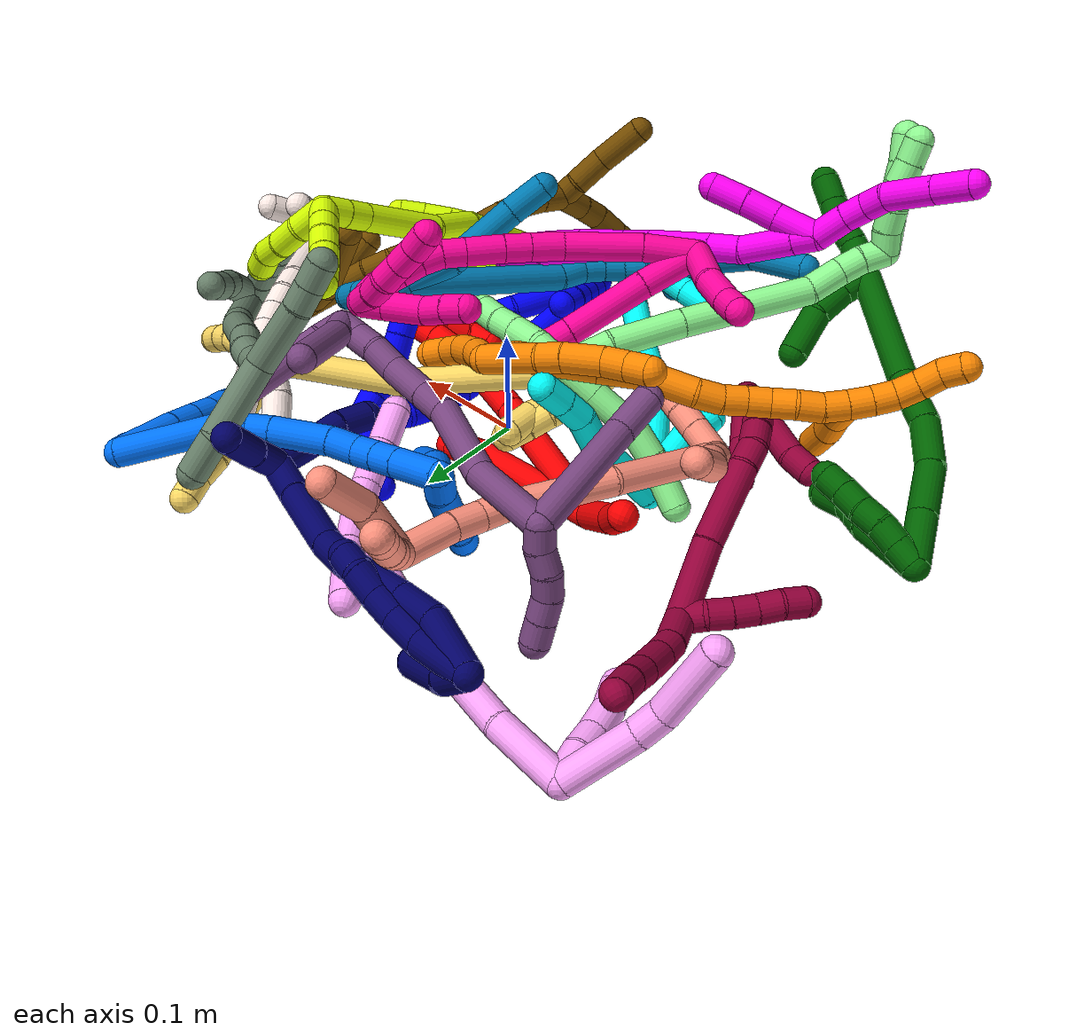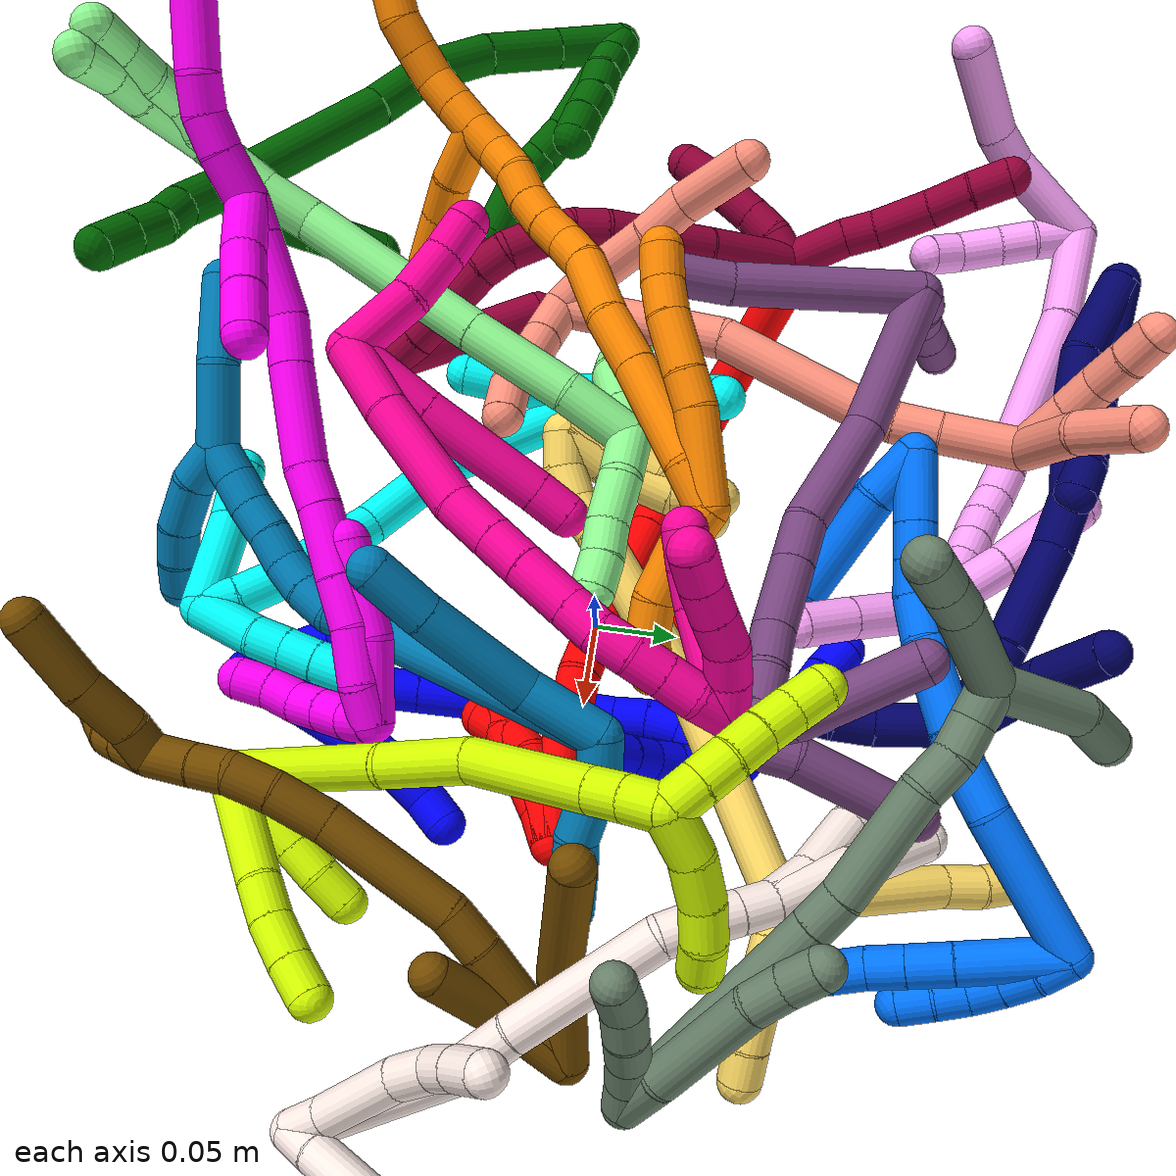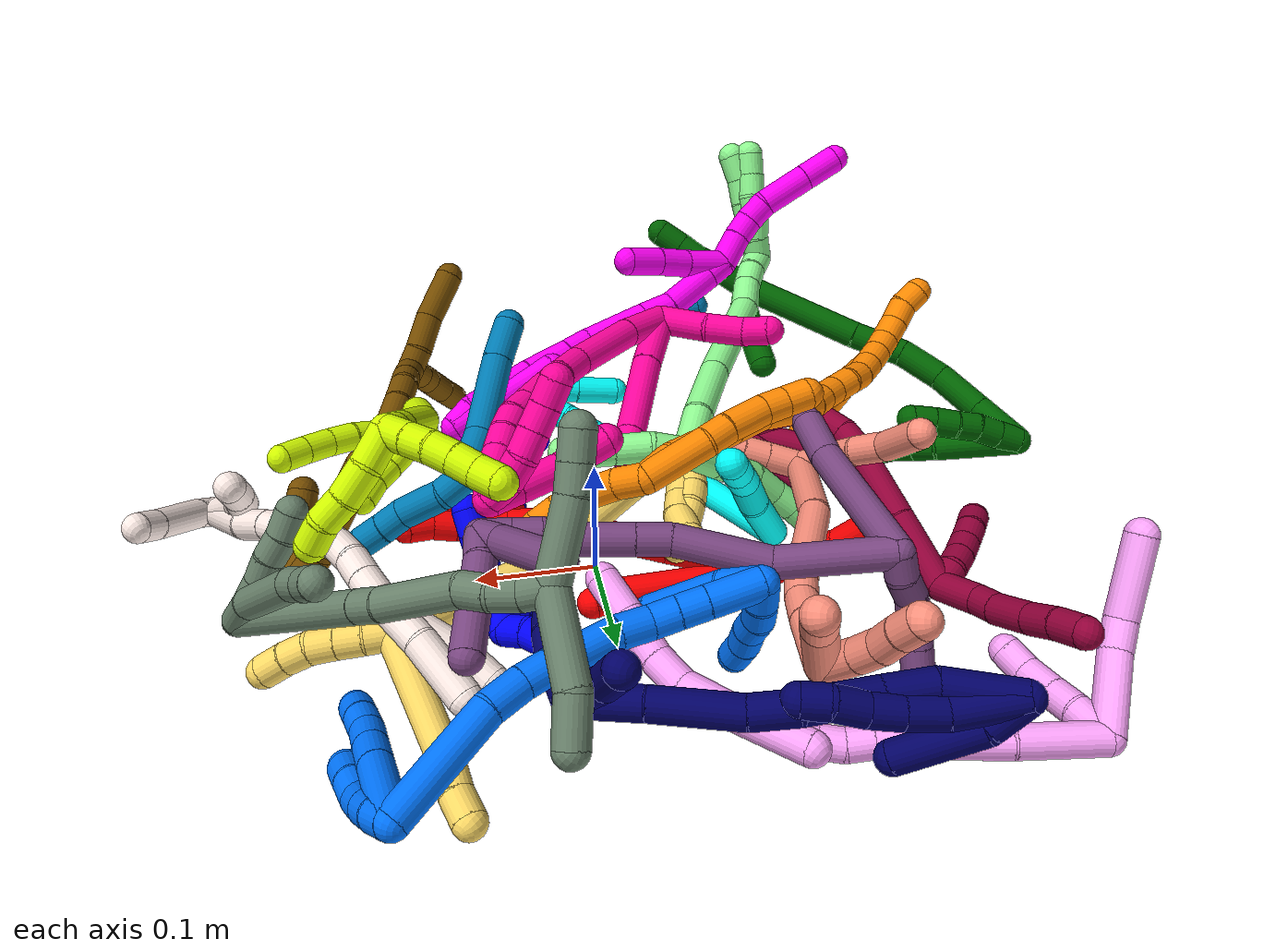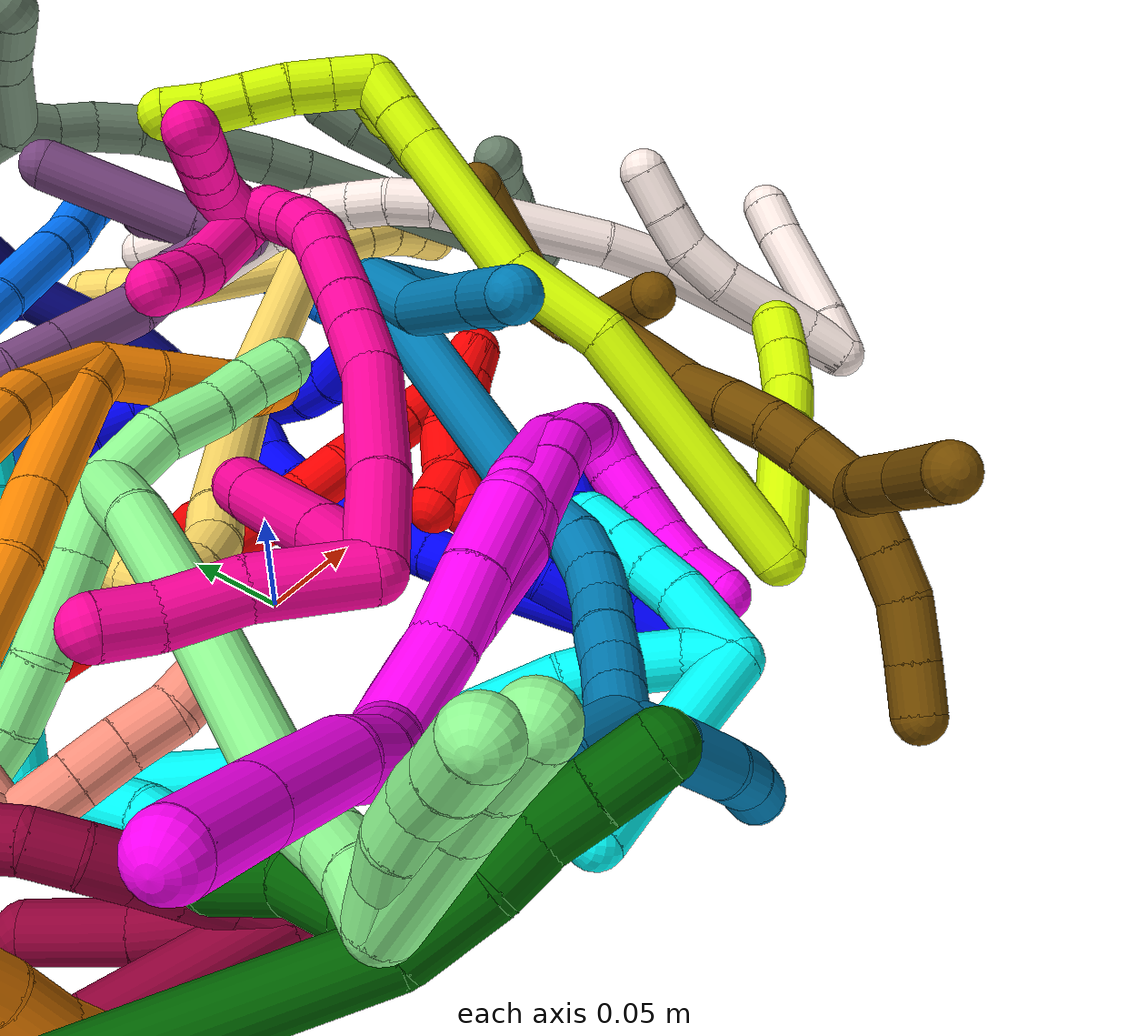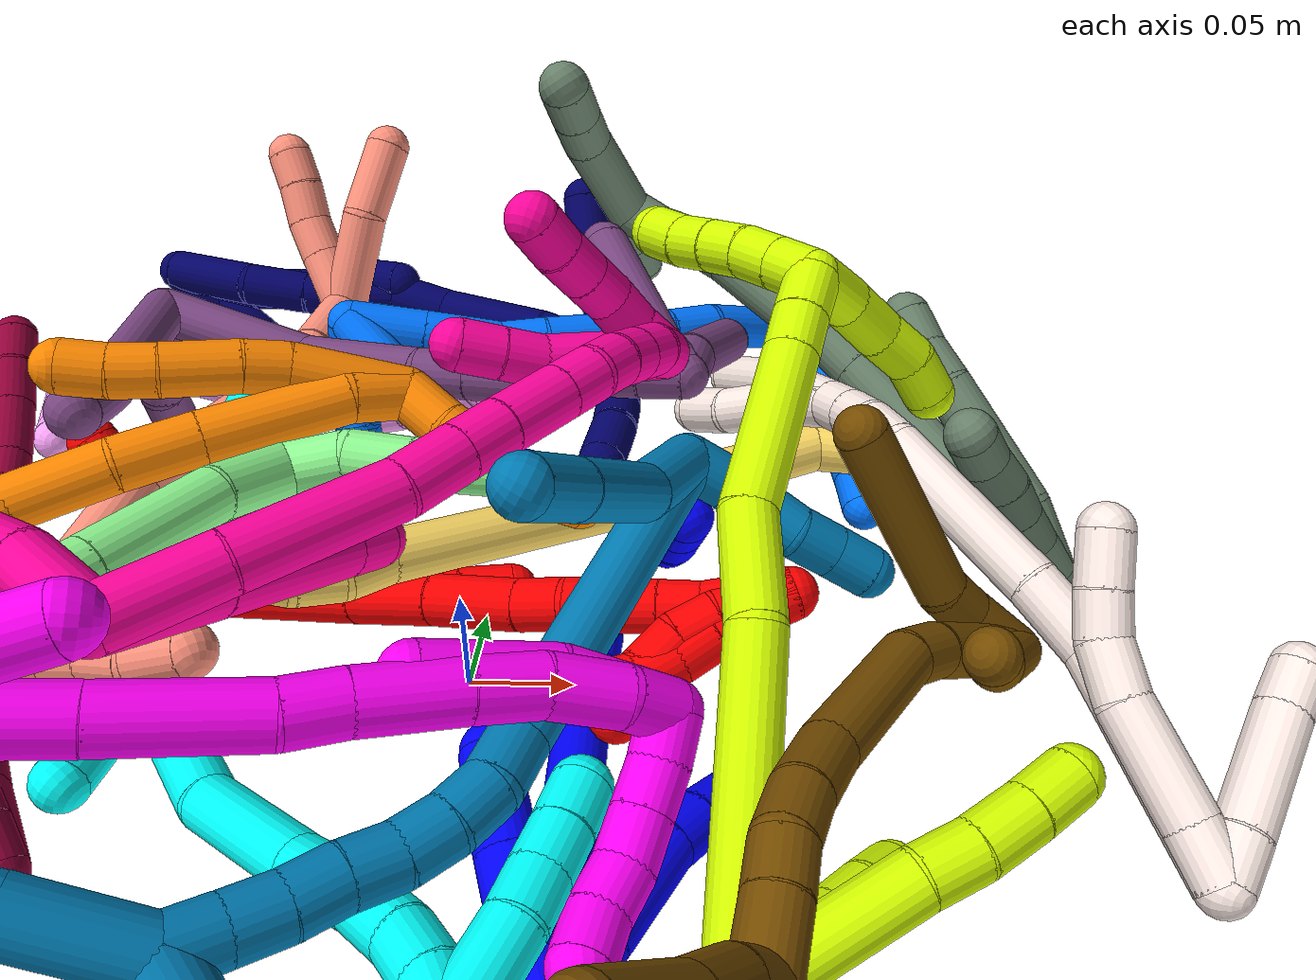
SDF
<sdf version="1.7">
 <world name="default">
  <plugin name="TubeGeneratorPlugin" filename="libtube_generator_plugin.so"/>
  <model name="photoneo_s_sensor">
   <static>1</static>
   <pose>0 0 2 1.57079 1.57079 3.14159</pose>
   <link name="link">
    <inertial><mass>0.1</mass></inertial>
    <sensor name="sensor" type="depth">
     <update_rate>30</update_rate>
     <camera>
      <horizontal_fov>1.22</horizontal_fov>
      <image><width>1920</width><height>1200</height><format>B8G8R8</format></image>
      <clip><near>0.1</near><far>4</far></clip>
      <depth_camera><output>points</output></depth_camera>
     </camera>
     <plugin name="camera_plugin" filename="libgazebo_ros_depth_camera.so">
      <baseline>0.2</baseline>
      <alwaysOn>1</alwaysOn>
      <updateRate>0.0</updateRate>
      <cameraName>camera_ir</cameraName>
      <imageTopicName>/camera/color/image_raw</imageTopicName>
      <cameraInfoTopicName>/camera/color/camera_info</cameraInfoTopicName>
      <depthImageTopicName>/camera/depth/image_raw</depthImageTopicName>
      <depthImageCameraInfoTopicName>/camera/depth/camera_info</depthImageCameraInfoTopicName>
      <pointCloudTopicName>/camera/depth/points</pointCloudTopicName>
      <frameName>fr_optical</frameName>
      <pointCloudCutoff>0.1</pointCloudCutoff>
      <pointCloudCutoffMax>2.0</pointCloudCutoffMax>
      <distortionK1>0</distortionK1>
      <distortionK2>0</distortionK2>
      <distortionK3>0</distortionK3>
      <distortionT1>0</distortionT1>
      <distortionT2>0</distortionT2>
      <CxPrime>0</CxPrime>
      <Cx>0</Cx>
      <Cy>0</Cy>
      <focalLength>0</focalLength>
      <hackBaseline>0</hackBaseline>
     </plugin>
    </sensor>
   </link>
  </model>
  <gravity>0 0 -9.8</gravity>
  <magnetic_field>6e-06 2.3e-05 -4.2e-05</magnetic_field>
  <atmosphere type="adiabatic"/>
  <physics name="default_physics" default="0" type="ode">
   <max_step_size>0.003</max_step_size>
   <real_time_factor>1</real_time_factor>
   <real_time_update_rate>1000</real_time_update_rate>
   <max_contacts>10000</max_contacts>
   <ode>
    <solver>
     <type>quick</type>
     <iters>100</iters>
     <sor>1.3</sor>
     <use_dynamic_moi_rescaling>0</use_dynamic_moi_rescaling>
    </solver>
    <constraints>
     <contact_max_correcting_vel>0</contact_max_correcting_vel>
     <contact_surface_layer>0.001</contact_surface_layer>
     <cfm>0</cfm>
     <erp>0.2</erp>
    </constraints>
   </ode>
  </physics>
  <scene><ambient>0.4 0.4 0.4 1</ambient><background>0.7 0.7 0.7 1</background><shadows>0</shadows></scene>
  <audio><device>default</device></audio>
  <spherical_coordinates>
   <surface_model>EARTH_WGS84</surface_model>
   <latitude_deg>0</latitude_deg>
   <longitude_deg>0</longitude_deg>
   <elevation>0</elevation>
   <heading_deg>0</heading_deg>
  </spherical_coordinates>
  <model name="bin">
   <static>1</static>
   <link name="bottom">
    <collision name="collision-bottom">
     <pose>0 0 -0.01 0 -0 0</pose>
     <geometry><box><size>0.8 0.6 0.02</size></box></geometry>
     <surface>
      <friction><ode><mu>100</mu><mu2>100</mu2></ode></friction>
      <contact><collide_bitmask>65535</collide_bitmask></contact>
     </surface>
    </collision>
   </link>
   <link name="west_wall">
    <collision name="collision-west_wall">
     <pose>-0.41 0 0.1 0 -0 0</pose>
     <geometry><box><size>0.02 0.6 0.2</size></box></geometry>
     <surface>
      <friction><ode><mu>100</mu><mu2>100</mu2></ode></friction>
      <contact><collide_bitmask>65535</collide_bitmask></contact>
     </surface>
    </collision>
   </link>
   <link name="east_wall">
    <collision name="collision-east_wall">
     <pose>0.41 0 0.1 0 -0 0</pose>
     <geometry><box><size>0.02 0.6 0.2</size></box></geometry>
     <surface>
      <friction><ode><mu>100</mu><mu2>100</mu2></ode></friction>
      <contact><collide_bitmask>65535</collide_bitmask></contact>
     </surface>
    </collision>
   </link>
   <link name="south_wall">
    <collision name="collision-south_wall">
     <pose>0 -0.31 0.1 0 -0 0</pose>
     <geometry><box><size>0.8 0.02 0.2</size></box></geometry>
     <surface>
      <friction><ode><mu>100</mu><mu2>100</mu2></ode></friction>
      <contact><collide_bitmask>65535</collide_bitmask></contact>
     </surface>
    </collision>
   </link>
   <link name="north_wall">
    <collision name="collision-north_wall">
     <pose>0 0.31 0.1 0 -0 0</pose>
     <geometry><box><size>0.8 0.02 0.2</size></box></geometry>
     <surface>
      <friction><ode><mu>100</mu><mu2>100</mu2></ode></friction>
      <contact><collide_bitmask>65535</collide_bitmask></contact>
     </surface>
    </collision>
   </link>
  </model>
  <model name="1">
   <static>0</static>
   <link name="1">
    <collision name="collision-cylinder-e_1_2_8">
     <pose>0.0152 0.008209 0.004612 -1.05896 1.01617 -0.630053</pose>
     <geometry><cylinder><radius>0.0125</radius><length>0.03576</length></cylinder></geometry>
     <surface>
      <friction><ode><mu>1.16</mu><mu2>1.16</mu2><slip1>0</slip1><slip2>0</slip2></ode></friction>
      <contact><ode><kp>1e+06</kp><kd>1</kd><max_vel>0</max_vel><min_depth>0.001</min_depth></ode></contact>
     </surface>
    </collision>
    <visual name="visual-cylinder-e_1_2_8">
     <pose>0.0152 0.008209 0.004612 -1.05896 1.01617 -0.630053</pose>
     <geometry><cylinder><radius>0.0125</radius><length>0.03576</length></cylinder></geometry>
     <material><ambient>0 0 1 1</ambient></material>
    </visual>
    <collision name="collision-cylinder-e_2_8_9">
     <pose>0.05328 0.028758 0.015986 -1.06945 1.01945 -0.639446</pose>
     <geometry><cylinder><radius>0.0125</radius><length>0.053722</length></cylinder></geometry>
     <surface>
      <friction><ode><mu>1.16</mu><mu2>1.16</mu2><slip1>0</slip1><slip2>0</slip2></ode></friction>
      <contact><ode><kp>1e+06</kp><kd>1</kd><max_vel>0</max_vel><min_depth>0.001</min_depth></ode></contact>
     </surface>
    </collision>
    <visual name="visual-cylinder-e_2_8_9">
     <pose>0.05328 0.028758 0.015986 -1.06945 1.01945 -0.639446</pose>
     <geometry><cylinder><radius>0.0125</radius><length>0.053722</length></cylinder></geometry>
     <material><ambient>0 0 1 1</ambient></material>
    </visual>
    <collision name="collision-cylinder-e_3_9_10">
     <pose>0.085225 0.04583 0.023314 -1.45179 1.08661 -0.984095</pose>
     <geometry><cylinder><radius>0.0125</radius><length>0.020484</length></cylinder></geometry>
     <surface>
      <friction><ode><mu>1.16</mu><mu2>1.16</mu2><slip1>0</slip1><slip2>0</slip2></ode></friction>
      <contact><ode><kp>1e+06</kp><kd>1</kd><max_vel>0</max_vel><min_depth>0.001</min_depth></ode></contact>
     </surface>
    </collision>
    <visual name="visual-cylinder-e_3_9_10">
     <pose>0.085225 0.04583 0.023314 -1.45179 1.08661 -0.984095</pose>
     <geometry><cylinder><radius>0.0125</radius><length>0.020484</length></cylinder></geometry>
     <material><ambient>0 0 1 1</ambient></material>
    </visual>
    <collision name="collision-cylinder-e_4_10_11">
     <pose>0.10305 0.055404 0.023639 -1.62063 1.06553 -1.10967</pose>
     <geometry><cylinder><radius>0.0125</radius><length>0.020023</length></cylinder></geometry>
     <surface>
      <friction><ode><mu>1.16</mu><mu2>1.16</mu2><slip1>0</slip1><slip2>0</slip2></ode></friction>
      <contact><ode><kp>1e+06</kp><kd>1</kd><max_vel>0</max_vel><min_depth>0.001</min_depth></ode></contact>
     </surface>
    </collision>
    <visual name="visual-cylinder-e_4_10_11">
     <pose>0.10305 0.055404 0.023639 -1.62063 1.06553 -1.10967</pose>
     <geometry><cylinder><radius>0.0125</radius><length>0.020023</length></cylinder></geometry>
     <material><ambient>0 0 1 1</ambient></material>
    </visual>
    <collision name="collision-cylinder-e_5_11_6">
     <pose>0.121619 0.062177 0.02381 -1.36058 1.37195 -1.17003</pose>
     <geometry><cylinder><radius>0.0125</radius><length>0.020012</length></cylinder></geometry>
     <surface>
      <friction><ode><mu>1.16</mu><mu2>1.16</mu2><slip1>0</slip1><slip2>0</slip2></ode></friction>
      <contact><ode><kp>1e+06</kp><kd>1</kd><max_vel>0</max_vel><min_depth>0.001</min_depth></ode></contact>
     </surface>
    </collision>
    <visual name="visual-cylinder-e_5_11_6">
     <pose>0.121619 0.062177 0.02381 -1.36058 1.37195 -1.17003</pose>
     <geometry><cylinder><radius>0.0125</radius><length>0.020012</length></cylinder></geometry>
     <material><ambient>0 0 1 1</ambient></material>
    </visual>
    <collision name="collision-cylinder-e_1_2_12">
     <pose>0.002297 0.004568 0.008594 -0.48861 0.231802 -0.058028</pose>
     <geometry><cylinder><radius>0.0125</radius><length>0.02</length></cylinder></geometry>
     <surface>
      <friction><ode><mu>1.16</mu><mu2>1.16</mu2><slip1>0</slip1><slip2>0</slip2></ode></friction>
      <contact><ode><kp>1e+06</kp><kd>1</kd><max_vel>0</max_vel><min_depth>0.001</min_depth></ode></contact>
     </surface>
    </collision>
    <visual name="visual-cylinder-e_1_2_12">
     <pose>0.002297 0.004568 0.008594 -0.48861 0.231802 -0.058028</pose>
     <geometry><cylinder><radius>0.0125</radius><length>0.02</length></cylinder></geometry>
     <material><ambient>0 0 1 1</ambient></material>
    </visual>
    <collision name="collision-cylinder-e_2_12_13">
     <pose>0.007827 0.012395 0.026072 -0.351478 0.329121 -0.058958</pose>
     <geometry><cylinder><radius>0.0125</radius><length>0.02</length></cylinder></geometry>
     <surface>
      <friction><ode><mu>1.16</mu><mu2>1.16</mu2><slip1>0</slip1><slip2>0</slip2></ode></friction>
      <contact><ode><kp>1e+06</kp><kd>1</kd><max_vel>0</max_vel><min_depth>0.001</min_depth></ode></contact>
     </surface>
    </collision>
    <visual name="visual-cylinder-e_2_12_13">
     <pose>0.007827 0.012395 0.026072 -0.351478 0.329121 -0.058958</pose>
     <geometry><cylinder><radius>0.0125</radius><length>0.02</length></cylinder></geometry>
     <material><ambient>0 0 1 1</ambient></material>
    </visual>
    <collision name="collision-cylinder-e_3_13_14">
     <pose>0.014154 0.01897 0.043868 -0.356368 0.314639 -0.057121</pose>
     <geometry><cylinder><radius>0.0125</radius><length>0.02</length></cylinder></geometry>
     <surface>
      <friction><ode><mu>1.16</mu><mu2>1.16</mu2><slip1>0</slip1><slip2>0</slip2></ode></friction>
      <contact><ode><kp>1e+06</kp><kd>1</kd><max_vel>0</max_vel><min_depth>0.001</min_depth></ode></contact>
     </surface>
    </collision>
    <visual name="visual-cylinder-e_3_13_14">
     <pose>0.014154 0.01897 0.043868 -0.356368 0.314639 -0.057121</pose>
     <geometry><cylinder><radius>0.0125</radius><length>0.02</length></cylinder></geometry>
     <material><ambient>0 0 1 1</ambient></material>
    </visual>
    <collision name="collision-cylinder-e_4_14_15">
     <pose>0.0203 0.025221 0.06184 -0.313065 0.310079 -0.049324</pose>
     <geometry><cylinder><radius>0.0125</radius><length>0.02</length></cylinder></geometry>
     <surface>
      <friction><ode><mu>1.16</mu><mu2>1.16</mu2><slip1>0</slip1><slip2>0</slip2></ode></friction>
      <contact><ode><kp>1e+06</kp><kd>1</kd><max_vel>0</max_vel><min_depth>0.001</min_depth></ode></contact>
     </surface>
    </collision>
    <visual name="visual-cylinder-e_4_14_15">
     <pose>0.0203 0.025221 0.06184 -0.313065 0.310079 -0.049324</pose>
     <geometry><cylinder><radius>0.0125</radius><length>0.02</length></cylinder></geometry>
     <material><ambient>0 0 1 1</ambient></material>
    </visual>
    <collision name="collision-cylinder-e_5_15_5">
     <pose>0.027532 0.031838 0.079204 -0.417663 0.431338 -0.092787</pose>
     <geometry><cylinder><radius>0.0125</radius><length>0.02</length></cylinder></geometry>
     <surface>
      <friction><ode><mu>1.16</mu><mu2>1.16</mu2><slip1>0</slip1><slip2>0</slip2></ode></friction>
      <contact><ode><kp>1e+06</kp><kd>1</kd><max_vel>0</max_vel><min_depth>0.001</min_depth></ode></contact>
     </surface>
    </collision>
    <visual name="visual-cylinder-e_5_15_5">
     <pose>0.027532 0.031838 0.079204 -0.417663 0.431338 -0.092787</pose>
     <geometry><cylinder><radius>0.0125</radius><length>0.02</length></cylinder></geometry>
     <material><ambient>0 0 1 1</ambient></material>
    </visual>
    <collision name="collision-cylinder-e_1_2_16">
     <pose>0.027346 0.034272 0.02541 -0.932808 0.569984 -0.292877</pose>
     <geometry><cylinder><radius>0.0125</radius><length>0.101352</length></cylinder></geometry>
     <surface>
      <friction><ode><mu>1.16</mu><mu2>1.16</mu2><slip1>0</slip1><slip2>0</slip2></ode></friction>
      <contact><ode><kp>1e+06</kp><kd>1</kd><max_vel>0</max_vel><min_depth>0.001</min_depth></ode></contact>
     </surface>
    </collision>
    <visual name="visual-cylinder-e_1_2_16">
     <pose>0.027346 0.034272 0.02541 -0.932808 0.569984 -0.292877</pose>
     <geometry><cylinder><radius>0.0125</radius><length>0.101352</length></cylinder></geometry>
     <material><ambient>0 0 1 1</ambient></material>
    </visual>
    <collision name="collision-cylinder-e_2_16_17">
     <pose>0.068547 0.084857 0.063978 -0.892068 0.584153 -0.285593</pose>
     <geometry><cylinder><radius>0.0125</radius><length>0.050246</length></cylinder></geometry>
     <surface>
      <friction><ode><mu>1.16</mu><mu2>1.16</mu2><slip1>0</slip1><slip2>0</slip2></ode></friction>
      <contact><ode><kp>1e+06</kp><kd>1</kd><max_vel>0</max_vel><min_depth>0.001</min_depth></ode></contact>
     </surface>
    </collision>
    <visual name="visual-cylinder-e_2_16_17">
     <pose>0.068547 0.084857 0.063978 -0.892068 0.584153 -0.285593</pose>
     <geometry><cylinder><radius>0.0125</radius><length>0.050246</length></cylinder></geometry>
     <material><ambient>0 0 1 1</ambient></material>
    </visual>
    <collision name="collision-cylinder-e_3_17_18">
     <pose>0.096236 0.115291 0.089949 -0.833893 0.627626 -0.285529</pose>
     <geometry><cylinder><radius>0.0125</radius><length>0.047116</length></cylinder></geometry>
     <surface>
      <friction><ode><mu>1.16</mu><mu2>1.16</mu2><slip1>0</slip1><slip2>0</slip2></ode></friction>
      <contact><ode><kp>1e+06</kp><kd>1</kd><max_vel>0</max_vel><min_depth>0.001</min_depth></ode></contact>
     </surface>
    </collision>
    <visual name="visual-cylinder-e_3_17_18">
     <pose>0.096236 0.115291 0.089949 -0.833893 0.627626 -0.285529</pose>
     <geometry><cylinder><radius>0.0125</radius><length>0.047116</length></cylinder></geometry>
     <material><ambient>0 0 1 1</ambient></material>
    </visual>
    <collision name="collision-cylinder-e_4_18_19">
     <pose>0.116418 0.134621 0.108536 -0.733973 0.684668 -0.272279</pose>
     <geometry><cylinder><radius>0.0125</radius><length>0.020077</length></cylinder></geometry>
     <surface>
      <friction><ode><mu>1.16</mu><mu2>1.16</mu2><slip1>0</slip1><slip2>0</slip2></ode></friction>
      <contact><ode><kp>1e+06</kp><kd>1</kd><max_vel>0</max_vel><min_depth>0.001</min_depth></ode></contact>
     </surface>
    </collision>
    <visual name="visual-cylinder-e_4_18_19">
     <pose>0.116418 0.134621 0.108536 -0.733973 0.684668 -0.272279</pose>
     <geometry><cylinder><radius>0.0125</radius><length>0.020077</length></cylinder></geometry>
     <material><ambient>0 0 1 1</ambient></material>
    </visual>
    <collision name="collision-cylinder-e_5_19_20">
     <pose>0.128676 0.144813 0.120857 -0.650671 0.622829 -0.216312</pose>
     <geometry><cylinder><radius>0.0125</radius><length>0.020259</length></cylinder></geometry>
     <surface>
      <friction><ode><mu>1.16</mu><mu2>1.16</mu2><slip1>0</slip1><slip2>0</slip2></ode></friction>
      <contact><ode><kp>1e+06</kp><kd>1</kd><max_vel>0</max_vel><min_depth>0.001</min_depth></ode></contact>
     </surface>
    </collision>
    <visual name="visual-cylinder-e_5_19_20">
     <pose>0.128676 0.144813 0.120857 -0.650671 0.622829 -0.216312</pose>
     <geometry><cylinder><radius>0.0125</radius><length>0.020259</length></cylinder></geometry>
     <material><ambient>0 0 1 1</ambient></material>
    </visual>
    <collision name="collision-cylinder-e_6_20_21">
     <pose>0.142291 0.153869 0.132944 -0.633814 0.842234 -0.291709</pose>
     <geometry><cylinder><radius>0.0125</radius><length>0.020658</length></cylinder></geometry>
     <surface>
      <friction><ode><mu>1.16</mu><mu2>1.16</mu2><slip1>0</slip1><slip2>0</slip2></ode></friction>
      <contact><ode><kp>1e+06</kp><kd>1</kd><max_vel>0</max_vel><min_depth>0.001</min_depth></ode></contact>
     </surface>
    </collision>
    <visual name="visual-cylinder-e_6_20_21">
     <pose>0.142291 0.153869 0.132944 -0.633814 0.842234 -0.291709</pose>
     <geometry><cylinder><radius>0.0125</radius><length>0.020658</length></cylinder></geometry>
     <material><ambient>0 0 1 1</ambient></material>
    </visual>
    <collision name="collision-cylinder-e_7_21_22">
     <pose>0.15928 0.160608 0.141274 -0.762968 1.17694 -0.523124</pose>
     <geometry><cylinder><radius>0.0125</radius><length>0.020103</length></cylinder></geometry>
     <surface>
      <friction><ode><mu>1.16</mu><mu2>1.16</mu2><slip1>0</slip1><slip2>0</slip2></ode></friction>
      <contact><ode><kp>1e+06</kp><kd>1</kd><max_vel>0</max_vel><min_depth>0.001</min_depth></ode></contact>
     </surface>
    </collision>
    <visual name="visual-cylinder-e_7_21_22">
     <pose>0.15928 0.160608 0.141274 -0.762968 1.17694 -0.523124</pose>
     <geometry><cylinder><radius>0.0125</radius><length>0.020103</length></cylinder></geometry>
     <material><ambient>0 0 1 1</ambient></material>
    </visual>
    <collision name="collision-cylinder-e_8_22_1">
     <pose>0.178213 0.164706 0.146647 -0.506131 1.27357 -0.37795</pose>
     <geometry><cylinder><radius>0.0125</radius><length>0.020189</length></cylinder></geometry>
     <surface>
      <friction><ode><mu>1.16</mu><mu2>1.16</mu2><slip1>0</slip1><slip2>0</slip2></ode></friction>
      <contact><ode><kp>1e+06</kp><kd>1</kd><max_vel>0</max_vel><min_depth>0.001</min_depth></ode></contact>
     </surface>
    </collision>
    <visual name="visual-cylinder-e_8_22_1">
     <pose>0.178213 0.164706 0.146647 -0.506131 1.27357 -0.37795</pose>
     <geometry><cylinder><radius>0.0125</radius><length>0.020189</length></cylinder></geometry>
     <material><ambient>0 0 1 1</ambient></material>
    </visual>
    <collision name="collision-cylinder-e_1_1_23">
     <pose>0.185359 0.169961 0.158128 -0.405752 -0.253328 0.05238</pose>
     <geometry><cylinder><radius>0.0125</radius><length>0.02</length></cylinder></geometry>
     <surface>
      <friction><ode><mu>1.16</mu><mu2>1.16</mu2><slip1>0</slip1><slip2>0</slip2></ode></friction>
      <contact><ode><kp>1e+06</kp><kd>1</kd><max_vel>0</max_vel><min_depth>0.001</min_depth></ode></contact>
     </surface>
    </collision>
    <visual name="visual-cylinder-e_1_1_23">
     <pose>0.185359 0.169961 0.158128 -0.405752 -0.253328 0.05238</pose>
     <geometry><cylinder><radius>0.0125</radius><length>0.02</length></cylinder></geometry>
     <material><ambient>0 0 1 1</ambient></material>
    </visual>
    <collision name="collision-cylinder-e_2_23_24">
     <pose>0.181262 0.179974 0.174712 -0.677948 -0.159713 0.056417</pose>
     <geometry><cylinder><radius>0.0125</radius><length>0.02</length></cylinder></geometry>
     <surface>
      <friction><ode><mu>1.16</mu><mu2>1.16</mu2><slip1>0</slip1><slip2>0</slip2></ode></friction>
      <contact><ode><kp>1e+06</kp><kd>1</kd><max_vel>0</max_vel><min_depth>0.001</min_depth></ode></contact>
     </surface>
    </collision>
    <visual name="visual-cylinder-e_2_23_24">
     <pose>0.181262 0.179974 0.174712 -0.677948 -0.159713 0.056417</pose>
     <geometry><cylinder><radius>0.0125</radius><length>0.02</length></cylinder></geometry>
     <material><ambient>0 0 1 1</ambient></material>
    </visual>
    <collision name="collision-cylinder-e_3_24_25">
     <pose>0.176579 0.191131 0.190513 -0.549246 -0.314439 0.089269</pose>
     <geometry><cylinder><radius>0.0125</radius><length>0.02</length></cylinder></geometry>
     <surface>
      <friction><ode><mu>1.16</mu><mu2>1.16</mu2><slip1>0</slip1><slip2>0</slip2></ode></friction>
      <contact><ode><kp>1e+06</kp><kd>1</kd><max_vel>0</max_vel><min_depth>0.001</min_depth></ode></contact>
     </surface>
    </collision>
    <visual name="visual-cylinder-e_3_24_25">
     <pose>0.176579 0.191131 0.190513 -0.549246 -0.314439 0.089269</pose>
     <geometry><cylinder><radius>0.0125</radius><length>0.02</length></cylinder></geometry>
     <material><ambient>0 0 1 1</ambient></material>
    </visual>
    <collision name="collision-cylinder-e_4_25_26">
     <pose>0.169001 0.202569 0.204786 -0.810004 -0.465079 0.20236</pose>
     <geometry><cylinder><radius>0.0125</radius><length>0.02</length></cylinder></geometry>
     <surface>
      <friction><ode><mu>1.16</mu><mu2>1.16</mu2><slip1>0</slip1><slip2>0</slip2></ode></friction>
      <contact><ode><kp>1e+06</kp><kd>1</kd><max_vel>0</max_vel><min_depth>0.001</min_depth></ode></contact>
     </surface>
    </collision>
    <visual name="visual-cylinder-e_4_25_26">
     <pose>0.169001 0.202569 0.204786 -0.810004 -0.465079 0.20236</pose>
     <geometry><cylinder><radius>0.0125</radius><length>0.02</length></cylinder></geometry>
     <material><ambient>0 0 1 1</ambient></material>
    </visual>
    <collision name="collision-cylinder-e_5_26_4">
     <pose>0.160903 0.215923 0.217242 -0.829925 -0.369663 0.164362</pose>
     <geometry><cylinder><radius>0.0125</radius><length>0.02</length></cylinder></geometry>
     <surface>
      <friction><ode><mu>1.16</mu><mu2>1.16</mu2><slip1>0</slip1><slip2>0</slip2></ode></friction>
      <contact><ode><kp>1e+06</kp><kd>1</kd><max_vel>0</max_vel><min_depth>0.001</min_depth></ode></contact>
     </surface>
    </collision>
    <visual name="visual-cylinder-e_5_26_4">
     <pose>0.160903 0.215923 0.217242 -0.829925 -0.369663 0.164362</pose>
     <geometry><cylinder><radius>0.0125</radius><length>0.02</length></cylinder></geometry>
     <material><ambient>0 0 1 1</ambient></material>
    </visual>
    <collision name="collision-cylinder-e_1_1_27">
     <pose>0.18524 0.156946 0.146303 1.87931 -0.265663 -0.361651</pose>
     <geometry><cylinder><radius>0.0125</radius><length>0.02</length></cylinder></geometry>
     <surface>
      <friction><ode><mu>1.16</mu><mu2>1.16</mu2><slip1>0</slip1><slip2>0</slip2></ode></friction>
      <contact><ode><kp>1e+06</kp><kd>1</kd><max_vel>0</max_vel><min_depth>0.001</min_depth></ode></contact>
     </surface>
    </collision>
    <visual name="visual-cylinder-e_1_1_27">
     <pose>0.18524 0.156946 0.146303 1.87931 -0.265663 -0.361651</pose>
     <geometry><cylinder><radius>0.0125</radius><length>0.02</length></cylinder></geometry>
     <material><ambient>0 0 1 1</ambient></material>
    </visual>
    <collision name="collision-cylinder-e_2_27_28">
     <pose>0.178968 0.138783 0.140873 1.84267 -0.373284 -0.487479</pose>
     <geometry><cylinder><radius>0.0125</radius><length>0.02</length></cylinder></geometry>
     <surface>
      <friction><ode><mu>1.16</mu><mu2>1.16</mu2><slip1>0</slip1><slip2>0</slip2></ode></friction>
      <contact><ode><kp>1e+06</kp><kd>1</kd><max_vel>0</max_vel><min_depth>0.001</min_depth></ode></contact>
     </surface>
    </collision>
    <visual name="visual-cylinder-e_2_27_28">
     <pose>0.178968 0.138783 0.140873 1.84267 -0.373284 -0.487479</pose>
     <geometry><cylinder><radius>0.0125</radius><length>0.02</length></cylinder></geometry>
     <material><ambient>0 0 1 1</ambient></material>
    </visual>
    <collision name="collision-cylinder-e_3_28_29">
     <pose>0.173127 0.120099 0.137465 1.66396 -0.221141 -0.242564</pose>
     <geometry><cylinder><radius>0.0125</radius><length>0.02</length></cylinder></geometry>
     <surface>
      <friction><ode><mu>1.16</mu><mu2>1.16</mu2><slip1>0</slip1><slip2>0</slip2></ode></friction>
      <contact><ode><kp>1e+06</kp><kd>1</kd><max_vel>0</max_vel><min_depth>0.001</min_depth></ode></contact>
     </surface>
    </collision>
    <visual name="visual-cylinder-e_3_28_29">
     <pose>0.173127 0.120099 0.137465 1.66396 -0.221141 -0.242564</pose>
     <geometry><cylinder><radius>0.0125</radius><length>0.02</length></cylinder></geometry>
     <material><ambient>0 0 1 1</ambient></material>
    </visual>
    <collision name="collision-cylinder-e_4_29_30">
     <pose>0.169879 0.100458 0.137137 1.51249 -0.105672 -0.099694</pose>
     <geometry><cylinder><radius>0.0125</radius><length>0.02</length></cylinder></geometry>
     <surface>
      <friction><ode><mu>1.16</mu><mu2>1.16</mu2><slip1>0</slip1><slip2>0</slip2></ode></friction>
      <contact><ode><kp>1e+06</kp><kd>1</kd><max_vel>0</max_vel><min_depth>0.001</min_depth></ode></contact>
     </surface>
    </collision>
    <visual name="visual-cylinder-e_4_29_30">
     <pose>0.169879 0.100458 0.137137 1.51249 -0.105672 -0.099694</pose>
     <geometry><cylinder><radius>0.0125</radius><length>0.02</length></cylinder></geometry>
     <material><ambient>0 0 1 1</ambient></material>
    </visual>
    <collision name="collision-cylinder-e_5_30_3">
     <pose>0.167545 0.08062 0.138099 1.53217 -0.128247 -0.123399</pose>
     <geometry><cylinder><radius>0.0125</radius><length>0.02</length></cylinder></geometry>
     <surface>
      <friction><ode><mu>1.16</mu><mu2>1.16</mu2><slip1>0</slip1><slip2>0</slip2></ode></friction>
      <contact><ode><kp>1e+06</kp><kd>1</kd><max_vel>0</max_vel><min_depth>0.001</min_depth></ode></contact>
     </surface>
    </collision>
    <visual name="visual-cylinder-e_5_30_3">
     <pose>0.167545 0.08062 0.138099 1.53217 -0.128247 -0.123399</pose>
     <geometry><cylinder><radius>0.0125</radius><length>0.02</length></cylinder></geometry>
     <material><ambient>0 0 1 1</ambient></material>
    </visual>
    <collision name="collision-sphere-3">
     <pose>0.166266 0.07071 0.138482 0 -0 0</pose>
     <geometry><sphere><radius>0.0125</radius></sphere></geometry>
     <surface>
      <friction><ode><mu>1.16</mu><mu2>1.16</mu2><slip1>0</slip1><slip2>0</slip2></ode></friction>
      <contact><ode><kp>1e+06</kp><kd>1</kd><max_vel>0</max_vel><min_depth>0.001</min_depth></ode></contact>
     </surface>
    </collision>
    <visual name="visual-sphere-3">
     <pose>0.166266 0.07071 0.138482 0 -0 0</pose>
     <geometry><sphere><radius>0.0125</radius></sphere></geometry>
     <material><ambient>0 0 1 1</ambient></material>
    </visual>
    <collision name="collision-sphere-30">
     <pose>0.168824 0.090531 0.137716 0 -0 0</pose>
     <geometry><sphere><radius>0.0125</radius></sphere></geometry>
     <surface>
      <friction><ode><mu>1.16</mu><mu2>1.16</mu2><slip1>0</slip1><slip2>0</slip2></ode></friction>
      <contact><ode><kp>1e+06</kp><kd>1</kd><max_vel>0</max_vel><min_depth>0.001</min_depth></ode></contact>
     </surface>
    </collision>
    <visual name="visual-sphere-30">
     <pose>0.168824 0.090531 0.137716 0 -0 0</pose>
     <geometry><sphere><radius>0.0125</radius></sphere></geometry>
     <material><ambient>0 0 1 1</ambient></material>
    </visual>
    <collision name="collision-sphere-29">
     <pose>0.170934 0.110385 0.136557 0 -0 0</pose>
     <geometry><sphere><radius>0.0125</radius></sphere></geometry>
     <surface>
      <friction><ode><mu>1.16</mu><mu2>1.16</mu2><slip1>0</slip1><slip2>0</slip2></ode></friction>
      <contact><ode><kp>1e+06</kp><kd>1</kd><max_vel>0</max_vel><min_depth>0.001</min_depth></ode></contact>
     </surface>
    </collision>
    <visual name="visual-sphere-29">
     <pose>0.170934 0.110385 0.136557 0 -0 0</pose>
     <geometry><sphere><radius>0.0125</radius></sphere></geometry>
     <material><ambient>0 0 1 1</ambient></material>
    </visual>
    <collision name="collision-sphere-28">
     <pose>0.175321 0.129814 0.138372 0 -0 0</pose>
     <geometry><sphere><radius>0.0125</radius></sphere></geometry>
     <surface>
      <friction><ode><mu>1.16</mu><mu2>1.16</mu2><slip1>0</slip1><slip2>0</slip2></ode></friction>
      <contact><ode><kp>1e+06</kp><kd>1</kd><max_vel>0</max_vel><min_depth>0.001</min_depth></ode></contact>
     </surface>
    </collision>
    <visual name="visual-sphere-28">
     <pose>0.175321 0.129814 0.138372 0 -0 0</pose>
     <geometry><sphere><radius>0.0125</radius></sphere></geometry>
     <material><ambient>0 0 1 1</ambient></material>
    </visual>
    <collision name="collision-sphere-27">
     <pose>0.182614 0.147752 0.143373 0 -0 0</pose>
     <geometry><sphere><radius>0.0125</radius></sphere></geometry>
     <surface>
      <friction><ode><mu>1.16</mu><mu2>1.16</mu2><slip1>0</slip1><slip2>0</slip2></ode></friction>
      <contact><ode><kp>1e+06</kp><kd>1</kd><max_vel>0</max_vel><min_depth>0.001</min_depth></ode></contact>
     </surface>
    </collision>
    <visual name="visual-sphere-27">
     <pose>0.182614 0.147752 0.143373 0 -0 0</pose>
     <geometry><sphere><radius>0.0125</radius></sphere></geometry>
     <material><ambient>0 0 1 1</ambient></material>
    </visual>
    <collision name="collision-sphere-4">
     <pose>0.15729 0.222803 0.223536 0 -0 0</pose>
     <geometry><sphere><radius>0.0125</radius></sphere></geometry>
     <surface>
      <friction><ode><mu>1.16</mu><mu2>1.16</mu2><slip1>0</slip1><slip2>0</slip2></ode></friction>
      <contact><ode><kp>1e+06</kp><kd>1</kd><max_vel>0</max_vel><min_depth>0.001</min_depth></ode></contact>
     </surface>
    </collision>
    <visual name="visual-sphere-4">
     <pose>0.15729 0.222803 0.223536 0 -0 0</pose>
     <geometry><sphere><radius>0.0125</radius></sphere></geometry>
     <material><ambient>0 0 1 1</ambient></material>
    </visual>
    <collision name="collision-sphere-26">
     <pose>0.164516 0.209042 0.210949 0 -0 0</pose>
     <geometry><sphere><radius>0.0125</radius></sphere></geometry>
     <surface>
      <friction><ode><mu>1.16</mu><mu2>1.16</mu2><slip1>0</slip1><slip2>0</slip2></ode></friction>
      <contact><ode><kp>1e+06</kp><kd>1</kd><max_vel>0</max_vel><min_depth>0.001</min_depth></ode></contact>
     </surface>
    </collision>
    <visual name="visual-sphere-26">
     <pose>0.164516 0.209042 0.210949 0 -0 0</pose>
     <geometry><sphere><radius>0.0125</radius></sphere></geometry>
     <material><ambient>0 0 1 1</ambient></material>
    </visual>
    <collision name="collision-sphere-25">
     <pose>0.173486 0.196095 0.198624 0 -0 0</pose>
     <geometry><sphere><radius>0.0125</radius></sphere></geometry>
     <surface>
      <friction><ode><mu>1.16</mu><mu2>1.16</mu2><slip1>0</slip1><slip2>0</slip2></ode></friction>
      <contact><ode><kp>1e+06</kp><kd>1</kd><max_vel>0</max_vel><min_depth>0.001</min_depth></ode></contact>
     </surface>
    </collision>
    <visual name="visual-sphere-25">
     <pose>0.173486 0.196095 0.198624 0 -0 0</pose>
     <geometry><sphere><radius>0.0125</radius></sphere></geometry>
     <material><ambient>0 0 1 1</ambient></material>
    </visual>
    <collision name="collision-sphere-24">
     <pose>0.179672 0.186166 0.182402 0 -0 0</pose>
     <geometry><sphere><radius>0.0125</radius></sphere></geometry>
     <surface>
      <friction><ode><mu>1.16</mu><mu2>1.16</mu2><slip1>0</slip1><slip2>0</slip2></ode></friction>
      <contact><ode><kp>1e+06</kp><kd>1</kd><max_vel>0</max_vel><min_depth>0.001</min_depth></ode></contact>
     </surface>
    </collision>
    <visual name="visual-sphere-24">
     <pose>0.179672 0.186166 0.182402 0 -0 0</pose>
     <geometry><sphere><radius>0.0125</radius></sphere></geometry>
     <material><ambient>0 0 1 1</ambient></material>
    </visual>
    <collision name="collision-sphere-23">
     <pose>0.182853 0.173782 0.167023 0 -0 0</pose>
     <geometry><sphere><radius>0.0125</radius></sphere></geometry>
     <surface>
      <friction><ode><mu>1.16</mu><mu2>1.16</mu2><slip1>0</slip1><slip2>0</slip2></ode></friction>
      <contact><ode><kp>1e+06</kp><kd>1</kd><max_vel>0</max_vel><min_depth>0.001</min_depth></ode></contact>
     </surface>
    </collision>
    <visual name="visual-sphere-23">
     <pose>0.182853 0.173782 0.167023 0 -0 0</pose>
     <geometry><sphere><radius>0.0125</radius></sphere></geometry>
     <material><ambient>0 0 1 1</ambient></material>
    </visual>
    <collision name="collision-sphere-1">
     <pose>0.187865 0.16614 0.149233 0 -0 0</pose>
     <geometry><sphere><radius>0.0125</radius></sphere></geometry>
     <surface>
      <friction><ode><mu>1.16</mu><mu2>1.16</mu2><slip1>0</slip1><slip2>0</slip2></ode></friction>
      <contact><ode><kp>1e+06</kp><kd>1</kd><max_vel>0</max_vel><min_depth>0.001</min_depth></ode></contact>
     </surface>
    </collision>
    <visual name="visual-sphere-1">
     <pose>0.187865 0.16614 0.149233 0 -0 0</pose>
     <geometry><sphere><radius>0.0125</radius></sphere></geometry>
     <material><ambient>0 0 1 1</ambient></material>
    </visual>
    <collision name="collision-sphere-22">
     <pose>0.168562 0.163273 0.144062 0 -0 0</pose>
     <geometry><sphere><radius>0.0125</radius></sphere></geometry>
     <surface>
      <friction><ode><mu>1.16</mu><mu2>1.16</mu2><slip1>0</slip1><slip2>0</slip2></ode></friction>
      <contact><ode><kp>1e+06</kp><kd>1</kd><max_vel>0</max_vel><min_depth>0.001</min_depth></ode></contact>
     </surface>
    </collision>
    <visual name="visual-sphere-22">
     <pose>0.168562 0.163273 0.144062 0 -0 0</pose>
     <geometry><sphere><radius>0.0125</radius></sphere></geometry>
     <material><ambient>0 0 1 1</ambient></material>
    </visual>
    <collision name="collision-sphere-21">
     <pose>0.149998 0.157942 0.138486 0 -0 0</pose>
     <geometry><sphere><radius>0.0125</radius></sphere></geometry>
     <surface>
      <friction><ode><mu>1.16</mu><mu2>1.16</mu2><slip1>0</slip1><slip2>0</slip2></ode></friction>
      <contact><ode><kp>1e+06</kp><kd>1</kd><max_vel>0</max_vel><min_depth>0.001</min_depth></ode></contact>
     </surface>
    </collision>
    <visual name="visual-sphere-21">
     <pose>0.149998 0.157942 0.138486 0 -0 0</pose>
     <geometry><sphere><radius>0.0125</radius></sphere></geometry>
     <material><ambient>0 0 1 1</ambient></material>
    </visual>
    <collision name="collision-sphere-6">
     <pose>0.131428 0.06411 0.024223 0 -0 0</pose>
     <geometry><sphere><radius>0.0125</radius></sphere></geometry>
     <surface>
      <friction><ode><mu>1.16</mu><mu2>1.16</mu2><slip1>0</slip1><slip2>0</slip2></ode></friction>
      <contact><ode><kp>1e+06</kp><kd>1</kd><max_vel>0</max_vel><min_depth>0.001</min_depth></ode></contact>
     </surface>
    </collision>
    <visual name="visual-sphere-6">
     <pose>0.131428 0.06411 0.024223 0 -0 0</pose>
     <geometry><sphere><radius>0.0125</radius></sphere></geometry>
     <material><ambient>0 0 1 1</ambient></material>
    </visual>
    <collision name="collision-sphere-11">
     <pose>0.111811 0.060244 0.023398 0 -0 0</pose>
     <geometry><sphere><radius>0.0125</radius></sphere></geometry>
     <surface>
      <friction><ode><mu>1.16</mu><mu2>1.16</mu2><slip1>0</slip1><slip2>0</slip2></ode></friction>
      <contact><ode><kp>1e+06</kp><kd>1</kd><max_vel>0</max_vel><min_depth>0.001</min_depth></ode></contact>
     </surface>
    </collision>
    <visual name="visual-sphere-11">
     <pose>0.111811 0.060244 0.023398 0 -0 0</pose>
     <geometry><sphere><radius>0.0125</radius></sphere></geometry>
     <material><ambient>0 0 1 1</ambient></material>
    </visual>
    <collision name="collision-sphere-10">
     <pose>0.09429 0.050564 0.023881 0 -0 0</pose>
     <geometry><sphere><radius>0.0125</radius></sphere></geometry>
     <surface>
      <friction><ode><mu>1.16</mu><mu2>1.16</mu2><slip1>0</slip1><slip2>0</slip2></ode></friction>
      <contact><ode><kp>1e+06</kp><kd>1</kd><max_vel>0</max_vel><min_depth>0.001</min_depth></ode></contact>
     </surface>
    </collision>
    <visual name="visual-sphere-10">
     <pose>0.09429 0.050564 0.023881 0 -0 0</pose>
     <geometry><sphere><radius>0.0125</radius></sphere></geometry>
     <material><ambient>0 0 1 1</ambient></material>
    </visual>
    <collision name="collision-sphere-9">
     <pose>0.07616 0.041097 0.022748 0 -0 0</pose>
     <geometry><sphere><radius>0.0125</radius></sphere></geometry>
     <surface>
      <friction><ode><mu>1.16</mu><mu2>1.16</mu2><slip1>0</slip1><slip2>0</slip2></ode></friction>
      <contact><ode><kp>1e+06</kp><kd>1</kd><max_vel>0</max_vel><min_depth>0.001</min_depth></ode></contact>
     </surface>
    </collision>
    <visual name="visual-sphere-9">
     <pose>0.07616 0.041097 0.022748 0 -0 0</pose>
     <geometry><sphere><radius>0.0125</radius></sphere></geometry>
     <material><ambient>0 0 1 1</ambient></material>
    </visual>
    <collision name="collision-sphere-2">
     <geometry><sphere><radius>0.0125</radius></sphere></geometry>
     <surface>
      <friction><ode><mu>1.16</mu><mu2>1.16</mu2><slip1>0</slip1><slip2>0</slip2></ode></friction>
      <contact><ode><kp>1e+06</kp><kd>1</kd><max_vel>0</max_vel><min_depth>0.001</min_depth></ode></contact>
     </surface>
    </collision>
    <visual name="visual-sphere-2">
     <geometry><sphere><radius>0.0125</radius></sphere></geometry>
     <material><ambient>0 0 1 1</ambient></material>
    </visual>
    <collision name="collision-sphere-19">
     <pose>0.122767 0.13983 0.11431 0 -0 0</pose>
     <geometry><sphere><radius>0.0125</radius></sphere></geometry>
     <surface>
      <friction><ode><mu>1.16</mu><mu2>1.16</mu2><slip1>0</slip1><slip2>0</slip2></ode></friction>
      <contact><ode><kp>1e+06</kp><kd>1</kd><max_vel>0</max_vel><min_depth>0.001</min_depth></ode></contact>
     </surface>
    </collision>
    <visual name="visual-sphere-19">
     <pose>0.122767 0.13983 0.11431 0 -0 0</pose>
     <geometry><sphere><radius>0.0125</radius></sphere></geometry>
     <material><ambient>0 0 1 1</ambient></material>
    </visual>
    <collision name="collision-sphere-8">
     <pose>0.030399 0.016419 0.009223 0 -0 0</pose>
     <geometry><sphere><radius>0.0125</radius></sphere></geometry>
     <surface>
      <friction><ode><mu>1.16</mu><mu2>1.16</mu2><slip1>0</slip1><slip2>0</slip2></ode></friction>
      <contact><ode><kp>1e+06</kp><kd>1</kd><max_vel>0</max_vel><min_depth>0.001</min_depth></ode></contact>
     </surface>
    </collision>
    <visual name="visual-sphere-8">
     <pose>0.030399 0.016419 0.009223 0 -0 0</pose>
     <geometry><sphere><radius>0.0125</radius></sphere></geometry>
     <material><ambient>0 0 1 1</ambient></material>
    </visual>
    <collision name="collision-sphere-12">
     <pose>0.004595 0.009137 0.017187 0 -0 0</pose>
     <geometry><sphere><radius>0.0125</radius></sphere></geometry>
     <surface>
      <friction><ode><mu>1.16</mu><mu2>1.16</mu2><slip1>0</slip1><slip2>0</slip2></ode></friction>
      <contact><ode><kp>1e+06</kp><kd>1</kd><max_vel>0</max_vel><min_depth>0.001</min_depth></ode></contact>
     </surface>
    </collision>
    <visual name="visual-sphere-12">
     <pose>0.004595 0.009137 0.017187 0 -0 0</pose>
     <geometry><sphere><radius>0.0125</radius></sphere></geometry>
     <material><ambient>0 0 1 1</ambient></material>
    </visual>
    <collision name="collision-sphere-13">
     <pose>0.011059 0.015653 0.034957 0 -0 0</pose>
     <geometry><sphere><radius>0.0125</radius></sphere></geometry>
     <surface>
      <friction><ode><mu>1.16</mu><mu2>1.16</mu2><slip1>0</slip1><slip2>0</slip2></ode></friction>
      <contact><ode><kp>1e+06</kp><kd>1</kd><max_vel>0</max_vel><min_depth>0.001</min_depth></ode></contact>
     </surface>
    </collision>
    <visual name="visual-sphere-13">
     <pose>0.011059 0.015653 0.034957 0 -0 0</pose>
     <geometry><sphere><radius>0.0125</radius></sphere></geometry>
     <material><ambient>0 0 1 1</ambient></material>
    </visual>
    <collision name="collision-sphere-14">
     <pose>0.017248 0.022288 0.05278 0 -0 0</pose>
     <geometry><sphere><radius>0.0125</radius></sphere></geometry>
     <surface>
      <friction><ode><mu>1.16</mu><mu2>1.16</mu2><slip1>0</slip1><slip2>0</slip2></ode></friction>
      <contact><ode><kp>1e+06</kp><kd>1</kd><max_vel>0</max_vel><min_depth>0.001</min_depth></ode></contact>
     </surface>
    </collision>
    <visual name="visual-sphere-14">
     <pose>0.017248 0.022288 0.05278 0 -0 0</pose>
     <geometry><sphere><radius>0.0125</radius></sphere></geometry>
     <material><ambient>0 0 1 1</ambient></material>
    </visual>
    <collision name="collision-sphere-15">
     <pose>0.023351 0.028154 0.070901 0 -0 0</pose>
     <geometry><sphere><radius>0.0125</radius></sphere></geometry>
     <surface>
      <friction><ode><mu>1.16</mu><mu2>1.16</mu2><slip1>0</slip1><slip2>0</slip2></ode></friction>
      <contact><ode><kp>1e+06</kp><kd>1</kd><max_vel>0</max_vel><min_depth>0.001</min_depth></ode></contact>
     </surface>
    </collision>
    <visual name="visual-sphere-15">
     <pose>0.023351 0.028154 0.070901 0 -0 0</pose>
     <geometry><sphere><radius>0.0125</radius></sphere></geometry>
     <material><ambient>0 0 1 1</ambient></material>
    </visual>
    <collision name="collision-sphere-5">
     <pose>0.031713 0.035523 0.087507 0 -0 0</pose>
     <geometry><sphere><radius>0.0125</radius></sphere></geometry>
     <surface>
      <friction><ode><mu>1.16</mu><mu2>1.16</mu2><slip1>0</slip1><slip2>0</slip2></ode></friction>
      <contact><ode><kp>1e+06</kp><kd>1</kd><max_vel>0</max_vel><min_depth>0.001</min_depth></ode></contact>
     </surface>
    </collision>
    <visual name="visual-sphere-5">
     <pose>0.031713 0.035523 0.087507 0 -0 0</pose>
     <geometry><sphere><radius>0.0125</radius></sphere></geometry>
     <material><ambient>0 0 1 1</ambient></material>
    </visual>
    <collision name="collision-sphere-16">
     <pose>0.054692 0.068545 0.050821 0 -0 0</pose>
     <geometry><sphere><radius>0.0125</radius></sphere></geometry>
     <surface>
      <friction><ode><mu>1.16</mu><mu2>1.16</mu2><slip1>0</slip1><slip2>0</slip2></ode></friction>
      <contact><ode><kp>1e+06</kp><kd>1</kd><max_vel>0</max_vel><min_depth>0.001</min_depth></ode></contact>
     </surface>
    </collision>
    <visual name="visual-sphere-16">
     <pose>0.054692 0.068545 0.050821 0 -0 0</pose>
     <geometry><sphere><radius>0.0125</radius></sphere></geometry>
     <material><ambient>0 0 1 1</ambient></material>
    </visual>
    <collision name="collision-sphere-17">
     <pose>0.082402 0.10117 0.077135 0 -0 0</pose>
     <geometry><sphere><radius>0.0125</radius></sphere></geometry>
     <surface>
      <friction><ode><mu>1.16</mu><mu2>1.16</mu2><slip1>0</slip1><slip2>0</slip2></ode></friction>
      <contact><ode><kp>1e+06</kp><kd>1</kd><max_vel>0</max_vel><min_depth>0.001</min_depth></ode></contact>
     </surface>
    </collision>
    <visual name="visual-sphere-17">
     <pose>0.082402 0.10117 0.077135 0 -0 0</pose>
     <geometry><sphere><radius>0.0125</radius></sphere></geometry>
     <material><ambient>0 0 1 1</ambient></material>
    </visual>
    <collision name="collision-sphere-18">
     <pose>0.11007 0.129412 0.102763 0 -0 0</pose>
     <geometry><sphere><radius>0.0125</radius></sphere></geometry>
     <surface>
      <friction><ode><mu>1.16</mu><mu2>1.16</mu2><slip1>0</slip1><slip2>0</slip2></ode></friction>
      <contact><ode><kp>1e+06</kp><kd>1</kd><max_vel>0</max_vel><min_depth>0.001</min_depth></ode></contact>
     </surface>
    </collision>
    <visual name="visual-sphere-18">
     <pose>0.11007 0.129412 0.102763 0 -0 0</pose>
     <geometry><sphere><radius>0.0125</radius></sphere></geometry>
     <material><ambient>0 0 1 1</ambient></material>
    </visual>
    <collision name="collision-sphere-20">
     <pose>0.134584 0.149796 0.127403 0 -0 0</pose>
     <geometry><sphere><radius>0.0125</radius></sphere></geometry>
     <surface>
      <friction><ode><mu>1.16</mu><mu2>1.16</mu2><slip1>0</slip1><slip2>0</slip2></ode></friction>
      <contact><ode><kp>1e+06</kp><kd>1</kd><max_vel>0</max_vel><min_depth>0.001</min_depth></ode></contact>
     </surface>
    </collision>
    <visual name="visual-sphere-20">
     <pose>0.134584 0.149796 0.127403 0 -0 0</pose>
     <geometry><sphere><radius>0.0125</radius></sphere></geometry>
     <material><ambient>0 0 1 1</ambient></material>
    </visual>
    <inertial>
     <pose>0.095309 0.088878 0.083934 0 -0 0</pose>
     <mass>0.75</mass>
     <inertia>
      <ixx>0.000111</ixx>
      <ixy>0</ixy>
      <ixz>0</ixz>
      <iyy>0.0001</iyy>
      <iyz>0</iyz>
      <izz>-0.000151</izz>
     </inertia>
    </inertial>
   </link>
   <pose>0.065043 -0.197697 0.027483 -0.858321 -0.131946 0.638247</pose>
  </model>
  <model name="2">
   <static>0</static>
   <link name="2">
    <collision name="collision-cylinder-e_1_2_8">
     <pose>0.006295 -0.001494 0.018447 0.080801 0.327866 0.013373</pose>
     <geometry><cylinder><radius>0.0125</radius><length>0.039098</length></cylinder></geometry>
     <surface>
      <friction><ode><mu>1.16</mu><mu2>1.16</mu2><slip1>0</slip1><slip2>0</slip2></ode></friction>
      <contact><ode><kp>1e+06</kp><kd>1</kd><max_vel>0</max_vel><min_depth>0.001</min_depth></ode></contact>
     </surface>
    </collision>
    <visual name="visual-cylinder-e_1_2_8">
     <pose>0.006295 -0.001494 0.018447 0.080801 0.327866 0.013373</pose>
     <geometry><cylinder><radius>0.0125</radius><length>0.039098</length></cylinder></geometry>
     <material><ambient>1 0 0 1</ambient></material>
    </visual>
    <collision name="collision-cylinder-e_2_8_9">
     <pose>0.02373 -0.005998 0.077373 0.074239 0.267839 0.010006</pose>
     <geometry><cylinder><radius>0.0125</radius><length>0.084182</length></cylinder></geometry>
     <surface>
      <friction><ode><mu>1.16</mu><mu2>1.16</mu2><slip1>0</slip1><slip2>0</slip2></ode></friction>
      <contact><ode><kp>1e+06</kp><kd>1</kd><max_vel>0</max_vel><min_depth>0.001</min_depth></ode></contact>
     </surface>
    </collision>
    <visual name="visual-cylinder-e_2_8_9">
     <pose>0.02373 -0.005998 0.077373 0.074239 0.267839 0.010006</pose>
     <geometry><cylinder><radius>0.0125</radius><length>0.084182</length></cylinder></geometry>
     <material><ambient>1 0 0 1</ambient></material>
    </visual>
    <collision name="collision-cylinder-e_3_9_6">
     <pose>0.037331 -0.007411 0.130885 -0.122021 0.185355 -0.011355</pose>
     <geometry><cylinder><radius>0.0125</radius><length>0.02672</length></cylinder></geometry>
     <surface>
      <friction><ode><mu>1.16</mu><mu2>1.16</mu2><slip1>0</slip1><slip2>0</slip2></ode></friction>
      <contact><ode><kp>1e+06</kp><kd>1</kd><max_vel>0</max_vel><min_depth>0.001</min_depth></ode></contact>
     </surface>
    </collision>
    <visual name="visual-cylinder-e_3_9_6">
     <pose>0.037331 -0.007411 0.130885 -0.122021 0.185355 -0.011355</pose>
     <geometry><cylinder><radius>0.0125</radius><length>0.02672</length></cylinder></geometry>
     <material><ambient>1 0 0 1</ambient></material>
    </visual>
    <collision name="collision-cylinder-e_1_2_10">
     <pose>-0.029834 -0.00346 -0.015053 2.91566 -1.09309 -2.77286</pose>
     <geometry><cylinder><radius>0.0125</radius><length>0.067191</length></cylinder></geometry>
     <surface>
      <friction><ode><mu>1.16</mu><mu2>1.16</mu2><slip1>0</slip1><slip2>0</slip2></ode></friction>
      <contact><ode><kp>1e+06</kp><kd>1</kd><max_vel>0</max_vel><min_depth>0.001</min_depth></ode></contact>
     </surface>
    </collision>
    <visual name="visual-cylinder-e_1_2_10">
     <pose>-0.029834 -0.00346 -0.015053 2.91566 -1.09309 -2.77286</pose>
     <geometry><cylinder><radius>0.0125</radius><length>0.067191</length></cylinder></geometry>
     <material><ambient>1 0 0 1</ambient></material>
    </visual>
    <collision name="collision-cylinder-e_2_10_5">
     <pose>-0.074717 -0.010307 -0.035692 2.59657 -1.16119 -2.33616</pose>
     <geometry><cylinder><radius>0.0125</radius><length>0.032809</length></cylinder></geometry>
     <surface>
      <friction><ode><mu>1.16</mu><mu2>1.16</mu2><slip1>0</slip1><slip2>0</slip2></ode></friction>
      <contact><ode><kp>1e+06</kp><kd>1</kd><max_vel>0</max_vel><min_depth>0.001</min_depth></ode></contact>
     </surface>
    </collision>
    <visual name="visual-cylinder-e_2_10_5">
     <pose>-0.074717 -0.010307 -0.035692 2.59657 -1.16119 -2.33616</pose>
     <geometry><cylinder><radius>0.0125</radius><length>0.032809</length></cylinder></geometry>
     <material><ambient>1 0 0 1</ambient></material>
    </visual>
    <collision name="collision-cylinder-e_1_2_11">
     <pose>0.01479 -0.01832 0.036267 0.467745 0.349104 0.083974</pose>
     <geometry><cylinder><radius>0.0125</radius><length>0.08648</length></cylinder></geometry>
     <surface>
      <friction><ode><mu>1.16</mu><mu2>1.16</mu2><slip1>0</slip1><slip2>0</slip2></ode></friction>
      <contact><ode><kp>1e+06</kp><kd>1</kd><max_vel>0</max_vel><min_depth>0.001</min_depth></ode></contact>
     </surface>
    </collision>
    <visual name="visual-cylinder-e_1_2_11">
     <pose>0.01479 -0.01832 0.036267 0.467745 0.349104 0.083974</pose>
     <geometry><cylinder><radius>0.0125</radius><length>0.08648</length></cylinder></geometry>
     <material><ambient>1 0 0 1</ambient></material>
    </visual>
    <collision name="collision-cylinder-e_2_11_12">
     <pose>0.036483 -0.045738 0.090484 0.469159 0.330403 0.079643</pose>
     <geometry><cylinder><radius>0.0125</radius><length>0.042549</length></cylinder></geometry>
     <surface>
      <friction><ode><mu>1.16</mu><mu2>1.16</mu2><slip1>0</slip1><slip2>0</slip2></ode></friction>
      <contact><ode><kp>1e+06</kp><kd>1</kd><max_vel>0</max_vel><min_depth>0.001</min_depth></ode></contact>
     </surface>
    </collision>
    <visual name="visual-cylinder-e_2_11_12">
     <pose>0.036483 -0.045738 0.090484 0.469159 0.330403 0.079643</pose>
     <geometry><cylinder><radius>0.0125</radius><length>0.042549</length></cylinder></geometry>
     <material><ambient>1 0 0 1</ambient></material>
    </visual>
    <collision name="collision-cylinder-e_3_12_13">
     <pose>0.051429 -0.063145 0.127559 0.409806 0.368205 0.077358</pose>
     <geometry><cylinder><radius>0.0125</radius><length>0.044699</length></cylinder></geometry>
     <surface>
      <friction><ode><mu>1.16</mu><mu2>1.16</mu2><slip1>0</slip1><slip2>0</slip2></ode></friction>
      <contact><ode><kp>1e+06</kp><kd>1</kd><max_vel>0</max_vel><min_depth>0.001</min_depth></ode></contact>
     </surface>
    </collision>
    <visual name="visual-cylinder-e_3_12_13">
     <pose>0.051429 -0.063145 0.127559 0.409806 0.368205 0.077358</pose>
     <geometry><cylinder><radius>0.0125</radius><length>0.044699</length></cylinder></geometry>
     <material><ambient>1 0 0 1</ambient></material>
    </visual>
    <collision name="collision-cylinder-e_4_13_14">
     <pose>0.062656 -0.075699 0.156523 0.407367 0.28863 0.060015</pose>
     <geometry><cylinder><radius>0.0125</radius><length>0.022358</length></cylinder></geometry>
     <surface>
      <friction><ode><mu>1.16</mu><mu2>1.16</mu2><slip1>0</slip1><slip2>0</slip2></ode></friction>
      <contact><ode><kp>1e+06</kp><kd>1</kd><max_vel>0</max_vel><min_depth>0.001</min_depth></ode></contact>
     </surface>
    </collision>
    <visual name="visual-cylinder-e_4_13_14">
     <pose>0.062656 -0.075699 0.156523 0.407367 0.28863 0.060015</pose>
     <geometry><cylinder><radius>0.0125</radius><length>0.022358</length></cylinder></geometry>
     <material><ambient>1 0 0 1</ambient></material>
    </visual>
    <collision name="collision-cylinder-e_5_14_15">
     <pose>0.06966 -0.081785 0.177027 0.170862 0.339486 0.029354</pose>
     <geometry><cylinder><radius>0.0125</radius><length>0.022955</length></cylinder></geometry>
     <surface>
      <friction><ode><mu>1.16</mu><mu2>1.16</mu2><slip1>0</slip1><slip2>0</slip2></ode></friction>
      <contact><ode><kp>1e+06</kp><kd>1</kd><max_vel>0</max_vel><min_depth>0.001</min_depth></ode></contact>
     </surface>
    </collision>
    <visual name="visual-cylinder-e_5_14_15">
     <pose>0.06966 -0.081785 0.177027 0.170862 0.339486 0.029354</pose>
     <geometry><cylinder><radius>0.0125</radius><length>0.022955</length></cylinder></geometry>
     <material><ambient>1 0 0 1</ambient></material>
    </visual>
    <collision name="collision-cylinder-e_6_15_16">
     <pose>0.076522 -0.085613 0.197086 0.208599 0.306574 0.032343</pose>
     <geometry><cylinder><radius>0.0125</radius><length>0.020144</length></cylinder></geometry>
     <surface>
      <friction><ode><mu>1.16</mu><mu2>1.16</mu2><slip1>0</slip1><slip2>0</slip2></ode></friction>
      <contact><ode><kp>1e+06</kp><kd>1</kd><max_vel>0</max_vel><min_depth>0.001</min_depth></ode></contact>
     </surface>
    </collision>
    <visual name="visual-cylinder-e_6_15_16">
     <pose>0.076522 -0.085613 0.197086 0.208599 0.306574 0.032343</pose>
     <geometry><cylinder><radius>0.0125</radius><length>0.020144</length></cylinder></geometry>
     <material><ambient>1 0 0 1</ambient></material>
    </visual>
    <collision name="collision-cylinder-e_7_16_17">
     <pose>0.082925 -0.089238 0.215893 0.17212 0.338512 0.029485</pose>
     <geometry><cylinder><radius>0.0125</radius><length>0.020258</length></cylinder></geometry>
     <surface>
      <friction><ode><mu>1.16</mu><mu2>1.16</mu2><slip1>0</slip1><slip2>0</slip2></ode></friction>
      <contact><ode><kp>1e+06</kp><kd>1</kd><max_vel>0</max_vel><min_depth>0.001</min_depth></ode></contact>
     </surface>
    </collision>
    <visual name="visual-cylinder-e_7_16_17">
     <pose>0.082925 -0.089238 0.215893 0.17212 0.338512 0.029485</pose>
     <geometry><cylinder><radius>0.0125</radius><length>0.020258</length></cylinder></geometry>
     <material><ambient>1 0 0 1</ambient></material>
    </visual>
    <collision name="collision-cylinder-e_8_17_18">
     <pose>0.087871 -0.093547 0.234922 0.271026 0.157246 0.021484</pose>
     <geometry><cylinder><radius>0.0125</radius><length>0.020211</length></cylinder></geometry>
     <surface>
      <friction><ode><mu>1.16</mu><mu2>1.16</mu2><slip1>0</slip1><slip2>0</slip2></ode></friction>
      <contact><ode><kp>1e+06</kp><kd>1</kd><max_vel>0</max_vel><min_depth>0.001</min_depth></ode></contact>
     </surface>
    </collision>
    <visual name="visual-cylinder-e_8_17_18">
     <pose>0.087871 -0.093547 0.234922 0.271026 0.157246 0.021484</pose>
     <geometry><cylinder><radius>0.0125</radius><length>0.020211</length></cylinder></geometry>
     <material><ambient>1 0 0 1</ambient></material>
    </visual>
    <collision name="collision-cylinder-e_9_18_1">
     <pose>0.090465 -0.096463 0.254659 0.024195 0.099556 0.001205</pose>
     <geometry><cylinder><radius>0.0125</radius><length>0.020347</length></cylinder></geometry>
     <surface>
      <friction><ode><mu>1.16</mu><mu2>1.16</mu2><slip1>0</slip1><slip2>0</slip2></ode></friction>
      <contact><ode><kp>1e+06</kp><kd>1</kd><max_vel>0</max_vel><min_depth>0.001</min_depth></ode></contact>
     </surface>
    </collision>
    <visual name="visual-cylinder-e_9_18_1">
     <pose>0.090465 -0.096463 0.254659 0.024195 0.099556 0.001205</pose>
     <geometry><cylinder><radius>0.0125</radius><length>0.020347</length></cylinder></geometry>
     <material><ambient>1 0 0 1</ambient></material>
    </visual>
    <collision name="collision-cylinder-e_1_1_19">
     <pose>0.091986 -0.09783 0.246874 3.07902 0.028454 0.853409</pose>
     <geometry><cylinder><radius>0.0125</radius><length>0.035896</length></cylinder></geometry>
     <surface>
      <friction><ode><mu>1.16</mu><mu2>1.16</mu2><slip1>0</slip1><slip2>0</slip2></ode></friction>
      <contact><ode><kp>1e+06</kp><kd>1</kd><max_vel>0</max_vel><min_depth>0.001</min_depth></ode></contact>
     </surface>
    </collision>
    <visual name="visual-cylinder-e_1_1_19">
     <pose>0.091986 -0.09783 0.246874 3.07902 0.028454 0.853409</pose>
     <geometry><cylinder><radius>0.0125</radius><length>0.035896</length></cylinder></geometry>
     <material><ambient>1 0 0 1</ambient></material>
    </visual>
    <collision name="collision-cylinder-e_2_19_20">
     <pose>0.094612 -0.099056 0.219189 3.13096 0.213 3.04219</pose>
     <geometry><cylinder><radius>0.0125</radius><length>0.020011</length></cylinder></geometry>
     <surface>
      <friction><ode><mu>1.16</mu><mu2>1.16</mu2><slip1>0</slip1><slip2>0</slip2></ode></friction>
      <contact><ode><kp>1e+06</kp><kd>1</kd><max_vel>0</max_vel><min_depth>0.001</min_depth></ode></contact>
     </surface>
    </collision>
    <visual name="visual-cylinder-e_2_19_20">
     <pose>0.094612 -0.099056 0.219189 3.13096 0.213 3.04219</pose>
     <geometry><cylinder><radius>0.0125</radius><length>0.020011</length></cylinder></geometry>
     <material><ambient>1 0 0 1</ambient></material>
    </visual>
    <collision name="collision-cylinder-e_3_20_21">
     <pose>0.101543 -0.099447 0.200619 3.1089 0.500944 3.01397</pose>
     <geometry><cylinder><radius>0.0125</radius><length>0.020054</length></cylinder></geometry>
     <surface>
      <friction><ode><mu>1.16</mu><mu2>1.16</mu2><slip1>0</slip1><slip2>0</slip2></ode></friction>
      <contact><ode><kp>1e+06</kp><kd>1</kd><max_vel>0</max_vel><min_depth>0.001</min_depth></ode></contact>
     </surface>
    </collision>
    <visual name="visual-cylinder-e_3_20_21">
     <pose>0.101543 -0.099447 0.200619 3.1089 0.500944 3.01397</pose>
     <geometry><cylinder><radius>0.0125</radius><length>0.020054</length></cylinder></geometry>
     <material><ambient>1 0 0 1</ambient></material>
    </visual>
    <collision name="collision-cylinder-e_4_21_4">
     <pose>0.113993 -0.10283 0.183078 2.80163 0.688302 2.24838</pose>
     <geometry><cylinder><radius>0.0125</radius><length>0.024038</length></cylinder></geometry>
     <surface>
      <friction><ode><mu>1.16</mu><mu2>1.16</mu2><slip1>0</slip1><slip2>0</slip2></ode></friction>
      <contact><ode><kp>1e+06</kp><kd>1</kd><max_vel>0</max_vel><min_depth>0.001</min_depth></ode></contact>
     </surface>
    </collision>
    <visual name="visual-cylinder-e_4_21_4">
     <pose>0.113993 -0.10283 0.183078 2.80163 0.688302 2.24838</pose>
     <geometry><cylinder><radius>0.0125</radius><length>0.024038</length></cylinder></geometry>
     <material><ambient>1 0 0 1</ambient></material>
    </visual>
    <collision name="collision-cylinder-e_1_1_22">
     <pose>0.092795 -0.097294 0.254884 3.08245 0.132331 2.30194</pose>
     <geometry><cylinder><radius>0.0125</radius><length>0.02</length></cylinder></geometry>
     <surface>
      <friction><ode><mu>1.16</mu><mu2>1.16</mu2><slip1>0</slip1><slip2>0</slip2></ode></friction>
      <contact><ode><kp>1e+06</kp><kd>1</kd><max_vel>0</max_vel><min_depth>0.001</min_depth></ode></contact>
     </surface>
    </collision>
    <visual name="visual-cylinder-e_1_1_22">
     <pose>0.092795 -0.097294 0.254884 3.08245 0.132331 2.30194</pose>
     <geometry><cylinder><radius>0.0125</radius><length>0.02</length></cylinder></geometry>
     <material><ambient>1 0 0 1</ambient></material>
    </visual>
    <collision name="collision-cylinder-e_2_22_23">
     <pose>0.096688 -0.09841 0.23534 3.08676 0.260272 2.72853</pose>
     <geometry><cylinder><radius>0.0125</radius><length>0.02</length></cylinder></geometry>
     <surface>
      <friction><ode><mu>1.16</mu><mu2>1.16</mu2><slip1>0</slip1><slip2>0</slip2></ode></friction>
      <contact><ode><kp>1e+06</kp><kd>1</kd><max_vel>0</max_vel><min_depth>0.001</min_depth></ode></contact>
     </surface>
    </collision>
    <visual name="visual-cylinder-e_2_22_23">
     <pose>0.096688 -0.09841 0.23534 3.08676 0.260272 2.72853</pose>
     <geometry><cylinder><radius>0.0125</radius><length>0.02</length></cylinder></geometry>
     <material><ambient>1 0 0 1</ambient></material>
    </visual>
    <collision name="collision-cylinder-e_3_23_24">
     <pose>0.102218 -0.099051 0.216139 3.12988 0.300156 3.06416</pose>
     <geometry><cylinder><radius>0.0125</radius><length>0.02</length></cylinder></geometry>
     <surface>
      <friction><ode><mu>1.16</mu><mu2>1.16</mu2><slip1>0</slip1><slip2>0</slip2></ode></friction>
      <contact><ode><kp>1e+06</kp><kd>1</kd><max_vel>0</max_vel><min_depth>0.001</min_depth></ode></contact>
     </surface>
    </collision>
    <visual name="visual-cylinder-e_3_23_24">
     <pose>0.102218 -0.099051 0.216139 3.12988 0.300156 3.06416</pose>
     <geometry><cylinder><radius>0.0125</radius><length>0.02</length></cylinder></geometry>
     <material><ambient>1 0 0 1</ambient></material>
    </visual>
    <collision name="collision-cylinder-e_4_24_25">
     <pose>0.107387 -0.10044 0.196918 3.0103 0.223033 2.07987</pose>
     <geometry><cylinder><radius>0.0125</radius><length>0.02</length></cylinder></geometry>
     <surface>
      <friction><ode><mu>1.16</mu><mu2>1.16</mu2><slip1>0</slip1><slip2>0</slip2></ode></friction>
      <contact><ode><kp>1e+06</kp><kd>1</kd><max_vel>0</max_vel><min_depth>0.001</min_depth></ode></contact>
     </surface>
    </collision>
    <visual name="visual-cylinder-e_4_24_25">
     <pose>0.107387 -0.10044 0.196918 3.0103 0.223033 2.07987</pose>
     <geometry><cylinder><radius>0.0125</radius><length>0.02</length></cylinder></geometry>
     <material><ambient>1 0 0 1</ambient></material>
    </visual>
    <collision name="collision-cylinder-e_5_25_3">
     <pose>0.109033 -0.100994 0.177292 -3.06919 -0.056554 1.32612</pose>
     <geometry><cylinder><radius>0.0125</radius><length>0.02</length></cylinder></geometry>
     <surface>
      <friction><ode><mu>1.16</mu><mu2>1.16</mu2><slip1>0</slip1><slip2>0</slip2></ode></friction>
      <contact><ode><kp>1e+06</kp><kd>1</kd><max_vel>0</max_vel><min_depth>0.001</min_depth></ode></contact>
     </surface>
    </collision>
    <visual name="visual-cylinder-e_5_25_3">
     <pose>0.109033 -0.100994 0.177292 -3.06919 -0.056554 1.32612</pose>
     <geometry><cylinder><radius>0.0125</radius><length>0.02</length></cylinder></geometry>
     <material><ambient>1 0 0 1</ambient></material>
    </visual>
    <collision name="collision-sphere-3">
     <pose>0.108468 -0.100272 0.167334 0 -0 0</pose>
     <geometry><sphere><radius>0.0125</radius></sphere></geometry>
     <surface>
      <friction><ode><mu>1.16</mu><mu2>1.16</mu2><slip1>0</slip1><slip2>0</slip2></ode></friction>
      <contact><ode><kp>1e+06</kp><kd>1</kd><max_vel>0</max_vel><min_depth>0.001</min_depth></ode></contact>
     </surface>
    </collision>
    <visual name="visual-sphere-3">
     <pose>0.108468 -0.100272 0.167334 0 -0 0</pose>
     <geometry><sphere><radius>0.0125</radius></sphere></geometry>
     <material><ambient>1 0 0 1</ambient></material>
    </visual>
    <collision name="collision-sphere-25">
     <pose>0.109599 -0.101717 0.18725 0 -0 0</pose>
     <geometry><sphere><radius>0.0125</radius></sphere></geometry>
     <surface>
      <friction><ode><mu>1.16</mu><mu2>1.16</mu2><slip1>0</slip1><slip2>0</slip2></ode></friction>
      <contact><ode><kp>1e+06</kp><kd>1</kd><max_vel>0</max_vel><min_depth>0.001</min_depth></ode></contact>
     </surface>
    </collision>
    <visual name="visual-sphere-25">
     <pose>0.109599 -0.101717 0.18725 0 -0 0</pose>
     <geometry><sphere><radius>0.0125</radius></sphere></geometry>
     <material><ambient>1 0 0 1</ambient></material>
    </visual>
    <collision name="collision-sphere-24">
     <pose>0.105175 -0.099163 0.206587 0 -0 0</pose>
     <geometry><sphere><radius>0.0125</radius></sphere></geometry>
     <surface>
      <friction><ode><mu>1.16</mu><mu2>1.16</mu2><slip1>0</slip1><slip2>0</slip2></ode></friction>
      <contact><ode><kp>1e+06</kp><kd>1</kd><max_vel>0</max_vel><min_depth>0.001</min_depth></ode></contact>
     </surface>
    </collision>
    <visual name="visual-sphere-24">
     <pose>0.105175 -0.099163 0.206587 0 -0 0</pose>
     <geometry><sphere><radius>0.0125</radius></sphere></geometry>
     <material><ambient>1 0 0 1</ambient></material>
    </visual>
    <collision name="collision-sphere-23">
     <pose>0.099262 -0.098939 0.225691 0 -0 0</pose>
     <geometry><sphere><radius>0.0125</radius></sphere></geometry>
     <surface>
      <friction><ode><mu>1.16</mu><mu2>1.16</mu2><slip1>0</slip1><slip2>0</slip2></ode></friction>
      <contact><ode><kp>1e+06</kp><kd>1</kd><max_vel>0</max_vel><min_depth>0.001</min_depth></ode></contact>
     </surface>
    </collision>
    <visual name="visual-sphere-23">
     <pose>0.099262 -0.098939 0.225691 0 -0 0</pose>
     <geometry><sphere><radius>0.0125</radius></sphere></geometry>
     <material><ambient>1 0 0 1</ambient></material>
    </visual>
    <collision name="collision-sphere-22">
     <pose>0.094115 -0.09788 0.244989 0 -0 0</pose>
     <geometry><sphere><radius>0.0125</radius></sphere></geometry>
     <surface>
      <friction><ode><mu>1.16</mu><mu2>1.16</mu2><slip1>0</slip1><slip2>0</slip2></ode></friction>
      <contact><ode><kp>1e+06</kp><kd>1</kd><max_vel>0</max_vel><min_depth>0.001</min_depth></ode></contact>
     </surface>
    </collision>
    <visual name="visual-sphere-22">
     <pose>0.094115 -0.09788 0.244989 0 -0 0</pose>
     <geometry><sphere><radius>0.0125</radius></sphere></geometry>
     <material><ambient>1 0 0 1</ambient></material>
    </visual>
    <collision name="collision-sphere-4">
     <pose>0.121628 -0.105926 0.174326 0 -0 0</pose>
     <geometry><sphere><radius>0.0125</radius></sphere></geometry>
     <surface>
      <friction><ode><mu>1.16</mu><mu2>1.16</mu2><slip1>0</slip1><slip2>0</slip2></ode></friction>
      <contact><ode><kp>1e+06</kp><kd>1</kd><max_vel>0</max_vel><min_depth>0.001</min_depth></ode></contact>
     </surface>
    </collision>
    <visual name="visual-sphere-4">
     <pose>0.121628 -0.105926 0.174326 0 -0 0</pose>
     <geometry><sphere><radius>0.0125</radius></sphere></geometry>
     <material><ambient>1 0 0 1</ambient></material>
    </visual>
    <collision name="collision-sphere-21">
     <pose>0.106358 -0.099735 0.191829 0 -0 0</pose>
     <geometry><sphere><radius>0.0125</radius></sphere></geometry>
     <surface>
      <friction><ode><mu>1.16</mu><mu2>1.16</mu2><slip1>0</slip1><slip2>0</slip2></ode></friction>
      <contact><ode><kp>1e+06</kp><kd>1</kd><max_vel>0</max_vel><min_depth>0.001</min_depth></ode></contact>
     </surface>
    </collision>
    <visual name="visual-sphere-21">
     <pose>0.106358 -0.099735 0.191829 0 -0 0</pose>
     <geometry><sphere><radius>0.0125</radius></sphere></geometry>
     <material><ambient>1 0 0 1</ambient></material>
    </visual>
    <collision name="collision-sphere-20">
     <pose>0.096727 -0.09916 0.20941 0 -0 0</pose>
     <geometry><sphere><radius>0.0125</radius></sphere></geometry>
     <surface>
      <friction><ode><mu>1.16</mu><mu2>1.16</mu2><slip1>0</slip1><slip2>0</slip2></ode></friction>
      <contact><ode><kp>1e+06</kp><kd>1</kd><max_vel>0</max_vel><min_depth>0.001</min_depth></ode></contact>
     </surface>
    </collision>
    <visual name="visual-sphere-20">
     <pose>0.096727 -0.09916 0.20941 0 -0 0</pose>
     <geometry><sphere><radius>0.0125</radius></sphere></geometry>
     <material><ambient>1 0 0 1</ambient></material>
    </visual>
    <collision name="collision-sphere-5">
     <pose>-0.089764 -0.013694 -0.041278 0 -0 0</pose>
     <geometry><sphere><radius>0.0125</radius></sphere></geometry>
     <surface>
      <friction><ode><mu>1.16</mu><mu2>1.16</mu2><slip1>0</slip1><slip2>0</slip2></ode></friction>
      <contact><ode><kp>1e+06</kp><kd>1</kd><max_vel>0</max_vel><min_depth>0.001</min_depth></ode></contact>
     </surface>
    </collision>
    <visual name="visual-sphere-5">
     <pose>-0.089764 -0.013694 -0.041278 0 -0 0</pose>
     <geometry><sphere><radius>0.0125</radius></sphere></geometry>
     <material><ambient>1 0 0 1</ambient></material>
    </visual>
    <collision name="collision-sphere-10">
     <pose>-0.059669 -0.00692 -0.030105 0 -0 0</pose>
     <geometry><sphere><radius>0.0125</radius></sphere></geometry>
     <surface>
      <friction><ode><mu>1.16</mu><mu2>1.16</mu2><slip1>0</slip1><slip2>0</slip2></ode></friction>
      <contact><ode><kp>1e+06</kp><kd>1</kd><max_vel>0</max_vel><min_depth>0.001</min_depth></ode></contact>
     </surface>
    </collision>
    <visual name="visual-sphere-10">
     <pose>-0.059669 -0.00692 -0.030105 0 -0 0</pose>
     <geometry><sphere><radius>0.0125</radius></sphere></geometry>
     <material><ambient>1 0 0 1</ambient></material>
    </visual>
    <collision name="collision-sphere-6">
     <pose>0.039793 -0.005812 0.143918 0 -0 0</pose>
     <geometry><sphere><radius>0.0125</radius></sphere></geometry>
     <surface>
      <friction><ode><mu>1.16</mu><mu2>1.16</mu2><slip1>0</slip1><slip2>0</slip2></ode></friction>
      <contact><ode><kp>1e+06</kp><kd>1</kd><max_vel>0</max_vel><min_depth>0.001</min_depth></ode></contact>
     </surface>
    </collision>
    <visual name="visual-sphere-6">
     <pose>0.039793 -0.005812 0.143918 0 -0 0</pose>
     <geometry><sphere><radius>0.0125</radius></sphere></geometry>
     <material><ambient>1 0 0 1</ambient></material>
    </visual>
    <collision name="collision-sphere-9">
     <pose>0.034869 -0.009009 0.117851 0 -0 0</pose>
     <geometry><sphere><radius>0.0125</radius></sphere></geometry>
     <surface>
      <friction><ode><mu>1.16</mu><mu2>1.16</mu2><slip1>0</slip1><slip2>0</slip2></ode></friction>
      <contact><ode><kp>1e+06</kp><kd>1</kd><max_vel>0</max_vel><min_depth>0.001</min_depth></ode></contact>
     </surface>
    </collision>
    <visual name="visual-sphere-9">
     <pose>0.034869 -0.009009 0.117851 0 -0 0</pose>
     <geometry><sphere><radius>0.0125</radius></sphere></geometry>
     <material><ambient>1 0 0 1</ambient></material>
    </visual>
    <collision name="collision-sphere-2">
     <geometry><sphere><radius>0.0125</radius></sphere></geometry>
     <surface>
      <friction><ode><mu>1.16</mu><mu2>1.16</mu2><slip1>0</slip1><slip2>0</slip2></ode></friction>
      <contact><ode><kp>1e+06</kp><kd>1</kd><max_vel>0</max_vel><min_depth>0.001</min_depth></ode></contact>
     </surface>
    </collision>
    <visual name="visual-sphere-2">
     <geometry><sphere><radius>0.0125</radius></sphere></geometry>
     <material><ambient>1 0 0 1</ambient></material>
    </visual>
    <collision name="collision-sphere-19">
     <pose>0.092497 -0.098952 0.228968 0 -0 0</pose>
     <geometry><sphere><radius>0.0125</radius></sphere></geometry>
     <surface>
      <friction><ode><mu>1.16</mu><mu2>1.16</mu2><slip1>0</slip1><slip2>0</slip2></ode></friction>
      <contact><ode><kp>1e+06</kp><kd>1</kd><max_vel>0</max_vel><min_depth>0.001</min_depth></ode></contact>
     </surface>
    </collision>
    <visual name="visual-sphere-19">
     <pose>0.092497 -0.098952 0.228968 0 -0 0</pose>
     <geometry><sphere><radius>0.0125</radius></sphere></geometry>
     <material><ambient>1 0 0 1</ambient></material>
    </visual>
    <collision name="collision-sphere-8">
     <pose>0.01259 -0.002988 0.036894 0 -0 0</pose>
     <geometry><sphere><radius>0.0125</radius></sphere></geometry>
     <surface>
      <friction><ode><mu>1.16</mu><mu2>1.16</mu2><slip1>0</slip1><slip2>0</slip2></ode></friction>
      <contact><ode><kp>1e+06</kp><kd>1</kd><max_vel>0</max_vel><min_depth>0.001</min_depth></ode></contact>
     </surface>
    </collision>
    <visual name="visual-sphere-8">
     <pose>0.01259 -0.002988 0.036894 0 -0 0</pose>
     <geometry><sphere><radius>0.0125</radius></sphere></geometry>
     <material><ambient>1 0 0 1</ambient></material>
    </visual>
    <collision name="collision-sphere-11">
     <pose>0.029581 -0.03664 0.072535 0 -0 0</pose>
     <geometry><sphere><radius>0.0125</radius></sphere></geometry>
     <surface>
      <friction><ode><mu>1.16</mu><mu2>1.16</mu2><slip1>0</slip1><slip2>0</slip2></ode></friction>
      <contact><ode><kp>1e+06</kp><kd>1</kd><max_vel>0</max_vel><min_depth>0.001</min_depth></ode></contact>
     </surface>
    </collision>
    <visual name="visual-sphere-11">
     <pose>0.029581 -0.03664 0.072535 0 -0 0</pose>
     <geometry><sphere><radius>0.0125</radius></sphere></geometry>
     <material><ambient>1 0 0 1</ambient></material>
    </visual>
    <collision name="collision-sphere-12">
     <pose>0.043385 -0.054837 0.108434 0 -0 0</pose>
     <geometry><sphere><radius>0.0125</radius></sphere></geometry>
     <surface>
      <friction><ode><mu>1.16</mu><mu2>1.16</mu2><slip1>0</slip1><slip2>0</slip2></ode></friction>
      <contact><ode><kp>1e+06</kp><kd>1</kd><max_vel>0</max_vel><min_depth>0.001</min_depth></ode></contact>
     </surface>
    </collision>
    <visual name="visual-sphere-12">
     <pose>0.043385 -0.054837 0.108434 0 -0 0</pose>
     <geometry><sphere><radius>0.0125</radius></sphere></geometry>
     <material><ambient>1 0 0 1</ambient></material>
    </visual>
    <collision name="collision-sphere-13">
     <pose>0.059474 -0.071453 0.146684 0 -0 0</pose>
     <geometry><sphere><radius>0.0125</radius></sphere></geometry>
     <surface>
      <friction><ode><mu>1.16</mu><mu2>1.16</mu2><slip1>0</slip1><slip2>0</slip2></ode></friction>
      <contact><ode><kp>1e+06</kp><kd>1</kd><max_vel>0</max_vel><min_depth>0.001</min_depth></ode></contact>
     </surface>
    </collision>
    <visual name="visual-sphere-13">
     <pose>0.059474 -0.071453 0.146684 0 -0 0</pose>
     <geometry><sphere><radius>0.0125</radius></sphere></geometry>
     <material><ambient>1 0 0 1</ambient></material>
    </visual>
    <collision name="collision-sphere-14">
     <pose>0.065838 -0.079945 0.166363 0 -0 0</pose>
     <geometry><sphere><radius>0.0125</radius></sphere></geometry>
     <surface>
      <friction><ode><mu>1.16</mu><mu2>1.16</mu2><slip1>0</slip1><slip2>0</slip2></ode></friction>
      <contact><ode><kp>1e+06</kp><kd>1</kd><max_vel>0</max_vel><min_depth>0.001</min_depth></ode></contact>
     </surface>
    </collision>
    <visual name="visual-sphere-14">
     <pose>0.065838 -0.079945 0.166363 0 -0 0</pose>
     <geometry><sphere><radius>0.0125</radius></sphere></geometry>
     <material><ambient>1 0 0 1</ambient></material>
    </visual>
    <collision name="collision-sphere-15">
     <pose>0.073482 -0.083625 0.187692 0 -0 0</pose>
     <geometry><sphere><radius>0.0125</radius></sphere></geometry>
     <surface>
      <friction><ode><mu>1.16</mu><mu2>1.16</mu2><slip1>0</slip1><slip2>0</slip2></ode></friction>
      <contact><ode><kp>1e+06</kp><kd>1</kd><max_vel>0</max_vel><min_depth>0.001</min_depth></ode></contact>
     </surface>
    </collision>
    <visual name="visual-sphere-15">
     <pose>0.073482 -0.083625 0.187692 0 -0 0</pose>
     <geometry><sphere><radius>0.0125</radius></sphere></geometry>
     <material><ambient>1 0 0 1</ambient></material>
    </visual>
    <collision name="collision-sphere-16">
     <pose>0.079561 -0.087602 0.206481 0 -0 0</pose>
     <geometry><sphere><radius>0.0125</radius></sphere></geometry>
     <surface>
      <friction><ode><mu>1.16</mu><mu2>1.16</mu2><slip1>0</slip1><slip2>0</slip2></ode></friction>
      <contact><ode><kp>1e+06</kp><kd>1</kd><max_vel>0</max_vel><min_depth>0.001</min_depth></ode></contact>
     </surface>
    </collision>
    <visual name="visual-sphere-16">
     <pose>0.079561 -0.087602 0.206481 0 -0 0</pose>
     <geometry><sphere><radius>0.0125</radius></sphere></geometry>
     <material><ambient>1 0 0 1</ambient></material>
    </visual>
    <collision name="collision-sphere-17">
     <pose>0.086288 -0.090875 0.225306 0 -0 0</pose>
     <geometry><sphere><radius>0.0125</radius></sphere></geometry>
     <surface>
      <friction><ode><mu>1.16</mu><mu2>1.16</mu2><slip1>0</slip1><slip2>0</slip2></ode></friction>
      <contact><ode><kp>1e+06</kp><kd>1</kd><max_vel>0</max_vel><min_depth>0.001</min_depth></ode></contact>
     </surface>
    </collision>
    <visual name="visual-sphere-17">
     <pose>0.086288 -0.090875 0.225306 0 -0 0</pose>
     <geometry><sphere><radius>0.0125</radius></sphere></geometry>
     <material><ambient>1 0 0 1</ambient></material>
    </visual>
    <collision name="collision-sphere-18">
     <pose>0.089453 -0.096219 0.244539 0 -0 0</pose>
     <geometry><sphere><radius>0.0125</radius></sphere></geometry>
     <surface>
      <friction><ode><mu>1.16</mu><mu2>1.16</mu2><slip1>0</slip1><slip2>0</slip2></ode></friction>
      <contact><ode><kp>1e+06</kp><kd>1</kd><max_vel>0</max_vel><min_depth>0.001</min_depth></ode></contact>
     </surface>
    </collision>
    <visual name="visual-sphere-18">
     <pose>0.089453 -0.096219 0.244539 0 -0 0</pose>
     <geometry><sphere><radius>0.0125</radius></sphere></geometry>
     <material><ambient>1 0 0 1</ambient></material>
    </visual>
    <collision name="collision-sphere-1">
     <pose>0.091476 -0.096708 0.264779 0 -0 0</pose>
     <geometry><sphere><radius>0.0125</radius></sphere></geometry>
     <surface>
      <friction><ode><mu>1.16</mu><mu2>1.16</mu2><slip1>0</slip1><slip2>0</slip2></ode></friction>
      <contact><ode><kp>1e+06</kp><kd>1</kd><max_vel>0</max_vel><min_depth>0.001</min_depth></ode></contact>
     </surface>
    </collision>
    <visual name="visual-sphere-1">
     <pose>0.091476 -0.096708 0.264779 0 -0 0</pose>
     <geometry><sphere><radius>0.0125</radius></sphere></geometry>
     <material><ambient>1 0 0 1</ambient></material>
    </visual>
    <inertial>
     <pose>0.045183 -0.051366 0.120477 0 -0 0</pose>
     <mass>0.75</mass>
     <inertia>
      <ixx>0.000139</ixx>
      <ixy>0</ixy>
      <ixz>0</ixz>
      <iyy>0.000176</iyy>
      <iyz>0</iyz>
      <izz>3.6e-05</izz>
     </inertia>
    </inertial>
   </link>
   <pose>-0.136788 0.048405 0.012974 -1.36673 0.746772 -1.13296</pose>
  </model>
  <model name="3">
   <static>0</static>
   <link name="3">
    <collision name="collision-cylinder-e_1_2_8">
     <pose>0.03224 0.016924 0.006787 -1.1894 1.05608 -0.751559</pose>
     <geometry><cylinder><radius>0.0125</radius><length>0.074077</length></cylinder></geometry>
     <surface>
      <friction><ode><mu>1.16</mu><mu2>1.16</mu2><slip1>0</slip1><slip2>0</slip2></ode></friction>
      <contact><ode><kp>1e+06</kp><kd>1</kd><max_vel>0</max_vel><min_depth>0.001</min_depth></ode></contact>
     </surface>
    </collision>
    <visual name="visual-cylinder-e_1_2_8">
     <pose>0.03224 0.016924 0.006787 -1.1894 1.05608 -0.751559</pose>
     <geometry><cylinder><radius>0.0125</radius><length>0.074077</length></cylinder></geometry>
     <material><ambient>0.003922 1 0.996078 1</ambient></material>
    </visual>
    <collision name="collision-cylinder-e_2_8_9">
     <pose>0.078097 0.036471 0.015751 -0.87812 1.32542 -0.702646</pose>
     <geometry><cylinder><radius>0.0125</radius><length>0.028077</length></cylinder></geometry>
     <surface>
      <friction><ode><mu>1.16</mu><mu2>1.16</mu2><slip1>0</slip1><slip2>0</slip2></ode></friction>
      <contact><ode><kp>1e+06</kp><kd>1</kd><max_vel>0</max_vel><min_depth>0.001</min_depth></ode></contact>
     </surface>
    </collision>
    <visual name="visual-cylinder-e_2_8_9">
     <pose>0.078097 0.036471 0.015751 -0.87812 1.32542 -0.702646</pose>
     <geometry><cylinder><radius>0.0125</radius><length>0.028077</length></cylinder></geometry>
     <material><ambient>0.003922 1 0.996078 1</ambient></material>
    </visual>
    <collision name="collision-cylinder-e_3_9_10">
     <pose>0.101738 0.044866 0.020187 -1.1978 1.01711 -0.727139</pose>
     <geometry><cylinder><radius>0.0125</radius><length>0.023567</length></cylinder></geometry>
     <surface>
      <friction><ode><mu>1.16</mu><mu2>1.16</mu2><slip1>0</slip1><slip2>0</slip2></ode></friction>
      <contact><ode><kp>1e+06</kp><kd>1</kd><max_vel>0</max_vel><min_depth>0.001</min_depth></ode></contact>
     </surface>
    </collision>
    <visual name="visual-cylinder-e_3_9_10">
     <pose>0.101738 0.044866 0.020187 -1.1978 1.01711 -0.727139</pose>
     <geometry><cylinder><radius>0.0125</radius><length>0.023567</length></cylinder></geometry>
     <material><ambient>0.003922 1 0.996078 1</ambient></material>
    </visual>
    <collision name="collision-cylinder-e_4_10_6">
     <pose>0.121721 0.057031 0.025138 -1.1722 0.962273 -0.667293</pose>
     <geometry><cylinder><radius>0.0125</radius><length>0.024279</length></cylinder></geometry>
     <surface>
      <friction><ode><mu>1.16</mu><mu2>1.16</mu2><slip1>0</slip1><slip2>0</slip2></ode></friction>
      <contact><ode><kp>1e+06</kp><kd>1</kd><max_vel>0</max_vel><min_depth>0.001</min_depth></ode></contact>
     </surface>
    </collision>
    <visual name="visual-cylinder-e_4_10_6">
     <pose>0.121721 0.057031 0.025138 -1.1722 0.962273 -0.667293</pose>
     <geometry><cylinder><radius>0.0125</radius><length>0.024279</length></cylinder></geometry>
     <material><ambient>0.003922 1 0.996078 1</ambient></material>
    </visual>
    <collision name="collision-cylinder-e_1_2_11">
     <pose>0.005931 -0.0105 -0.006742 2.1416 0.443744 0.783218</pose>
     <geometry><cylinder><radius>0.0125</radius><length>0.027632</length></cylinder></geometry>
     <surface>
      <friction><ode><mu>1.16</mu><mu2>1.16</mu2><slip1>0</slip1><slip2>0</slip2></ode></friction>
      <contact><ode><kp>1e+06</kp><kd>1</kd><max_vel>0</max_vel><min_depth>0.001</min_depth></ode></contact>
     </surface>
    </collision>
    <visual name="visual-cylinder-e_1_2_11">
     <pose>0.005931 -0.0105 -0.006742 2.1416 0.443744 0.783218</pose>
     <geometry><cylinder><radius>0.0125</radius><length>0.027632</length></cylinder></geometry>
     <material><ambient>0.003922 1 0.996078 1</ambient></material>
    </visual>
    <collision name="collision-cylinder-e_2_11_12">
     <pose>0.017039 -0.038189 -0.02094 1.98007 0.269543 0.407498</pose>
     <geometry><cylinder><radius>0.0125</radius><length>0.038877</length></cylinder></geometry>
     <surface>
      <friction><ode><mu>1.16</mu><mu2>1.16</mu2><slip1>0</slip1><slip2>0</slip2></ode></friction>
      <contact><ode><kp>1e+06</kp><kd>1</kd><max_vel>0</max_vel><min_depth>0.001</min_depth></ode></contact>
     </surface>
    </collision>
    <visual name="visual-cylinder-e_2_11_12">
     <pose>0.017039 -0.038189 -0.02094 1.98007 0.269543 0.407498</pose>
     <geometry><cylinder><radius>0.0125</radius><length>0.038877</length></cylinder></geometry>
     <material><ambient>0.003922 1 0.996078 1</ambient></material>
    </visual>
    <collision name="collision-cylinder-e_3_12_5">
     <pose>0.023255 -0.071286 -0.03352 1.8824 0.062099 0.085218</pose>
     <geometry><cylinder><radius>0.0125</radius><length>0.033491</length></cylinder></geometry>
     <surface>
      <friction><ode><mu>1.16</mu><mu2>1.16</mu2><slip1>0</slip1><slip2>0</slip2></ode></friction>
      <contact><ode><kp>1e+06</kp><kd>1</kd><max_vel>0</max_vel><min_depth>0.001</min_depth></ode></contact>
     </surface>
    </collision>
    <visual name="visual-cylinder-e_3_12_5">
     <pose>0.023255 -0.071286 -0.03352 1.8824 0.062099 0.085218</pose>
     <geometry><cylinder><radius>0.0125</radius><length>0.033491</length></cylinder></geometry>
     <material><ambient>0.003922 1 0.996078 1</ambient></material>
    </visual>
    <collision name="collision-cylinder-e_1_2_13">
     <pose>0.023076 -0.032912 -0.045718 2.51763 0.38879 1.09616</pose>
     <geometry><cylinder><radius>0.0125</radius><length>0.121751</length></cylinder></geometry>
     <surface>
      <friction><ode><mu>1.16</mu><mu2>1.16</mu2><slip1>0</slip1><slip2>0</slip2></ode></friction>
      <contact><ode><kp>1e+06</kp><kd>1</kd><max_vel>0</max_vel><min_depth>0.001</min_depth></ode></contact>
     </surface>
    </collision>
    <visual name="visual-cylinder-e_1_2_13">
     <pose>0.023076 -0.032912 -0.045718 2.51763 0.38879 1.09616</pose>
     <geometry><cylinder><radius>0.0125</radius><length>0.121751</length></cylinder></geometry>
     <material><ambient>0.003922 1 0.996078 1</ambient></material>
    </visual>
    <collision name="collision-cylinder-e_2_13_14">
     <pose>0.061837 -0.074689 -0.117619 2.81514 0.516095 2.02583</pose>
     <geometry><cylinder><radius>0.0125</radius><length>0.063565</length></cylinder></geometry>
     <surface>
      <friction><ode><mu>1.16</mu><mu2>1.16</mu2><slip1>0</slip1><slip2>0</slip2></ode></friction>
      <contact><ode><kp>1e+06</kp><kd>1</kd><max_vel>0</max_vel><min_depth>0.001</min_depth></ode></contact>
     </surface>
    </collision>
    <visual name="visual-cylinder-e_2_13_14">
     <pose>0.061837 -0.074689 -0.117619 2.81514 0.516095 2.02583</pose>
     <geometry><cylinder><radius>0.0125</radius><length>0.063565</length></cylinder></geometry>
     <material><ambient>0.003922 1 0.996078 1</ambient></material>
    </visual>
    <collision name="collision-cylinder-e_3_14_15">
     <pose>0.090825 -0.090722 -0.158922 2.69891 0.671734 1.99644</pose>
     <geometry><cylinder><radius>0.0125</radius><length>0.042756</length></cylinder></geometry>
     <surface>
      <friction><ode><mu>1.16</mu><mu2>1.16</mu2><slip1>0</slip1><slip2>0</slip2></ode></friction>
      <contact><ode><kp>1e+06</kp><kd>1</kd><max_vel>0</max_vel><min_depth>0.001</min_depth></ode></contact>
     </surface>
    </collision>
    <visual name="visual-cylinder-e_3_14_15">
     <pose>0.090825 -0.090722 -0.158922 2.69891 0.671734 1.99644</pose>
     <geometry><cylinder><radius>0.0125</radius><length>0.042756</length></cylinder></geometry>
     <material><ambient>0.003922 1 0.996078 1</ambient></material>
    </visual>
    <collision name="collision-cylinder-e_4_15_16">
     <pose>0.110938 -0.103133 -0.184678 2.68364 0.521236 1.70515</pose>
     <geometry><cylinder><radius>0.0125</radius><length>0.027347</length></cylinder></geometry>
     <surface>
      <friction><ode><mu>1.16</mu><mu2>1.16</mu2><slip1>0</slip1><slip2>0</slip2></ode></friction>
      <contact><ode><kp>1e+06</kp><kd>1</kd><max_vel>0</max_vel><min_depth>0.001</min_depth></ode></contact>
     </surface>
    </collision>
    <visual name="visual-cylinder-e_4_15_16">
     <pose>0.110938 -0.103133 -0.184678 2.68364 0.521236 1.70515</pose>
     <geometry><cylinder><radius>0.0125</radius><length>0.027347</length></cylinder></geometry>
     <material><ambient>0.003922 1 0.996078 1</ambient></material>
    </visual>
    <collision name="collision-cylinder-e_5_16_17">
     <pose>0.122451 -0.11444 -0.204078 2.53623 0.415657 1.18787</pose>
     <geometry><cylinder><radius>0.0125</radius><length>0.023301</length></cylinder></geometry>
     <surface>
      <friction><ode><mu>1.16</mu><mu2>1.16</mu2><slip1>0</slip1><slip2>0</slip2></ode></friction>
      <contact><ode><kp>1e+06</kp><kd>1</kd><max_vel>0</max_vel><min_depth>0.001</min_depth></ode></contact>
     </surface>
    </collision>
    <visual name="visual-cylinder-e_5_16_17">
     <pose>0.122451 -0.11444 -0.204078 2.53623 0.415657 1.18787</pose>
     <geometry><cylinder><radius>0.0125</radius><length>0.023301</length></cylinder></geometry>
     <material><ambient>0.003922 1 0.996078 1</ambient></material>
    </visual>
    <collision name="collision-cylinder-e_6_17_1">
     <pose>0.130456 -0.127382 -0.220262 2.39419 0.315352 0.770428</pose>
     <geometry><cylinder><radius>0.0125</radius><length>0.02128</length></cylinder></geometry>
     <surface>
      <friction><ode><mu>1.16</mu><mu2>1.16</mu2><slip1>0</slip1><slip2>0</slip2></ode></friction>
      <contact><ode><kp>1e+06</kp><kd>1</kd><max_vel>0</max_vel><min_depth>0.001</min_depth></ode></contact>
     </surface>
    </collision>
    <visual name="visual-cylinder-e_6_17_1">
     <pose>0.130456 -0.127382 -0.220262 2.39419 0.315352 0.770428</pose>
     <geometry><cylinder><radius>0.0125</radius><length>0.02128</length></cylinder></geometry>
     <material><ambient>0.003922 1 0.996078 1</ambient></material>
    </visual>
    <collision name="collision-cylinder-e_1_1_18">
     <pose>0.114766 -0.143985 -0.205427 0.412073 -0.663579 -0.143765</pose>
     <geometry><cylinder><radius>0.0125</radius><length>0.06166</length></cylinder></geometry>
     <surface>
      <friction><ode><mu>1.16</mu><mu2>1.16</mu2><slip1>0</slip1><slip2>0</slip2></ode></friction>
      <contact><ode><kp>1e+06</kp><kd>1</kd><max_vel>0</max_vel><min_depth>0.001</min_depth></ode></contact>
     </surface>
    </collision>
    <visual name="visual-cylinder-e_1_1_18">
     <pose>0.114766 -0.143985 -0.205427 0.412073 -0.663579 -0.143765</pose>
     <geometry><cylinder><radius>0.0125</radius><length>0.06166</length></cylinder></geometry>
     <material><ambient>0.003922 1 0.996078 1</ambient></material>
    </visual>
    <collision name="collision-cylinder-e_2_18_4">
     <pose>0.084573 -0.160708 -0.169279 0.466481 -0.624189 -0.152995</pose>
     <geometry><cylinder><radius>0.0125</radius><length>0.03834</length></cylinder></geometry>
     <surface>
      <friction><ode><mu>1.16</mu><mu2>1.16</mu2><slip1>0</slip1><slip2>0</slip2></ode></friction>
      <contact><ode><kp>1e+06</kp><kd>1</kd><max_vel>0</max_vel><min_depth>0.001</min_depth></ode></contact>
     </surface>
    </collision>
    <visual name="visual-cylinder-e_2_18_4">
     <pose>0.084573 -0.160708 -0.169279 0.466481 -0.624189 -0.152995</pose>
     <geometry><cylinder><radius>0.0125</radius><length>0.03834</length></cylinder></geometry>
     <material><ambient>0.003922 1 0.996078 1</ambient></material>
    </visual>
    <collision name="collision-cylinder-e_1_1_19">
     <pose>0.139126 -0.115553 -0.225479 -1.45362 0.277761 -0.247313</pose>
     <geometry><cylinder><radius>0.0125</radius><length>0.039167</length></cylinder></geometry>
     <surface>
      <friction><ode><mu>1.16</mu><mu2>1.16</mu2><slip1>0</slip1><slip2>0</slip2></ode></friction>
      <contact><ode><kp>1e+06</kp><kd>1</kd><max_vel>0</max_vel><min_depth>0.001</min_depth></ode></contact>
     </surface>
    </collision>
    <visual name="visual-cylinder-e_1_1_19">
     <pose>0.139126 -0.115553 -0.225479 -1.45362 0.277761 -0.247313</pose>
     <geometry><cylinder><radius>0.0125</radius><length>0.039167</length></cylinder></geometry>
     <material><ambient>0.003922 1 0.996078 1</ambient></material>
    </visual>
    <collision name="collision-cylinder-e_2_19_20">
     <pose>0.145861 -0.086886 -0.221283 -1.37322 0.13357 -0.109535</pose>
     <geometry><cylinder><radius>0.0125</radius><length>0.020504</length></cylinder></geometry>
     <surface>
      <friction><ode><mu>1.16</mu><mu2>1.16</mu2><slip1>0</slip1><slip2>0</slip2></ode></friction>
      <contact><ode><kp>1e+06</kp><kd>1</kd><max_vel>0</max_vel><min_depth>0.001</min_depth></ode></contact>
     </surface>
    </collision>
    <visual name="visual-cylinder-e_2_19_20">
     <pose>0.145861 -0.086886 -0.221283 -1.37322 0.13357 -0.109535</pose>
     <geometry><cylinder><radius>0.0125</radius><length>0.020504</length></cylinder></geometry>
     <material><ambient>0.003922 1 0.996078 1</ambient></material>
    </visual>
    <collision name="collision-cylinder-e_3_20_21">
     <pose>0.148961 -0.067171 -0.217425 -1.38198 0.172949 -0.143142</pose>
     <geometry><cylinder><radius>0.0125</radius><length>0.020158</length></cylinder></geometry>
     <surface>
      <friction><ode><mu>1.16</mu><mu2>1.16</mu2><slip1>0</slip1><slip2>0</slip2></ode></friction>
      <contact><ode><kp>1e+06</kp><kd>1</kd><max_vel>0</max_vel><min_depth>0.001</min_depth></ode></contact>
     </surface>
    </collision>
    <visual name="visual-cylinder-e_3_20_21">
     <pose>0.148961 -0.067171 -0.217425 -1.38198 0.172949 -0.143142</pose>
     <geometry><cylinder><radius>0.0125</radius><length>0.020158</length></cylinder></geometry>
     <material><ambient>0.003922 1 0.996078 1</ambient></material>
    </visual>
    <collision name="collision-cylinder-e_4_21_3">
     <pose>0.151971 -0.047668 -0.213325 -1.34533 0.126863 -0.101108</pose>
     <geometry><cylinder><radius>0.0125</radius><length>0.02017</length></cylinder></geometry>
     <surface>
      <friction><ode><mu>1.16</mu><mu2>1.16</mu2><slip1>0</slip1><slip2>0</slip2></ode></friction>
      <contact><ode><kp>1e+06</kp><kd>1</kd><max_vel>0</max_vel><min_depth>0.001</min_depth></ode></contact>
     </surface>
    </collision>
    <visual name="visual-cylinder-e_4_21_3">
     <pose>0.151971 -0.047668 -0.213325 -1.34533 0.126863 -0.101108</pose>
     <geometry><cylinder><radius>0.0125</radius><length>0.02017</length></cylinder></geometry>
     <material><ambient>0.003922 1 0.996078 1</ambient></material>
    </visual>
    <collision name="collision-sphere-3">
     <pose>0.153247 -0.037917 -0.211088 0 -0 0</pose>
     <geometry><sphere><radius>0.0125</radius></sphere></geometry>
     <surface>
      <friction><ode><mu>1.16</mu><mu2>1.16</mu2><slip1>0</slip1><slip2>0</slip2></ode></friction>
      <contact><ode><kp>1e+06</kp><kd>1</kd><max_vel>0</max_vel><min_depth>0.001</min_depth></ode></contact>
     </surface>
    </collision>
    <visual name="visual-sphere-3">
     <pose>0.153247 -0.037917 -0.211088 0 -0 0</pose>
     <geometry><sphere><radius>0.0125</radius></sphere></geometry>
     <material><ambient>0.003922 1 0.996078 1</ambient></material>
    </visual>
    <collision name="collision-sphere-21">
     <pose>0.150695 -0.057418 -0.215561 0 -0 0</pose>
     <geometry><sphere><radius>0.0125</radius></sphere></geometry>
     <surface>
      <friction><ode><mu>1.16</mu><mu2>1.16</mu2><slip1>0</slip1><slip2>0</slip2></ode></friction>
      <contact><ode><kp>1e+06</kp><kd>1</kd><max_vel>0</max_vel><min_depth>0.001</min_depth></ode></contact>
     </surface>
    </collision>
    <visual name="visual-sphere-21">
     <pose>0.150695 -0.057418 -0.215561 0 -0 0</pose>
     <geometry><sphere><radius>0.0125</radius></sphere></geometry>
     <material><ambient>0.003922 1 0.996078 1</ambient></material>
    </visual>
    <collision name="collision-sphere-20">
     <pose>0.147226 -0.076923 -0.219289 0 -0 0</pose>
     <geometry><sphere><radius>0.0125</radius></sphere></geometry>
     <surface>
      <friction><ode><mu>1.16</mu><mu2>1.16</mu2><slip1>0</slip1><slip2>0</slip2></ode></friction>
      <contact><ode><kp>1e+06</kp><kd>1</kd><max_vel>0</max_vel><min_depth>0.001</min_depth></ode></contact>
     </surface>
    </collision>
    <visual name="visual-sphere-20">
     <pose>0.147226 -0.076923 -0.219289 0 -0 0</pose>
     <geometry><sphere><radius>0.0125</radius></sphere></geometry>
     <material><ambient>0.003922 1 0.996078 1</ambient></material>
    </visual>
    <collision name="collision-sphere-19">
     <pose>0.144496 -0.096849 -0.223278 0 -0 0</pose>
     <geometry><sphere><radius>0.0125</radius></sphere></geometry>
     <surface>
      <friction><ode><mu>1.16</mu><mu2>1.16</mu2><slip1>0</slip1><slip2>0</slip2></ode></friction>
      <contact><ode><kp>1e+06</kp><kd>1</kd><max_vel>0</max_vel><min_depth>0.001</min_depth></ode></contact>
     </surface>
    </collision>
    <visual name="visual-sphere-19">
     <pose>0.144496 -0.096849 -0.223278 0 -0 0</pose>
     <geometry><sphere><radius>0.0125</radius></sphere></geometry>
     <material><ambient>0.003922 1 0.996078 1</ambient></material>
    </visual>
    <collision name="collision-sphere-11">
     <pose>0.011863 -0.020999 -0.013484 0 -0 0</pose>
     <geometry><sphere><radius>0.0125</radius></sphere></geometry>
     <surface>
      <friction><ode><mu>1.16</mu><mu2>1.16</mu2><slip1>0</slip1><slip2>0</slip2></ode></friction>
      <contact><ode><kp>1e+06</kp><kd>1</kd><max_vel>0</max_vel><min_depth>0.001</min_depth></ode></contact>
     </surface>
    </collision>
    <visual name="visual-sphere-11">
     <pose>0.011863 -0.020999 -0.013484 0 -0 0</pose>
     <geometry><sphere><radius>0.0125</radius></sphere></geometry>
     <material><ambient>0.003922 1 0.996078 1</ambient></material>
    </visual>
    <collision name="collision-sphere-6">
     <pose>0.131682 0.063427 0.027832 0 -0 0</pose>
     <geometry><sphere><radius>0.0125</radius></sphere></geometry>
     <surface>
      <friction><ode><mu>1.16</mu><mu2>1.16</mu2><slip1>0</slip1><slip2>0</slip2></ode></friction>
      <contact><ode><kp>1e+06</kp><kd>1</kd><max_vel>0</max_vel><min_depth>0.001</min_depth></ode></contact>
     </surface>
    </collision>
    <visual name="visual-sphere-6">
     <pose>0.131682 0.063427 0.027832 0 -0 0</pose>
     <geometry><sphere><radius>0.0125</radius></sphere></geometry>
     <material><ambient>0.003922 1 0.996078 1</ambient></material>
    </visual>
    <collision name="collision-sphere-10">
     <pose>0.111761 0.050636 0.022445 0 -0 0</pose>
     <geometry><sphere><radius>0.0125</radius></sphere></geometry>
     <surface>
      <friction><ode><mu>1.16</mu><mu2>1.16</mu2><slip1>0</slip1><slip2>0</slip2></ode></friction>
      <contact><ode><kp>1e+06</kp><kd>1</kd><max_vel>0</max_vel><min_depth>0.001</min_depth></ode></contact>
     </surface>
    </collision>
    <visual name="visual-sphere-10">
     <pose>0.111761 0.050636 0.022445 0 -0 0</pose>
     <geometry><sphere><radius>0.0125</radius></sphere></geometry>
     <material><ambient>0.003922 1 0.996078 1</ambient></material>
    </visual>
    <collision name="collision-sphere-9">
     <pose>0.091715 0.039096 0.017929 0 -0 0</pose>
     <geometry><sphere><radius>0.0125</radius></sphere></geometry>
     <surface>
      <friction><ode><mu>1.16</mu><mu2>1.16</mu2><slip1>0</slip1><slip2>0</slip2></ode></friction>
      <contact><ode><kp>1e+06</kp><kd>1</kd><max_vel>0</max_vel><min_depth>0.001</min_depth></ode></contact>
     </surface>
    </collision>
    <visual name="visual-sphere-9">
     <pose>0.091715 0.039096 0.017929 0 -0 0</pose>
     <geometry><sphere><radius>0.0125</radius></sphere></geometry>
     <material><ambient>0.003922 1 0.996078 1</ambient></material>
    </visual>
    <collision name="collision-sphere-2">
     <geometry><sphere><radius>0.0125</radius></sphere></geometry>
     <surface>
      <friction><ode><mu>1.16</mu><mu2>1.16</mu2><slip1>0</slip1><slip2>0</slip2></ode></friction>
      <contact><ode><kp>1e+06</kp><kd>1</kd><max_vel>0</max_vel><min_depth>0.001</min_depth></ode></contact>
     </surface>
    </collision>
    <visual name="visual-sphere-2">
     <geometry><sphere><radius>0.0125</radius></sphere></geometry>
     <material><ambient>0.003922 1 0.996078 1</ambient></material>
    </visual>
    <collision name="collision-sphere-8">
     <pose>0.064479 0.033847 0.013574 0 -0 0</pose>
     <geometry><sphere><radius>0.0125</radius></sphere></geometry>
     <surface>
      <friction><ode><mu>1.16</mu><mu2>1.16</mu2><slip1>0</slip1><slip2>0</slip2></ode></friction>
      <contact><ode><kp>1e+06</kp><kd>1</kd><max_vel>0</max_vel><min_depth>0.001</min_depth></ode></contact>
     </surface>
    </collision>
    <visual name="visual-sphere-8">
     <pose>0.064479 0.033847 0.013574 0 -0 0</pose>
     <geometry><sphere><radius>0.0125</radius></sphere></geometry>
     <material><ambient>0.003922 1 0.996078 1</ambient></material>
    </visual>
    <collision name="collision-sphere-12">
     <pose>0.022216 -0.055378 -0.028396 0 -0 0</pose>
     <geometry><sphere><radius>0.0125</radius></sphere></geometry>
     <surface>
      <friction><ode><mu>1.16</mu><mu2>1.16</mu2><slip1>0</slip1><slip2>0</slip2></ode></friction>
      <contact><ode><kp>1e+06</kp><kd>1</kd><max_vel>0</max_vel><min_depth>0.001</min_depth></ode></contact>
     </surface>
    </collision>
    <visual name="visual-sphere-12">
     <pose>0.022216 -0.055378 -0.028396 0 -0 0</pose>
     <geometry><sphere><radius>0.0125</radius></sphere></geometry>
     <material><ambient>0.003922 1 0.996078 1</ambient></material>
    </visual>
    <collision name="collision-sphere-5">
     <pose>0.024294 -0.087195 -0.038644 0 -0 0</pose>
     <geometry><sphere><radius>0.0125</radius></sphere></geometry>
     <surface>
      <friction><ode><mu>1.16</mu><mu2>1.16</mu2><slip1>0</slip1><slip2>0</slip2></ode></friction>
      <contact><ode><kp>1e+06</kp><kd>1</kd><max_vel>0</max_vel><min_depth>0.001</min_depth></ode></contact>
     </surface>
    </collision>
    <visual name="visual-sphere-5">
     <pose>0.024294 -0.087195 -0.038644 0 -0 0</pose>
     <geometry><sphere><radius>0.0125</radius></sphere></geometry>
     <material><ambient>0.003922 1 0.996078 1</ambient></material>
    </visual>
    <collision name="collision-sphere-13">
     <pose>0.046152 -0.065825 -0.091436 0 -0 0</pose>
     <geometry><sphere><radius>0.0125</radius></sphere></geometry>
     <surface>
      <friction><ode><mu>1.16</mu><mu2>1.16</mu2><slip1>0</slip1><slip2>0</slip2></ode></friction>
      <contact><ode><kp>1e+06</kp><kd>1</kd><max_vel>0</max_vel><min_depth>0.001</min_depth></ode></contact>
     </surface>
    </collision>
    <visual name="visual-sphere-13">
     <pose>0.046152 -0.065825 -0.091436 0 -0 0</pose>
     <geometry><sphere><radius>0.0125</radius></sphere></geometry>
     <material><ambient>0.003922 1 0.996078 1</ambient></material>
    </visual>
    <collision name="collision-sphere-14">
     <pose>0.077521 -0.083554 -0.143802 0 -0 0</pose>
     <geometry><sphere><radius>0.0125</radius></sphere></geometry>
     <surface>
      <friction><ode><mu>1.16</mu><mu2>1.16</mu2><slip1>0</slip1><slip2>0</slip2></ode></friction>
      <contact><ode><kp>1e+06</kp><kd>1</kd><max_vel>0</max_vel><min_depth>0.001</min_depth></ode></contact>
     </surface>
    </collision>
    <visual name="visual-sphere-14">
     <pose>0.077521 -0.083554 -0.143802 0 -0 0</pose>
     <geometry><sphere><radius>0.0125</radius></sphere></geometry>
     <material><ambient>0.003922 1 0.996078 1</ambient></material>
    </visual>
    <collision name="collision-sphere-15">
     <pose>0.10413 -0.09789 -0.174042 0 -0 0</pose>
     <geometry><sphere><radius>0.0125</radius></sphere></geometry>
     <surface>
      <friction><ode><mu>1.16</mu><mu2>1.16</mu2><slip1>0</slip1><slip2>0</slip2></ode></friction>
      <contact><ode><kp>1e+06</kp><kd>1</kd><max_vel>0</max_vel><min_depth>0.001</min_depth></ode></contact>
     </surface>
    </collision>
    <visual name="visual-sphere-15">
     <pose>0.10413 -0.09789 -0.174042 0 -0 0</pose>
     <geometry><sphere><radius>0.0125</radius></sphere></geometry>
     <material><ambient>0.003922 1 0.996078 1</ambient></material>
    </visual>
    <collision name="collision-sphere-16">
     <pose>0.117747 -0.108375 -0.195314 0 -0 0</pose>
     <geometry><sphere><radius>0.0125</radius></sphere></geometry>
     <surface>
      <friction><ode><mu>1.16</mu><mu2>1.16</mu2><slip1>0</slip1><slip2>0</slip2></ode></friction>
      <contact><ode><kp>1e+06</kp><kd>1</kd><max_vel>0</max_vel><min_depth>0.001</min_depth></ode></contact>
     </surface>
    </collision>
    <visual name="visual-sphere-16">
     <pose>0.117747 -0.108375 -0.195314 0 -0 0</pose>
     <geometry><sphere><radius>0.0125</radius></sphere></geometry>
     <material><ambient>0.003922 1 0.996078 1</ambient></material>
    </visual>
    <collision name="collision-sphere-17">
     <pose>0.127156 -0.120506 -0.212843 0 -0 0</pose>
     <geometry><sphere><radius>0.0125</radius></sphere></geometry>
     <surface>
      <friction><ode><mu>1.16</mu><mu2>1.16</mu2><slip1>0</slip1><slip2>0</slip2></ode></friction>
      <contact><ode><kp>1e+06</kp><kd>1</kd><max_vel>0</max_vel><min_depth>0.001</min_depth></ode></contact>
     </surface>
    </collision>
    <visual name="visual-sphere-17">
     <pose>0.127156 -0.120506 -0.212843 0 -0 0</pose>
     <geometry><sphere><radius>0.0125</radius></sphere></geometry>
     <material><ambient>0.003922 1 0.996078 1</ambient></material>
    </visual>
    <collision name="collision-sphere-1">
     <pose>0.133756 -0.134257 -0.227681 0 -0 0</pose>
     <geometry><sphere><radius>0.0125</radius></sphere></geometry>
     <surface>
      <friction><ode><mu>1.16</mu><mu2>1.16</mu2><slip1>0</slip1><slip2>0</slip2></ode></friction>
      <contact><ode><kp>1e+06</kp><kd>1</kd><max_vel>0</max_vel><min_depth>0.001</min_depth></ode></contact>
     </surface>
    </collision>
    <visual name="visual-sphere-1">
     <pose>0.133756 -0.134257 -0.227681 0 -0 0</pose>
     <geometry><sphere><radius>0.0125</radius></sphere></geometry>
     <material><ambient>0.003922 1 0.996078 1</ambient></material>
    </visual>
    <collision name="collision-sphere-18">
     <pose>0.095777 -0.153712 -0.183172 0 -0 0</pose>
     <geometry><sphere><radius>0.0125</radius></sphere></geometry>
     <surface>
      <friction><ode><mu>1.16</mu><mu2>1.16</mu2><slip1>0</slip1><slip2>0</slip2></ode></friction>
      <contact><ode><kp>1e+06</kp><kd>1</kd><max_vel>0</max_vel><min_depth>0.001</min_depth></ode></contact>
     </surface>
    </collision>
    <visual name="visual-sphere-18">
     <pose>0.095777 -0.153712 -0.183172 0 -0 0</pose>
     <geometry><sphere><radius>0.0125</radius></sphere></geometry>
     <material><ambient>0.003922 1 0.996078 1</ambient></material>
    </visual>
    <collision name="collision-sphere-4">
     <pose>0.073369 -0.167704 -0.155385 0 -0 0</pose>
     <geometry><sphere><radius>0.0125</radius></sphere></geometry>
     <surface>
      <friction><ode><mu>1.16</mu><mu2>1.16</mu2><slip1>0</slip1><slip2>0</slip2></ode></friction>
      <contact><ode><kp>1e+06</kp><kd>1</kd><max_vel>0</max_vel><min_depth>0.001</min_depth></ode></contact>
     </surface>
    </collision>
    <visual name="visual-sphere-4">
     <pose>0.073369 -0.167704 -0.155385 0 -0 0</pose>
     <geometry><sphere><radius>0.0125</radius></sphere></geometry>
     <material><ambient>0.003922 1 0.996078 1</ambient></material>
    </visual>
    <inertial>
     <pose>0.074204 -0.058582 -0.100844 0 -0 0</pose>
     <mass>0.75</mass>
     <inertia>
      <ixx>0.000277</ixx>
      <ixy>0</ixy>
      <ixz>0</ixz>
      <iyy>0.000188</iyy>
      <iyz>0</iyz>
      <izz>-2.9e-05</izz>
     </inertia>
    </inertial>
   </link>
   <pose>-0.155875 -0.005703 0.011437 -0.357693 -1.10088 -0.062548</pose>
  </model>
  <model name="4">
   <static>0</static>
   <link name="4">
    <collision name="collision-cylinder-e_1_2_8">
     <pose>-0.027128 -0.000228 -0.016118 3.12746 -1.03464 -3.11675</pose>
     <geometry><cylinder><radius>0.0125</radius><length>0.063111</length></cylinder></geometry>
     <surface>
      <friction><ode><mu>1.16</mu><mu2>1.16</mu2><slip1>0</slip1><slip2>0</slip2></ode></friction>
      <contact><ode><kp>1e+06</kp><kd>1</kd><max_vel>0</max_vel><min_depth>0.001</min_depth></ode></contact>
     </surface>
    </collision>
    <visual name="visual-cylinder-e_1_2_8">
     <pose>-0.027128 -0.000228 -0.016118 3.12746 -1.03464 -3.11675</pose>
     <geometry><cylinder><radius>0.0125</radius><length>0.063111</length></cylinder></geometry>
     <material><ambient>1 0.65098 0.996078 1</ambient></material>
    </visual>
    <collision name="collision-cylinder-e_2_8_9">
     <pose>-0.064783 -0.003379 -0.037732 2.65274 -1.03683 -2.31725</pose>
     <geometry><cylinder><radius>0.0125</radius><length>0.024461</length></cylinder></geometry>
     <surface>
      <friction><ode><mu>1.16</mu><mu2>1.16</mu2><slip1>0</slip1><slip2>0</slip2></ode></friction>
      <contact><ode><kp>1e+06</kp><kd>1</kd><max_vel>0</max_vel><min_depth>0.001</min_depth></ode></contact>
     </surface>
    </collision>
    <visual name="visual-cylinder-e_2_8_9">
     <pose>-0.064783 -0.003379 -0.037732 2.65274 -1.03683 -2.31725</pose>
     <geometry><cylinder><radius>0.0125</radius><length>0.024461</length></cylinder></geometry>
     <material><ambient>1 0.65098 0.996078 1</ambient></material>
    </visual>
    <collision name="collision-cylinder-e_3_9_6">
     <pose>-0.099444 -0.022109 -0.055147 2.21689 -0.883757 -1.51872</pose>
     <geometry><cylinder><radius>0.0125</radius><length>0.062428</length></cylinder></geometry>
     <surface>
      <friction><ode><mu>1.16</mu><mu2>1.16</mu2><slip1>0</slip1><slip2>0</slip2></ode></friction>
      <contact><ode><kp>1e+06</kp><kd>1</kd><max_vel>0</max_vel><min_depth>0.001</min_depth></ode></contact>
     </surface>
    </collision>
    <visual name="visual-cylinder-e_3_9_6">
     <pose>-0.099444 -0.022109 -0.055147 2.21689 -0.883757 -1.51872</pose>
     <geometry><cylinder><radius>0.0125</radius><length>0.062428</length></cylinder></geometry>
     <material><ambient>1 0.65098 0.996078 1</ambient></material>
    </visual>
    <collision name="collision-cylinder-e_1_2_10">
     <pose>-0.002747 0.00441 -0.013715 -2.83047 -0.188382 1.08433</pose>
     <geometry><cylinder><radius>0.0125</radius><length>0.029333</length></cylinder></geometry>
     <surface>
      <friction><ode><mu>1.16</mu><mu2>1.16</mu2><slip1>0</slip1><slip2>0</slip2></ode></friction>
      <contact><ode><kp>1e+06</kp><kd>1</kd><max_vel>0</max_vel><min_depth>0.001</min_depth></ode></contact>
     </surface>
    </collision>
    <visual name="visual-cylinder-e_1_2_10">
     <pose>-0.002747 0.00441 -0.013715 -2.83047 -0.188382 1.08433</pose>
     <geometry><cylinder><radius>0.0125</radius><length>0.029333</length></cylinder></geometry>
     <material><ambient>1 0.65098 0.996078 1</ambient></material>
    </visual>
    <collision name="collision-cylinder-e_2_10_11">
     <pose>-0.007266 0.013854 -0.036994 -2.65715 -0.162569 0.636982</pose>
     <geometry><cylinder><radius>0.0125</radius><length>0.021904</length></cylinder></geometry>
     <surface>
      <friction><ode><mu>1.16</mu><mu2>1.16</mu2><slip1>0</slip1><slip2>0</slip2></ode></friction>
      <contact><ode><kp>1e+06</kp><kd>1</kd><max_vel>0</max_vel><min_depth>0.001</min_depth></ode></contact>
     </surface>
    </collision>
    <visual name="visual-cylinder-e_2_10_11">
     <pose>-0.007266 0.013854 -0.036994 -2.65715 -0.162569 0.636982</pose>
     <geometry><cylinder><radius>0.0125</radius><length>0.021904</length></cylinder></geometry>
     <material><ambient>1 0.65098 0.996078 1</ambient></material>
    </visual>
    <collision name="collision-cylinder-e_3_11_12">
     <pose>-0.011236 0.024171 -0.059287 -2.74811 -0.158112 0.756621</pose>
     <geometry><cylinder><radius>0.0125</radius><length>0.027912</length></cylinder></geometry>
     <surface>
      <friction><ode><mu>1.16</mu><mu2>1.16</mu2><slip1>0</slip1><slip2>0</slip2></ode></friction>
      <contact><ode><kp>1e+06</kp><kd>1</kd><max_vel>0</max_vel><min_depth>0.001</min_depth></ode></contact>
     </surface>
    </collision>
    <visual name="visual-cylinder-e_3_11_12">
     <pose>-0.011236 0.024171 -0.059287 -2.74811 -0.158112 0.756621</pose>
     <geometry><cylinder><radius>0.0125</radius><length>0.027912</length></cylinder></geometry>
     <material><ambient>1 0.65098 0.996078 1</ambient></material>
    </visual>
    <collision name="collision-cylinder-e_4_12_5">
     <pose>-0.015136 0.029976 -0.082288 -3.09097 -0.164096 2.54431</pose>
     <geometry><cylinder><radius>0.0125</radius><length>0.020851</length></cylinder></geometry>
     <surface>
      <friction><ode><mu>1.16</mu><mu2>1.16</mu2><slip1>0</slip1><slip2>0</slip2></ode></friction>
      <contact><ode><kp>1e+06</kp><kd>1</kd><max_vel>0</max_vel><min_depth>0.001</min_depth></ode></contact>
     </surface>
    </collision>
    <visual name="visual-cylinder-e_4_12_5">
     <pose>-0.015136 0.029976 -0.082288 -3.09097 -0.164096 2.54431</pose>
     <geometry><cylinder><radius>0.0125</radius><length>0.020851</length></cylinder></geometry>
     <material><ambient>1 0.65098 0.996078 1</ambient></material>
    </visual>
    <collision name="collision-cylinder-e_1_2_13">
     <pose>0.024987 -0.006396 -0.020879 2.84434 0.85259 2.50465</pose>
     <geometry><cylinder><radius>0.0125</radius><length>0.066368</length></cylinder></geometry>
     <surface>
      <friction><ode><mu>1.16</mu><mu2>1.16</mu2><slip1>0</slip1><slip2>0</slip2></ode></friction>
      <contact><ode><kp>1e+06</kp><kd>1</kd><max_vel>0</max_vel><min_depth>0.001</min_depth></ode></contact>
     </surface>
    </collision>
    <visual name="visual-cylinder-e_1_2_13">
     <pose>0.024987 -0.006396 -0.020879 2.84434 0.85259 2.50465</pose>
     <geometry><cylinder><radius>0.0125</radius><length>0.066368</length></cylinder></geometry>
     <material><ambient>1 0.65098 0.996078 1</ambient></material>
    </visual>
    <collision name="collision-cylinder-e_2_13_14">
     <pose>0.082445 -0.014848 -0.074527 3.07892 0.779827 2.98934</pose>
     <geometry><cylinder><radius>0.0125</radius><length>0.092356</length></cylinder></geometry>
     <surface>
      <friction><ode><mu>1.16</mu><mu2>1.16</mu2><slip1>0</slip1><slip2>0</slip2></ode></friction>
      <contact><ode><kp>1e+06</kp><kd>1</kd><max_vel>0</max_vel><min_depth>0.001</min_depth></ode></contact>
     </surface>
    </collision>
    <visual name="visual-cylinder-e_2_13_14">
     <pose>0.082445 -0.014848 -0.074527 3.07892 0.779827 2.98934</pose>
     <geometry><cylinder><radius>0.0125</radius><length>0.092356</length></cylinder></geometry>
     <material><ambient>1 0.65098 0.996078 1</ambient></material>
    </visual>
    <collision name="collision-cylinder-e_3_14_15">
     <pose>0.123142 -0.017268 -0.113404 3.08207 0.931391 3.02325</pose>
     <geometry><cylinder><radius>0.0125</radius><length>0.020506</length></cylinder></geometry>
     <surface>
      <friction><ode><mu>1.16</mu><mu2>1.16</mu2><slip1>0</slip1><slip2>0</slip2></ode></friction>
      <contact><ode><kp>1e+06</kp><kd>1</kd><max_vel>0</max_vel><min_depth>0.001</min_depth></ode></contact>
     </surface>
    </collision>
    <visual name="visual-cylinder-e_3_14_15">
     <pose>0.123142 -0.017268 -0.113404 3.08207 0.931391 3.02325</pose>
     <geometry><cylinder><radius>0.0125</radius><length>0.020506</length></cylinder></geometry>
     <material><ambient>1 0.65098 0.996078 1</ambient></material>
    </visual>
    <collision name="collision-cylinder-e_4_15_16">
     <pose>0.137598 -0.019022 -0.127453 2.96834 0.657719 2.64321</pose>
     <geometry><cylinder><radius>0.0125</radius><length>0.020377</length></cylinder></geometry>
     <surface>
      <friction><ode><mu>1.16</mu><mu2>1.16</mu2><slip1>0</slip1><slip2>0</slip2></ode></friction>
      <contact><ode><kp>1e+06</kp><kd>1</kd><max_vel>0</max_vel><min_depth>0.001</min_depth></ode></contact>
     </surface>
    </collision>
    <visual name="visual-cylinder-e_4_15_16">
     <pose>0.137598 -0.019022 -0.127453 2.96834 0.657719 2.64321</pose>
     <geometry><cylinder><radius>0.0125</radius><length>0.020377</length></cylinder></geometry>
     <material><ambient>1 0.65098 0.996078 1</ambient></material>
    </visual>
    <collision name="collision-cylinder-e_5_16_17">
     <pose>0.148606 -0.022904 -0.14382 2.854 0.498286 2.10683</pose>
     <geometry><cylinder><radius>0.0125</radius><length>0.020003</length></cylinder></geometry>
     <surface>
      <friction><ode><mu>1.16</mu><mu2>1.16</mu2><slip1>0</slip1><slip2>0</slip2></ode></friction>
      <contact><ode><kp>1e+06</kp><kd>1</kd><max_vel>0</max_vel><min_depth>0.001</min_depth></ode></contact>
     </surface>
    </collision>
    <visual name="visual-cylinder-e_5_16_17">
     <pose>0.148606 -0.022904 -0.14382 2.854 0.498286 2.10683</pose>
     <geometry><cylinder><radius>0.0125</radius><length>0.020003</length></cylinder></geometry>
     <material><ambient>1 0.65098 0.996078 1</ambient></material>
    </visual>
    <collision name="collision-cylinder-e_6_17_18">
     <pose>0.158124 -0.029216 -0.160205 2.69417 0.492504 1.67025</pose>
     <geometry><cylinder><radius>0.0125</radius><length>0.020041</length></cylinder></geometry>
     <surface>
      <friction><ode><mu>1.16</mu><mu2>1.16</mu2><slip1>0</slip1><slip2>0</slip2></ode></friction>
      <contact><ode><kp>1e+06</kp><kd>1</kd><max_vel>0</max_vel><min_depth>0.001</min_depth></ode></contact>
     </surface>
    </collision>
    <visual name="visual-cylinder-e_6_17_18">
     <pose>0.158124 -0.029216 -0.160205 2.69417 0.492504 1.67025</pose>
     <geometry><cylinder><radius>0.0125</radius><length>0.020041</length></cylinder></geometry>
     <material><ambient>1 0.65098 0.996078 1</ambient></material>
    </visual>
    <collision name="collision-cylinder-e_7_18_19">
     <pose>0.16759 -0.036782 -0.176145 2.70272 0.492268 1.68957</pose>
     <geometry><cylinder><radius>0.0125</radius><length>0.020006</length></cylinder></geometry>
     <surface>
      <friction><ode><mu>1.16</mu><mu2>1.16</mu2><slip1>0</slip1><slip2>0</slip2></ode></friction>
      <contact><ode><kp>1e+06</kp><kd>1</kd><max_vel>0</max_vel><min_depth>0.001</min_depth></ode></contact>
     </surface>
    </collision>
    <visual name="visual-cylinder-e_7_18_19">
     <pose>0.16759 -0.036782 -0.176145 2.70272 0.492268 1.68957</pose>
     <geometry><cylinder><radius>0.0125</radius><length>0.020006</length></cylinder></geometry>
     <material><ambient>1 0.65098 0.996078 1</ambient></material>
    </visual>
    <collision name="collision-cylinder-e_8_19_20">
     <pose>0.176429 -0.045078 -0.192105 2.62329 0.420783 1.35618</pose>
     <geometry><cylinder><radius>0.0125</radius><length>0.020129</length></cylinder></geometry>
     <surface>
      <friction><ode><mu>1.16</mu><mu2>1.16</mu2><slip1>0</slip1><slip2>0</slip2></ode></friction>
      <contact><ode><kp>1e+06</kp><kd>1</kd><max_vel>0</max_vel><min_depth>0.001</min_depth></ode></contact>
     </surface>
    </collision>
    <visual name="visual-cylinder-e_8_19_20">
     <pose>0.176429 -0.045078 -0.192105 2.62329 0.420783 1.35618</pose>
     <geometry><cylinder><radius>0.0125</radius><length>0.020129</length></cylinder></geometry>
     <material><ambient>1 0.65098 0.996078 1</ambient></material>
    </visual>
    <collision name="collision-cylinder-e_9_20_1">
     <pose>0.184014 -0.055422 -0.207604 2.48517 0.350931 0.96003</pose>
     <geometry><cylinder><radius>0.0125</radius><length>0.020215</length></cylinder></geometry>
     <surface>
      <friction><ode><mu>1.16</mu><mu2>1.16</mu2><slip1>0</slip1><slip2>0</slip2></ode></friction>
      <contact><ode><kp>1e+06</kp><kd>1</kd><max_vel>0</max_vel><min_depth>0.001</min_depth></ode></contact>
     </surface>
    </collision>
    <visual name="visual-cylinder-e_9_20_1">
     <pose>0.184014 -0.055422 -0.207604 2.48517 0.350931 0.96003</pose>
     <geometry><cylinder><radius>0.0125</radius><length>0.020215</length></cylinder></geometry>
     <material><ambient>1 0.65098 0.996078 1</ambient></material>
    </visual>
    <collision name="collision-cylinder-e_1_1_21">
     <pose>0.18681 -0.061063 -0.229274 -3.13089 -0.047925 2.70212</pose>
     <geometry><cylinder><radius>0.0125</radius><length>0.028336</length></cylinder></geometry>
     <surface>
      <friction><ode><mu>1.16</mu><mu2>1.16</mu2><slip1>0</slip1><slip2>0</slip2></ode></friction>
      <contact><ode><kp>1e+06</kp><kd>1</kd><max_vel>0</max_vel><min_depth>0.001</min_depth></ode></contact>
     </surface>
    </collision>
    <visual name="visual-cylinder-e_1_1_21">
     <pose>0.18681 -0.061063 -0.229274 -3.13089 -0.047925 2.70212</pose>
     <geometry><cylinder><radius>0.0125</radius><length>0.028336</length></cylinder></geometry>
     <material><ambient>1 0.65098 0.996078 1</ambient></material>
    </visual>
    <collision name="collision-cylinder-e_2_21_22">
     <pose>0.182151 -0.062367 -0.262301 3.06462 -0.207222 -2.43232</pose>
     <geometry><cylinder><radius>0.0125</radius><length>0.038694</length></cylinder></geometry>
     <surface>
      <friction><ode><mu>1.16</mu><mu2>1.16</mu2><slip1>0</slip1><slip2>0</slip2></ode></friction>
      <contact><ode><kp>1e+06</kp><kd>1</kd><max_vel>0</max_vel><min_depth>0.001</min_depth></ode></contact>
     </surface>
    </collision>
    <visual name="visual-cylinder-e_2_21_22">
     <pose>0.182151 -0.062367 -0.262301 3.06462 -0.207222 -2.43232</pose>
     <geometry><cylinder><radius>0.0125</radius><length>0.038694</length></cylinder></geometry>
     <material><ambient>1 0.65098 0.996078 1</ambient></material>
    </visual>
    <collision name="collision-cylinder-e_3_22_4">
     <pose>0.175108 -0.065046 -0.29733 3.06601 -0.186835 -2.37445</pose>
     <geometry><cylinder><radius>0.0125</radius><length>0.032971</length></cylinder></geometry>
     <surface>
      <friction><ode><mu>1.16</mu><mu2>1.16</mu2><slip1>0</slip1><slip2>0</slip2></ode></friction>
      <contact><ode><kp>1e+06</kp><kd>1</kd><max_vel>0</max_vel><min_depth>0.001</min_depth></ode></contact>
     </surface>
    </collision>
    <visual name="visual-cylinder-e_3_22_4">
     <pose>0.175108 -0.065046 -0.29733 3.06601 -0.186835 -2.37445</pose>
     <geometry><cylinder><radius>0.0125</radius><length>0.032971</length></cylinder></geometry>
     <material><ambient>1 0.65098 0.996078 1</ambient></material>
    </visual>
    <collision name="collision-cylinder-e_1_1_23">
     <pose>0.183225 -0.06534 -0.196158 0.214176 -0.216279 -0.02334</pose>
     <geometry><cylinder><radius>0.0125</radius><length>0.039742</length></cylinder></geometry>
     <surface>
      <friction><ode><mu>1.16</mu><mu2>1.16</mu2><slip1>0</slip1><slip2>0</slip2></ode></friction>
      <contact><ode><kp>1e+06</kp><kd>1</kd><max_vel>0</max_vel><min_depth>0.001</min_depth></ode></contact>
     </surface>
    </collision>
    <visual name="visual-cylinder-e_1_1_23">
     <pose>0.183225 -0.06534 -0.196158 0.214176 -0.216279 -0.02334</pose>
     <geometry><cylinder><radius>0.0125</radius><length>0.039742</length></cylinder></geometry>
     <material><ambient>1 0.65098 0.996078 1</ambient></material>
    </visual>
    <collision name="collision-cylinder-e_2_23_3">
     <pose>0.170702 -0.074148 -0.1486 0.16235 -0.277664 -0.022734</pose>
     <geometry><cylinder><radius>0.0125</radius><length>0.060258</length></cylinder></geometry>
     <surface>
      <friction><ode><mu>1.16</mu><mu2>1.16</mu2><slip1>0</slip1><slip2>0</slip2></ode></friction>
      <contact><ode><kp>1e+06</kp><kd>1</kd><max_vel>0</max_vel><min_depth>0.001</min_depth></ode></contact>
     </surface>
    </collision>
    <visual name="visual-cylinder-e_2_23_3">
     <pose>0.170702 -0.074148 -0.1486 0.16235 -0.277664 -0.022734</pose>
     <geometry><cylinder><radius>0.0125</radius><length>0.060258</length></cylinder></geometry>
     <material><ambient>1 0.65098 0.996078 1</ambient></material>
    </visual>
    <collision name="collision-sphere-3">
     <pose>0.162443 -0.078832 -0.120006 0 -0 0</pose>
     <geometry><sphere><radius>0.0125</radius></sphere></geometry>
     <surface>
      <friction><ode><mu>1.16</mu><mu2>1.16</mu2><slip1>0</slip1><slip2>0</slip2></ode></friction>
      <contact><ode><kp>1e+06</kp><kd>1</kd><max_vel>0</max_vel><min_depth>0.001</min_depth></ode></contact>
     </surface>
    </collision>
    <visual name="visual-sphere-3">
     <pose>0.162443 -0.078832 -0.120006 0 -0 0</pose>
     <geometry><sphere><radius>0.0125</radius></sphere></geometry>
     <material><ambient>1 0.65098 0.996078 1</ambient></material>
    </visual>
    <collision name="collision-sphere-23">
     <pose>0.17896 -0.069465 -0.177194 0 -0 0</pose>
     <geometry><sphere><radius>0.0125</radius></sphere></geometry>
     <surface>
      <friction><ode><mu>1.16</mu><mu2>1.16</mu2><slip1>0</slip1><slip2>0</slip2></ode></friction>
      <contact><ode><kp>1e+06</kp><kd>1</kd><max_vel>0</max_vel><min_depth>0.001</min_depth></ode></contact>
     </surface>
    </collision>
    <visual name="visual-sphere-23">
     <pose>0.17896 -0.069465 -0.177194 0 -0 0</pose>
     <geometry><sphere><radius>0.0125</radius></sphere></geometry>
     <material><ambient>1 0.65098 0.996078 1</ambient></material>
    </visual>
    <collision name="collision-sphere-4">
     <pose>0.172046 -0.06627 -0.313483 0 -0 0</pose>
     <geometry><sphere><radius>0.0125</radius></sphere></geometry>
     <surface>
      <friction><ode><mu>1.16</mu><mu2>1.16</mu2><slip1>0</slip1><slip2>0</slip2></ode></friction>
      <contact><ode><kp>1e+06</kp><kd>1</kd><max_vel>0</max_vel><min_depth>0.001</min_depth></ode></contact>
     </surface>
    </collision>
    <visual name="visual-sphere-4">
     <pose>0.172046 -0.06627 -0.313483 0 -0 0</pose>
     <geometry><sphere><radius>0.0125</radius></sphere></geometry>
     <material><ambient>1 0.65098 0.996078 1</ambient></material>
    </visual>
    <collision name="collision-sphere-22">
     <pose>0.178171 -0.063823 -0.281178 0 -0 0</pose>
     <geometry><sphere><radius>0.0125</radius></sphere></geometry>
     <surface>
      <friction><ode><mu>1.16</mu><mu2>1.16</mu2><slip1>0</slip1><slip2>0</slip2></ode></friction>
      <contact><ode><kp>1e+06</kp><kd>1</kd><max_vel>0</max_vel><min_depth>0.001</min_depth></ode></contact>
     </surface>
    </collision>
    <visual name="visual-sphere-22">
     <pose>0.178171 -0.063823 -0.281178 0 -0 0</pose>
     <geometry><sphere><radius>0.0125</radius></sphere></geometry>
     <material><ambient>1 0.65098 0.996078 1</ambient></material>
    </visual>
    <collision name="collision-sphere-21">
     <pose>0.186131 -0.060912 -0.243424 0 -0 0</pose>
     <geometry><sphere><radius>0.0125</radius></sphere></geometry>
     <surface>
      <friction><ode><mu>1.16</mu><mu2>1.16</mu2><slip1>0</slip1><slip2>0</slip2></ode></friction>
      <contact><ode><kp>1e+06</kp><kd>1</kd><max_vel>0</max_vel><min_depth>0.001</min_depth></ode></contact>
     </surface>
    </collision>
    <visual name="visual-sphere-21">
     <pose>0.186131 -0.060912 -0.243424 0 -0 0</pose>
     <geometry><sphere><radius>0.0125</radius></sphere></geometry>
     <material><ambient>1 0.65098 0.996078 1</ambient></material>
    </visual>
    <collision name="collision-sphere-1">
     <pose>0.187489 -0.061215 -0.215123 0 -0 0</pose>
     <geometry><sphere><radius>0.0125</radius></sphere></geometry>
     <surface>
      <friction><ode><mu>1.16</mu><mu2>1.16</mu2><slip1>0</slip1><slip2>0</slip2></ode></friction>
      <contact><ode><kp>1e+06</kp><kd>1</kd><max_vel>0</max_vel><min_depth>0.001</min_depth></ode></contact>
     </surface>
    </collision>
    <visual name="visual-sphere-1">
     <pose>0.187489 -0.061215 -0.215123 0 -0 0</pose>
     <geometry><sphere><radius>0.0125</radius></sphere></geometry>
     <material><ambient>1 0.65098 0.996078 1</ambient></material>
    </visual>
    <collision name="collision-sphere-11">
     <pose>-0.009038 0.018887 -0.046558 0 -0 0</pose>
     <geometry><sphere><radius>0.0125</radius></sphere></geometry>
     <surface>
      <friction><ode><mu>1.16</mu><mu2>1.16</mu2><slip1>0</slip1><slip2>0</slip2></ode></friction>
      <contact><ode><kp>1e+06</kp><kd>1</kd><max_vel>0</max_vel><min_depth>0.001</min_depth></ode></contact>
     </surface>
    </collision>
    <visual name="visual-sphere-11">
     <pose>-0.009038 0.018887 -0.046558 0 -0 0</pose>
     <geometry><sphere><radius>0.0125</radius></sphere></geometry>
     <material><ambient>1 0.65098 0.996078 1</ambient></material>
    </visual>
    <collision name="collision-sphere-10">
     <pose>-0.005493 0.008821 -0.027431 0 -0 0</pose>
     <geometry><sphere><radius>0.0125</radius></sphere></geometry>
     <surface>
      <friction><ode><mu>1.16</mu><mu2>1.16</mu2><slip1>0</slip1><slip2>0</slip2></ode></friction>
      <contact><ode><kp>1e+06</kp><kd>1</kd><max_vel>0</max_vel><min_depth>0.001</min_depth></ode></contact>
     </surface>
    </collision>
    <visual name="visual-sphere-10">
     <pose>-0.005493 0.008821 -0.027431 0 -0 0</pose>
     <geometry><sphere><radius>0.0125</radius></sphere></geometry>
     <material><ambient>1 0.65098 0.996078 1</ambient></material>
    </visual>
    <collision name="collision-sphere-6">
     <pose>-0.123576 -0.037916 -0.067067 0 -0 0</pose>
     <geometry><sphere><radius>0.0125</radius></sphere></geometry>
     <surface>
      <friction><ode><mu>1.16</mu><mu2>1.16</mu2><slip1>0</slip1><slip2>0</slip2></ode></friction>
      <contact><ode><kp>1e+06</kp><kd>1</kd><max_vel>0</max_vel><min_depth>0.001</min_depth></ode></contact>
     </surface>
    </collision>
    <visual name="visual-sphere-6">
     <pose>-0.123576 -0.037916 -0.067067 0 -0 0</pose>
     <geometry><sphere><radius>0.0125</radius></sphere></geometry>
     <material><ambient>1 0.65098 0.996078 1</ambient></material>
    </visual>
    <collision name="collision-sphere-9">
     <pose>-0.075311 -0.006302 -0.043228 0 -0 0</pose>
     <geometry><sphere><radius>0.0125</radius></sphere></geometry>
     <surface>
      <friction><ode><mu>1.16</mu><mu2>1.16</mu2><slip1>0</slip1><slip2>0</slip2></ode></friction>
      <contact><ode><kp>1e+06</kp><kd>1</kd><max_vel>0</max_vel><min_depth>0.001</min_depth></ode></contact>
     </surface>
    </collision>
    <visual name="visual-sphere-9">
     <pose>-0.075311 -0.006302 -0.043228 0 -0 0</pose>
     <geometry><sphere><radius>0.0125</radius></sphere></geometry>
     <material><ambient>1 0.65098 0.996078 1</ambient></material>
    </visual>
    <collision name="collision-sphere-2">
     <geometry><sphere><radius>0.0125</radius></sphere></geometry>
     <surface>
      <friction><ode><mu>1.16</mu><mu2>1.16</mu2><slip1>0</slip1><slip2>0</slip2></ode></friction>
      <contact><ode><kp>1e+06</kp><kd>1</kd><max_vel>0</max_vel><min_depth>0.001</min_depth></ode></contact>
     </surface>
    </collision>
    <visual name="visual-sphere-2">
     <geometry><sphere><radius>0.0125</radius></sphere></geometry>
     <material><ambient>1 0.65098 0.996078 1</ambient></material>
    </visual>
    <collision name="collision-sphere-19">
     <pose>0.172317 -0.040527 -0.184125 0 -0 0</pose>
     <geometry><sphere><radius>0.0125</radius></sphere></geometry>
     <surface>
      <friction><ode><mu>1.16</mu><mu2>1.16</mu2><slip1>0</slip1><slip2>0</slip2></ode></friction>
      <contact><ode><kp>1e+06</kp><kd>1</kd><max_vel>0</max_vel><min_depth>0.001</min_depth></ode></contact>
     </surface>
    </collision>
    <visual name="visual-sphere-19">
     <pose>0.172317 -0.040527 -0.184125 0 -0 0</pose>
     <geometry><sphere><radius>0.0125</radius></sphere></geometry>
     <material><ambient>1 0.65098 0.996078 1</ambient></material>
    </visual>
    <collision name="collision-sphere-8">
     <pose>-0.054255 -0.000456 -0.032236 0 -0 0</pose>
     <geometry><sphere><radius>0.0125</radius></sphere></geometry>
     <surface>
      <friction><ode><mu>1.16</mu><mu2>1.16</mu2><slip1>0</slip1><slip2>0</slip2></ode></friction>
      <contact><ode><kp>1e+06</kp><kd>1</kd><max_vel>0</max_vel><min_depth>0.001</min_depth></ode></contact>
     </surface>
    </collision>
    <visual name="visual-sphere-8">
     <pose>-0.054255 -0.000456 -0.032236 0 -0 0</pose>
     <geometry><sphere><radius>0.0125</radius></sphere></geometry>
     <material><ambient>1 0.65098 0.996078 1</ambient></material>
    </visual>
    <collision name="collision-sphere-12">
     <pose>-0.013433 0.029456 -0.072016 0 -0 0</pose>
     <geometry><sphere><radius>0.0125</radius></sphere></geometry>
     <surface>
      <friction><ode><mu>1.16</mu><mu2>1.16</mu2><slip1>0</slip1><slip2>0</slip2></ode></friction>
      <contact><ode><kp>1e+06</kp><kd>1</kd><max_vel>0</max_vel><min_depth>0.001</min_depth></ode></contact>
     </surface>
    </collision>
    <visual name="visual-sphere-12">
     <pose>-0.013433 0.029456 -0.072016 0 -0 0</pose>
     <geometry><sphere><radius>0.0125</radius></sphere></geometry>
     <material><ambient>1 0.65098 0.996078 1</ambient></material>
    </visual>
    <collision name="collision-sphere-5">
     <pose>-0.01684 0.030496 -0.092561 0 -0 0</pose>
     <geometry><sphere><radius>0.0125</radius></sphere></geometry>
     <surface>
      <friction><ode><mu>1.16</mu><mu2>1.16</mu2><slip1>0</slip1><slip2>0</slip2></ode></friction>
      <contact><ode><kp>1e+06</kp><kd>1</kd><max_vel>0</max_vel><min_depth>0.001</min_depth></ode></contact>
     </surface>
    </collision>
    <visual name="visual-sphere-5">
     <pose>-0.01684 0.030496 -0.092561 0 -0 0</pose>
     <geometry><sphere><radius>0.0125</radius></sphere></geometry>
     <material><ambient>1 0.65098 0.996078 1</ambient></material>
    </visual>
    <collision name="collision-sphere-13">
     <pose>0.049974 -0.012791 -0.041757 0 -0 0</pose>
     <geometry><sphere><radius>0.0125</radius></sphere></geometry>
     <surface>
      <friction><ode><mu>1.16</mu><mu2>1.16</mu2><slip1>0</slip1><slip2>0</slip2></ode></friction>
      <contact><ode><kp>1e+06</kp><kd>1</kd><max_vel>0</max_vel><min_depth>0.001</min_depth></ode></contact>
     </surface>
    </collision>
    <visual name="visual-sphere-13">
     <pose>0.049974 -0.012791 -0.041757 0 -0 0</pose>
     <geometry><sphere><radius>0.0125</radius></sphere></geometry>
     <material><ambient>1 0.65098 0.996078 1</ambient></material>
    </visual>
    <collision name="collision-sphere-14">
     <pose>0.114915 -0.016904 -0.107297 0 -0 0</pose>
     <geometry><sphere><radius>0.0125</radius></sphere></geometry>
     <surface>
      <friction><ode><mu>1.16</mu><mu2>1.16</mu2><slip1>0</slip1><slip2>0</slip2></ode></friction>
      <contact><ode><kp>1e+06</kp><kd>1</kd><max_vel>0</max_vel><min_depth>0.001</min_depth></ode></contact>
     </surface>
    </collision>
    <visual name="visual-sphere-14">
     <pose>0.114915 -0.016904 -0.107297 0 -0 0</pose>
     <geometry><sphere><radius>0.0125</radius></sphere></geometry>
     <material><ambient>1 0.65098 0.996078 1</ambient></material>
    </visual>
    <collision name="collision-sphere-15">
     <pose>0.13137 -0.017632 -0.119511 0 -0 0</pose>
     <geometry><sphere><radius>0.0125</radius></sphere></geometry>
     <surface>
      <friction><ode><mu>1.16</mu><mu2>1.16</mu2><slip1>0</slip1><slip2>0</slip2></ode></friction>
      <contact><ode><kp>1e+06</kp><kd>1</kd><max_vel>0</max_vel><min_depth>0.001</min_depth></ode></contact>
     </surface>
    </collision>
    <visual name="visual-sphere-15">
     <pose>0.13137 -0.017632 -0.119511 0 -0 0</pose>
     <geometry><sphere><radius>0.0125</radius></sphere></geometry>
     <material><ambient>1 0.65098 0.996078 1</ambient></material>
    </visual>
    <collision name="collision-sphere-16">
     <pose>0.143826 -0.020412 -0.135395 0 -0 0</pose>
     <geometry><sphere><radius>0.0125</radius></sphere></geometry>
     <surface>
      <friction><ode><mu>1.16</mu><mu2>1.16</mu2><slip1>0</slip1><slip2>0</slip2></ode></friction>
      <contact><ode><kp>1e+06</kp><kd>1</kd><max_vel>0</max_vel><min_depth>0.001</min_depth></ode></contact>
     </surface>
    </collision>
    <visual name="visual-sphere-16">
     <pose>0.143826 -0.020412 -0.135395 0 -0 0</pose>
     <geometry><sphere><radius>0.0125</radius></sphere></geometry>
     <material><ambient>1 0.65098 0.996078 1</ambient></material>
    </visual>
    <collision name="collision-sphere-17">
     <pose>0.153386 -0.025396 -0.152245 0 -0 0</pose>
     <geometry><sphere><radius>0.0125</radius></sphere></geometry>
     <surface>
      <friction><ode><mu>1.16</mu><mu2>1.16</mu2><slip1>0</slip1><slip2>0</slip2></ode></friction>
      <contact><ode><kp>1e+06</kp><kd>1</kd><max_vel>0</max_vel><min_depth>0.001</min_depth></ode></contact>
     </surface>
    </collision>
    <visual name="visual-sphere-17">
     <pose>0.153386 -0.025396 -0.152245 0 -0 0</pose>
     <geometry><sphere><radius>0.0125</radius></sphere></geometry>
     <material><ambient>1 0.65098 0.996078 1</ambient></material>
    </visual>
    <collision name="collision-sphere-18">
     <pose>0.162862 -0.033036 -0.168166 0 -0 0</pose>
     <geometry><sphere><radius>0.0125</radius></sphere></geometry>
     <surface>
      <friction><ode><mu>1.16</mu><mu2>1.16</mu2><slip1>0</slip1><slip2>0</slip2></ode></friction>
      <contact><ode><kp>1e+06</kp><kd>1</kd><max_vel>0</max_vel><min_depth>0.001</min_depth></ode></contact>
     </surface>
    </collision>
    <visual name="visual-sphere-18">
     <pose>0.162862 -0.033036 -0.168166 0 -0 0</pose>
     <geometry><sphere><radius>0.0125</radius></sphere></geometry>
     <material><ambient>1 0.65098 0.996078 1</ambient></material>
    </visual>
    <collision name="collision-sphere-20">
     <pose>0.18054 -0.049629 -0.200085 0 -0 0</pose>
     <geometry><sphere><radius>0.0125</radius></sphere></geometry>
     <surface>
      <friction><ode><mu>1.16</mu><mu2>1.16</mu2><slip1>0</slip1><slip2>0</slip2></ode></friction>
      <contact><ode><kp>1e+06</kp><kd>1</kd><max_vel>0</max_vel><min_depth>0.001</min_depth></ode></contact>
     </surface>
    </collision>
    <visual name="visual-sphere-20">
     <pose>0.18054 -0.049629 -0.200085 0 -0 0</pose>
     <geometry><sphere><radius>0.0125</radius></sphere></geometry>
     <material><ambient>1 0.65098 0.996078 1</ambient></material>
    </visual>
    <inertial>
     <pose>0.075568 -0.025923 -0.112042 0 -0 0</pose>
     <mass>0.75</mass>
     <inertia>
      <ixx>-4.7e-05</ixx>
      <ixy>0</ixy>
      <ixz>0</ixz>
      <iyy>0.000173</iyy>
      <iyz>0</iyz>
      <izz>-2.7e-05</izz>
     </inertia>
    </inertial>
   </link>
   <pose>-0.307274 0.275793 0.020322 -1.81906 0.403406 0.477831</pose>
  </model>
  <model name="5">
   <static>0</static>
   <link name="5">
    <collision name="collision-cylinder-e_1_2_8">
     <pose>-0.03969 0.024052 0.023661 -0.793595 -0.866264 0.382784</pose>
     <geometry><cylinder><radius>0.0125</radius><length>0.104185</length></cylinder></geometry>
     <surface>
      <friction><ode><mu>1.16</mu><mu2>1.16</mu2><slip1>0</slip1><slip2>0</slip2></ode></friction>
      <contact><ode><kp>1e+06</kp><kd>1</kd><max_vel>0</max_vel><min_depth>0.001</min_depth></ode></contact>
     </surface>
    </collision>
    <visual name="visual-cylinder-e_1_2_8">
     <pose>-0.03969 0.024052 0.023661 -0.793595 -0.866264 0.382784</pose>
     <geometry><cylinder><radius>0.0125</radius><length>0.104185</length></cylinder></geometry>
     <material><ambient>1 0.858824 0.4 1</ambient></material>
    </visual>
    <collision name="collision-cylinder-e_2_8_9">
     <pose>-0.088431 0.052025 0.054442 -0.503332 -0.839026 0.228345</pose>
     <geometry><cylinder><radius>0.0125</radius><length>0.024331</length></cylinder></geometry>
     <surface>
      <friction><ode><mu>1.16</mu><mu2>1.16</mu2><slip1>0</slip1><slip2>0</slip2></ode></friction>
      <contact><ode><kp>1e+06</kp><kd>1</kd><max_vel>0</max_vel><min_depth>0.001</min_depth></ode></contact>
     </surface>
    </collision>
    <visual name="visual-cylinder-e_2_8_9">
     <pose>-0.088431 0.052025 0.054442 -0.503332 -0.839026 0.228345</pose>
     <geometry><cylinder><radius>0.0125</radius><length>0.024331</length></cylinder></geometry>
     <material><ambient>1 0.858824 0.4 1</ambient></material>
    </visual>
    <collision name="collision-cylinder-e_3_9_6">
     <pose>-0.106295 0.059797 0.066348 -0.677725 -0.962102 0.36386</pose>
     <geometry><cylinder><radius>0.0125</radius><length>0.021484</length></cylinder></geometry>
     <surface>
      <friction><ode><mu>1.16</mu><mu2>1.16</mu2><slip1>0</slip1><slip2>0</slip2></ode></friction>
      <contact><ode><kp>1e+06</kp><kd>1</kd><max_vel>0</max_vel><min_depth>0.001</min_depth></ode></contact>
     </surface>
    </collision>
    <visual name="visual-cylinder-e_3_9_6">
     <pose>-0.106295 0.059797 0.066348 -0.677725 -0.962102 0.36386</pose>
     <geometry><cylinder><radius>0.0125</radius><length>0.021484</length></cylinder></geometry>
     <material><ambient>1 0.858824 0.4 1</ambient></material>
    </visual>
    <collision name="collision-cylinder-e_1_2_10">
     <pose>0.007228 -0.000297 0.006904 0.042964 0.807814 0.018365</pose>
     <geometry><cylinder><radius>0.0125</radius><length>0.02</length></cylinder></geometry>
     <surface>
      <friction><ode><mu>1.16</mu><mu2>1.16</mu2><slip1>0</slip1><slip2>0</slip2></ode></friction>
      <contact><ode><kp>1e+06</kp><kd>1</kd><max_vel>0</max_vel><min_depth>0.001</min_depth></ode></contact>
     </surface>
    </collision>
    <visual name="visual-cylinder-e_1_2_10">
     <pose>0.007228 -0.000297 0.006904 0.042964 0.807814 0.018365</pose>
     <geometry><cylinder><radius>0.0125</radius><length>0.02</length></cylinder></geometry>
     <material><ambient>1 0.858824 0.4 1</ambient></material>
    </visual>
    <collision name="collision-cylinder-e_2_10_11">
     <pose>0.022566 -0.000225 0.019647 -0.063033 0.945912 -0.032261</pose>
     <geometry><cylinder><radius>0.0125</radius><length>0.02</length></cylinder></geometry>
     <surface>
      <friction><ode><mu>1.16</mu><mu2>1.16</mu2><slip1>0</slip1><slip2>0</slip2></ode></friction>
      <contact><ode><kp>1e+06</kp><kd>1</kd><max_vel>0</max_vel><min_depth>0.001</min_depth></ode></contact>
     </surface>
    </collision>
    <visual name="visual-cylinder-e_2_10_11">
     <pose>0.022566 -0.000225 0.019647 -0.063033 0.945912 -0.032261</pose>
     <geometry><cylinder><radius>0.0125</radius><length>0.02</length></cylinder></geometry>
     <material><ambient>1 0.858824 0.4 1</ambient></material>
    </visual>
    <collision name="collision-cylinder-e_3_11_12">
     <pose>0.038721 0.000952 0.03137 -0.136632 0.934867 -0.069044</pose>
     <geometry><cylinder><radius>0.0125</radius><length>0.02</length></cylinder></geometry>
     <surface>
      <friction><ode><mu>1.16</mu><mu2>1.16</mu2><slip1>0</slip1><slip2>0</slip2></ode></friction>
      <contact><ode><kp>1e+06</kp><kd>1</kd><max_vel>0</max_vel><min_depth>0.001</min_depth></ode></contact>
     </surface>
    </collision>
    <visual name="visual-cylinder-e_3_11_12">
     <pose>0.038721 0.000952 0.03137 -0.136632 0.934867 -0.069044</pose>
     <geometry><cylinder><radius>0.0125</radius><length>0.02</length></cylinder></geometry>
     <material><ambient>1 0.858824 0.4 1</ambient></material>
    </visual>
    <collision name="collision-cylinder-e_4_12_13">
     <pose>0.054373 0.005027 0.042864 -0.527154 0.864271 -0.247646</pose>
     <geometry><cylinder><radius>0.0125</radius><length>0.02</length></cylinder></geometry>
     <surface>
      <friction><ode><mu>1.16</mu><mu2>1.16</mu2><slip1>0</slip1><slip2>0</slip2></ode></friction>
      <contact><ode><kp>1e+06</kp><kd>1</kd><max_vel>0</max_vel><min_depth>0.001</min_depth></ode></contact>
     </surface>
    </collision>
    <visual name="visual-cylinder-e_4_12_13">
     <pose>0.054373 0.005027 0.042864 -0.527154 0.864271 -0.247646</pose>
     <geometry><cylinder><radius>0.0125</radius><length>0.02</length></cylinder></geometry>
     <material><ambient>1 0.858824 0.4 1</ambient></material>
    </visual>
    <collision name="collision-cylinder-e_5_13_5">
     <pose>0.069187 0.012578 0.053924 -0.666327 0.804947 -0.292542</pose>
     <geometry><cylinder><radius>0.0125</radius><length>0.02</length></cylinder></geometry>
     <surface>
      <friction><ode><mu>1.16</mu><mu2>1.16</mu2><slip1>0</slip1><slip2>0</slip2></ode></friction>
      <contact><ode><kp>1e+06</kp><kd>1</kd><max_vel>0</max_vel><min_depth>0.001</min_depth></ode></contact>
     </surface>
    </collision>
    <visual name="visual-cylinder-e_5_13_5">
     <pose>0.069187 0.012578 0.053924 -0.666327 0.804947 -0.292542</pose>
     <geometry><cylinder><radius>0.0125</radius><length>0.02</length></cylinder></geometry>
     <material><ambient>1 0.858824 0.4 1</ambient></material>
    </visual>
    <collision name="collision-cylinder-e_1_2_14">
     <pose>-0.017661 0.005229 -0.057701 -3.05123 -0.295874 2.55245</pose>
     <geometry><cylinder><radius>0.0125</radius><length>0.121139</length></cylinder></geometry>
     <surface>
      <friction><ode><mu>1.16</mu><mu2>1.16</mu2><slip1>0</slip1><slip2>0</slip2></ode></friction>
      <contact><ode><kp>1e+06</kp><kd>1</kd><max_vel>0</max_vel><min_depth>0.001</min_depth></ode></contact>
     </surface>
    </collision>
    <visual name="visual-cylinder-e_1_2_14">
     <pose>-0.017661 0.005229 -0.057701 -3.05123 -0.295874 2.55245</pose>
     <geometry><cylinder><radius>0.0125</radius><length>0.121139</length></cylinder></geometry>
     <material><ambient>1 0.858824 0.4 1</ambient></material>
    </visual>
    <collision name="collision-cylinder-e_2_14_15">
     <pose>-0.044607 0.004593 -0.171916 3.0382 -0.161995 -2.00665</pose>
     <geometry><cylinder><radius>0.0125</radius><length>0.115142</length></cylinder></geometry>
     <surface>
      <friction><ode><mu>1.16</mu><mu2>1.16</mu2><slip1>0</slip1><slip2>0</slip2></ode></friction>
      <contact><ode><kp>1e+06</kp><kd>1</kd><max_vel>0</max_vel><min_depth>0.001</min_depth></ode></contact>
     </surface>
    </collision>
    <visual name="visual-cylinder-e_2_14_15">
     <pose>-0.044607 0.004593 -0.171916 3.0382 -0.161995 -2.00665</pose>
     <geometry><cylinder><radius>0.0125</radius><length>0.115142</length></cylinder></geometry>
     <material><ambient>1 0.858824 0.4 1</ambient></material>
    </visual>
    <collision name="collision-cylinder-e_3_15_16">
     <pose>-0.054731 -0.001265 -0.239301 -3.14103 -0.077027 3.12692</pose>
     <geometry><cylinder><radius>0.0125</radius><length>0.021805</length></cylinder></geometry>
     <surface>
      <friction><ode><mu>1.16</mu><mu2>1.16</mu2><slip1>0</slip1><slip2>0</slip2></ode></friction>
      <contact><ode><kp>1e+06</kp><kd>1</kd><max_vel>0</max_vel><min_depth>0.001</min_depth></ode></contact>
     </surface>
    </collision>
    <visual name="visual-cylinder-e_3_15_16">
     <pose>-0.054731 -0.001265 -0.239301 -3.14103 -0.077027 3.12692</pose>
     <geometry><cylinder><radius>0.0125</radius><length>0.021805</length></cylinder></geometry>
     <material><ambient>1 0.858824 0.4 1</ambient></material>
    </visual>
    <collision name="collision-cylinder-e_4_16_17">
     <pose>-0.059414 -0.002181 -0.260006 3.0481 -0.371119 -2.65314</pose>
     <geometry><cylinder><radius>0.0125</radius><length>0.0212</length></cylinder></geometry>
     <surface>
      <friction><ode><mu>1.16</mu><mu2>1.16</mu2><slip1>0</slip1><slip2>0</slip2></ode></friction>
      <contact><ode><kp>1e+06</kp><kd>1</kd><max_vel>0</max_vel><min_depth>0.001</min_depth></ode></contact>
     </surface>
    </collision>
    <visual name="visual-cylinder-e_4_16_17">
     <pose>-0.059414 -0.002181 -0.260006 3.0481 -0.371119 -2.65314</pose>
     <geometry><cylinder><radius>0.0125</radius><length>0.0212</length></cylinder></geometry>
     <material><ambient>1 0.858824 0.4 1</ambient></material>
    </visual>
    <collision name="collision-cylinder-e_5_17_1">
     <pose>-0.069646 -0.005257 -0.277704 2.8742 -0.664601 -2.39832</pose>
     <geometry><cylinder><radius>0.0125</radius><length>0.020713</length></cylinder></geometry>
     <surface>
      <friction><ode><mu>1.16</mu><mu2>1.16</mu2><slip1>0</slip1><slip2>0</slip2></ode></friction>
      <contact><ode><kp>1e+06</kp><kd>1</kd><max_vel>0</max_vel><min_depth>0.001</min_depth></ode></contact>
     </surface>
    </collision>
    <visual name="visual-cylinder-e_5_17_1">
     <pose>-0.069646 -0.005257 -0.277704 2.8742 -0.664601 -2.39832</pose>
     <geometry><cylinder><radius>0.0125</radius><length>0.020713</length></cylinder></geometry>
     <material><ambient>1 0.858824 0.4 1</ambient></material>
    </visual>
    <collision name="collision-cylinder-e_1_1_18">
     <pose>-0.080113 -0.001758 -0.272697 -0.413826 -0.282489 0.059679</pose>
     <geometry><cylinder><radius>0.0125</radius><length>0.029274</length></cylinder></geometry>
     <surface>
      <friction><ode><mu>1.16</mu><mu2>1.16</mu2><slip1>0</slip1><slip2>0</slip2></ode></friction>
      <contact><ode><kp>1e+06</kp><kd>1</kd><max_vel>0</max_vel><min_depth>0.001</min_depth></ode></contact>
     </surface>
    </collision>
    <visual name="visual-cylinder-e_1_1_18">
     <pose>-0.080113 -0.001758 -0.272697 -0.413826 -0.282489 0.059679</pose>
     <geometry><cylinder><radius>0.0125</radius><length>0.029274</length></cylinder></geometry>
     <material><ambient>1 0.858824 0.4 1</ambient></material>
    </visual>
    <collision name="collision-cylinder-e_2_18_19">
     <pose>-0.088974 0.005778 -0.249942 -0.188348 -0.443562 0.04259</pose>
     <geometry><cylinder><radius>0.0125</radius><length>0.022281</length></cylinder></geometry>
     <surface>
      <friction><ode><mu>1.16</mu><mu2>1.16</mu2><slip1>0</slip1><slip2>0</slip2></ode></friction>
      <contact><ode><kp>1e+06</kp><kd>1</kd><max_vel>0</max_vel><min_depth>0.001</min_depth></ode></contact>
     </surface>
    </collision>
    <visual name="visual-cylinder-e_2_18_19">
     <pose>-0.088974 0.005778 -0.249942 -0.188348 -0.443562 0.04259</pose>
     <geometry><cylinder><radius>0.0125</radius><length>0.022281</length></cylinder></geometry>
     <material><ambient>1 0.858824 0.4 1</ambient></material>
    </visual>
    <collision name="collision-cylinder-e_3_19_20">
     <pose>-0.098449 0.008875 -0.23085 -0.131009 -0.467903 0.031264</pose>
     <geometry><cylinder><radius>0.0125</radius><length>0.020813</length></cylinder></geometry>
     <surface>
      <friction><ode><mu>1.16</mu><mu2>1.16</mu2><slip1>0</slip1><slip2>0</slip2></ode></friction>
      <contact><ode><kp>1e+06</kp><kd>1</kd><max_vel>0</max_vel><min_depth>0.001</min_depth></ode></contact>
     </surface>
    </collision>
    <visual name="visual-cylinder-e_3_19_20">
     <pose>-0.098449 0.008875 -0.23085 -0.131009 -0.467903 0.031264</pose>
     <geometry><cylinder><radius>0.0125</radius><length>0.020813</length></cylinder></geometry>
     <material><ambient>1 0.858824 0.4 1</ambient></material>
    </visual>
    <collision name="collision-cylinder-e_4_20_4">
     <pose>-0.11304 0.010864 -0.212033 -0.08049 -0.798652 0.033982</pose>
     <geometry><cylinder><radius>0.0125</radius><length>0.027633</length></cylinder></geometry>
     <surface>
      <friction><ode><mu>1.16</mu><mu2>1.16</mu2><slip1>0</slip1><slip2>0</slip2></ode></friction>
      <contact><ode><kp>1e+06</kp><kd>1</kd><max_vel>0</max_vel><min_depth>0.001</min_depth></ode></contact>
     </surface>
    </collision>
    <visual name="visual-cylinder-e_4_20_4">
     <pose>-0.11304 0.010864 -0.212033 -0.08049 -0.798652 0.033982</pose>
     <geometry><cylinder><radius>0.0125</radius><length>0.027633</length></cylinder></geometry>
     <material><ambient>1 0.858824 0.4 1</ambient></material>
    </visual>
    <collision name="collision-cylinder-e_1_1_21">
     <pose>-0.081185 -0.003419 -0.277982 -0.484511 -0.541175 0.136877</pose>
     <geometry><cylinder><radius>0.0125</radius><length>0.02</length></cylinder></geometry>
     <surface>
      <friction><ode><mu>1.16</mu><mu2>1.16</mu2><slip1>0</slip1><slip2>0</slip2></ode></friction>
      <contact><ode><kp>1e+06</kp><kd>1</kd><max_vel>0</max_vel><min_depth>0.001</min_depth></ode></contact>
     </surface>
    </collision>
    <visual name="visual-cylinder-e_1_1_21">
     <pose>-0.081185 -0.003419 -0.277982 -0.484511 -0.541175 0.136877</pose>
     <geometry><cylinder><radius>0.0125</radius><length>0.02</length></cylinder></geometry>
     <material><ambient>1 0.858824 0.4 1</ambient></material>
    </visual>
    <collision name="collision-cylinder-e_2_21_22">
     <pose>-0.091762 0.002784 -0.262294 -0.26634 -0.573521 0.078967</pose>
     <geometry><cylinder><radius>0.0125</radius><length>0.02</length></cylinder></geometry>
     <surface>
      <friction><ode><mu>1.16</mu><mu2>1.16</mu2><slip1>0</slip1><slip2>0</slip2></ode></friction>
      <contact><ode><kp>1e+06</kp><kd>1</kd><max_vel>0</max_vel><min_depth>0.001</min_depth></ode></contact>
     </surface>
    </collision>
    <visual name="visual-cylinder-e_2_21_22">
     <pose>-0.091762 0.002784 -0.262294 -0.26634 -0.573521 0.078967</pose>
     <geometry><cylinder><radius>0.0125</radius><length>0.02</length></cylinder></geometry>
     <material><ambient>1 0.858824 0.4 1</ambient></material>
    </visual>
    <collision name="collision-cylinder-e_3_22_23">
     <pose>-0.101014 0.006753 -0.24512 -0.191387 -0.392554 0.038167</pose>
     <geometry><cylinder><radius>0.0125</radius><length>0.02</length></cylinder></geometry>
     <surface>
      <friction><ode><mu>1.16</mu><mu2>1.16</mu2><slip1>0</slip1><slip2>0</slip2></ode></friction>
      <contact><ode><kp>1e+06</kp><kd>1</kd><max_vel>0</max_vel><min_depth>0.001</min_depth></ode></contact>
     </surface>
    </collision>
    <visual name="visual-cylinder-e_3_22_23">
     <pose>-0.101014 0.006753 -0.24512 -0.191387 -0.392554 0.038167</pose>
     <geometry><cylinder><radius>0.0125</radius><length>0.02</length></cylinder></geometry>
     <material><ambient>1 0.858824 0.4 1</ambient></material>
    </visual>
    <collision name="collision-cylinder-e_4_23_24">
     <pose>-0.107099 0.012279 -0.227066 -0.397236 -0.227997 0.046081</pose>
     <geometry><cylinder><radius>0.0125</radius><length>0.02</length></cylinder></geometry>
     <surface>
      <friction><ode><mu>1.16</mu><mu2>1.16</mu2><slip1>0</slip1><slip2>0</slip2></ode></friction>
      <contact><ode><kp>1e+06</kp><kd>1</kd><max_vel>0</max_vel><min_depth>0.001</min_depth></ode></contact>
     </surface>
    </collision>
    <visual name="visual-cylinder-e_4_23_24">
     <pose>-0.107099 0.012279 -0.227066 -0.397236 -0.227997 0.046081</pose>
     <geometry><cylinder><radius>0.0125</radius><length>0.02</length></cylinder></geometry>
     <material><ambient>1 0.858824 0.4 1</ambient></material>
    </visual>
    <collision name="collision-cylinder-e_5_24_3">
     <pose>-0.111029 0.019702 -0.208926 -0.379684 -0.167757 0.032308</pose>
     <geometry><cylinder><radius>0.0125</radius><length>0.02</length></cylinder></geometry>
     <surface>
      <friction><ode><mu>1.16</mu><mu2>1.16</mu2><slip1>0</slip1><slip2>0</slip2></ode></friction>
      <contact><ode><kp>1e+06</kp><kd>1</kd><max_vel>0</max_vel><min_depth>0.001</min_depth></ode></contact>
     </surface>
    </collision>
    <visual name="visual-cylinder-e_5_24_3">
     <pose>-0.111029 0.019702 -0.208926 -0.379684 -0.167757 0.032308</pose>
     <geometry><cylinder><radius>0.0125</radius><length>0.02</length></cylinder></geometry>
     <material><ambient>1 0.858824 0.4 1</ambient></material>
    </visual>
    <collision name="collision-sphere-3">
     <pose>-0.112699 0.023356 -0.199769 0 -0 0</pose>
     <geometry><sphere><radius>0.0125</radius></sphere></geometry>
     <surface>
      <friction><ode><mu>1.16</mu><mu2>1.16</mu2><slip1>0</slip1><slip2>0</slip2></ode></friction>
      <contact><ode><kp>1e+06</kp><kd>1</kd><max_vel>0</max_vel><min_depth>0.001</min_depth></ode></contact>
     </surface>
    </collision>
    <visual name="visual-sphere-3">
     <pose>-0.112699 0.023356 -0.199769 0 -0 0</pose>
     <geometry><sphere><radius>0.0125</radius></sphere></geometry>
     <material><ambient>1 0.858824 0.4 1</ambient></material>
    </visual>
    <collision name="collision-sphere-24">
     <pose>-0.10936 0.016047 -0.218084 0 -0 0</pose>
     <geometry><sphere><radius>0.0125</radius></sphere></geometry>
     <surface>
      <friction><ode><mu>1.16</mu><mu2>1.16</mu2><slip1>0</slip1><slip2>0</slip2></ode></friction>
      <contact><ode><kp>1e+06</kp><kd>1</kd><max_vel>0</max_vel><min_depth>0.001</min_depth></ode></contact>
     </surface>
    </collision>
    <visual name="visual-sphere-24">
     <pose>-0.10936 0.016047 -0.218084 0 -0 0</pose>
     <geometry><sphere><radius>0.0125</radius></sphere></geometry>
     <material><ambient>1 0.858824 0.4 1</ambient></material>
    </visual>
    <collision name="collision-sphere-23">
     <pose>-0.104839 0.00851 -0.236049 0 -0 0</pose>
     <geometry><sphere><radius>0.0125</radius></sphere></geometry>
     <surface>
      <friction><ode><mu>1.16</mu><mu2>1.16</mu2><slip1>0</slip1><slip2>0</slip2></ode></friction>
      <contact><ode><kp>1e+06</kp><kd>1</kd><max_vel>0</max_vel><min_depth>0.001</min_depth></ode></contact>
     </surface>
    </collision>
    <visual name="visual-sphere-23">
     <pose>-0.104839 0.00851 -0.236049 0 -0 0</pose>
     <geometry><sphere><radius>0.0125</radius></sphere></geometry>
     <material><ambient>1 0.858824 0.4 1</ambient></material>
    </visual>
    <collision name="collision-sphere-22">
     <pose>-0.097188 0.004995 -0.25419 0 -0 0</pose>
     <geometry><sphere><radius>0.0125</radius></sphere></geometry>
     <surface>
      <friction><ode><mu>1.16</mu><mu2>1.16</mu2><slip1>0</slip1><slip2>0</slip2></ode></friction>
      <contact><ode><kp>1e+06</kp><kd>1</kd><max_vel>0</max_vel><min_depth>0.001</min_depth></ode></contact>
     </surface>
    </collision>
    <visual name="visual-sphere-22">
     <pose>-0.097188 0.004995 -0.25419 0 -0 0</pose>
     <geometry><sphere><radius>0.0125</radius></sphere></geometry>
     <material><ambient>1 0.858824 0.4 1</ambient></material>
    </visual>
    <collision name="collision-sphere-21">
     <pose>-0.086336 0.000573 -0.270398 0 -0 0</pose>
     <geometry><sphere><radius>0.0125</radius></sphere></geometry>
     <surface>
      <friction><ode><mu>1.16</mu><mu2>1.16</mu2><slip1>0</slip1><slip2>0</slip2></ode></friction>
      <contact><ode><kp>1e+06</kp><kd>1</kd><max_vel>0</max_vel><min_depth>0.001</min_depth></ode></contact>
     </surface>
    </collision>
    <visual name="visual-sphere-21">
     <pose>-0.086336 0.000573 -0.270398 0 -0 0</pose>
     <geometry><sphere><radius>0.0125</radius></sphere></geometry>
     <material><ambient>1 0.858824 0.4 1</ambient></material>
    </visual>
    <collision name="collision-sphere-4">
     <pose>-0.122939 0.011639 -0.202425 0 -0 0</pose>
     <geometry><sphere><radius>0.0125</radius></sphere></geometry>
     <surface>
      <friction><ode><mu>1.16</mu><mu2>1.16</mu2><slip1>0</slip1><slip2>0</slip2></ode></friction>
      <contact><ode><kp>1e+06</kp><kd>1</kd><max_vel>0</max_vel><min_depth>0.001</min_depth></ode></contact>
     </surface>
    </collision>
    <visual name="visual-sphere-4">
     <pose>-0.122939 0.011639 -0.202425 0 -0 0</pose>
     <geometry><sphere><radius>0.0125</radius></sphere></geometry>
     <material><ambient>1 0.858824 0.4 1</ambient></material>
    </visual>
    <collision name="collision-sphere-20">
     <pose>-0.103142 0.010089 -0.221641 0 -0 0</pose>
     <geometry><sphere><radius>0.0125</radius></sphere></geometry>
     <surface>
      <friction><ode><mu>1.16</mu><mu2>1.16</mu2><slip1>0</slip1><slip2>0</slip2></ode></friction>
      <contact><ode><kp>1e+06</kp><kd>1</kd><max_vel>0</max_vel><min_depth>0.001</min_depth></ode></contact>
     </surface>
    </collision>
    <visual name="visual-sphere-20">
     <pose>-0.103142 0.010089 -0.221641 0 -0 0</pose>
     <geometry><sphere><radius>0.0125</radius></sphere></geometry>
     <material><ambient>1 0.858824 0.4 1</ambient></material>
    </visual>
    <collision name="collision-sphere-11">
     <pose>0.030676 0.000143 0.025486 0 -0 0</pose>
     <geometry><sphere><radius>0.0125</radius></sphere></geometry>
     <surface>
      <friction><ode><mu>1.16</mu><mu2>1.16</mu2><slip1>0</slip1><slip2>0</slip2></ode></friction>
      <contact><ode><kp>1e+06</kp><kd>1</kd><max_vel>0</max_vel><min_depth>0.001</min_depth></ode></contact>
     </surface>
    </collision>
    <visual name="visual-sphere-11">
     <pose>0.030676 0.000143 0.025486 0 -0 0</pose>
     <geometry><sphere><radius>0.0125</radius></sphere></geometry>
     <material><ambient>1 0.858824 0.4 1</ambient></material>
    </visual>
    <collision name="collision-sphere-10">
     <pose>0.014456 -0.000594 0.013809 0 -0 0</pose>
     <geometry><sphere><radius>0.0125</radius></sphere></geometry>
     <surface>
      <friction><ode><mu>1.16</mu><mu2>1.16</mu2><slip1>0</slip1><slip2>0</slip2></ode></friction>
      <contact><ode><kp>1e+06</kp><kd>1</kd><max_vel>0</max_vel><min_depth>0.001</min_depth></ode></contact>
     </surface>
    </collision>
    <visual name="visual-sphere-10">
     <pose>0.014456 -0.000594 0.013809 0 -0 0</pose>
     <geometry><sphere><radius>0.0125</radius></sphere></geometry>
     <material><ambient>1 0.858824 0.4 1</ambient></material>
    </visual>
    <collision name="collision-sphere-6">
     <pose>-0.115107 0.063648 0.071133 0 -0 0</pose>
     <geometry><sphere><radius>0.0125</radius></sphere></geometry>
     <surface>
      <friction><ode><mu>1.16</mu><mu2>1.16</mu2><slip1>0</slip1><slip2>0</slip2></ode></friction>
      <contact><ode><kp>1e+06</kp><kd>1</kd><max_vel>0</max_vel><min_depth>0.001</min_depth></ode></contact>
     </surface>
    </collision>
    <visual name="visual-sphere-6">
     <pose>-0.115107 0.063648 0.071133 0 -0 0</pose>
     <geometry><sphere><radius>0.0125</radius></sphere></geometry>
     <material><ambient>1 0.858824 0.4 1</ambient></material>
    </visual>
    <collision name="collision-sphere-9">
     <pose>-0.097482 0.055946 0.061563 0 -0 0</pose>
     <geometry><sphere><radius>0.0125</radius></sphere></geometry>
     <surface>
      <friction><ode><mu>1.16</mu><mu2>1.16</mu2><slip1>0</slip1><slip2>0</slip2></ode></friction>
      <contact><ode><kp>1e+06</kp><kd>1</kd><max_vel>0</max_vel><min_depth>0.001</min_depth></ode></contact>
     </surface>
    </collision>
    <visual name="visual-sphere-9">
     <pose>-0.097482 0.055946 0.061563 0 -0 0</pose>
     <geometry><sphere><radius>0.0125</radius></sphere></geometry>
     <material><ambient>1 0.858824 0.4 1</ambient></material>
    </visual>
    <collision name="collision-sphere-2">
     <geometry><sphere><radius>0.0125</radius></sphere></geometry>
     <surface>
      <friction><ode><mu>1.16</mu><mu2>1.16</mu2><slip1>0</slip1><slip2>0</slip2></ode></friction>
      <contact><ode><kp>1e+06</kp><kd>1</kd><max_vel>0</max_vel><min_depth>0.001</min_depth></ode></contact>
     </surface>
    </collision>
    <visual name="visual-sphere-2">
     <geometry><sphere><radius>0.0125</radius></sphere></geometry>
     <material><ambient>1 0.858824 0.4 1</ambient></material>
    </visual>
    <collision name="collision-sphere-19">
     <pose>-0.093755 0.007662 -0.240058 0 -0 0</pose>
     <geometry><sphere><radius>0.0125</radius></sphere></geometry>
     <surface>
      <friction><ode><mu>1.16</mu><mu2>1.16</mu2><slip1>0</slip1><slip2>0</slip2></ode></friction>
      <contact><ode><kp>1e+06</kp><kd>1</kd><max_vel>0</max_vel><min_depth>0.001</min_depth></ode></contact>
     </surface>
    </collision>
    <visual name="visual-sphere-19">
     <pose>-0.093755 0.007662 -0.240058 0 -0 0</pose>
     <geometry><sphere><radius>0.0125</radius></sphere></geometry>
     <material><ambient>1 0.858824 0.4 1</ambient></material>
    </visual>
    <collision name="collision-sphere-8">
     <pose>-0.07938 0.048104 0.047322 0 -0 0</pose>
     <geometry><sphere><radius>0.0125</radius></sphere></geometry>
     <surface>
      <friction><ode><mu>1.16</mu><mu2>1.16</mu2><slip1>0</slip1><slip2>0</slip2></ode></friction>
      <contact><ode><kp>1e+06</kp><kd>1</kd><max_vel>0</max_vel><min_depth>0.001</min_depth></ode></contact>
     </surface>
    </collision>
    <visual name="visual-sphere-8">
     <pose>-0.07938 0.048104 0.047322 0 -0 0</pose>
     <geometry><sphere><radius>0.0125</radius></sphere></geometry>
     <material><ambient>1 0.858824 0.4 1</ambient></material>
    </visual>
    <collision name="collision-sphere-12">
     <pose>0.046767 0.001761 0.037253 0 -0 0</pose>
     <geometry><sphere><radius>0.0125</radius></sphere></geometry>
     <surface>
      <friction><ode><mu>1.16</mu><mu2>1.16</mu2><slip1>0</slip1><slip2>0</slip2></ode></friction>
      <contact><ode><kp>1e+06</kp><kd>1</kd><max_vel>0</max_vel><min_depth>0.001</min_depth></ode></contact>
     </surface>
    </collision>
    <visual name="visual-sphere-12">
     <pose>0.046767 0.001761 0.037253 0 -0 0</pose>
     <geometry><sphere><radius>0.0125</radius></sphere></geometry>
     <material><ambient>1 0.858824 0.4 1</ambient></material>
    </visual>
    <collision name="collision-sphere-13">
     <pose>0.061979 0.008293 0.048475 0 -0 0</pose>
     <geometry><sphere><radius>0.0125</radius></sphere></geometry>
     <surface>
      <friction><ode><mu>1.16</mu><mu2>1.16</mu2><slip1>0</slip1><slip2>0</slip2></ode></friction>
      <contact><ode><kp>1e+06</kp><kd>1</kd><max_vel>0</max_vel><min_depth>0.001</min_depth></ode></contact>
     </surface>
    </collision>
    <visual name="visual-sphere-13">
     <pose>0.061979 0.008293 0.048475 0 -0 0</pose>
     <geometry><sphere><radius>0.0125</radius></sphere></geometry>
     <material><ambient>1 0.858824 0.4 1</ambient></material>
    </visual>
    <collision name="collision-sphere-5">
     <pose>0.076395 0.016862 0.059372 0 -0 0</pose>
     <geometry><sphere><radius>0.0125</radius></sphere></geometry>
     <surface>
      <friction><ode><mu>1.16</mu><mu2>1.16</mu2><slip1>0</slip1><slip2>0</slip2></ode></friction>
      <contact><ode><kp>1e+06</kp><kd>1</kd><max_vel>0</max_vel><min_depth>0.001</min_depth></ode></contact>
     </surface>
    </collision>
    <visual name="visual-sphere-5">
     <pose>0.076395 0.016862 0.059372 0 -0 0</pose>
     <geometry><sphere><radius>0.0125</radius></sphere></geometry>
     <material><ambient>1 0.858824 0.4 1</ambient></material>
    </visual>
    <collision name="collision-sphere-14">
     <pose>-0.035321 0.010457 -0.115402 0 -0 0</pose>
     <geometry><sphere><radius>0.0125</radius></sphere></geometry>
     <surface>
      <friction><ode><mu>1.16</mu><mu2>1.16</mu2><slip1>0</slip1><slip2>0</slip2></ode></friction>
      <contact><ode><kp>1e+06</kp><kd>1</kd><max_vel>0</max_vel><min_depth>0.001</min_depth></ode></contact>
     </surface>
    </collision>
    <visual name="visual-sphere-14">
     <pose>-0.035321 0.010457 -0.115402 0 -0 0</pose>
     <geometry><sphere><radius>0.0125</radius></sphere></geometry>
     <material><ambient>1 0.858824 0.4 1</ambient></material>
    </visual>
    <collision name="collision-sphere-15">
     <pose>-0.053892 -0.001271 -0.22843 0 -0 0</pose>
     <geometry><sphere><radius>0.0125</radius></sphere></geometry>
     <surface>
      <friction><ode><mu>1.16</mu><mu2>1.16</mu2><slip1>0</slip1><slip2>0</slip2></ode></friction>
      <contact><ode><kp>1e+06</kp><kd>1</kd><max_vel>0</max_vel><min_depth>0.001</min_depth></ode></contact>
     </surface>
    </collision>
    <visual name="visual-sphere-15">
     <pose>-0.053892 -0.001271 -0.22843 0 -0 0</pose>
     <geometry><sphere><radius>0.0125</radius></sphere></geometry>
     <material><ambient>1 0.858824 0.4 1</ambient></material>
    </visual>
    <collision name="collision-sphere-16">
     <pose>-0.05557 -0.001258 -0.250171 0 -0 0</pose>
     <geometry><sphere><radius>0.0125</radius></sphere></geometry>
     <surface>
      <friction><ode><mu>1.16</mu><mu2>1.16</mu2><slip1>0</slip1><slip2>0</slip2></ode></friction>
      <contact><ode><kp>1e+06</kp><kd>1</kd><max_vel>0</max_vel><min_depth>0.001</min_depth></ode></contact>
     </surface>
    </collision>
    <visual name="visual-sphere-16">
     <pose>-0.05557 -0.001258 -0.250171 0 -0 0</pose>
     <geometry><sphere><radius>0.0125</radius></sphere></geometry>
     <material><ambient>1 0.858824 0.4 1</ambient></material>
    </visual>
    <collision name="collision-sphere-17">
     <pose>-0.063258 -0.003103 -0.269842 0 -0 0</pose>
     <geometry><sphere><radius>0.0125</radius></sphere></geometry>
     <surface>
      <friction><ode><mu>1.16</mu><mu2>1.16</mu2><slip1>0</slip1><slip2>0</slip2></ode></friction>
      <contact><ode><kp>1e+06</kp><kd>1</kd><max_vel>0</max_vel><min_depth>0.001</min_depth></ode></contact>
     </surface>
    </collision>
    <visual name="visual-sphere-17">
     <pose>-0.063258 -0.003103 -0.269842 0 -0 0</pose>
     <geometry><sphere><radius>0.0125</radius></sphere></geometry>
     <material><ambient>1 0.858824 0.4 1</ambient></material>
    </visual>
    <collision name="collision-sphere-1">
     <pose>-0.076033 -0.007411 -0.285567 0 -0 0</pose>
     <geometry><sphere><radius>0.0125</radius></sphere></geometry>
     <surface>
      <friction><ode><mu>1.16</mu><mu2>1.16</mu2><slip1>0</slip1><slip2>0</slip2></ode></friction>
      <contact><ode><kp>1e+06</kp><kd>1</kd><max_vel>0</max_vel><min_depth>0.001</min_depth></ode></contact>
     </surface>
    </collision>
    <visual name="visual-sphere-1">
     <pose>-0.076033 -0.007411 -0.285567 0 -0 0</pose>
     <geometry><sphere><radius>0.0125</radius></sphere></geometry>
     <material><ambient>1 0.858824 0.4 1</ambient></material>
    </visual>
    <collision name="collision-sphere-18">
     <pose>-0.084193 0.003894 -0.259827 0 -0 0</pose>
     <geometry><sphere><radius>0.0125</radius></sphere></geometry>
     <surface>
      <friction><ode><mu>1.16</mu><mu2>1.16</mu2><slip1>0</slip1><slip2>0</slip2></ode></friction>
      <contact><ode><kp>1e+06</kp><kd>1</kd><max_vel>0</max_vel><min_depth>0.001</min_depth></ode></contact>
     </surface>
    </collision>
    <visual name="visual-sphere-18">
     <pose>-0.084193 0.003894 -0.259827 0 -0 0</pose>
     <geometry><sphere><radius>0.0125</radius></sphere></geometry>
     <material><ambient>1 0.858824 0.4 1</ambient></material>
    </visual>
    <inertial>
     <pose>-0.046989 0.010294 -0.111468 0 -0 0</pose>
     <mass>0.75</mass>
     <inertia>
      <ixx>-0.000129</ixx>
      <ixy>0</ixy>
      <ixz>0</ixz>
      <iyy>0.000297</iyy>
      <iyz>0</iyz>
      <izz>9.7e-05</izz>
     </inertia>
    </inertial>
   </link>
   <pose>0.166741 0.124057 0.060963 -1.59476 0.136898 -0.77176</pose>
  </model>
  <model name="6">
   <static>0</static>
   <link name="6">
    <collision name="collision-cylinder-e_1_2_8">
     <pose>0.001189 -0.005785 -0.034299 2.97449 0.034183 0.402692</pose>
     <geometry><cylinder><radius>0.0125</radius><length>0.069607</length></cylinder></geometry>
     <surface>
      <friction><ode><mu>1.16</mu><mu2>1.16</mu2><slip1>0</slip1><slip2>0</slip2></ode></friction>
      <contact><ode><kp>1e+06</kp><kd>1</kd><max_vel>0</max_vel><min_depth>0.001</min_depth></ode></contact>
     </surface>
    </collision>
    <visual name="visual-cylinder-e_1_2_8">
     <pose>0.001189 -0.005785 -0.034299 2.97449 0.034183 0.402692</pose>
     <geometry><cylinder><radius>0.0125</radius><length>0.069607</length></cylinder></geometry>
     <material><ambient>0 0.392157 0.003922 1</ambient></material>
    </visual>
    <collision name="collision-cylinder-e_2_8_9">
     <pose>0.00352 -0.015585 -0.07815 2.74372 0.109656 0.531586</pose>
     <geometry><cylinder><radius>0.0125</radius><length>0.020849</length></cylinder></geometry>
     <surface>
      <friction><ode><mu>1.16</mu><mu2>1.16</mu2><slip1>0</slip1><slip2>0</slip2></ode></friction>
      <contact><ode><kp>1e+06</kp><kd>1</kd><max_vel>0</max_vel><min_depth>0.001</min_depth></ode></contact>
     </surface>
    </collision>
    <visual name="visual-cylinder-e_2_8_9">
     <pose>0.00352 -0.015585 -0.07815 2.74372 0.109656 0.531586</pose>
     <geometry><cylinder><radius>0.0125</radius><length>0.020849</length></cylinder></geometry>
     <material><ambient>0 0.392157 0.003922 1</ambient></material>
    </visual>
    <collision name="collision-cylinder-e_3_9_10">
     <pose>0.00586 -0.023644 -0.097995 2.76726 0.108067 0.556364</pose>
     <geometry><cylinder><radius>0.0125</radius><length>0.022248</length></cylinder></geometry>
     <surface>
      <friction><ode><mu>1.16</mu><mu2>1.16</mu2><slip1>0</slip1><slip2>0</slip2></ode></friction>
      <contact><ode><kp>1e+06</kp><kd>1</kd><max_vel>0</max_vel><min_depth>0.001</min_depth></ode></contact>
     </surface>
    </collision>
    <visual name="visual-cylinder-e_3_9_10">
     <pose>0.00586 -0.023644 -0.097995 2.76726 0.108067 0.556364</pose>
     <geometry><cylinder><radius>0.0125</radius><length>0.022248</length></cylinder></geometry>
     <material><ambient>0 0.392157 0.003922 1</ambient></material>
    </visual>
    <collision name="collision-cylinder-e_4_10_6">
     <pose>0.005109 -0.031378 -0.126463 2.94125 -0.104801 -0.961918</pose>
     <geometry><cylinder><radius>0.0125</radius><length>0.037296</length></cylinder></geometry>
     <surface>
      <friction><ode><mu>1.16</mu><mu2>1.16</mu2><slip1>0</slip1><slip2>0</slip2></ode></friction>
      <contact><ode><kp>1e+06</kp><kd>1</kd><max_vel>0</max_vel><min_depth>0.001</min_depth></ode></contact>
     </surface>
    </collision>
    <visual name="visual-cylinder-e_4_10_6">
     <pose>0.005109 -0.031378 -0.126463 2.94125 -0.104801 -0.961918</pose>
     <geometry><cylinder><radius>0.0125</radius><length>0.037296</length></cylinder></geometry>
     <material><ambient>0 0.392157 0.003922 1</ambient></material>
    </visual>
    <collision name="collision-cylinder-e_1_2_11">
     <pose>0.003006 0.003952 -0.00868 -2.71432 0.3053 -1.23368</pose>
     <geometry><cylinder><radius>0.0125</radius><length>0.02</length></cylinder></geometry>
     <surface>
      <friction><ode><mu>1.16</mu><mu2>1.16</mu2><slip1>0</slip1><slip2>0</slip2></ode></friction>
      <contact><ode><kp>1e+06</kp><kd>1</kd><max_vel>0</max_vel><min_depth>0.001</min_depth></ode></contact>
     </surface>
    </collision>
    <visual name="visual-cylinder-e_1_2_11">
     <pose>0.003006 0.003952 -0.00868 -2.71432 0.3053 -1.23368</pose>
     <geometry><cylinder><radius>0.0125</radius><length>0.02</length></cylinder></geometry>
     <material><ambient>0 0.392157 0.003922 1</ambient></material>
    </visual>
    <collision name="collision-cylinder-e_2_11_12">
     <pose>0.009183 0.012041 -0.025894 -2.69029 0.322747 -1.23366</pose>
     <geometry><cylinder><radius>0.0125</radius><length>0.02</length></cylinder></geometry>
     <surface>
      <friction><ode><mu>1.16</mu><mu2>1.16</mu2><slip1>0</slip1><slip2>0</slip2></ode></friction>
      <contact><ode><kp>1e+06</kp><kd>1</kd><max_vel>0</max_vel><min_depth>0.001</min_depth></ode></contact>
     </surface>
    </collision>
    <visual name="visual-cylinder-e_2_11_12">
     <pose>0.009183 0.012041 -0.025894 -2.69029 0.322747 -1.23366</pose>
     <geometry><cylinder><radius>0.0125</radius><length>0.02</length></cylinder></geometry>
     <material><ambient>0 0.392157 0.003922 1</ambient></material>
    </visual>
    <collision name="collision-cylinder-e_3_12_13">
     <pose>0.013674 0.019978 -0.043583 -2.74803 0.132251 -0.641407</pose>
     <geometry><cylinder><radius>0.0125</radius><length>0.02</length></cylinder></geometry>
     <surface>
      <friction><ode><mu>1.16</mu><mu2>1.16</mu2><slip1>0</slip1><slip2>0</slip2></ode></friction>
      <contact><ode><kp>1e+06</kp><kd>1</kd><max_vel>0</max_vel><min_depth>0.001</min_depth></ode></contact>
     </surface>
    </collision>
    <visual name="visual-cylinder-e_3_12_13">
     <pose>0.013674 0.019978 -0.043583 -2.74803 0.132251 -0.641407</pose>
     <geometry><cylinder><radius>0.0125</radius><length>0.02</length></cylinder></geometry>
     <material><ambient>0 0.392157 0.003922 1</ambient></material>
    </visual>
    <collision name="collision-cylinder-e_4_13_14">
     <pose>0.017053 0.026218 -0.062215 -2.88977 0.207517 -1.37679</pose>
     <geometry><cylinder><radius>0.0125</radius><length>0.02</length></cylinder></geometry>
     <surface>
      <friction><ode><mu>1.16</mu><mu2>1.16</mu2><slip1>0</slip1><slip2>0</slip2></ode></friction>
      <contact><ode><kp>1e+06</kp><kd>1</kd><max_vel>0</max_vel><min_depth>0.001</min_depth></ode></contact>
     </surface>
    </collision>
    <visual name="visual-cylinder-e_4_13_14">
     <pose>0.017053 0.026218 -0.062215 -2.88977 0.207517 -1.37679</pose>
     <geometry><cylinder><radius>0.0125</radius><length>0.02</length></cylinder></geometry>
     <material><ambient>0 0.392157 0.003922 1</ambient></material>
    </visual>
    <collision name="collision-cylinder-e_5_14_5">
     <pose>0.020512 0.031311 -0.081231 -2.87018 0.140332 -0.950704</pose>
     <geometry><cylinder><radius>0.0125</radius><length>0.02</length></cylinder></geometry>
     <surface>
      <friction><ode><mu>1.16</mu><mu2>1.16</mu2><slip1>0</slip1><slip2>0</slip2></ode></friction>
      <contact><ode><kp>1e+06</kp><kd>1</kd><max_vel>0</max_vel><min_depth>0.001</min_depth></ode></contact>
     </surface>
    </collision>
    <visual name="visual-cylinder-e_5_14_5">
     <pose>0.020512 0.031311 -0.081231 -2.87018 0.140332 -0.950704</pose>
     <geometry><cylinder><radius>0.0125</radius><length>0.02</length></cylinder></geometry>
     <material><ambient>0 0.392157 0.003922 1</ambient></material>
    </visual>
    <collision name="collision-cylinder-e_1_2_15">
     <pose>0.016916 -0.006409 -0.013903 2.70964 0.835214 2.22316</pose>
     <geometry><cylinder><radius>0.0125</radius><length>0.045631</length></cylinder></geometry>
     <surface>
      <friction><ode><mu>1.16</mu><mu2>1.16</mu2><slip1>0</slip1><slip2>0</slip2></ode></friction>
      <contact><ode><kp>1e+06</kp><kd>1</kd><max_vel>0</max_vel><min_depth>0.001</min_depth></ode></contact>
     </surface>
    </collision>
    <visual name="visual-cylinder-e_1_2_15">
     <pose>0.016916 -0.006409 -0.013903 2.70964 0.835214 2.22316</pose>
     <geometry><cylinder><radius>0.0125</radius><length>0.045631</length></cylinder></geometry>
     <material><ambient>0 0.392157 0.003922 1</ambient></material>
    </visual>
    <collision name="collision-cylinder-e_2_15_16">
     <pose>0.051536 -0.019598 -0.042298 2.70404 0.835922 2.21333</pose>
     <geometry><cylinder><radius>0.0125</radius><length>0.047723</length></cylinder></geometry>
     <surface>
      <friction><ode><mu>1.16</mu><mu2>1.16</mu2><slip1>0</slip1><slip2>0</slip2></ode></friction>
      <contact><ode><kp>1e+06</kp><kd>1</kd><max_vel>0</max_vel><min_depth>0.001</min_depth></ode></contact>
     </surface>
    </collision>
    <visual name="visual-cylinder-e_2_15_16">
     <pose>0.051536 -0.019598 -0.042298 2.70404 0.835922 2.21333</pose>
     <geometry><cylinder><radius>0.0125</radius><length>0.047723</length></cylinder></geometry>
     <material><ambient>0 0.392157 0.003922 1</ambient></material>
    </visual>
    <collision name="collision-cylinder-e_3_16_17">
     <pose>0.083128 -0.028652 -0.07283 3.00066 0.708748 2.76459</pose>
     <geometry><cylinder><radius>0.0125</radius><length>0.042679</length></cylinder></geometry>
     <surface>
      <friction><ode><mu>1.16</mu><mu2>1.16</mu2><slip1>0</slip1><slip2>0</slip2></ode></friction>
      <contact><ode><kp>1e+06</kp><kd>1</kd><max_vel>0</max_vel><min_depth>0.001</min_depth></ode></contact>
     </surface>
    </collision>
    <visual name="visual-cylinder-e_3_16_17">
     <pose>0.083128 -0.028652 -0.07283 3.00066 0.708748 2.76459</pose>
     <geometry><cylinder><radius>0.0125</radius><length>0.042679</length></cylinder></geometry>
     <material><ambient>0 0.392157 0.003922 1</ambient></material>
    </visual>
    <collision name="collision-cylinder-e_4_17_18">
     <pose>0.107886 -0.030344 -0.110122 -3.11414 0.472553 -3.0277</pose>
     <geometry><cylinder><radius>0.0125</radius><length>0.047754</length></cylinder></geometry>
     <surface>
      <friction><ode><mu>1.16</mu><mu2>1.16</mu2><slip1>0</slip1><slip2>0</slip2></ode></friction>
      <contact><ode><kp>1e+06</kp><kd>1</kd><max_vel>0</max_vel><min_depth>0.001</min_depth></ode></contact>
     </surface>
    </collision>
    <visual name="visual-cylinder-e_4_17_18">
     <pose>0.107886 -0.030344 -0.110122 -3.11414 0.472553 -3.0277</pose>
     <geometry><cylinder><radius>0.0125</radius><length>0.047754</length></cylinder></geometry>
     <material><ambient>0 0.392157 0.003922 1</ambient></material>
    </visual>
    <collision name="collision-cylinder-e_5_18_1">
     <pose>0.149106 -0.031987 -0.180873 3.09666 0.549614 2.98253</pose>
     <geometry><cylinder><radius>0.0125</radius><length>0.116214</length></cylinder></geometry>
     <surface>
      <friction><ode><mu>1.16</mu><mu2>1.16</mu2><slip1>0</slip1><slip2>0</slip2></ode></friction>
      <contact><ode><kp>1e+06</kp><kd>1</kd><max_vel>0</max_vel><min_depth>0.001</min_depth></ode></contact>
     </surface>
    </collision>
    <visual name="visual-cylinder-e_5_18_1">
     <pose>0.149106 -0.031987 -0.180873 3.09666 0.549614 2.98253</pose>
     <geometry><cylinder><radius>0.0125</radius><length>0.116214</length></cylinder></geometry>
     <material><ambient>0 0.392157 0.003922 1</ambient></material>
    </visual>
    <collision name="collision-cylinder-e_1_1_19">
     <pose>0.189331 -0.029863 -0.243354 -2.8183 0.624753 -2.20642</pose>
     <geometry><cylinder><radius>0.0125</radius><length>0.033759</length></cylinder></geometry>
     <surface>
      <friction><ode><mu>1.16</mu><mu2>1.16</mu2><slip1>0</slip1><slip2>0</slip2></ode></friction>
      <contact><ode><kp>1e+06</kp><kd>1</kd><max_vel>0</max_vel><min_depth>0.001</min_depth></ode></contact>
     </surface>
    </collision>
    <visual name="visual-cylinder-e_1_1_19">
     <pose>0.189331 -0.029863 -0.243354 -2.8183 0.624753 -2.20642</pose>
     <geometry><cylinder><radius>0.0125</radius><length>0.033759</length></cylinder></geometry>
     <material><ambient>0 0.392157 0.003922 1</ambient></material>
    </visual>
    <collision name="collision-cylinder-e_2_19_20">
     <pose>0.203711 -0.021388 -0.264827 -2.68928 0.445476 -1.55504</pose>
     <geometry><cylinder><radius>0.0125</radius><length>0.020921</length></cylinder></geometry>
     <surface>
      <friction><ode><mu>1.16</mu><mu2>1.16</mu2><slip1>0</slip1><slip2>0</slip2></ode></friction>
      <contact><ode><kp>1e+06</kp><kd>1</kd><max_vel>0</max_vel><min_depth>0.001</min_depth></ode></contact>
     </surface>
    </collision>
    <visual name="visual-cylinder-e_2_19_20">
     <pose>0.203711 -0.021388 -0.264827 -2.68928 0.445476 -1.55504</pose>
     <geometry><cylinder><radius>0.0125</radius><length>0.020921</length></cylinder></geometry>
     <material><ambient>0 0.392157 0.003922 1</ambient></material>
    </visual>
    <collision name="collision-cylinder-e_3_20_21">
     <pose>0.215022 -0.014884 -0.281387 -2.85502 0.680032 -2.36711</pose>
     <geometry><cylinder><radius>0.0125</radius><length>0.02164</length></cylinder></geometry>
     <surface>
      <friction><ode><mu>1.16</mu><mu2>1.16</mu2><slip1>0</slip1><slip2>0</slip2></ode></friction>
      <contact><ode><kp>1e+06</kp><kd>1</kd><max_vel>0</max_vel><min_depth>0.001</min_depth></ode></contact>
     </surface>
    </collision>
    <visual name="visual-cylinder-e_3_20_21">
     <pose>0.215022 -0.014884 -0.281387 -2.85502 0.680032 -2.36711</pose>
     <geometry><cylinder><radius>0.0125</radius><length>0.02164</length></cylinder></geometry>
     <material><ambient>0 0.392157 0.003922 1</ambient></material>
    </visual>
    <collision name="collision-cylinder-e_4_21_4">
     <pose>0.228941 -0.009733 -0.298505 -2.84419 0.644651 -2.29828</pose>
     <geometry><cylinder><radius>0.0125</radius><length>0.02368</length></cylinder></geometry>
     <surface>
      <friction><ode><mu>1.16</mu><mu2>1.16</mu2><slip1>0</slip1><slip2>0</slip2></ode></friction>
      <contact><ode><kp>1e+06</kp><kd>1</kd><max_vel>0</max_vel><min_depth>0.001</min_depth></ode></contact>
     </surface>
    </collision>
    <visual name="visual-cylinder-e_4_21_4">
     <pose>0.228941 -0.009733 -0.298505 -2.84419 0.644651 -2.29828</pose>
     <geometry><cylinder><radius>0.0125</radius><length>0.02368</length></cylinder></geometry>
     <material><ambient>0 0.392157 0.003922 1</ambient></material>
    </visual>
    <collision name="collision-cylinder-e_1_1_22">
     <pose>0.168232 -0.027372 -0.231921 -1.79338 -1.01242 1.21323</pose>
     <geometry><cylinder><radius>0.0125</radius><length>0.026475</length></cylinder></geometry>
     <surface>
      <friction><ode><mu>1.16</mu><mu2>1.16</mu2><slip1>0</slip1><slip2>0</slip2></ode></friction>
      <contact><ode><kp>1e+06</kp><kd>1</kd><max_vel>0</max_vel><min_depth>0.001</min_depth></ode></contact>
     </surface>
    </collision>
    <visual name="visual-cylinder-e_1_1_22">
     <pose>0.168232 -0.027372 -0.231921 -1.79338 -1.01242 1.21323</pose>
     <geometry><cylinder><radius>0.0125</radius><length>0.026475</length></cylinder></geometry>
     <material><ambient>0 0.392157 0.003922 1</ambient></material>
    </visual>
    <collision name="collision-cylinder-e_2_22_23">
     <pose>0.143754 -0.011791 -0.230913 -1.28629 -0.968654 0.751162</pose>
     <geometry><cylinder><radius>0.0125</radius><length>0.032157</length></cylinder></geometry>
     <surface>
      <friction><ode><mu>1.16</mu><mu2>1.16</mu2><slip1>0</slip1><slip2>0</slip2></ode></friction>
      <contact><ode><kp>1e+06</kp><kd>1</kd><max_vel>0</max_vel><min_depth>0.001</min_depth></ode></contact>
     </surface>
    </collision>
    <visual name="visual-cylinder-e_2_22_23">
     <pose>0.143754 -0.011791 -0.230913 -1.28629 -0.968654 0.751162</pose>
     <geometry><cylinder><radius>0.0125</radius><length>0.032157</length></cylinder></geometry>
     <material><ambient>0 0.392157 0.003922 1</ambient></material>
    </visual>
    <collision name="collision-cylinder-e_3_23_3">
     <pose>0.11103 0.001818 -0.223363 -0.772704 -1.2269 0.557891</pose>
     <geometry><cylinder><radius>0.0125</radius><length>0.041368</length></cylinder></geometry>
     <surface>
      <friction><ode><mu>1.16</mu><mu2>1.16</mu2><slip1>0</slip1><slip2>0</slip2></ode></friction>
      <contact><ode><kp>1e+06</kp><kd>1</kd><max_vel>0</max_vel><min_depth>0.001</min_depth></ode></contact>
     </surface>
    </collision>
    <visual name="visual-cylinder-e_3_23_3">
     <pose>0.11103 0.001818 -0.223363 -0.772704 -1.2269 0.557891</pose>
     <geometry><cylinder><radius>0.0125</radius><length>0.041368</length></cylinder></geometry>
     <material><ambient>0 0.392157 0.003922 1</ambient></material>
    </visual>
    <collision name="collision-sphere-3">
     <pose>0.091557 0.006687 -0.21837 0 -0 0</pose>
     <geometry><sphere><radius>0.0125</radius></sphere></geometry>
     <surface>
      <friction><ode><mu>1.16</mu><mu2>1.16</mu2><slip1>0</slip1><slip2>0</slip2></ode></friction>
      <contact><ode><kp>1e+06</kp><kd>1</kd><max_vel>0</max_vel><min_depth>0.001</min_depth></ode></contact>
     </surface>
    </collision>
    <visual name="visual-sphere-3">
     <pose>0.091557 0.006687 -0.21837 0 -0 0</pose>
     <geometry><sphere><radius>0.0125</radius></sphere></geometry>
     <material><ambient>0 0.392157 0.003922 1</ambient></material>
    </visual>
    <collision name="collision-sphere-23">
     <pose>0.130503 -0.00305 -0.228357 0 -0 0</pose>
     <geometry><sphere><radius>0.0125</radius></sphere></geometry>
     <surface>
      <friction><ode><mu>1.16</mu><mu2>1.16</mu2><slip1>0</slip1><slip2>0</slip2></ode></friction>
      <contact><ode><kp>1e+06</kp><kd>1</kd><max_vel>0</max_vel><min_depth>0.001</min_depth></ode></contact>
     </surface>
    </collision>
    <visual name="visual-sphere-23">
     <pose>0.130503 -0.00305 -0.228357 0 -0 0</pose>
     <geometry><sphere><radius>0.0125</radius></sphere></geometry>
     <material><ambient>0 0.392157 0.003922 1</ambient></material>
    </visual>
    <collision name="collision-sphere-22">
     <pose>0.157005 -0.020532 -0.233469 0 -0 0</pose>
     <geometry><sphere><radius>0.0125</radius></sphere></geometry>
     <surface>
      <friction><ode><mu>1.16</mu><mu2>1.16</mu2><slip1>0</slip1><slip2>0</slip2></ode></friction>
      <contact><ode><kp>1e+06</kp><kd>1</kd><max_vel>0</max_vel><min_depth>0.001</min_depth></ode></contact>
     </surface>
    </collision>
    <visual name="visual-sphere-22">
     <pose>0.157005 -0.020532 -0.233469 0 -0 0</pose>
     <geometry><sphere><radius>0.0125</radius></sphere></geometry>
     <material><ambient>0 0.392157 0.003922 1</ambient></material>
    </visual>
    <collision name="collision-sphere-4">
     <pose>0.236056 -0.00696 -0.307554 0 -0 0</pose>
     <geometry><sphere><radius>0.0125</radius></sphere></geometry>
     <surface>
      <friction><ode><mu>1.16</mu><mu2>1.16</mu2><slip1>0</slip1><slip2>0</slip2></ode></friction>
      <contact><ode><kp>1e+06</kp><kd>1</kd><max_vel>0</max_vel><min_depth>0.001</min_depth></ode></contact>
     </surface>
    </collision>
    <visual name="visual-sphere-4">
     <pose>0.236056 -0.00696 -0.307554 0 -0 0</pose>
     <geometry><sphere><radius>0.0125</radius></sphere></geometry>
     <material><ambient>0 0.392157 0.003922 1</ambient></material>
    </visual>
    <collision name="collision-sphere-21">
     <pose>0.221826 -0.012506 -0.289457 0 -0 0</pose>
     <geometry><sphere><radius>0.0125</radius></sphere></geometry>
     <surface>
      <friction><ode><mu>1.16</mu><mu2>1.16</mu2><slip1>0</slip1><slip2>0</slip2></ode></friction>
      <contact><ode><kp>1e+06</kp><kd>1</kd><max_vel>0</max_vel><min_depth>0.001</min_depth></ode></contact>
     </surface>
    </collision>
    <visual name="visual-sphere-21">
     <pose>0.221826 -0.012506 -0.289457 0 -0 0</pose>
     <geometry><sphere><radius>0.0125</radius></sphere></geometry>
     <material><ambient>0 0.392157 0.003922 1</ambient></material>
    </visual>
    <collision name="collision-sphere-20">
     <pose>0.208219 -0.017262 -0.273317 0 -0 0</pose>
     <geometry><sphere><radius>0.0125</radius></sphere></geometry>
     <surface>
      <friction><ode><mu>1.16</mu><mu2>1.16</mu2><slip1>0</slip1><slip2>0</slip2></ode></friction>
      <contact><ode><kp>1e+06</kp><kd>1</kd><max_vel>0</max_vel><min_depth>0.001</min_depth></ode></contact>
     </surface>
    </collision>
    <visual name="visual-sphere-20">
     <pose>0.208219 -0.017262 -0.273317 0 -0 0</pose>
     <geometry><sphere><radius>0.0125</radius></sphere></geometry>
     <material><ambient>0 0.392157 0.003922 1</ambient></material>
    </visual>
    <collision name="collision-sphere-11">
     <pose>0.006012 0.007904 -0.01736 0 -0 0</pose>
     <geometry><sphere><radius>0.0125</radius></sphere></geometry>
     <surface>
      <friction><ode><mu>1.16</mu><mu2>1.16</mu2><slip1>0</slip1><slip2>0</slip2></ode></friction>
      <contact><ode><kp>1e+06</kp><kd>1</kd><max_vel>0</max_vel><min_depth>0.001</min_depth></ode></contact>
     </surface>
    </collision>
    <visual name="visual-sphere-11">
     <pose>0.006012 0.007904 -0.01736 0 -0 0</pose>
     <geometry><sphere><radius>0.0125</radius></sphere></geometry>
     <material><ambient>0 0.392157 0.003922 1</ambient></material>
    </visual>
    <collision name="collision-sphere-6">
     <pose>0.003159 -0.035069 -0.144638 0 -0 0</pose>
     <geometry><sphere><radius>0.0125</radius></sphere></geometry>
     <surface>
      <friction><ode><mu>1.16</mu><mu2>1.16</mu2><slip1>0</slip1><slip2>0</slip2></ode></friction>
      <contact><ode><kp>1e+06</kp><kd>1</kd><max_vel>0</max_vel><min_depth>0.001</min_depth></ode></contact>
     </surface>
    </collision>
    <visual name="visual-sphere-6">
     <pose>0.003159 -0.035069 -0.144638 0 -0 0</pose>
     <geometry><sphere><radius>0.0125</radius></sphere></geometry>
     <material><ambient>0 0.392157 0.003922 1</ambient></material>
    </visual>
    <collision name="collision-sphere-10">
     <pose>0.00706 -0.027688 -0.108289 0 -0 0</pose>
     <geometry><sphere><radius>0.0125</radius></sphere></geometry>
     <surface>
      <friction><ode><mu>1.16</mu><mu2>1.16</mu2><slip1>0</slip1><slip2>0</slip2></ode></friction>
      <contact><ode><kp>1e+06</kp><kd>1</kd><max_vel>0</max_vel><min_depth>0.001</min_depth></ode></contact>
     </surface>
    </collision>
    <visual name="visual-sphere-10">
     <pose>0.00706 -0.027688 -0.108289 0 -0 0</pose>
     <geometry><sphere><radius>0.0125</radius></sphere></geometry>
     <material><ambient>0 0.392157 0.003922 1</ambient></material>
    </visual>
    <collision name="collision-sphere-9">
     <pose>0.004661 -0.0196 -0.087702 0 -0 0</pose>
     <geometry><sphere><radius>0.0125</radius></sphere></geometry>
     <surface>
      <friction><ode><mu>1.16</mu><mu2>1.16</mu2><slip1>0</slip1><slip2>0</slip2></ode></friction>
      <contact><ode><kp>1e+06</kp><kd>1</kd><max_vel>0</max_vel><min_depth>0.001</min_depth></ode></contact>
     </surface>
    </collision>
    <visual name="visual-sphere-9">
     <pose>0.004661 -0.0196 -0.087702 0 -0 0</pose>
     <geometry><sphere><radius>0.0125</radius></sphere></geometry>
     <material><ambient>0 0.392157 0.003922 1</ambient></material>
    </visual>
    <collision name="collision-sphere-2">
     <geometry><sphere><radius>0.0125</radius></sphere></geometry>
     <surface>
      <friction><ode><mu>1.16</mu><mu2>1.16</mu2><slip1>0</slip1><slip2>0</slip2></ode></friction>
      <contact><ode><kp>1e+06</kp><kd>1</kd><max_vel>0</max_vel><min_depth>0.001</min_depth></ode></contact>
     </surface>
    </collision>
    <visual name="visual-sphere-2">
     <geometry><sphere><radius>0.0125</radius></sphere></geometry>
     <material><ambient>0 0.392157 0.003922 1</ambient></material>
    </visual>
    <collision name="collision-sphere-19">
     <pose>0.199204 -0.025513 -0.256336 0 -0 0</pose>
     <geometry><sphere><radius>0.0125</radius></sphere></geometry>
     <surface>
      <friction><ode><mu>1.16</mu><mu2>1.16</mu2><slip1>0</slip1><slip2>0</slip2></ode></friction>
      <contact><ode><kp>1e+06</kp><kd>1</kd><max_vel>0</max_vel><min_depth>0.001</min_depth></ode></contact>
     </surface>
    </collision>
    <visual name="visual-sphere-19">
     <pose>0.199204 -0.025513 -0.256336 0 -0 0</pose>
     <geometry><sphere><radius>0.0125</radius></sphere></geometry>
     <material><ambient>0 0.392157 0.003922 1</ambient></material>
    </visual>
    <collision name="collision-sphere-8">
     <pose>0.002379 -0.011571 -0.068598 0 -0 0</pose>
     <geometry><sphere><radius>0.0125</radius></sphere></geometry>
     <surface>
      <friction><ode><mu>1.16</mu><mu2>1.16</mu2><slip1>0</slip1><slip2>0</slip2></ode></friction>
      <contact><ode><kp>1e+06</kp><kd>1</kd><max_vel>0</max_vel><min_depth>0.001</min_depth></ode></contact>
     </surface>
    </collision>
    <visual name="visual-sphere-8">
     <pose>0.002379 -0.011571 -0.068598 0 -0 0</pose>
     <geometry><sphere><radius>0.0125</radius></sphere></geometry>
     <material><ambient>0 0.392157 0.003922 1</ambient></material>
    </visual>
    <collision name="collision-sphere-12">
     <pose>0.012355 0.016177 -0.034429 0 -0 0</pose>
     <geometry><sphere><radius>0.0125</radius></sphere></geometry>
     <surface>
      <friction><ode><mu>1.16</mu><mu2>1.16</mu2><slip1>0</slip1><slip2>0</slip2></ode></friction>
      <contact><ode><kp>1e+06</kp><kd>1</kd><max_vel>0</max_vel><min_depth>0.001</min_depth></ode></contact>
     </surface>
    </collision>
    <visual name="visual-sphere-12">
     <pose>0.012355 0.016177 -0.034429 0 -0 0</pose>
     <geometry><sphere><radius>0.0125</radius></sphere></geometry>
     <material><ambient>0 0.392157 0.003922 1</ambient></material>
    </visual>
    <collision name="collision-sphere-13">
     <pose>0.014992 0.02378 -0.052738 0 -0 0</pose>
     <geometry><sphere><radius>0.0125</radius></sphere></geometry>
     <surface>
      <friction><ode><mu>1.16</mu><mu2>1.16</mu2><slip1>0</slip1><slip2>0</slip2></ode></friction>
      <contact><ode><kp>1e+06</kp><kd>1</kd><max_vel>0</max_vel><min_depth>0.001</min_depth></ode></contact>
     </surface>
    </collision>
    <visual name="visual-sphere-13">
     <pose>0.014992 0.02378 -0.052738 0 -0 0</pose>
     <geometry><sphere><radius>0.0125</radius></sphere></geometry>
     <material><ambient>0 0.392157 0.003922 1</ambient></material>
    </visual>
    <collision name="collision-sphere-14">
     <pose>0.019113 0.028656 -0.071692 0 -0 0</pose>
     <geometry><sphere><radius>0.0125</radius></sphere></geometry>
     <surface>
      <friction><ode><mu>1.16</mu><mu2>1.16</mu2><slip1>0</slip1><slip2>0</slip2></ode></friction>
      <contact><ode><kp>1e+06</kp><kd>1</kd><max_vel>0</max_vel><min_depth>0.001</min_depth></ode></contact>
     </surface>
    </collision>
    <visual name="visual-sphere-14">
     <pose>0.019113 0.028656 -0.071692 0 -0 0</pose>
     <geometry><sphere><radius>0.0125</radius></sphere></geometry>
     <material><ambient>0 0.392157 0.003922 1</ambient></material>
    </visual>
    <collision name="collision-sphere-5">
     <pose>0.02191 0.033965 -0.09077 0 -0 0</pose>
     <geometry><sphere><radius>0.0125</radius></sphere></geometry>
     <surface>
      <friction><ode><mu>1.16</mu><mu2>1.16</mu2><slip1>0</slip1><slip2>0</slip2></ode></friction>
      <contact><ode><kp>1e+06</kp><kd>1</kd><max_vel>0</max_vel><min_depth>0.001</min_depth></ode></contact>
     </surface>
    </collision>
    <visual name="visual-sphere-5">
     <pose>0.02191 0.033965 -0.09077 0 -0 0</pose>
     <geometry><sphere><radius>0.0125</radius></sphere></geometry>
     <material><ambient>0 0.392157 0.003922 1</ambient></material>
    </visual>
    <collision name="collision-sphere-15">
     <pose>0.033832 -0.012819 -0.027807 0 -0 0</pose>
     <geometry><sphere><radius>0.0125</radius></sphere></geometry>
     <surface>
      <friction><ode><mu>1.16</mu><mu2>1.16</mu2><slip1>0</slip1><slip2>0</slip2></ode></friction>
      <contact><ode><kp>1e+06</kp><kd>1</kd><max_vel>0</max_vel><min_depth>0.001</min_depth></ode></contact>
     </surface>
    </collision>
    <visual name="visual-sphere-15">
     <pose>0.033832 -0.012819 -0.027807 0 -0 0</pose>
     <geometry><sphere><radius>0.0125</radius></sphere></geometry>
     <material><ambient>0 0.392157 0.003922 1</ambient></material>
    </visual>
    <collision name="collision-sphere-16">
     <pose>0.069239 -0.026377 -0.05679 0 -0 0</pose>
     <geometry><sphere><radius>0.0125</radius></sphere></geometry>
     <surface>
      <friction><ode><mu>1.16</mu><mu2>1.16</mu2><slip1>0</slip1><slip2>0</slip2></ode></friction>
      <contact><ode><kp>1e+06</kp><kd>1</kd><max_vel>0</max_vel><min_depth>0.001</min_depth></ode></contact>
     </surface>
    </collision>
    <visual name="visual-sphere-16">
     <pose>0.069239 -0.026377 -0.05679 0 -0 0</pose>
     <geometry><sphere><radius>0.0125</radius></sphere></geometry>
     <material><ambient>0 0.392157 0.003922 1</ambient></material>
    </visual>
    <collision name="collision-sphere-17">
     <pose>0.097018 -0.030928 -0.08887 0 -0 0</pose>
     <geometry><sphere><radius>0.0125</radius></sphere></geometry>
     <surface>
      <friction><ode><mu>1.16</mu><mu2>1.16</mu2><slip1>0</slip1><slip2>0</slip2></ode></friction>
      <contact><ode><kp>1e+06</kp><kd>1</kd><max_vel>0</max_vel><min_depth>0.001</min_depth></ode></contact>
     </surface>
    </collision>
    <visual name="visual-sphere-17">
     <pose>0.097018 -0.030928 -0.08887 0 -0 0</pose>
     <geometry><sphere><radius>0.0125</radius></sphere></geometry>
     <material><ambient>0 0.392157 0.003922 1</ambient></material>
    </visual>
    <collision name="collision-sphere-18">
     <pose>0.118753 -0.029761 -0.131374 0 -0 0</pose>
     <geometry><sphere><radius>0.0125</radius></sphere></geometry>
     <surface>
      <friction><ode><mu>1.16</mu><mu2>1.16</mu2><slip1>0</slip1><slip2>0</slip2></ode></friction>
      <contact><ode><kp>1e+06</kp><kd>1</kd><max_vel>0</max_vel><min_depth>0.001</min_depth></ode></contact>
     </surface>
    </collision>
    <visual name="visual-sphere-18">
     <pose>0.118753 -0.029761 -0.131374 0 -0 0</pose>
     <geometry><sphere><radius>0.0125</radius></sphere></geometry>
     <material><ambient>0 0.392157 0.003922 1</ambient></material>
    </visual>
    <collision name="collision-sphere-1">
     <pose>0.179459 -0.034212 -0.230373 0 -0 0</pose>
     <geometry><sphere><radius>0.0125</radius></sphere></geometry>
     <surface>
      <friction><ode><mu>1.16</mu><mu2>1.16</mu2><slip1>0</slip1><slip2>0</slip2></ode></friction>
      <contact><ode><kp>1e+06</kp><kd>1</kd><max_vel>0</max_vel><min_depth>0.001</min_depth></ode></contact>
     </surface>
    </collision>
    <visual name="visual-sphere-1">
     <pose>0.179459 -0.034212 -0.230373 0 -0 0</pose>
     <geometry><sphere><radius>0.0125</radius></sphere></geometry>
     <material><ambient>0 0.392157 0.003922 1</ambient></material>
    </visual>
    <inertial>
     <pose>0.087203 -0.014943 -0.129473 0 -0 0</pose>
     <mass>0.75</mass>
     <inertia>
      <ixx>-5.5e-05</ixx>
      <ixy>0</ixy>
      <ixz>0</ixz>
      <iyy>0.000185</iyy>
      <iyz>0</iyz>
      <izz>-0.000124</izz>
     </inertia>
    </inertial>
   </link>
   <pose>-0.388474 -0.037013 0.057145 1.31116 -0.829573 -1.67271</pose>
  </model>
  <model name="7">
   <static>0</static>
   <link name="7">
    <collision name="collision-cylinder-e_1_2_8">
     <pose>0.017801 -0.002719 -0.018951 2.99909 0.74905 2.78237</pose>
     <geometry><cylinder><radius>0.0125</radius><length>0.052284</length></cylinder></geometry>
     <surface>
      <friction><ode><mu>1.16</mu><mu2>1.16</mu2><slip1>0</slip1><slip2>0</slip2></ode></friction>
      <contact><ode><kp>1e+06</kp><kd>1</kd><max_vel>0</max_vel><min_depth>0.001</min_depth></ode></contact>
     </surface>
    </collision>
    <visual name="visual-cylinder-e_1_2_8">
     <pose>0.017801 -0.002719 -0.018951 2.99909 0.74905 2.78237</pose>
     <geometry><cylinder><radius>0.0125</radius><length>0.052284</length></cylinder></geometry>
     <material><ambient>0.003922 0 0.403922 1</ambient></material>
    </visual>
    <collision name="collision-cylinder-e_2_8_9">
     <pose>0.044977 -0.01034 -0.047865 2.68441 0.70111 2.00827</pose>
     <geometry><cylinder><radius>0.0125</radius><length>0.029065</length></cylinder></geometry>
     <surface>
      <friction><ode><mu>1.16</mu><mu2>1.16</mu2><slip1>0</slip1><slip2>0</slip2></ode></friction>
      <contact><ode><kp>1e+06</kp><kd>1</kd><max_vel>0</max_vel><min_depth>0.001</min_depth></ode></contact>
     </surface>
    </collision>
    <visual name="visual-cylinder-e_2_8_9">
     <pose>0.044977 -0.01034 -0.047865 2.68441 0.70111 2.00827</pose>
     <geometry><cylinder><radius>0.0125</radius><length>0.029065</length></cylinder></geometry>
     <material><ambient>0.003922 0 0.403922 1</ambient></material>
    </visual>
    <collision name="collision-cylinder-e_3_9_10">
     <pose>0.061654 -0.02018 -0.065931 2.5942 0.655962 1.76192</pose>
     <geometry><cylinder><radius>0.0125</radius><length>0.023946</length></cylinder></geometry>
     <surface>
      <friction><ode><mu>1.16</mu><mu2>1.16</mu2><slip1>0</slip1><slip2>0</slip2></ode></friction>
      <contact><ode><kp>1e+06</kp><kd>1</kd><max_vel>0</max_vel><min_depth>0.001</min_depth></ode></contact>
     </surface>
    </collision>
    <visual name="visual-cylinder-e_3_9_10">
     <pose>0.061654 -0.02018 -0.065931 2.5942 0.655962 1.76192</pose>
     <geometry><cylinder><radius>0.0125</radius><length>0.023946</length></cylinder></geometry>
     <material><ambient>0.003922 0 0.403922 1</ambient></material>
    </visual>
    <collision name="collision-cylinder-e_4_10_11">
     <pose>0.076129 -0.0319 -0.081408 2.39801 0.62134 1.3777</pose>
     <geometry><cylinder><radius>0.0125</radius><length>0.024644</length></cylinder></geometry>
     <surface>
      <friction><ode><mu>1.16</mu><mu2>1.16</mu2><slip1>0</slip1><slip2>0</slip2></ode></friction>
      <contact><ode><kp>1e+06</kp><kd>1</kd><max_vel>0</max_vel><min_depth>0.001</min_depth></ode></contact>
     </surface>
    </collision>
    <visual name="visual-cylinder-e_4_10_11">
     <pose>0.076129 -0.0319 -0.081408 2.39801 0.62134 1.3777</pose>
     <geometry><cylinder><radius>0.0125</radius><length>0.024644</length></cylinder></geometry>
     <material><ambient>0.003922 0 0.403922 1</ambient></material>
    </visual>
    <collision name="collision-cylinder-e_5_11_6">
     <pose>0.088809 -0.041673 -0.096614 2.7768 0.581134 2.03622</pose>
     <geometry><cylinder><radius>0.0125</radius><length>0.020062</length></cylinder></geometry>
     <surface>
      <friction><ode><mu>1.16</mu><mu2>1.16</mu2><slip1>0</slip1><slip2>0</slip2></ode></friction>
      <contact><ode><kp>1e+06</kp><kd>1</kd><max_vel>0</max_vel><min_depth>0.001</min_depth></ode></contact>
     </surface>
    </collision>
    <visual name="visual-cylinder-e_5_11_6">
     <pose>0.088809 -0.041673 -0.096614 2.7768 0.581134 2.03622</pose>
     <geometry><cylinder><radius>0.0125</radius><length>0.020062</length></cylinder></geometry>
     <material><ambient>0.003922 0 0.403922 1</ambient></material>
    </visual>
    <collision name="collision-cylinder-e_1_2_12">
     <pose>0.009921 0.007614 -0.010026 -2.49209 0.66739 -1.60002</pose>
     <geometry><cylinder><radius>0.0125</radius><length>0.032057</length></cylinder></geometry>
     <surface>
      <friction><ode><mu>1.16</mu><mu2>1.16</mu2><slip1>0</slip1><slip2>0</slip2></ode></friction>
      <contact><ode><kp>1e+06</kp><kd>1</kd><max_vel>0</max_vel><min_depth>0.001</min_depth></ode></contact>
     </surface>
    </collision>
    <visual name="visual-cylinder-e_1_2_12">
     <pose>0.009921 0.007614 -0.010026 -2.49209 0.66739 -1.60002</pose>
     <geometry><cylinder><radius>0.0125</radius><length>0.032057</length></cylinder></geometry>
     <material><ambient>0.003922 0 0.403922 1</ambient></material>
    </visual>
    <collision name="collision-cylinder-e_2_12_5">
     <pose>0.03605 0.025092 -0.048231 -2.80488 0.497395 -1.96199</pose>
     <geometry><cylinder><radius>0.0125</radius><length>0.067943</length></cylinder></geometry>
     <surface>
      <friction><ode><mu>1.16</mu><mu2>1.16</mu2><slip1>0</slip1><slip2>0</slip2></ode></friction>
      <contact><ode><kp>1e+06</kp><kd>1</kd><max_vel>0</max_vel><min_depth>0.001</min_depth></ode></contact>
     </surface>
    </collision>
    <visual name="visual-cylinder-e_2_12_5">
     <pose>0.03605 0.025092 -0.048231 -2.80488 0.497395 -1.96199</pose>
     <geometry><cylinder><radius>0.0125</radius><length>0.067943</length></cylinder></geometry>
     <material><ambient>0.003922 0 0.403922 1</ambient></material>
    </visual>
    <collision name="collision-cylinder-e_1_2_13">
     <pose>0.012604 -0.008478 -0.02369 2.79791 0.464382 1.87526</pose>
     <geometry><cylinder><radius>0.0125</radius><length>0.056282</length></cylinder></geometry>
     <surface>
      <friction><ode><mu>1.16</mu><mu2>1.16</mu2><slip1>0</slip1><slip2>0</slip2></ode></friction>
      <contact><ode><kp>1e+06</kp><kd>1</kd><max_vel>0</max_vel><min_depth>0.001</min_depth></ode></contact>
     </surface>
    </collision>
    <visual name="visual-cylinder-e_1_2_13">
     <pose>0.012604 -0.008478 -0.02369 2.79791 0.464382 1.87526</pose>
     <geometry><cylinder><radius>0.0125</radius><length>0.056282</length></cylinder></geometry>
     <material><ambient>0.003922 0 0.403922 1</ambient></material>
    </visual>
    <collision name="collision-cylinder-e_2_13_14">
     <pose>0.038151 -0.020006 -0.06015 2.90716 0.778269 2.58229</pose>
     <geometry><cylinder><radius>0.0125</radius><length>0.036875</length></cylinder></geometry>
     <surface>
      <friction><ode><mu>1.16</mu><mu2>1.16</mu2><slip1>0</slip1><slip2>0</slip2></ode></friction>
      <contact><ode><kp>1e+06</kp><kd>1</kd><max_vel>0</max_vel><min_depth>0.001</min_depth></ode></contact>
     </surface>
    </collision>
    <visual name="visual-cylinder-e_2_13_14">
     <pose>0.038151 -0.020006 -0.06015 2.90716 0.778269 2.58229</pose>
     <geometry><cylinder><radius>0.0125</radius><length>0.036875</length></cylinder></geometry>
     <material><ambient>0.003922 0 0.403922 1</ambient></material>
    </visual>
    <collision name="collision-cylinder-e_3_14_15">
     <pose>0.072249 -0.030043 -0.089174 2.73562 0.874282 2.31182</pose>
     <geometry><cylinder><radius>0.0125</radius><length>0.055153</length></cylinder></geometry>
     <surface>
      <friction><ode><mu>1.16</mu><mu2>1.16</mu2><slip1>0</slip1><slip2>0</slip2></ode></friction>
      <contact><ode><kp>1e+06</kp><kd>1</kd><max_vel>0</max_vel><min_depth>0.001</min_depth></ode></contact>
     </surface>
    </collision>
    <visual name="visual-cylinder-e_3_14_15">
     <pose>0.072249 -0.030043 -0.089174 2.73562 0.874282 2.31182</pose>
     <geometry><cylinder><radius>0.0125</radius><length>0.055153</length></cylinder></geometry>
     <material><ambient>0.003922 0 0.403922 1</ambient></material>
    </visual>
    <collision name="collision-cylinder-e_4_15_16">
     <pose>0.103259 -0.03869 -0.119221 3.02182 0.61705 2.76968</pose>
     <geometry><cylinder><radius>0.0125</radius><length>0.034067</length></cylinder></geometry>
     <surface>
      <friction><ode><mu>1.16</mu><mu2>1.16</mu2><slip1>0</slip1><slip2>0</slip2></ode></friction>
      <contact><ode><kp>1e+06</kp><kd>1</kd><max_vel>0</max_vel><min_depth>0.001</min_depth></ode></contact>
     </surface>
    </collision>
    <visual name="visual-cylinder-e_4_15_16">
     <pose>0.103259 -0.03869 -0.119221 3.02182 0.61705 2.76968</pose>
     <geometry><cylinder><radius>0.0125</radius><length>0.034067</length></cylinder></geometry>
     <material><ambient>0.003922 0 0.403922 1</ambient></material>
    </visual>
    <collision name="collision-cylinder-e_5_16_17">
     <pose>0.128885 -0.048475 -0.160425 2.85341 0.504062 2.11533</pose>
     <geometry><cylinder><radius>0.0125</radius><length>0.065304</length></cylinder></geometry>
     <surface>
      <friction><ode><mu>1.16</mu><mu2>1.16</mu2><slip1>0</slip1><slip2>0</slip2></ode></friction>
      <contact><ode><kp>1e+06</kp><kd>1</kd><max_vel>0</max_vel><min_depth>0.001</min_depth></ode></contact>
     </surface>
    </collision>
    <visual name="visual-cylinder-e_5_16_17">
     <pose>0.128885 -0.048475 -0.160425 2.85341 0.504062 2.11533</pose>
     <geometry><cylinder><radius>0.0125</radius><length>0.065304</length></cylinder></geometry>
     <material><ambient>0.003922 0 0.403922 1</ambient></material>
    </visual>
    <collision name="collision-cylinder-e_6_17_1">
     <pose>0.156264 -0.060375 -0.210974 2.97989 0.459808 2.47502</pose>
     <geometry><cylinder><radius>0.0125</radius><length>0.052319</length></cylinder></geometry>
     <surface>
      <friction><ode><mu>1.16</mu><mu2>1.16</mu2><slip1>0</slip1><slip2>0</slip2></ode></friction>
      <contact><ode><kp>1e+06</kp><kd>1</kd><max_vel>0</max_vel><min_depth>0.001</min_depth></ode></contact>
     </surface>
    </collision>
    <visual name="visual-cylinder-e_6_17_1">
     <pose>0.156264 -0.060375 -0.210974 2.97989 0.459808 2.47502</pose>
     <geometry><cylinder><radius>0.0125</radius><length>0.052319</length></cylinder></geometry>
     <material><ambient>0.003922 0 0.403922 1</ambient></material>
    </visual>
    <collision name="collision-cylinder-e_1_1_18">
     <pose>0.154101 -0.064271 -0.25415 3.13553 -0.602111 -3.12205</pose>
     <geometry><cylinder><radius>0.0125</radius><length>0.048633</length></cylinder></geometry>
     <surface>
      <friction><ode><mu>1.16</mu><mu2>1.16</mu2><slip1>0</slip1><slip2>0</slip2></ode></friction>
      <contact><ode><kp>1e+06</kp><kd>1</kd><max_vel>0</max_vel><min_depth>0.001</min_depth></ode></contact>
     </surface>
    </collision>
    <visual name="visual-cylinder-e_1_1_18">
     <pose>0.154101 -0.064271 -0.25415 3.13553 -0.602111 -3.12205</pose>
     <geometry><cylinder><radius>0.0125</radius><length>0.048633</length></cylinder></geometry>
     <material><ambient>0.003922 0 0.403922 1</ambient></material>
    </visual>
    <collision name="collision-cylinder-e_2_18_19">
     <pose>0.132598 -0.065749 -0.28281 2.98549 -0.724962 -2.73484</pose>
     <geometry><cylinder><radius>0.0125</radius><length>0.023315</length></cylinder></geometry>
     <surface>
      <friction><ode><mu>1.16</mu><mu2>1.16</mu2><slip1>0</slip1><slip2>0</slip2></ode></friction>
      <contact><ode><kp>1e+06</kp><kd>1</kd><max_vel>0</max_vel><min_depth>0.001</min_depth></ode></contact>
     </surface>
    </collision>
    <visual name="visual-cylinder-e_2_18_19">
     <pose>0.132598 -0.065749 -0.28281 2.98549 -0.724962 -2.73484</pose>
     <geometry><cylinder><radius>0.0125</radius><length>0.023315</length></cylinder></geometry>
     <material><ambient>0.003922 0 0.403922 1</ambient></material>
    </visual>
    <collision name="collision-cylinder-e_3_19_4">
     <pose>0.114646 -0.065929 -0.300962 -3.01877 -0.816571 2.85921</pose>
     <geometry><cylinder><radius>0.0125</radius><length>0.028052</length></cylinder></geometry>
     <surface>
      <friction><ode><mu>1.16</mu><mu2>1.16</mu2><slip1>0</slip1><slip2>0</slip2></ode></friction>
      <contact><ode><kp>1e+06</kp><kd>1</kd><max_vel>0</max_vel><min_depth>0.001</min_depth></ode></contact>
     </surface>
    </collision>
    <visual name="visual-cylinder-e_3_19_4">
     <pose>0.114646 -0.065929 -0.300962 -3.01877 -0.816571 2.85921</pose>
     <geometry><cylinder><radius>0.0125</radius><length>0.028052</length></cylinder></geometry>
     <material><ambient>0.003922 0 0.403922 1</ambient></material>
    </visual>
    <collision name="collision-cylinder-e_1_1_20">
     <pose>0.169427 -0.081405 -0.210241 0.625937 0.052692 0.017055</pose>
     <geometry><cylinder><radius>0.0125</radius><length>0.05899</length></cylinder></geometry>
     <surface>
      <friction><ode><mu>1.16</mu><mu2>1.16</mu2><slip1>0</slip1><slip2>0</slip2></ode></friction>
      <contact><ode><kp>1e+06</kp><kd>1</kd><max_vel>0</max_vel><min_depth>0.001</min_depth></ode></contact>
     </surface>
    </collision>
    <visual name="visual-cylinder-e_1_1_20">
     <pose>0.169427 -0.081405 -0.210241 0.625937 0.052692 0.017055</pose>
     <geometry><cylinder><radius>0.0125</radius><length>0.05899</length></cylinder></geometry>
     <material><ambient>0.003922 0 0.403922 1</ambient></material>
    </visual>
    <collision name="collision-cylinder-e_2_20_3">
     <pose>0.174657 -0.11226 -0.171471 0.739777 0.180287 0.070065</pose>
     <geometry><cylinder><radius>0.0125</radius><length>0.04101</length></cylinder></geometry>
     <surface>
      <friction><ode><mu>1.16</mu><mu2>1.16</mu2><slip1>0</slip1><slip2>0</slip2></ode></friction>
      <contact><ode><kp>1e+06</kp><kd>1</kd><max_vel>0</max_vel><min_depth>0.001</min_depth></ode></contact>
     </surface>
    </collision>
    <visual name="visual-cylinder-e_2_20_3">
     <pose>0.174657 -0.11226 -0.171471 0.739777 0.180287 0.070065</pose>
     <geometry><cylinder><radius>0.0125</radius><length>0.04101</length></cylinder></geometry>
     <material><ambient>0.003922 0 0.403922 1</ambient></material>
    </visual>
    <collision name="collision-sphere-3">
     <pose>0.178334 -0.125859 -0.156571 0 -0 0</pose>
     <geometry><sphere><radius>0.0125</radius></sphere></geometry>
     <surface>
      <friction><ode><mu>1.16</mu><mu2>1.16</mu2><slip1>0</slip1><slip2>0</slip2></ode></friction>
      <contact><ode><kp>1e+06</kp><kd>1</kd><max_vel>0</max_vel><min_depth>0.001</min_depth></ode></contact>
     </surface>
    </collision>
    <visual name="visual-sphere-3">
     <pose>0.178334 -0.125859 -0.156571 0 -0 0</pose>
     <geometry><sphere><radius>0.0125</radius></sphere></geometry>
     <material><ambient>0.003922 0 0.403922 1</ambient></material>
    </visual>
    <collision name="collision-sphere-20">
     <pose>0.17098 -0.098661 -0.186371 0 -0 0</pose>
     <geometry><sphere><radius>0.0125</radius></sphere></geometry>
     <surface>
      <friction><ode><mu>1.16</mu><mu2>1.16</mu2><slip1>0</slip1><slip2>0</slip2></ode></friction>
      <contact><ode><kp>1e+06</kp><kd>1</kd><max_vel>0</max_vel><min_depth>0.001</min_depth></ode></contact>
     </surface>
    </collision>
    <visual name="visual-sphere-20">
     <pose>0.17098 -0.098661 -0.186371 0 -0 0</pose>
     <geometry><sphere><radius>0.0125</radius></sphere></geometry>
     <material><ambient>0.003922 0 0.403922 1</ambient></material>
    </visual>
    <collision name="collision-sphere-4">
     <pose>0.104424 -0.064753 -0.310493 0 -0 0</pose>
     <geometry><sphere><radius>0.0125</radius></sphere></geometry>
     <surface>
      <friction><ode><mu>1.16</mu><mu2>1.16</mu2><slip1>0</slip1><slip2>0</slip2></ode></friction>
      <contact><ode><kp>1e+06</kp><kd>1</kd><max_vel>0</max_vel><min_depth>0.001</min_depth></ode></contact>
     </surface>
    </collision>
    <visual name="visual-sphere-4">
     <pose>0.104424 -0.064753 -0.310493 0 -0 0</pose>
     <geometry><sphere><radius>0.0125</radius></sphere></geometry>
     <material><ambient>0.003922 0 0.403922 1</ambient></material>
    </visual>
    <collision name="collision-sphere-6">
     <pose>0.094315 -0.044664 -0.104447 0 -0 0</pose>
     <geometry><sphere><radius>0.0125</radius></sphere></geometry>
     <surface>
      <friction><ode><mu>1.16</mu><mu2>1.16</mu2><slip1>0</slip1><slip2>0</slip2></ode></friction>
      <contact><ode><kp>1e+06</kp><kd>1</kd><max_vel>0</max_vel><min_depth>0.001</min_depth></ode></contact>
     </surface>
    </collision>
    <visual name="visual-sphere-6">
     <pose>0.094315 -0.044664 -0.104447 0 -0 0</pose>
     <geometry><sphere><radius>0.0125</radius></sphere></geometry>
     <material><ambient>0.003922 0 0.403922 1</ambient></material>
    </visual>
    <collision name="collision-sphere-11">
     <pose>0.083302 -0.038682 -0.088782 0 -0 0</pose>
     <geometry><sphere><radius>0.0125</radius></sphere></geometry>
     <surface>
      <friction><ode><mu>1.16</mu><mu2>1.16</mu2><slip1>0</slip1><slip2>0</slip2></ode></friction>
      <contact><ode><kp>1e+06</kp><kd>1</kd><max_vel>0</max_vel><min_depth>0.001</min_depth></ode></contact>
     </surface>
    </collision>
    <visual name="visual-sphere-11">
     <pose>0.083302 -0.038682 -0.088782 0 -0 0</pose>
     <geometry><sphere><radius>0.0125</radius></sphere></geometry>
     <material><ambient>0.003922 0 0.403922 1</ambient></material>
    </visual>
    <collision name="collision-sphere-10">
     <pose>0.068956 -0.025118 -0.074033 0 -0 0</pose>
     <geometry><sphere><radius>0.0125</radius></sphere></geometry>
     <surface>
      <friction><ode><mu>1.16</mu><mu2>1.16</mu2><slip1>0</slip1><slip2>0</slip2></ode></friction>
      <contact><ode><kp>1e+06</kp><kd>1</kd><max_vel>0</max_vel><min_depth>0.001</min_depth></ode></contact>
     </surface>
    </collision>
    <visual name="visual-sphere-10">
     <pose>0.068956 -0.025118 -0.074033 0 -0 0</pose>
     <geometry><sphere><radius>0.0125</radius></sphere></geometry>
     <material><ambient>0.003922 0 0.403922 1</ambient></material>
    </visual>
    <collision name="collision-sphere-9">
     <pose>0.054351 -0.015241 -0.05783 0 -0 0</pose>
     <geometry><sphere><radius>0.0125</radius></sphere></geometry>
     <surface>
      <friction><ode><mu>1.16</mu><mu2>1.16</mu2><slip1>0</slip1><slip2>0</slip2></ode></friction>
      <contact><ode><kp>1e+06</kp><kd>1</kd><max_vel>0</max_vel><min_depth>0.001</min_depth></ode></contact>
     </surface>
    </collision>
    <visual name="visual-sphere-9">
     <pose>0.054351 -0.015241 -0.05783 0 -0 0</pose>
     <geometry><sphere><radius>0.0125</radius></sphere></geometry>
     <material><ambient>0.003922 0 0.403922 1</ambient></material>
    </visual>
    <collision name="collision-sphere-2">
     <geometry><sphere><radius>0.0125</radius></sphere></geometry>
     <surface>
      <friction><ode><mu>1.16</mu><mu2>1.16</mu2><slip1>0</slip1><slip2>0</slip2></ode></friction>
      <contact><ode><kp>1e+06</kp><kd>1</kd><max_vel>0</max_vel><min_depth>0.001</min_depth></ode></contact>
     </surface>
    </collision>
    <visual name="visual-sphere-2">
     <geometry><sphere><radius>0.0125</radius></sphere></geometry>
     <material><ambient>0.003922 0 0.403922 1</ambient></material>
    </visual>
    <collision name="collision-sphere-19">
     <pose>0.124868 -0.067106 -0.29143 0 -0 0</pose>
     <geometry><sphere><radius>0.0125</radius></sphere></geometry>
     <surface>
      <friction><ode><mu>1.16</mu><mu2>1.16</mu2><slip1>0</slip1><slip2>0</slip2></ode></friction>
      <contact><ode><kp>1e+06</kp><kd>1</kd><max_vel>0</max_vel><min_depth>0.001</min_depth></ode></contact>
     </surface>
    </collision>
    <visual name="visual-sphere-19">
     <pose>0.124868 -0.067106 -0.29143 0 -0 0</pose>
     <geometry><sphere><radius>0.0125</radius></sphere></geometry>
     <material><ambient>0.003922 0 0.403922 1</ambient></material>
    </visual>
    <collision name="collision-sphere-8">
     <pose>0.035602 -0.005438 -0.037901 0 -0 0</pose>
     <geometry><sphere><radius>0.0125</radius></sphere></geometry>
     <surface>
      <friction><ode><mu>1.16</mu><mu2>1.16</mu2><slip1>0</slip1><slip2>0</slip2></ode></friction>
      <contact><ode><kp>1e+06</kp><kd>1</kd><max_vel>0</max_vel><min_depth>0.001</min_depth></ode></contact>
     </surface>
    </collision>
    <visual name="visual-sphere-8">
     <pose>0.035602 -0.005438 -0.037901 0 -0 0</pose>
     <geometry><sphere><radius>0.0125</radius></sphere></geometry>
     <material><ambient>0.003922 0 0.403922 1</ambient></material>
    </visual>
    <collision name="collision-sphere-12">
     <pose>0.019841 0.015228 -0.020052 0 -0 0</pose>
     <geometry><sphere><radius>0.0125</radius></sphere></geometry>
     <surface>
      <friction><ode><mu>1.16</mu><mu2>1.16</mu2><slip1>0</slip1><slip2>0</slip2></ode></friction>
      <contact><ode><kp>1e+06</kp><kd>1</kd><max_vel>0</max_vel><min_depth>0.001</min_depth></ode></contact>
     </surface>
    </collision>
    <visual name="visual-sphere-12">
     <pose>0.019841 0.015228 -0.020052 0 -0 0</pose>
     <geometry><sphere><radius>0.0125</radius></sphere></geometry>
     <material><ambient>0.003922 0 0.403922 1</ambient></material>
    </visual>
    <collision name="collision-sphere-5">
     <pose>0.052259 0.034955 -0.076409 0 -0 0</pose>
     <geometry><sphere><radius>0.0125</radius></sphere></geometry>
     <surface>
      <friction><ode><mu>1.16</mu><mu2>1.16</mu2><slip1>0</slip1><slip2>0</slip2></ode></friction>
      <contact><ode><kp>1e+06</kp><kd>1</kd><max_vel>0</max_vel><min_depth>0.001</min_depth></ode></contact>
     </surface>
    </collision>
    <visual name="visual-sphere-5">
     <pose>0.052259 0.034955 -0.076409 0 -0 0</pose>
     <geometry><sphere><radius>0.0125</radius></sphere></geometry>
     <material><ambient>0.003922 0 0.403922 1</ambient></material>
    </visual>
    <collision name="collision-sphere-13">
     <pose>0.025207 -0.016956 -0.047379 0 -0 0</pose>
     <geometry><sphere><radius>0.0125</radius></sphere></geometry>
     <surface>
      <friction><ode><mu>1.16</mu><mu2>1.16</mu2><slip1>0</slip1><slip2>0</slip2></ode></friction>
      <contact><ode><kp>1e+06</kp><kd>1</kd><max_vel>0</max_vel><min_depth>0.001</min_depth></ode></contact>
     </surface>
    </collision>
    <visual name="visual-sphere-13">
     <pose>0.025207 -0.016956 -0.047379 0 -0 0</pose>
     <geometry><sphere><radius>0.0125</radius></sphere></geometry>
     <material><ambient>0.003922 0 0.403922 1</ambient></material>
    </visual>
    <collision name="collision-sphere-14">
     <pose>0.051095 -0.023056 -0.072921 0 -0 0</pose>
     <geometry><sphere><radius>0.0125</radius></sphere></geometry>
     <surface>
      <friction><ode><mu>1.16</mu><mu2>1.16</mu2><slip1>0</slip1><slip2>0</slip2></ode></friction>
      <contact><ode><kp>1e+06</kp><kd>1</kd><max_vel>0</max_vel><min_depth>0.001</min_depth></ode></contact>
     </surface>
    </collision>
    <visual name="visual-sphere-14">
     <pose>0.051095 -0.023056 -0.072921 0 -0 0</pose>
     <geometry><sphere><radius>0.0125</radius></sphere></geometry>
     <material><ambient>0.003922 0 0.403922 1</ambient></material>
    </visual>
    <collision name="collision-sphere-15">
     <pose>0.093403 -0.03703 -0.105428 0 -0 0</pose>
     <geometry><sphere><radius>0.0125</radius></sphere></geometry>
     <surface>
      <friction><ode><mu>1.16</mu><mu2>1.16</mu2><slip1>0</slip1><slip2>0</slip2></ode></friction>
      <contact><ode><kp>1e+06</kp><kd>1</kd><max_vel>0</max_vel><min_depth>0.001</min_depth></ode></contact>
     </surface>
    </collision>
    <visual name="visual-sphere-15">
     <pose>0.093403 -0.03703 -0.105428 0 -0 0</pose>
     <geometry><sphere><radius>0.0125</radius></sphere></geometry>
     <material><ambient>0.003922 0 0.403922 1</ambient></material>
    </visual>
    <collision name="collision-sphere-16">
     <pose>0.113115 -0.040349 -0.133014 0 -0 0</pose>
     <geometry><sphere><radius>0.0125</radius></sphere></geometry>
     <surface>
      <friction><ode><mu>1.16</mu><mu2>1.16</mu2><slip1>0</slip1><slip2>0</slip2></ode></friction>
      <contact><ode><kp>1e+06</kp><kd>1</kd><max_vel>0</max_vel><min_depth>0.001</min_depth></ode></contact>
     </surface>
    </collision>
    <visual name="visual-sphere-16">
     <pose>0.113115 -0.040349 -0.133014 0 -0 0</pose>
     <geometry><sphere><radius>0.0125</radius></sphere></geometry>
     <material><ambient>0.003922 0 0.403922 1</ambient></material>
    </visual>
    <collision name="collision-sphere-17">
     <pose>0.144655 -0.056601 -0.187837 0 -0 0</pose>
     <geometry><sphere><radius>0.0125</radius></sphere></geometry>
     <surface>
      <friction><ode><mu>1.16</mu><mu2>1.16</mu2><slip1>0</slip1><slip2>0</slip2></ode></friction>
      <contact><ode><kp>1e+06</kp><kd>1</kd><max_vel>0</max_vel><min_depth>0.001</min_depth></ode></contact>
     </surface>
    </collision>
    <visual name="visual-sphere-17">
     <pose>0.144655 -0.056601 -0.187837 0 -0 0</pose>
     <geometry><sphere><radius>0.0125</radius></sphere></geometry>
     <material><ambient>0.003922 0 0.403922 1</ambient></material>
    </visual>
    <collision name="collision-sphere-1">
     <pose>0.167873 -0.06415 -0.23411 0 -0 0</pose>
     <geometry><sphere><radius>0.0125</radius></sphere></geometry>
     <surface>
      <friction><ode><mu>1.16</mu><mu2>1.16</mu2><slip1>0</slip1><slip2>0</slip2></ode></friction>
      <contact><ode><kp>1e+06</kp><kd>1</kd><max_vel>0</max_vel><min_depth>0.001</min_depth></ode></contact>
     </surface>
    </collision>
    <visual name="visual-sphere-1">
     <pose>0.167873 -0.06415 -0.23411 0 -0 0</pose>
     <geometry><sphere><radius>0.0125</radius></sphere></geometry>
     <material><ambient>0.003922 0 0.403922 1</ambient></material>
    </visual>
    <collision name="collision-sphere-18">
     <pose>0.140328 -0.064393 -0.27419 0 -0 0</pose>
     <geometry><sphere><radius>0.0125</radius></sphere></geometry>
     <surface>
      <friction><ode><mu>1.16</mu><mu2>1.16</mu2><slip1>0</slip1><slip2>0</slip2></ode></friction>
      <contact><ode><kp>1e+06</kp><kd>1</kd><max_vel>0</max_vel><min_depth>0.001</min_depth></ode></contact>
     </surface>
    </collision>
    <visual name="visual-sphere-18">
     <pose>0.140328 -0.064393 -0.27419 0 -0 0</pose>
     <geometry><sphere><radius>0.0125</radius></sphere></geometry>
     <material><ambient>0.003922 0 0.403922 1</ambient></material>
    </visual>
    <inertial>
     <pose>0.089746 -0.036037 -0.123172 0 -0 0</pose>
     <mass>0.75</mass>
     <inertia>
      <ixx>1.1e-05</ixx>
      <ixy>0</ixy>
      <ixz>0</ixz>
      <iyy>0.000156</iyy>
      <iyz>0</iyz>
      <izz>-7.1e-05</izz>
     </inertia>
    </inertial>
   </link>
   <pose>-0.230724 0.288003 0.083234 -1.32197 0.143764 0.719226</pose>
  </model>
  <model name="8">
   <static>0</static>
   <link name="8">
    <collision name="collision-cylinder-e_1_2_8">
     <pose>0.003568 0.014576 0.012643 -0.856297 0.182869 -0.083643</pose>
     <geometry><cylinder><radius>0.0125</radius><length>0.039243</length></cylinder></geometry>
     <surface>
      <friction><ode><mu>1.16</mu><mu2>1.16</mu2><slip1>0</slip1><slip2>0</slip2></ode></friction>
      <contact><ode><kp>1e+06</kp><kd>1</kd><max_vel>0</max_vel><min_depth>0.001</min_depth></ode></contact>
     </surface>
    </collision>
    <visual name="visual-cylinder-e_1_2_8">
     <pose>0.003568 0.014576 0.012643 -0.856297 0.182869 -0.083643</pose>
     <geometry><cylinder><radius>0.0125</radius><length>0.039243</length></cylinder></geometry>
     <material><ambient>0.584314 0 0.227451 1</ambient></material>
    </visual>
    <collision name="collision-cylinder-e_2_8_9">
     <pose>0.008685 0.038349 0.030376 -1.06524 0.146267 -0.086316</pose>
     <geometry><cylinder><radius>0.0125</radius><length>0.021252</length></cylinder></geometry>
     <surface>
      <friction><ode><mu>1.16</mu><mu2>1.16</mu2><slip1>0</slip1><slip2>0</slip2></ode></friction>
      <contact><ode><kp>1e+06</kp><kd>1</kd><max_vel>0</max_vel><min_depth>0.001</min_depth></ode></contact>
     </surface>
    </collision>
    <visual name="visual-cylinder-e_2_8_9">
     <pose>0.008685 0.038349 0.030376 -1.06524 0.146267 -0.086316</pose>
     <geometry><cylinder><radius>0.0125</radius><length>0.021252</length></cylinder></geometry>
     <material><ambient>0.584314 0 0.227451 1</ambient></material>
    </visual>
    <collision name="collision-cylinder-e_3_9_10">
     <pose>0.015387 0.063333 0.043565 -1.09687 0.282665 -0.173419</pose>
     <geometry><cylinder><radius>0.0125</radius><length>0.036952</length></cylinder></geometry>
     <surface>
      <friction><ode><mu>1.16</mu><mu2>1.16</mu2><slip1>0</slip1><slip2>0</slip2></ode></friction>
      <contact><ode><kp>1e+06</kp><kd>1</kd><max_vel>0</max_vel><min_depth>0.001</min_depth></ode></contact>
     </surface>
    </collision>
    <visual name="visual-cylinder-e_3_9_10">
     <pose>0.015387 0.063333 0.043565 -1.09687 0.282665 -0.173419</pose>
     <geometry><cylinder><radius>0.0125</radius><length>0.036952</length></cylinder></geometry>
     <material><ambient>0.584314 0 0.227451 1</ambient></material>
    </visual>
    <collision name="collision-cylinder-e_4_10_11">
     <pose>0.025289 0.090806 0.057279 -1.12274 0.351085 -0.22216</pose>
     <geometry><cylinder><radius>0.0125</radius><length>0.027615</length></cylinder></geometry>
     <surface>
      <friction><ode><mu>1.16</mu><mu2>1.16</mu2><slip1>0</slip1><slip2>0</slip2></ode></friction>
      <contact><ode><kp>1e+06</kp><kd>1</kd><max_vel>0</max_vel><min_depth>0.001</min_depth></ode></contact>
     </surface>
    </collision>
    <visual name="visual-cylinder-e_4_10_11">
     <pose>0.025289 0.090806 0.057279 -1.12274 0.351085 -0.22216</pose>
     <geometry><cylinder><radius>0.0125</radius><length>0.027615</length></cylinder></geometry>
     <material><ambient>0.584314 0 0.227451 1</ambient></material>
    </visual>
    <collision name="collision-cylinder-e_5_11_6">
     <pose>0.033101 0.112972 0.068916 -1.04943 0.248267 -0.144199</pose>
     <geometry><cylinder><radius>0.0125</radius><length>0.024938</length></cylinder></geometry>
     <surface>
      <friction><ode><mu>1.16</mu><mu2>1.16</mu2><slip1>0</slip1><slip2>0</slip2></ode></friction>
      <contact><ode><kp>1e+06</kp><kd>1</kd><max_vel>0</max_vel><min_depth>0.001</min_depth></ode></contact>
     </surface>
    </collision>
    <visual name="visual-cylinder-e_5_11_6">
     <pose>0.033101 0.112972 0.068916 -1.04943 0.248267 -0.144199</pose>
     <geometry><cylinder><radius>0.0125</radius><length>0.024938</length></cylinder></geometry>
     <material><ambient>0.584314 0 0.227451 1</ambient></material>
    </visual>
    <collision name="collision-cylinder-e_1_2_12">
     <pose>0.006393 -0.006673 0.003822 1.05065 0.693588 0.413002</pose>
     <geometry><cylinder><radius>0.0125</radius><length>0.02</length></cylinder></geometry>
     <surface>
      <friction><ode><mu>1.16</mu><mu2>1.16</mu2><slip1>0</slip1><slip2>0</slip2></ode></friction>
      <contact><ode><kp>1e+06</kp><kd>1</kd><max_vel>0</max_vel><min_depth>0.001</min_depth></ode></contact>
     </surface>
    </collision>
    <visual name="visual-cylinder-e_1_2_12">
     <pose>0.006393 -0.006673 0.003822 1.05065 0.693588 0.413002</pose>
     <geometry><cylinder><radius>0.0125</radius><length>0.02</length></cylinder></geometry>
     <material><ambient>0.584314 0 0.227451 1</ambient></material>
    </visual>
    <collision name="collision-cylinder-e_2_12_13">
     <pose>0.01684 -0.021963 0.010692 1.23081 0.417426 0.297272</pose>
     <geometry><cylinder><radius>0.0125</radius><length>0.02</length></cylinder></geometry>
     <surface>
      <friction><ode><mu>1.16</mu><mu2>1.16</mu2><slip1>0</slip1><slip2>0</slip2></ode></friction>
      <contact><ode><kp>1e+06</kp><kd>1</kd><max_vel>0</max_vel><min_depth>0.001</min_depth></ode></contact>
     </surface>
    </collision>
    <visual name="visual-cylinder-e_2_12_13">
     <pose>0.01684 -0.021963 0.010692 1.23081 0.417426 0.297272</pose>
     <geometry><cylinder><radius>0.0125</radius><length>0.02</length></cylinder></geometry>
     <material><ambient>0.584314 0 0.227451 1</ambient></material>
    </visual>
    <collision name="collision-cylinder-e_3_13_14">
     <pose>0.02502 -0.039394 0.016044 1.31509 0.4253 0.330411</pose>
     <geometry><cylinder><radius>0.0125</radius><length>0.02</length></cylinder></geometry>
     <surface>
      <friction><ode><mu>1.16</mu><mu2>1.16</mu2><slip1>0</slip1><slip2>0</slip2></ode></friction>
      <contact><ode><kp>1e+06</kp><kd>1</kd><max_vel>0</max_vel><min_depth>0.001</min_depth></ode></contact>
     </surface>
    </collision>
    <visual name="visual-cylinder-e_3_13_14">
     <pose>0.02502 -0.039394 0.016044 1.31509 0.4253 0.330411</pose>
     <geometry><cylinder><radius>0.0125</radius><length>0.02</length></cylinder></geometry>
     <material><ambient>0.584314 0 0.227451 1</ambient></material>
    </visual>
    <collision name="collision-cylinder-e_4_14_15">
     <pose>0.033971 -0.056719 0.020415 1.33259 0.503472 0.399049</pose>
     <geometry><cylinder><radius>0.0125</radius><length>0.02</length></cylinder></geometry>
     <surface>
      <friction><ode><mu>1.16</mu><mu2>1.16</mu2><slip1>0</slip1><slip2>0</slip2></ode></friction>
      <contact><ode><kp>1e+06</kp><kd>1</kd><max_vel>0</max_vel><min_depth>0.001</min_depth></ode></contact>
     </surface>
    </collision>
    <visual name="visual-cylinder-e_4_14_15">
     <pose>0.033971 -0.056719 0.020415 1.33259 0.503472 0.399049</pose>
     <geometry><cylinder><radius>0.0125</radius><length>0.02</length></cylinder></geometry>
     <material><ambient>0.584314 0 0.227451 1</ambient></material>
    </visual>
    <collision name="collision-cylinder-e_5_15_5">
     <pose>0.041698 -0.07459 0.024476 1.36084 0.294523 0.238969</pose>
     <geometry><cylinder><radius>0.0125</radius><length>0.02</length></cylinder></geometry>
     <surface>
      <friction><ode><mu>1.16</mu><mu2>1.16</mu2><slip1>0</slip1><slip2>0</slip2></ode></friction>
      <contact><ode><kp>1e+06</kp><kd>1</kd><max_vel>0</max_vel><min_depth>0.001</min_depth></ode></contact>
     </surface>
    </collision>
    <visual name="visual-cylinder-e_5_15_5">
     <pose>0.041698 -0.07459 0.024476 1.36084 0.294523 0.238969</pose>
     <geometry><cylinder><radius>0.0125</radius><length>0.02</length></cylinder></geometry>
     <material><ambient>0.584314 0 0.227451 1</ambient></material>
    </visual>
    <collision name="collision-cylinder-e_1_2_16">
     <pose>0.017366 -0.015943 -0.021833 2.51088 0.570976 1.46525</pose>
     <geometry><cylinder><radius>0.0125</radius><length>0.064263</length></cylinder></geometry>
     <surface>
      <friction><ode><mu>1.16</mu><mu2>1.16</mu2><slip1>0</slip1><slip2>0</slip2></ode></friction>
      <contact><ode><kp>1e+06</kp><kd>1</kd><max_vel>0</max_vel><min_depth>0.001</min_depth></ode></contact>
     </surface>
    </collision>
    <visual name="visual-cylinder-e_1_2_16">
     <pose>0.017366 -0.015943 -0.021833 2.51088 0.570976 1.46525</pose>
     <geometry><cylinder><radius>0.0125</radius><length>0.064263</length></cylinder></geometry>
     <material><ambient>0.584314 0 0.227451 1</ambient></material>
    </visual>
    <collision name="collision-cylinder-e_2_16_17">
     <pose>0.052394 -0.052902 -0.06638 2.39497 0.518666 1.19074</pose>
     <geometry><cylinder><radius>0.0125</radius><length>0.071261</length></cylinder></geometry>
     <surface>
      <friction><ode><mu>1.16</mu><mu2>1.16</mu2><slip1>0</slip1><slip2>0</slip2></ode></friction>
      <contact><ode><kp>1e+06</kp><kd>1</kd><max_vel>0</max_vel><min_depth>0.001</min_depth></ode></contact>
     </surface>
    </collision>
    <visual name="visual-cylinder-e_2_16_17">
     <pose>0.052394 -0.052902 -0.06638 2.39497 0.518666 1.19074</pose>
     <geometry><cylinder><radius>0.0125</radius><length>0.071261</length></cylinder></geometry>
     <material><ambient>0.584314 0 0.227451 1</ambient></material>
    </visual>
    <collision name="collision-cylinder-e_3_17_18">
     <pose>0.073497 -0.081169 -0.095827 2.31927 0.334594 0.739047</pose>
     <geometry><cylinder><radius>0.0125</radius><length>0.020953</length></cylinder></geometry>
     <surface>
      <friction><ode><mu>1.16</mu><mu2>1.16</mu2><slip1>0</slip1><slip2>0</slip2></ode></friction>
      <contact><ode><kp>1e+06</kp><kd>1</kd><max_vel>0</max_vel><min_depth>0.001</min_depth></ode></contact>
     </surface>
    </collision>
    <visual name="visual-cylinder-e_3_17_18">
     <pose>0.073497 -0.081169 -0.095827 2.31927 0.334594 0.739047</pose>
     <geometry><cylinder><radius>0.0125</radius><length>0.020953</length></cylinder></geometry>
     <material><ambient>0.584314 0 0.227451 1</ambient></material>
    </visual>
    <collision name="collision-cylinder-e_4_18_19">
     <pose>0.077966 -0.095097 -0.111096 2.47776 0.094621 0.273025</pose>
     <geometry><cylinder><radius>0.0125</radius><length>0.021771</length></cylinder></geometry>
     <surface>
      <friction><ode><mu>1.16</mu><mu2>1.16</mu2><slip1>0</slip1><slip2>0</slip2></ode></friction>
      <contact><ode><kp>1e+06</kp><kd>1</kd><max_vel>0</max_vel><min_depth>0.001</min_depth></ode></contact>
     </surface>
    </collision>
    <visual name="visual-cylinder-e_4_18_19">
     <pose>0.077966 -0.095097 -0.111096 2.47776 0.094621 0.273025</pose>
     <geometry><cylinder><radius>0.0125</radius><length>0.021771</length></cylinder></geometry>
     <material><ambient>0.584314 0 0.227451 1</ambient></material>
    </visual>
    <collision name="collision-cylinder-e_5_19_20">
     <pose>0.078621 -0.108554 -0.127986 2.45981 -0.034731 -0.097839</pose>
     <geometry><cylinder><radius>0.0125</radius><length>0.021532</length></cylinder></geometry>
     <surface>
      <friction><ode><mu>1.16</mu><mu2>1.16</mu2><slip1>0</slip1><slip2>0</slip2></ode></friction>
      <contact><ode><kp>1e+06</kp><kd>1</kd><max_vel>0</max_vel><min_depth>0.001</min_depth></ode></contact>
     </surface>
    </collision>
    <visual name="visual-cylinder-e_5_19_20">
     <pose>0.078621 -0.108554 -0.127986 2.45981 -0.034731 -0.097839</pose>
     <geometry><cylinder><radius>0.0125</radius><length>0.021532</length></cylinder></geometry>
     <material><ambient>0.584314 0 0.227451 1</ambient></material>
    </visual>
    <collision name="collision-cylinder-e_6_20_21">
     <pose>0.074669 -0.12191 -0.143009 2.36327 -0.364908 -0.845596</pose>
     <geometry><cylinder><radius>0.0125</radius><length>0.02005</length></cylinder></geometry>
     <surface>
      <friction><ode><mu>1.16</mu><mu2>1.16</mu2><slip1>0</slip1><slip2>0</slip2></ode></friction>
      <contact><ode><kp>1e+06</kp><kd>1</kd><max_vel>0</max_vel><min_depth>0.001</min_depth></ode></contact>
     </surface>
    </collision>
    <visual name="visual-cylinder-e_6_20_21">
     <pose>0.074669 -0.12191 -0.143009 2.36327 -0.364908 -0.845596</pose>
     <geometry><cylinder><radius>0.0125</radius><length>0.02005</length></cylinder></geometry>
     <material><ambient>0.584314 0 0.227451 1</ambient></material>
    </visual>
    <collision name="collision-cylinder-e_7_21_22">
     <pose>0.065664 -0.134111 -0.155958 2.41101 -0.571952 -1.31087</pose>
     <geometry><cylinder><radius>0.0125</radius><length>0.020056</length></cylinder></geometry>
     <surface>
      <friction><ode><mu>1.16</mu><mu2>1.16</mu2><slip1>0</slip1><slip2>0</slip2></ode></friction>
      <contact><ode><kp>1e+06</kp><kd>1</kd><max_vel>0</max_vel><min_depth>0.001</min_depth></ode></contact>
     </surface>
    </collision>
    <visual name="visual-cylinder-e_7_21_22">
     <pose>0.065664 -0.134111 -0.155958 2.41101 -0.571952 -1.31087</pose>
     <geometry><cylinder><radius>0.0125</radius><length>0.020056</length></cylinder></geometry>
     <material><ambient>0.584314 0 0.227451 1</ambient></material>
    </visual>
    <collision name="collision-cylinder-e_8_22_23">
     <pose>0.054316 -0.145256 -0.1682 2.39488 -0.629716 -1.38723</pose>
     <geometry><cylinder><radius>0.0125</radius><length>0.020104</length></cylinder></geometry>
     <surface>
      <friction><ode><mu>1.16</mu><mu2>1.16</mu2><slip1>0</slip1><slip2>0</slip2></ode></friction>
      <contact><ode><kp>1e+06</kp><kd>1</kd><max_vel>0</max_vel><min_depth>0.001</min_depth></ode></contact>
     </surface>
    </collision>
    <visual name="visual-cylinder-e_8_22_23">
     <pose>0.054316 -0.145256 -0.1682 2.39488 -0.629716 -1.38723</pose>
     <geometry><cylinder><radius>0.0125</radius><length>0.020104</length></cylinder></geometry>
     <material><ambient>0.584314 0 0.227451 1</ambient></material>
    </visual>
    <collision name="collision-cylinder-e_9_23_24">
     <pose>0.043428 -0.156774 -0.18044 2.37879 -0.519708 -1.17084</pose>
     <geometry><cylinder><radius>0.0125</radius><length>0.020009</length></cylinder></geometry>
     <surface>
      <friction><ode><mu>1.16</mu><mu2>1.16</mu2><slip1>0</slip1><slip2>0</slip2></ode></friction>
      <contact><ode><kp>1e+06</kp><kd>1</kd><max_vel>0</max_vel><min_depth>0.001</min_depth></ode></contact>
     </surface>
    </collision>
    <visual name="visual-cylinder-e_9_23_24">
     <pose>0.043428 -0.156774 -0.18044 2.37879 -0.519708 -1.17084</pose>
     <geometry><cylinder><radius>0.0125</radius><length>0.020009</length></cylinder></geometry>
     <material><ambient>0.584314 0 0.227451 1</ambient></material>
    </visual>
    <collision name="collision-cylinder-e_10_24_1">
     <pose>0.033372 -0.16886 -0.192807 2.35656 -0.533633 -1.16706</pose>
     <geometry><cylinder><radius>0.0125</radius><length>0.020001</length></cylinder></geometry>
     <surface>
      <friction><ode><mu>1.16</mu><mu2>1.16</mu2><slip1>0</slip1><slip2>0</slip2></ode></friction>
      <contact><ode><kp>1e+06</kp><kd>1</kd><max_vel>0</max_vel><min_depth>0.001</min_depth></ode></contact>
     </surface>
    </collision>
    <visual name="visual-cylinder-e_10_24_1">
     <pose>0.033372 -0.16886 -0.192807 2.35656 -0.533633 -1.16706</pose>
     <geometry><cylinder><radius>0.0125</radius><length>0.020001</length></cylinder></geometry>
     <material><ambient>0.584314 0 0.227451 1</ambient></material>
    </visual>
    <collision name="collision-cylinder-e_1_1_25">
     <pose>0.024291 -0.160256 -0.174252 -0.537502 -0.13835 0.03816</pose>
     <geometry><cylinder><radius>0.0125</radius><length>0.057936</length></cylinder></geometry>
     <surface>
      <friction><ode><mu>1.16</mu><mu2>1.16</mu2><slip1>0</slip1><slip2>0</slip2></ode></friction>
      <contact><ode><kp>1e+06</kp><kd>1</kd><max_vel>0</max_vel><min_depth>0.001</min_depth></ode></contact>
     </surface>
    </collision>
    <visual name="visual-cylinder-e_1_1_25">
     <pose>0.024291 -0.160256 -0.174252 -0.537502 -0.13835 0.03816</pose>
     <geometry><cylinder><radius>0.0125</radius><length>0.057936</length></cylinder></geometry>
     <material><ambient>0.584314 0 0.227451 1</ambient></material>
    </visual>
    <collision name="collision-cylinder-e_2_25_4">
     <pose>0.018772 -0.133379 -0.132534 -0.619971 -0.072514 0.023236</pose>
     <geometry><cylinder><radius>0.0125</radius><length>0.042064</length></cylinder></geometry>
     <surface>
      <friction><ode><mu>1.16</mu><mu2>1.16</mu2><slip1>0</slip1><slip2>0</slip2></ode></friction>
      <contact><ode><kp>1e+06</kp><kd>1</kd><max_vel>0</max_vel><min_depth>0.001</min_depth></ode></contact>
     </surface>
    </collision>
    <visual name="visual-cylinder-e_2_25_4">
     <pose>0.018772 -0.133379 -0.132534 -0.619971 -0.072514 0.023236</pose>
     <geometry><cylinder><radius>0.0125</radius><length>0.042064</length></cylinder></geometry>
     <material><ambient>0.584314 0 0.227451 1</ambient></material>
    </visual>
    <collision name="collision-cylinder-e_1_1_26">
     <pose>0.032723 -0.173178 -0.160475 -0.04597 0.114866 -0.002644</pose>
     <geometry><cylinder><radius>0.0125</radius><length>0.077436</length></cylinder></geometry>
     <surface>
      <friction><ode><mu>1.16</mu><mu2>1.16</mu2><slip1>0</slip1><slip2>0</slip2></ode></friction>
      <contact><ode><kp>1e+06</kp><kd>1</kd><max_vel>0</max_vel><min_depth>0.001</min_depth></ode></contact>
     </surface>
    </collision>
    <visual name="visual-cylinder-e_1_1_26">
     <pose>0.032723 -0.173178 -0.160475 -0.04597 0.114866 -0.002644</pose>
     <geometry><cylinder><radius>0.0125</radius><length>0.077436</length></cylinder></geometry>
     <material><ambient>0.584314 0 0.227451 1</ambient></material>
    </visual>
    <collision name="collision-cylinder-e_2_26_3">
     <pose>0.039505 -0.173366 -0.111192 0.178085 0.209286 0.018753</pose>
     <geometry><cylinder><radius>0.0125</radius><length>0.022564</length></cylinder></geometry>
     <surface>
      <friction><ode><mu>1.16</mu><mu2>1.16</mu2><slip1>0</slip1><slip2>0</slip2></ode></friction>
      <contact><ode><kp>1e+06</kp><kd>1</kd><max_vel>0</max_vel><min_depth>0.001</min_depth></ode></contact>
     </surface>
    </collision>
    <visual name="visual-cylinder-e_2_26_3">
     <pose>0.039505 -0.173366 -0.111192 0.178085 0.209286 0.018753</pose>
     <geometry><cylinder><radius>0.0125</radius><length>0.022564</length></cylinder></geometry>
     <material><ambient>0.584314 0 0.227451 1</ambient></material>
    </visual>
    <collision name="collision-sphere-3">
     <pose>0.041849 -0.175321 -0.100331 0 -0 0</pose>
     <geometry><sphere><radius>0.0125</radius></sphere></geometry>
     <surface>
      <friction><ode><mu>1.16</mu><mu2>1.16</mu2><slip1>0</slip1><slip2>0</slip2></ode></friction>
      <contact><ode><kp>1e+06</kp><kd>1</kd><max_vel>0</max_vel><min_depth>0.001</min_depth></ode></contact>
     </surface>
    </collision>
    <visual name="visual-sphere-3">
     <pose>0.041849 -0.175321 -0.100331 0 -0 0</pose>
     <geometry><sphere><radius>0.0125</radius></sphere></geometry>
     <material><ambient>0.584314 0 0.227451 1</ambient></material>
    </visual>
    <collision name="collision-sphere-26">
     <pose>0.037161 -0.171411 -0.122053 0 -0 0</pose>
     <geometry><sphere><radius>0.0125</radius></sphere></geometry>
     <surface>
      <friction><ode><mu>1.16</mu><mu2>1.16</mu2><slip1>0</slip1><slip2>0</slip2></ode></friction>
      <contact><ode><kp>1e+06</kp><kd>1</kd><max_vel>0</max_vel><min_depth>0.001</min_depth></ode></contact>
     </surface>
    </collision>
    <visual name="visual-sphere-26">
     <pose>0.037161 -0.171411 -0.122053 0 -0 0</pose>
     <geometry><sphere><radius>0.0125</radius></sphere></geometry>
     <material><ambient>0.584314 0 0.227451 1</ambient></material>
    </visual>
    <collision name="collision-sphere-4">
     <pose>0.017248 -0.121191 -0.115461 0 -0 0</pose>
     <geometry><sphere><radius>0.0125</radius></sphere></geometry>
     <surface>
      <friction><ode><mu>1.16</mu><mu2>1.16</mu2><slip1>0</slip1><slip2>0</slip2></ode></friction>
      <contact><ode><kp>1e+06</kp><kd>1</kd><max_vel>0</max_vel><min_depth>0.001</min_depth></ode></contact>
     </surface>
    </collision>
    <visual name="visual-sphere-4">
     <pose>0.017248 -0.121191 -0.115461 0 -0 0</pose>
     <geometry><sphere><radius>0.0125</radius></sphere></geometry>
     <material><ambient>0.584314 0 0.227451 1</ambient></material>
    </visual>
    <collision name="collision-sphere-25">
     <pose>0.020296 -0.145566 -0.149607 0 -0 0</pose>
     <geometry><sphere><radius>0.0125</radius></sphere></geometry>
     <surface>
      <friction><ode><mu>1.16</mu><mu2>1.16</mu2><slip1>0</slip1><slip2>0</slip2></ode></friction>
      <contact><ode><kp>1e+06</kp><kd>1</kd><max_vel>0</max_vel><min_depth>0.001</min_depth></ode></contact>
     </surface>
    </collision>
    <visual name="visual-sphere-25">
     <pose>0.020296 -0.145566 -0.149607 0 -0 0</pose>
     <geometry><sphere><radius>0.0125</radius></sphere></geometry>
     <material><ambient>0.584314 0 0.227451 1</ambient></material>
    </visual>
    <collision name="collision-sphere-1">
     <pose>0.028286 -0.174946 -0.198898 0 -0 0</pose>
     <geometry><sphere><radius>0.0125</radius></sphere></geometry>
     <surface>
      <friction><ode><mu>1.16</mu><mu2>1.16</mu2><slip1>0</slip1><slip2>0</slip2></ode></friction>
      <contact><ode><kp>1e+06</kp><kd>1</kd><max_vel>0</max_vel><min_depth>0.001</min_depth></ode></contact>
     </surface>
    </collision>
    <visual name="visual-sphere-1">
     <pose>0.028286 -0.174946 -0.198898 0 -0 0</pose>
     <geometry><sphere><radius>0.0125</radius></sphere></geometry>
     <material><ambient>0.584314 0 0.227451 1</ambient></material>
    </visual>
    <collision name="collision-sphere-24">
     <pose>0.038459 -0.162774 -0.186717 0 -0 0</pose>
     <geometry><sphere><radius>0.0125</radius></sphere></geometry>
     <surface>
      <friction><ode><mu>1.16</mu><mu2>1.16</mu2><slip1>0</slip1><slip2>0</slip2></ode></friction>
      <contact><ode><kp>1e+06</kp><kd>1</kd><max_vel>0</max_vel><min_depth>0.001</min_depth></ode></contact>
     </surface>
    </collision>
    <visual name="visual-sphere-24">
     <pose>0.038459 -0.162774 -0.186717 0 -0 0</pose>
     <geometry><sphere><radius>0.0125</radius></sphere></geometry>
     <material><ambient>0.584314 0 0.227451 1</ambient></material>
    </visual>
    <collision name="collision-sphere-23">
     <pose>0.048396 -0.150774 -0.174163 0 -0 0</pose>
     <geometry><sphere><radius>0.0125</radius></sphere></geometry>
     <surface>
      <friction><ode><mu>1.16</mu><mu2>1.16</mu2><slip1>0</slip1><slip2>0</slip2></ode></friction>
      <contact><ode><kp>1e+06</kp><kd>1</kd><max_vel>0</max_vel><min_depth>0.001</min_depth></ode></contact>
     </surface>
    </collision>
    <visual name="visual-sphere-23">
     <pose>0.048396 -0.150774 -0.174163 0 -0 0</pose>
     <geometry><sphere><radius>0.0125</radius></sphere></geometry>
     <material><ambient>0.584314 0 0.227451 1</ambient></material>
    </visual>
    <collision name="collision-sphere-22">
     <pose>0.060236 -0.139738 -0.162238 0 -0 0</pose>
     <geometry><sphere><radius>0.0125</radius></sphere></geometry>
     <surface>
      <friction><ode><mu>1.16</mu><mu2>1.16</mu2><slip1>0</slip1><slip2>0</slip2></ode></friction>
      <contact><ode><kp>1e+06</kp><kd>1</kd><max_vel>0</max_vel><min_depth>0.001</min_depth></ode></contact>
     </surface>
    </collision>
    <visual name="visual-sphere-22">
     <pose>0.060236 -0.139738 -0.162238 0 -0 0</pose>
     <geometry><sphere><radius>0.0125</radius></sphere></geometry>
     <material><ambient>0.584314 0 0.227451 1</ambient></material>
    </visual>
    <collision name="collision-sphere-21">
     <pose>0.071092 -0.128485 -0.149677 0 -0 0</pose>
     <geometry><sphere><radius>0.0125</radius></sphere></geometry>
     <surface>
      <friction><ode><mu>1.16</mu><mu2>1.16</mu2><slip1>0</slip1><slip2>0</slip2></ode></friction>
      <contact><ode><kp>1e+06</kp><kd>1</kd><max_vel>0</max_vel><min_depth>0.001</min_depth></ode></contact>
     </surface>
    </collision>
    <visual name="visual-sphere-21">
     <pose>0.071092 -0.128485 -0.149677 0 -0 0</pose>
     <geometry><sphere><radius>0.0125</radius></sphere></geometry>
     <material><ambient>0.584314 0 0.227451 1</ambient></material>
    </visual>
    <collision name="collision-sphere-6">
     <pose>0.036165 0.123453 0.074936 0 -0 0</pose>
     <geometry><sphere><radius>0.0125</radius></sphere></geometry>
     <surface>
      <friction><ode><mu>1.16</mu><mu2>1.16</mu2><slip1>0</slip1><slip2>0</slip2></ode></friction>
      <contact><ode><kp>1e+06</kp><kd>1</kd><max_vel>0</max_vel><min_depth>0.001</min_depth></ode></contact>
     </surface>
    </collision>
    <visual name="visual-sphere-6">
     <pose>0.036165 0.123453 0.074936 0 -0 0</pose>
     <geometry><sphere><radius>0.0125</radius></sphere></geometry>
     <material><ambient>0.584314 0 0.227451 1</ambient></material>
    </visual>
    <collision name="collision-sphere-11">
     <pose>0.030037 0.102491 0.062896 0 -0 0</pose>
     <geometry><sphere><radius>0.0125</radius></sphere></geometry>
     <surface>
      <friction><ode><mu>1.16</mu><mu2>1.16</mu2><slip1>0</slip1><slip2>0</slip2></ode></friction>
      <contact><ode><kp>1e+06</kp><kd>1</kd><max_vel>0</max_vel><min_depth>0.001</min_depth></ode></contact>
     </surface>
    </collision>
    <visual name="visual-sphere-11">
     <pose>0.030037 0.102491 0.062896 0 -0 0</pose>
     <geometry><sphere><radius>0.0125</radius></sphere></geometry>
     <material><ambient>0.584314 0 0.227451 1</ambient></material>
    </visual>
    <collision name="collision-sphere-10">
     <pose>0.02054 0.079121 0.051662 0 -0 0</pose>
     <geometry><sphere><radius>0.0125</radius></sphere></geometry>
     <surface>
      <friction><ode><mu>1.16</mu><mu2>1.16</mu2><slip1>0</slip1><slip2>0</slip2></ode></friction>
      <contact><ode><kp>1e+06</kp><kd>1</kd><max_vel>0</max_vel><min_depth>0.001</min_depth></ode></contact>
     </surface>
    </collision>
    <visual name="visual-sphere-10">
     <pose>0.02054 0.079121 0.051662 0 -0 0</pose>
     <geometry><sphere><radius>0.0125</radius></sphere></geometry>
     <material><ambient>0.584314 0 0.227451 1</ambient></material>
    </visual>
    <collision name="collision-sphere-9">
     <pose>0.010234 0.047546 0.035468 0 -0 0</pose>
     <geometry><sphere><radius>0.0125</radius></sphere></geometry>
     <surface>
      <friction><ode><mu>1.16</mu><mu2>1.16</mu2><slip1>0</slip1><slip2>0</slip2></ode></friction>
      <contact><ode><kp>1e+06</kp><kd>1</kd><max_vel>0</max_vel><min_depth>0.001</min_depth></ode></contact>
     </surface>
    </collision>
    <visual name="visual-sphere-9">
     <pose>0.010234 0.047546 0.035468 0 -0 0</pose>
     <geometry><sphere><radius>0.0125</radius></sphere></geometry>
     <material><ambient>0.584314 0 0.227451 1</ambient></material>
    </visual>
    <collision name="collision-sphere-2">
     <geometry><sphere><radius>0.0125</radius></sphere></geometry>
     <surface>
      <friction><ode><mu>1.16</mu><mu2>1.16</mu2><slip1>0</slip1><slip2>0</slip2></ode></friction>
      <contact><ode><kp>1e+06</kp><kd>1</kd><max_vel>0</max_vel><min_depth>0.001</min_depth></ode></contact>
     </surface>
    </collision>
    <visual name="visual-sphere-2">
     <geometry><sphere><radius>0.0125</radius></sphere></geometry>
     <material><ambient>0.584314 0 0.227451 1</ambient></material>
    </visual>
    <collision name="collision-sphere-19">
     <pose>0.078995 -0.101774 -0.119631 0 -0 0</pose>
     <geometry><sphere><radius>0.0125</radius></sphere></geometry>
     <surface>
      <friction><ode><mu>1.16</mu><mu2>1.16</mu2><slip1>0</slip1><slip2>0</slip2></ode></friction>
      <contact><ode><kp>1e+06</kp><kd>1</kd><max_vel>0</max_vel><min_depth>0.001</min_depth></ode></contact>
     </surface>
    </collision>
    <visual name="visual-sphere-19">
     <pose>0.078995 -0.101774 -0.119631 0 -0 0</pose>
     <geometry><sphere><radius>0.0125</radius></sphere></geometry>
     <material><ambient>0.584314 0 0.227451 1</ambient></material>
    </visual>
    <collision name="collision-sphere-8">
     <pose>0.007136 0.029151 0.025285 0 -0 0</pose>
     <geometry><sphere><radius>0.0125</radius></sphere></geometry>
     <surface>
      <friction><ode><mu>1.16</mu><mu2>1.16</mu2><slip1>0</slip1><slip2>0</slip2></ode></friction>
      <contact><ode><kp>1e+06</kp><kd>1</kd><max_vel>0</max_vel><min_depth>0.001</min_depth></ode></contact>
     </surface>
    </collision>
    <visual name="visual-sphere-8">
     <pose>0.007136 0.029151 0.025285 0 -0 0</pose>
     <geometry><sphere><radius>0.0125</radius></sphere></geometry>
     <material><ambient>0.584314 0 0.227451 1</ambient></material>
    </visual>
    <collision name="collision-sphere-12">
     <pose>0.012786 -0.013345 0.007644 0 -0 0</pose>
     <geometry><sphere><radius>0.0125</radius></sphere></geometry>
     <surface>
      <friction><ode><mu>1.16</mu><mu2>1.16</mu2><slip1>0</slip1><slip2>0</slip2></ode></friction>
      <contact><ode><kp>1e+06</kp><kd>1</kd><max_vel>0</max_vel><min_depth>0.001</min_depth></ode></contact>
     </surface>
    </collision>
    <visual name="visual-sphere-12">
     <pose>0.012786 -0.013345 0.007644 0 -0 0</pose>
     <geometry><sphere><radius>0.0125</radius></sphere></geometry>
     <material><ambient>0.584314 0 0.227451 1</ambient></material>
    </visual>
    <collision name="collision-sphere-13">
     <pose>0.020894 -0.030581 0.01374 0 -0 0</pose>
     <geometry><sphere><radius>0.0125</radius></sphere></geometry>
     <surface>
      <friction><ode><mu>1.16</mu><mu2>1.16</mu2><slip1>0</slip1><slip2>0</slip2></ode></friction>
      <contact><ode><kp>1e+06</kp><kd>1</kd><max_vel>0</max_vel><min_depth>0.001</min_depth></ode></contact>
     </surface>
    </collision>
    <visual name="visual-sphere-13">
     <pose>0.020894 -0.030581 0.01374 0 -0 0</pose>
     <geometry><sphere><radius>0.0125</radius></sphere></geometry>
     <material><ambient>0.584314 0 0.227451 1</ambient></material>
    </visual>
    <collision name="collision-sphere-14">
     <pose>0.029146 -0.048207 0.018348 0 -0 0</pose>
     <geometry><sphere><radius>0.0125</radius></sphere></geometry>
     <surface>
      <friction><ode><mu>1.16</mu><mu2>1.16</mu2><slip1>0</slip1><slip2>0</slip2></ode></friction>
      <contact><ode><kp>1e+06</kp><kd>1</kd><max_vel>0</max_vel><min_depth>0.001</min_depth></ode></contact>
     </surface>
    </collision>
    <visual name="visual-sphere-14">
     <pose>0.029146 -0.048207 0.018348 0 -0 0</pose>
     <geometry><sphere><radius>0.0125</radius></sphere></geometry>
     <material><ambient>0.584314 0 0.227451 1</ambient></material>
    </visual>
    <collision name="collision-sphere-15">
     <pose>0.038795 -0.065231 0.022482 0 -0 0</pose>
     <geometry><sphere><radius>0.0125</radius></sphere></geometry>
     <surface>
      <friction><ode><mu>1.16</mu><mu2>1.16</mu2><slip1>0</slip1><slip2>0</slip2></ode></friction>
      <contact><ode><kp>1e+06</kp><kd>1</kd><max_vel>0</max_vel><min_depth>0.001</min_depth></ode></contact>
     </surface>
    </collision>
    <visual name="visual-sphere-15">
     <pose>0.038795 -0.065231 0.022482 0 -0 0</pose>
     <geometry><sphere><radius>0.0125</radius></sphere></geometry>
     <material><ambient>0.584314 0 0.227451 1</ambient></material>
    </visual>
    <collision name="collision-sphere-5">
     <pose>0.044601 -0.083949 0.026471 0 -0 0</pose>
     <geometry><sphere><radius>0.0125</radius></sphere></geometry>
     <surface>
      <friction><ode><mu>1.16</mu><mu2>1.16</mu2><slip1>0</slip1><slip2>0</slip2></ode></friction>
      <contact><ode><kp>1e+06</kp><kd>1</kd><max_vel>0</max_vel><min_depth>0.001</min_depth></ode></contact>
     </surface>
    </collision>
    <visual name="visual-sphere-5">
     <pose>0.044601 -0.083949 0.026471 0 -0 0</pose>
     <geometry><sphere><radius>0.0125</radius></sphere></geometry>
     <material><ambient>0.584314 0 0.227451 1</ambient></material>
    </visual>
    <collision name="collision-sphere-16">
     <pose>0.034731 -0.031886 -0.043667 0 -0 0</pose>
     <geometry><sphere><radius>0.0125</radius></sphere></geometry>
     <surface>
      <friction><ode><mu>1.16</mu><mu2>1.16</mu2><slip1>0</slip1><slip2>0</slip2></ode></friction>
      <contact><ode><kp>1e+06</kp><kd>1</kd><max_vel>0</max_vel><min_depth>0.001</min_depth></ode></contact>
     </surface>
    </collision>
    <visual name="visual-sphere-16">
     <pose>0.034731 -0.031886 -0.043667 0 -0 0</pose>
     <geometry><sphere><radius>0.0125</radius></sphere></geometry>
     <material><ambient>0.584314 0 0.227451 1</ambient></material>
    </visual>
    <collision name="collision-sphere-17">
     <pose>0.070057 -0.073918 -0.089092 0 -0 0</pose>
     <geometry><sphere><radius>0.0125</radius></sphere></geometry>
     <surface>
      <friction><ode><mu>1.16</mu><mu2>1.16</mu2><slip1>0</slip1><slip2>0</slip2></ode></friction>
      <contact><ode><kp>1e+06</kp><kd>1</kd><max_vel>0</max_vel><min_depth>0.001</min_depth></ode></contact>
     </surface>
    </collision>
    <visual name="visual-sphere-17">
     <pose>0.070057 -0.073918 -0.089092 0 -0 0</pose>
     <geometry><sphere><radius>0.0125</radius></sphere></geometry>
     <material><ambient>0.584314 0 0.227451 1</ambient></material>
    </visual>
    <collision name="collision-sphere-18">
     <pose>0.076938 -0.08842 -0.102561 0 -0 0</pose>
     <geometry><sphere><radius>0.0125</radius></sphere></geometry>
     <surface>
      <friction><ode><mu>1.16</mu><mu2>1.16</mu2><slip1>0</slip1><slip2>0</slip2></ode></friction>
      <contact><ode><kp>1e+06</kp><kd>1</kd><max_vel>0</max_vel><min_depth>0.001</min_depth></ode></contact>
     </surface>
    </collision>
    <visual name="visual-sphere-18">
     <pose>0.076938 -0.08842 -0.102561 0 -0 0</pose>
     <geometry><sphere><radius>0.0125</radius></sphere></geometry>
     <material><ambient>0.584314 0 0.227451 1</ambient></material>
    </visual>
    <collision name="collision-sphere-20">
     <pose>0.078247 -0.115335 -0.13634 0 -0 0</pose>
     <geometry><sphere><radius>0.0125</radius></sphere></geometry>
     <surface>
      <friction><ode><mu>1.16</mu><mu2>1.16</mu2><slip1>0</slip1><slip2>0</slip2></ode></friction>
      <contact><ode><kp>1e+06</kp><kd>1</kd><max_vel>0</max_vel><min_depth>0.001</min_depth></ode></contact>
     </surface>
    </collision>
    <visual name="visual-sphere-20">
     <pose>0.078247 -0.115335 -0.13634 0 -0 0</pose>
     <geometry><sphere><radius>0.0125</radius></sphere></geometry>
     <material><ambient>0.584314 0 0.227451 1</ambient></material>
    </visual>
    <inertial>
     <pose>0.03432 -0.070164 -0.070939 0 -0 0</pose>
     <mass>0.75</mass>
     <inertia>
      <ixx>0.000165</ixx>
      <ixy>0</ixy>
      <ixz>0</ixz>
      <iyy>0.00012</iyy>
      <iyz>0</iyz>
      <izz>-1.6e-05</izz>
     </inertia>
    </inertial>
   </link>
   <pose>-0.266371 0.090766 0.01261 2.22081 -1.13215 -2.57928</pose>
  </model>
  <model name="9">
   <static>0</static>
   <link name="9">
    <collision name="collision-cylinder-e_1_2_8">
     <pose>-0.013374 -0.016836 -0.008546 2.04052 -0.616311 -0.956717</pose>
     <geometry><cylinder><radius>0.0125</radius><length>0.046276</length></cylinder></geometry>
     <surface>
      <friction><ode><mu>1.16</mu><mu2>1.16</mu2><slip1>0</slip1><slip2>0</slip2></ode></friction>
      <contact><ode><kp>1e+06</kp><kd>1</kd><max_vel>0</max_vel><min_depth>0.001</min_depth></ode></contact>
     </surface>
    </collision>
    <visual name="visual-cylinder-e_1_2_8">
     <pose>-0.013374 -0.016836 -0.008546 2.04052 -0.616311 -0.956717</pose>
     <geometry><cylinder><radius>0.0125</radius><length>0.046276</length></cylinder></geometry>
     <material><ambient>0 0.490196 0.709804 1</ambient></material>
    </visual>
    <collision name="collision-cylinder-e_2_8_9">
     <pose>-0.051771 -0.049575 -0.034196 2.39256 -0.819859 -1.67096</pose>
     <geometry><cylinder><radius>0.0125</radius><length>0.068457</length></cylinder></geometry>
     <surface>
      <friction><ode><mu>1.16</mu><mu2>1.16</mu2><slip1>0</slip1><slip2>0</slip2></ode></friction>
      <contact><ode><kp>1e+06</kp><kd>1</kd><max_vel>0</max_vel><min_depth>0.001</min_depth></ode></contact>
     </surface>
    </collision>
    <visual name="visual-cylinder-e_2_8_9">
     <pose>-0.051771 -0.049575 -0.034196 2.39256 -0.819859 -1.67096</pose>
     <geometry><cylinder><radius>0.0125</radius><length>0.068457</length></cylinder></geometry>
     <material><ambient>0 0.490196 0.709804 1</ambient></material>
    </visual>
    <collision name="collision-cylinder-e_3_9_6">
     <pose>-0.088896 -0.073766 -0.061088 2.43894 -0.75637 -1.65134</pose>
     <geometry><cylinder><radius>0.0125</radius><length>0.035268</length></cylinder></geometry>
     <surface>
      <friction><ode><mu>1.16</mu><mu2>1.16</mu2><slip1>0</slip1><slip2>0</slip2></ode></friction>
      <contact><ode><kp>1e+06</kp><kd>1</kd><max_vel>0</max_vel><min_depth>0.001</min_depth></ode></contact>
     </surface>
    </collision>
    <visual name="visual-cylinder-e_3_9_6">
     <pose>-0.088896 -0.073766 -0.061088 2.43894 -0.75637 -1.65134</pose>
     <geometry><cylinder><radius>0.0125</radius><length>0.035268</length></cylinder></geometry>
     <material><ambient>0 0.490196 0.709804 1</ambient></material>
    </visual>
    <collision name="collision-cylinder-e_1_2_10">
     <pose>0.001512 0.000572 0.010636 -0.053769 0.141059 -0.003799</pose>
     <geometry><cylinder><radius>0.0125</radius><length>0.021516</length></cylinder></geometry>
     <surface>
      <friction><ode><mu>1.16</mu><mu2>1.16</mu2><slip1>0</slip1><slip2>0</slip2></ode></friction>
      <contact><ode><kp>1e+06</kp><kd>1</kd><max_vel>0</max_vel><min_depth>0.001</min_depth></ode></contact>
     </surface>
    </collision>
    <visual name="visual-cylinder-e_1_2_10">
     <pose>0.001512 0.000572 0.010636 -0.053769 0.141059 -0.003799</pose>
     <geometry><cylinder><radius>0.0125</radius><length>0.021516</length></cylinder></geometry>
     <material><ambient>0 0.490196 0.709804 1</ambient></material>
    </visual>
    <collision name="collision-cylinder-e_2_10_11">
     <pose>0.001402 -0.001795 0.039863 0.156814 -0.086004 -0.006761</pose>
     <geometry><cylinder><radius>0.0125</radius><length>0.037785</length></cylinder></geometry>
     <surface>
      <friction><ode><mu>1.16</mu><mu2>1.16</mu2><slip1>0</slip1><slip2>0</slip2></ode></friction>
      <contact><ode><kp>1e+06</kp><kd>1</kd><max_vel>0</max_vel><min_depth>0.001</min_depth></ode></contact>
     </surface>
    </collision>
    <visual name="visual-cylinder-e_2_10_11">
     <pose>0.001402 -0.001795 0.039863 0.156814 -0.086004 -0.006761</pose>
     <geometry><cylinder><radius>0.0125</radius><length>0.037785</length></cylinder></geometry>
     <material><ambient>0 0.490196 0.709804 1</ambient></material>
    </visual>
    <collision name="collision-cylinder-e_3_11_12">
     <pose>0.000917 -0.004058 0.068494 -0.067211 0.112546 -0.003788</pose>
     <geometry><cylinder><radius>0.0125</radius><length>0.020253</length></cylinder></geometry>
     <surface>
      <friction><ode><mu>1.16</mu><mu2>1.16</mu2><slip1>0</slip1><slip2>0</slip2></ode></friction>
      <contact><ode><kp>1e+06</kp><kd>1</kd><max_vel>0</max_vel><min_depth>0.001</min_depth></ode></contact>
     </surface>
    </collision>
    <visual name="visual-cylinder-e_3_11_12">
     <pose>0.000917 -0.004058 0.068494 -0.067211 0.112546 -0.003788</pose>
     <geometry><cylinder><radius>0.0125</radius><length>0.020253</length></cylinder></geometry>
     <material><ambient>0 0.490196 0.709804 1</ambient></material>
    </visual>
    <collision name="collision-cylinder-e_4_12_5">
     <pose>0.002736 -0.003061 0.088729 -0.03157 0.066818 -0.001055</pose>
     <geometry><cylinder><radius>0.0125</radius><length>0.020447</length></cylinder></geometry>
     <surface>
      <friction><ode><mu>1.16</mu><mu2>1.16</mu2><slip1>0</slip1><slip2>0</slip2></ode></friction>
      <contact><ode><kp>1e+06</kp><kd>1</kd><max_vel>0</max_vel><min_depth>0.001</min_depth></ode></contact>
     </surface>
    </collision>
    <visual name="visual-cylinder-e_4_12_5">
     <pose>0.002736 -0.003061 0.088729 -0.03157 0.066818 -0.001055</pose>
     <geometry><cylinder><radius>0.0125</radius><length>0.020447</length></cylinder></geometry>
     <material><ambient>0 0.490196 0.709804 1</ambient></material>
    </visual>
    <collision name="collision-cylinder-e_1_2_13">
     <pose>-0.019297 -0.073868 -0.011766 1.72875 -0.252475 -0.295289</pose>
     <geometry><cylinder><radius>0.0125</radius><length>0.154496</length></cylinder></geometry>
     <surface>
      <friction><ode><mu>1.16</mu><mu2>1.16</mu2><slip1>0</slip1><slip2>0</slip2></ode></friction>
      <contact><ode><kp>1e+06</kp><kd>1</kd><max_vel>0</max_vel><min_depth>0.001</min_depth></ode></contact>
     </surface>
    </collision>
    <visual name="visual-cylinder-e_1_2_13">
     <pose>-0.019297 -0.073868 -0.011766 1.72875 -0.252475 -0.295289</pose>
     <geometry><cylinder><radius>0.0125</radius><length>0.154496</length></cylinder></geometry>
     <material><ambient>0 0.490196 0.709804 1</ambient></material>
    </visual>
    <collision name="collision-cylinder-e_2_13_14">
     <pose>-0.044319 -0.158423 -0.025483 1.75144 -0.485057 -0.576803</pose>
     <geometry><cylinder><radius>0.0125</radius><length>0.024561</length></cylinder></geometry>
     <surface>
      <friction><ode><mu>1.16</mu><mu2>1.16</mu2><slip1>0</slip1><slip2>0</slip2></ode></friction>
      <contact><ode><kp>1e+06</kp><kd>1</kd><max_vel>0</max_vel><min_depth>0.001</min_depth></ode></contact>
     </surface>
    </collision>
    <visual name="visual-cylinder-e_2_13_14">
     <pose>-0.044319 -0.158423 -0.025483 1.75144 -0.485057 -0.576803</pose>
     <geometry><cylinder><radius>0.0125</radius><length>0.024561</length></cylinder></geometry>
     <material><ambient>0 0.490196 0.709804 1</ambient></material>
    </visual>
    <collision name="collision-cylinder-e_3_14_15">
     <pose>-0.052548 -0.178161 -0.031771 2.01756 -0.244426 -0.385234</pose>
     <geometry><cylinder><radius>0.0125</radius><length>0.020686</length></cylinder></geometry>
     <surface>
      <friction><ode><mu>1.16</mu><mu2>1.16</mu2><slip1>0</slip1><slip2>0</slip2></ode></friction>
      <contact><ode><kp>1e+06</kp><kd>1</kd><max_vel>0</max_vel><min_depth>0.001</min_depth></ode></contact>
     </surface>
    </collision>
    <visual name="visual-cylinder-e_3_14_15">
     <pose>-0.052548 -0.178161 -0.031771 2.01756 -0.244426 -0.385234</pose>
     <geometry><cylinder><radius>0.0125</radius><length>0.020686</length></cylinder></geometry>
     <material><ambient>0 0.490196 0.709804 1</ambient></material>
    </visual>
    <collision name="collision-cylinder-e_4_15_16">
     <pose>-0.056454 -0.195385 -0.041826 2.18131 -0.139692 -0.267069</pose>
     <geometry><cylinder><radius>0.0125</radius><length>0.020147</length></cylinder></geometry>
     <surface>
      <friction><ode><mu>1.16</mu><mu2>1.16</mu2><slip1>0</slip1><slip2>0</slip2></ode></friction>
      <contact><ode><kp>1e+06</kp><kd>1</kd><max_vel>0</max_vel><min_depth>0.001</min_depth></ode></contact>
     </surface>
    </collision>
    <visual name="visual-cylinder-e_4_15_16">
     <pose>-0.056454 -0.195385 -0.041826 2.18131 -0.139692 -0.267069</pose>
     <geometry><cylinder><radius>0.0125</radius><length>0.020147</length></cylinder></geometry>
     <material><ambient>0 0.490196 0.709804 1</ambient></material>
    </visual>
    <collision name="collision-cylinder-e_5_16_17">
     <pose>-0.059658 -0.210382 -0.054696 2.3796 -0.18028 -0.443852</pose>
     <geometry><cylinder><radius>0.0125</radius><length>0.020095</length></cylinder></geometry>
     <surface>
      <friction><ode><mu>1.16</mu><mu2>1.16</mu2><slip1>0</slip1><slip2>0</slip2></ode></friction>
      <contact><ode><kp>1e+06</kp><kd>1</kd><max_vel>0</max_vel><min_depth>0.001</min_depth></ode></contact>
     </surface>
    </collision>
    <visual name="visual-cylinder-e_5_16_17">
     <pose>-0.059658 -0.210382 -0.054696 2.3796 -0.18028 -0.443852</pose>
     <geometry><cylinder><radius>0.0125</radius><length>0.020095</length></cylinder></geometry>
     <material><ambient>0 0.490196 0.709804 1</ambient></material>
    </visual>
    <collision name="collision-cylinder-e_6_17_18">
     <pose>-0.06334 -0.224751 -0.068139 2.26592 -0.189111 -0.399759</pose>
     <geometry><cylinder><radius>0.0125</radius><length>0.020004</length></cylinder></geometry>
     <surface>
      <friction><ode><mu>1.16</mu><mu2>1.16</mu2><slip1>0</slip1><slip2>0</slip2></ode></friction>
      <contact><ode><kp>1e+06</kp><kd>1</kd><max_vel>0</max_vel><min_depth>0.001</min_depth></ode></contact>
     </surface>
    </collision>
    <visual name="visual-cylinder-e_6_17_18">
     <pose>-0.06334 -0.224751 -0.068139 2.26592 -0.189111 -0.399759</pose>
     <geometry><cylinder><radius>0.0125</radius><length>0.020004</length></cylinder></geometry>
     <material><ambient>0 0.490196 0.709804 1</ambient></material>
    </visual>
    <collision name="collision-cylinder-e_7_18_19">
     <pose>-0.067073 -0.239065 -0.08156 2.38199 -0.186275 -0.459724</pose>
     <geometry><cylinder><radius>0.0125</radius><length>0.020009</length></cylinder></geometry>
     <surface>
      <friction><ode><mu>1.16</mu><mu2>1.16</mu2><slip1>0</slip1><slip2>0</slip2></ode></friction>
      <contact><ode><kp>1e+06</kp><kd>1</kd><max_vel>0</max_vel><min_depth>0.001</min_depth></ode></contact>
     </surface>
    </collision>
    <visual name="visual-cylinder-e_7_18_19">
     <pose>-0.067073 -0.239065 -0.08156 2.38199 -0.186275 -0.459724</pose>
     <geometry><cylinder><radius>0.0125</radius><length>0.020009</length></cylinder></geometry>
     <material><ambient>0 0.490196 0.709804 1</ambient></material>
    </visual>
    <collision name="collision-cylinder-e_8_19_1">
     <pose>-0.071181 -0.25242 -0.09587 2.39949 -0.227484 -0.571164</pose>
     <geometry><cylinder><radius>0.0125</radius><length>0.020001</length></cylinder></geometry>
     <surface>
      <friction><ode><mu>1.16</mu><mu2>1.16</mu2><slip1>0</slip1><slip2>0</slip2></ode></friction>
      <contact><ode><kp>1e+06</kp><kd>1</kd><max_vel>0</max_vel><min_depth>0.001</min_depth></ode></contact>
     </surface>
    </collision>
    <visual name="visual-cylinder-e_8_19_1">
     <pose>-0.071181 -0.25242 -0.09587 2.39949 -0.227484 -0.571164</pose>
     <geometry><cylinder><radius>0.0125</radius><length>0.020001</length></cylinder></geometry>
     <material><ambient>0 0.490196 0.709804 1</ambient></material>
    </visual>
    <collision name="collision-cylinder-e_1_1_20">
     <pose>-0.075729 -0.265728 -0.092228 0.55584 -0.177997 -0.050907</pose>
     <geometry><cylinder><radius>0.0125</radius><length>0.02589</length></cylinder></geometry>
     <surface>
      <friction><ode><mu>1.16</mu><mu2>1.16</mu2><slip1>0</slip1><slip2>0</slip2></ode></friction>
      <contact><ode><kp>1e+06</kp><kd>1</kd><max_vel>0</max_vel><min_depth>0.001</min_depth></ode></contact>
     </surface>
    </collision>
    <visual name="visual-cylinder-e_1_1_20">
     <pose>-0.075729 -0.265728 -0.092228 0.55584 -0.177997 -0.050907</pose>
     <geometry><cylinder><radius>0.0125</radius><length>0.02589</length></cylinder></geometry>
     <material><ambient>0 0.490196 0.709804 1</ambient></material>
    </visual>
    <collision name="collision-cylinder-e_2_20_21">
     <pose>-0.076904 -0.278606 -0.066878 0.400825 0.070648 0.014357</pose>
     <geometry><cylinder><radius>0.0125</radius><length>0.031635</length></cylinder></geometry>
     <surface>
      <friction><ode><mu>1.16</mu><mu2>1.16</mu2><slip1>0</slip1><slip2>0</slip2></ode></friction>
      <contact><ode><kp>1e+06</kp><kd>1</kd><max_vel>0</max_vel><min_depth>0.001</min_depth></ode></contact>
     </surface>
    </collision>
    <visual name="visual-cylinder-e_2_20_21">
     <pose>-0.076904 -0.278606 -0.066878 0.400825 0.070648 0.014357</pose>
     <geometry><cylinder><radius>0.0125</radius><length>0.031635</length></cylinder></geometry>
     <material><ambient>0 0.490196 0.709804 1</ambient></material>
    </visual>
    <collision name="collision-cylinder-e_3_21_22">
     <pose>-0.072983 -0.287295 -0.041962 0.239096 0.25652 0.030981</pose>
     <geometry><cylinder><radius>0.0125</radius><length>0.02211</length></cylinder></geometry>
     <surface>
      <friction><ode><mu>1.16</mu><mu2>1.16</mu2><slip1>0</slip1><slip2>0</slip2></ode></friction>
      <contact><ode><kp>1e+06</kp><kd>1</kd><max_vel>0</max_vel><min_depth>0.001</min_depth></ode></contact>
     </surface>
    </collision>
    <visual name="visual-cylinder-e_3_21_22">
     <pose>-0.072983 -0.287295 -0.041962 0.239096 0.25652 0.030981</pose>
     <geometry><cylinder><radius>0.0125</radius><length>0.02211</length></cylinder></geometry>
     <material><ambient>0 0.490196 0.709804 1</ambient></material>
    </visual>
    <collision name="collision-cylinder-e_4_22_4">
     <pose>-0.06618 -0.29257 -0.022618 0.297149 0.403433 0.061198</pose>
     <geometry><cylinder><radius>0.0125</radius><length>0.020365</length></cylinder></geometry>
     <surface>
      <friction><ode><mu>1.16</mu><mu2>1.16</mu2><slip1>0</slip1><slip2>0</slip2></ode></friction>
      <contact><ode><kp>1e+06</kp><kd>1</kd><max_vel>0</max_vel><min_depth>0.001</min_depth></ode></contact>
     </surface>
    </collision>
    <visual name="visual-cylinder-e_4_22_4">
     <pose>-0.06618 -0.29257 -0.022618 0.297149 0.403433 0.061198</pose>
     <geometry><cylinder><radius>0.0125</radius><length>0.020365</length></cylinder></geometry>
     <material><ambient>0 0.490196 0.709804 1</ambient></material>
    </visual>
    <collision name="collision-cylinder-e_1_1_23">
     <pose>-0.074111 -0.262538 -0.126844 2.99417 -0.028018 -0.374986</pose>
     <geometry><cylinder><radius>0.0125</radius><length>0.048128</length></cylinder></geometry>
     <surface>
      <friction><ode><mu>1.16</mu><mu2>1.16</mu2><slip1>0</slip1><slip2>0</slip2></ode></friction>
      <contact><ode><kp>1e+06</kp><kd>1</kd><max_vel>0</max_vel><min_depth>0.001</min_depth></ode></contact>
     </surface>
    </collision>
    <visual name="visual-cylinder-e_1_1_23">
     <pose>-0.074111 -0.262538 -0.126844 2.99417 -0.028018 -0.374986</pose>
     <geometry><cylinder><radius>0.0125</radius><length>0.048128</length></cylinder></geometry>
     <material><ambient>0 0.490196 0.709804 1</ambient></material>
    </visual>
    <collision name="collision-cylinder-e_2_23_3">
     <pose>-0.06959 -0.275536 -0.17422 2.75994 0.201657 0.964898</pose>
     <geometry><cylinder><radius>0.0125</radius><length>0.051872</length></cylinder></geometry>
     <surface>
      <friction><ode><mu>1.16</mu><mu2>1.16</mu2><slip1>0</slip1><slip2>0</slip2></ode></friction>
      <contact><ode><kp>1e+06</kp><kd>1</kd><max_vel>0</max_vel><min_depth>0.001</min_depth></ode></contact>
     </surface>
    </collision>
    <visual name="visual-cylinder-e_2_23_3">
     <pose>-0.06959 -0.275536 -0.17422 2.75994 0.201657 0.964898</pose>
     <geometry><cylinder><radius>0.0125</radius><length>0.051872</length></cylinder></geometry>
     <material><ambient>0 0.490196 0.709804 1</ambient></material>
    </visual>
    <collision name="collision-sphere-3">
     <pose>-0.064395 -0.285 -0.197802 0 -0 0</pose>
     <geometry><sphere><radius>0.0125</radius></sphere></geometry>
     <surface>
      <friction><ode><mu>1.16</mu><mu2>1.16</mu2><slip1>0</slip1><slip2>0</slip2></ode></friction>
      <contact><ode><kp>1e+06</kp><kd>1</kd><max_vel>0</max_vel><min_depth>0.001</min_depth></ode></contact>
     </surface>
    </collision>
    <visual name="visual-sphere-3">
     <pose>-0.064395 -0.285 -0.197802 0 -0 0</pose>
     <geometry><sphere><radius>0.0125</radius></sphere></geometry>
     <material><ambient>0 0.490196 0.709804 1</ambient></material>
    </visual>
    <collision name="collision-sphere-23">
     <pose>-0.074785 -0.266072 -0.150638 0 -0 0</pose>
     <geometry><sphere><radius>0.0125</radius></sphere></geometry>
     <surface>
      <friction><ode><mu>1.16</mu><mu2>1.16</mu2><slip1>0</slip1><slip2>0</slip2></ode></friction>
      <contact><ode><kp>1e+06</kp><kd>1</kd><max_vel>0</max_vel><min_depth>0.001</min_depth></ode></contact>
     </surface>
    </collision>
    <visual name="visual-sphere-23">
     <pose>-0.074785 -0.266072 -0.150638 0 -0 0</pose>
     <geometry><sphere><radius>0.0125</radius></sphere></geometry>
     <material><ambient>0 0.490196 0.709804 1</ambient></material>
    </visual>
    <collision name="collision-sphere-4">
     <pose>-0.062183 -0.295312 -0.013663 0 -0 0</pose>
     <geometry><sphere><radius>0.0125</radius></sphere></geometry>
     <surface>
      <friction><ode><mu>1.16</mu><mu2>1.16</mu2><slip1>0</slip1><slip2>0</slip2></ode></friction>
      <contact><ode><kp>1e+06</kp><kd>1</kd><max_vel>0</max_vel><min_depth>0.001</min_depth></ode></contact>
     </surface>
    </collision>
    <visual name="visual-sphere-4">
     <pose>-0.062183 -0.295312 -0.013663 0 -0 0</pose>
     <geometry><sphere><radius>0.0125</radius></sphere></geometry>
     <material><ambient>0 0.490196 0.709804 1</ambient></material>
    </visual>
    <collision name="collision-sphere-22">
     <pose>-0.070178 -0.289828 -0.031573 0 -0 0</pose>
     <geometry><sphere><radius>0.0125</radius></sphere></geometry>
     <surface>
      <friction><ode><mu>1.16</mu><mu2>1.16</mu2><slip1>0</slip1><slip2>0</slip2></ode></friction>
      <contact><ode><kp>1e+06</kp><kd>1</kd><max_vel>0</max_vel><min_depth>0.001</min_depth></ode></contact>
     </surface>
    </collision>
    <visual name="visual-sphere-22">
     <pose>-0.070178 -0.289828 -0.031573 0 -0 0</pose>
     <geometry><sphere><radius>0.0125</radius></sphere></geometry>
     <material><ambient>0 0.490196 0.709804 1</ambient></material>
    </visual>
    <collision name="collision-sphere-21">
     <pose>-0.075788 -0.284763 -0.052351 0 -0 0</pose>
     <geometry><sphere><radius>0.0125</radius></sphere></geometry>
     <surface>
      <friction><ode><mu>1.16</mu><mu2>1.16</mu2><slip1>0</slip1><slip2>0</slip2></ode></friction>
      <contact><ode><kp>1e+06</kp><kd>1</kd><max_vel>0</max_vel><min_depth>0.001</min_depth></ode></contact>
     </surface>
    </collision>
    <visual name="visual-sphere-21">
     <pose>-0.075788 -0.284763 -0.052351 0 -0 0</pose>
     <geometry><sphere><radius>0.0125</radius></sphere></geometry>
     <material><ambient>0 0.490196 0.709804 1</ambient></material>
    </visual>
    <collision name="collision-sphere-20">
     <pose>-0.078021 -0.27245 -0.081406 0 -0 0</pose>
     <geometry><sphere><radius>0.0125</radius></sphere></geometry>
     <surface>
      <friction><ode><mu>1.16</mu><mu2>1.16</mu2><slip1>0</slip1><slip2>0</slip2></ode></friction>
      <contact><ode><kp>1e+06</kp><kd>1</kd><max_vel>0</max_vel><min_depth>0.001</min_depth></ode></contact>
     </surface>
    </collision>
    <visual name="visual-sphere-20">
     <pose>-0.078021 -0.27245 -0.081406 0 -0 0</pose>
     <geometry><sphere><radius>0.0125</radius></sphere></geometry>
     <material><ambient>0 0.490196 0.709804 1</ambient></material>
    </visual>
    <collision name="collision-sphere-11">
     <pose>-0.000221 -0.004734 0.058454 0 -0 0</pose>
     <geometry><sphere><radius>0.0125</radius></sphere></geometry>
     <surface>
      <friction><ode><mu>1.16</mu><mu2>1.16</mu2><slip1>0</slip1><slip2>0</slip2></ode></friction>
      <contact><ode><kp>1e+06</kp><kd>1</kd><max_vel>0</max_vel><min_depth>0.001</min_depth></ode></contact>
     </surface>
    </collision>
    <visual name="visual-sphere-11">
     <pose>-0.000221 -0.004734 0.058454 0 -0 0</pose>
     <geometry><sphere><radius>0.0125</radius></sphere></geometry>
     <material><ambient>0 0.490196 0.709804 1</ambient></material>
    </visual>
    <collision name="collision-sphere-10">
     <pose>0.003025 0.001145 0.021271 0 -0 0</pose>
     <geometry><sphere><radius>0.0125</radius></sphere></geometry>
     <surface>
      <friction><ode><mu>1.16</mu><mu2>1.16</mu2><slip1>0</slip1><slip2>0</slip2></ode></friction>
      <contact><ode><kp>1e+06</kp><kd>1</kd><max_vel>0</max_vel><min_depth>0.001</min_depth></ode></contact>
     </surface>
    </collision>
    <visual name="visual-sphere-10">
     <pose>0.003025 0.001145 0.021271 0 -0 0</pose>
     <geometry><sphere><radius>0.0125</radius></sphere></geometry>
     <material><ambient>0 0.490196 0.709804 1</ambient></material>
    </visual>
    <collision name="collision-sphere-6">
     <pose>-0.100998 -0.082055 -0.070876 0 -0 0</pose>
     <geometry><sphere><radius>0.0125</radius></sphere></geometry>
     <surface>
      <friction><ode><mu>1.16</mu><mu2>1.16</mu2><slip1>0</slip1><slip2>0</slip2></ode></friction>
      <contact><ode><kp>1e+06</kp><kd>1</kd><max_vel>0</max_vel><min_depth>0.001</min_depth></ode></contact>
     </surface>
    </collision>
    <visual name="visual-sphere-6">
     <pose>-0.100998 -0.082055 -0.070876 0 -0 0</pose>
     <geometry><sphere><radius>0.0125</radius></sphere></geometry>
     <material><ambient>0 0.490196 0.709804 1</ambient></material>
    </visual>
    <collision name="collision-sphere-9">
     <pose>-0.076794 -0.065478 -0.0513 0 -0 0</pose>
     <geometry><sphere><radius>0.0125</radius></sphere></geometry>
     <surface>
      <friction><ode><mu>1.16</mu><mu2>1.16</mu2><slip1>0</slip1><slip2>0</slip2></ode></friction>
      <contact><ode><kp>1e+06</kp><kd>1</kd><max_vel>0</max_vel><min_depth>0.001</min_depth></ode></contact>
     </surface>
    </collision>
    <visual name="visual-sphere-9">
     <pose>-0.076794 -0.065478 -0.0513 0 -0 0</pose>
     <geometry><sphere><radius>0.0125</radius></sphere></geometry>
     <material><ambient>0 0.490196 0.709804 1</ambient></material>
    </visual>
    <collision name="collision-sphere-2">
     <geometry><sphere><radius>0.0125</radius></sphere></geometry>
     <surface>
      <friction><ode><mu>1.16</mu><mu2>1.16</mu2><slip1>0</slip1><slip2>0</slip2></ode></friction>
      <contact><ode><kp>1e+06</kp><kd>1</kd><max_vel>0</max_vel><min_depth>0.001</min_depth></ode></contact>
     </surface>
    </collision>
    <visual name="visual-sphere-2">
     <geometry><sphere><radius>0.0125</radius></sphere></geometry>
     <material><ambient>0 0.490196 0.709804 1</ambient></material>
    </visual>
    <collision name="collision-sphere-19">
     <pose>-0.068926 -0.245836 -0.088688 0 -0 0</pose>
     <geometry><sphere><radius>0.0125</radius></sphere></geometry>
     <surface>
      <friction><ode><mu>1.16</mu><mu2>1.16</mu2><slip1>0</slip1><slip2>0</slip2></ode></friction>
      <contact><ode><kp>1e+06</kp><kd>1</kd><max_vel>0</max_vel><min_depth>0.001</min_depth></ode></contact>
     </surface>
    </collision>
    <visual name="visual-sphere-19">
     <pose>-0.068926 -0.245836 -0.088688 0 -0 0</pose>
     <geometry><sphere><radius>0.0125</radius></sphere></geometry>
     <material><ambient>0 0.490196 0.709804 1</ambient></material>
    </visual>
    <collision name="collision-sphere-8">
     <pose>-0.026749 -0.033672 -0.017092 0 -0 0</pose>
     <geometry><sphere><radius>0.0125</radius></sphere></geometry>
     <surface>
      <friction><ode><mu>1.16</mu><mu2>1.16</mu2><slip1>0</slip1><slip2>0</slip2></ode></friction>
      <contact><ode><kp>1e+06</kp><kd>1</kd><max_vel>0</max_vel><min_depth>0.001</min_depth></ode></contact>
     </surface>
    </collision>
    <visual name="visual-sphere-8">
     <pose>-0.026749 -0.033672 -0.017092 0 -0 0</pose>
     <geometry><sphere><radius>0.0125</radius></sphere></geometry>
     <material><ambient>0 0.490196 0.709804 1</ambient></material>
    </visual>
    <collision name="collision-sphere-12">
     <pose>0.002054 -0.003383 0.078534 0 -0 0</pose>
     <geometry><sphere><radius>0.0125</radius></sphere></geometry>
     <surface>
      <friction><ode><mu>1.16</mu><mu2>1.16</mu2><slip1>0</slip1><slip2>0</slip2></ode></friction>
      <contact><ode><kp>1e+06</kp><kd>1</kd><max_vel>0</max_vel><min_depth>0.001</min_depth></ode></contact>
     </surface>
    </collision>
    <visual name="visual-sphere-12">
     <pose>0.002054 -0.003383 0.078534 0 -0 0</pose>
     <geometry><sphere><radius>0.0125</radius></sphere></geometry>
     <material><ambient>0 0.490196 0.709804 1</ambient></material>
    </visual>
    <collision name="collision-sphere-5">
     <pose>0.003419 -0.002739 0.098925 0 -0 0</pose>
     <geometry><sphere><radius>0.0125</radius></sphere></geometry>
     <surface>
      <friction><ode><mu>1.16</mu><mu2>1.16</mu2><slip1>0</slip1><slip2>0</slip2></ode></friction>
      <contact><ode><kp>1e+06</kp><kd>1</kd><max_vel>0</max_vel><min_depth>0.001</min_depth></ode></contact>
     </surface>
    </collision>
    <visual name="visual-sphere-5">
     <pose>0.003419 -0.002739 0.098925 0 -0 0</pose>
     <geometry><sphere><radius>0.0125</radius></sphere></geometry>
     <material><ambient>0 0.490196 0.709804 1</ambient></material>
    </visual>
    <collision name="collision-sphere-13">
     <pose>-0.038593 -0.147736 -0.023531 0 -0 0</pose>
     <geometry><sphere><radius>0.0125</radius></sphere></geometry>
     <surface>
      <friction><ode><mu>1.16</mu><mu2>1.16</mu2><slip1>0</slip1><slip2>0</slip2></ode></friction>
      <contact><ode><kp>1e+06</kp><kd>1</kd><max_vel>0</max_vel><min_depth>0.001</min_depth></ode></contact>
     </surface>
    </collision>
    <visual name="visual-sphere-13">
     <pose>-0.038593 -0.147736 -0.023531 0 -0 0</pose>
     <geometry><sphere><radius>0.0125</radius></sphere></geometry>
     <material><ambient>0 0.490196 0.709804 1</ambient></material>
    </visual>
    <collision name="collision-sphere-14">
     <pose>-0.050045 -0.16911 -0.027435 0 -0 0</pose>
     <geometry><sphere><radius>0.0125</radius></sphere></geometry>
     <surface>
      <friction><ode><mu>1.16</mu><mu2>1.16</mu2><slip1>0</slip1><slip2>0</slip2></ode></friction>
      <contact><ode><kp>1e+06</kp><kd>1</kd><max_vel>0</max_vel><min_depth>0.001</min_depth></ode></contact>
     </surface>
    </collision>
    <visual name="visual-sphere-14">
     <pose>-0.050045 -0.16911 -0.027435 0 -0 0</pose>
     <geometry><sphere><radius>0.0125</radius></sphere></geometry>
     <material><ambient>0 0.490196 0.709804 1</ambient></material>
    </visual>
    <collision name="collision-sphere-15">
     <pose>-0.055051 -0.187211 -0.036107 0 -0 0</pose>
     <geometry><sphere><radius>0.0125</radius></sphere></geometry>
     <surface>
      <friction><ode><mu>1.16</mu><mu2>1.16</mu2><slip1>0</slip1><slip2>0</slip2></ode></friction>
      <contact><ode><kp>1e+06</kp><kd>1</kd><max_vel>0</max_vel><min_depth>0.001</min_depth></ode></contact>
     </surface>
    </collision>
    <visual name="visual-sphere-15">
     <pose>-0.055051 -0.187211 -0.036107 0 -0 0</pose>
     <geometry><sphere><radius>0.0125</radius></sphere></geometry>
     <material><ambient>0 0.490196 0.709804 1</ambient></material>
    </visual>
    <collision name="collision-sphere-16">
     <pose>-0.057856 -0.203559 -0.047545 0 -0 0</pose>
     <geometry><sphere><radius>0.0125</radius></sphere></geometry>
     <surface>
      <friction><ode><mu>1.16</mu><mu2>1.16</mu2><slip1>0</slip1><slip2>0</slip2></ode></friction>
      <contact><ode><kp>1e+06</kp><kd>1</kd><max_vel>0</max_vel><min_depth>0.001</min_depth></ode></contact>
     </surface>
    </collision>
    <visual name="visual-sphere-16">
     <pose>-0.057856 -0.203559 -0.047545 0 -0 0</pose>
     <geometry><sphere><radius>0.0125</radius></sphere></geometry>
     <material><ambient>0 0.490196 0.709804 1</ambient></material>
    </visual>
    <collision name="collision-sphere-17">
     <pose>-0.06146 -0.217206 -0.061847 0 -0 0</pose>
     <geometry><sphere><radius>0.0125</radius></sphere></geometry>
     <surface>
      <friction><ode><mu>1.16</mu><mu2>1.16</mu2><slip1>0</slip1><slip2>0</slip2></ode></friction>
      <contact><ode><kp>1e+06</kp><kd>1</kd><max_vel>0</max_vel><min_depth>0.001</min_depth></ode></contact>
     </surface>
    </collision>
    <visual name="visual-sphere-17">
     <pose>-0.06146 -0.217206 -0.061847 0 -0 0</pose>
     <geometry><sphere><radius>0.0125</radius></sphere></geometry>
     <material><ambient>0 0.490196 0.709804 1</ambient></material>
    </visual>
    <collision name="collision-sphere-18">
     <pose>-0.06522 -0.232295 -0.074431 0 -0 0</pose>
     <geometry><sphere><radius>0.0125</radius></sphere></geometry>
     <surface>
      <friction><ode><mu>1.16</mu><mu2>1.16</mu2><slip1>0</slip1><slip2>0</slip2></ode></friction>
      <contact><ode><kp>1e+06</kp><kd>1</kd><max_vel>0</max_vel><min_depth>0.001</min_depth></ode></contact>
     </surface>
    </collision>
    <visual name="visual-sphere-18">
     <pose>-0.06522 -0.232295 -0.074431 0 -0 0</pose>
     <geometry><sphere><radius>0.0125</radius></sphere></geometry>
     <material><ambient>0 0.490196 0.709804 1</ambient></material>
    </visual>
    <collision name="collision-sphere-1">
     <pose>-0.073437 -0.259005 -0.103051 0 -0 0</pose>
     <geometry><sphere><radius>0.0125</radius></sphere></geometry>
     <surface>
      <friction><ode><mu>1.16</mu><mu2>1.16</mu2><slip1>0</slip1><slip2>0</slip2></ode></friction>
      <contact><ode><kp>1e+06</kp><kd>1</kd><max_vel>0</max_vel><min_depth>0.001</min_depth></ode></contact>
     </surface>
    </collision>
    <visual name="visual-sphere-1">
     <pose>-0.073437 -0.259005 -0.103051 0 -0 0</pose>
     <geometry><sphere><radius>0.0125</radius></sphere></geometry>
     <material><ambient>0 0.490196 0.709804 1</ambient></material>
    </visual>
    <inertial>
     <pose>-0.044261 -0.13785 -0.041258 0 -0 0</pose>
     <mass>0.75</mass>
     <inertia>
      <ixx>0.000212</ixx>
      <ixy>0</ixy>
      <ixz>0</ixz>
      <iyy>-0.000153</iyy>
      <iyz>0</iyz>
      <izz>0.000445</izz>
     </inertia>
    </inertial>
   </link>
   <pose>0.103896 0.018801 0.1159 2.35729 0.770089 2.12311</pose>
  </model>
  <model name="10">
   <static>0</static>
   <link name="10">
    <collision name="collision-cylinder-e_1_2_8">
     <pose>-0.000705 -0.006794 0.013079 0.479096 -0.047826 -0.011683</pose>
     <geometry><cylinder><radius>0.0125</radius><length>0.029511</length></cylinder></geometry>
     <surface>
      <friction><ode><mu>1.16</mu><mu2>1.16</mu2><slip1>0</slip1><slip2>0</slip2></ode></friction>
      <contact><ode><kp>1e+06</kp><kd>1</kd><max_vel>0</max_vel><min_depth>0.001</min_depth></ode></contact>
     </surface>
    </collision>
    <visual name="visual-cylinder-e_1_2_8">
     <pose>-0.000705 -0.006794 0.013079 0.479096 -0.047826 -0.011683</pose>
     <geometry><cylinder><radius>0.0125</radius><length>0.029511</length></cylinder></geometry>
     <material><ambient>1 0 0.964706 1</ambient></material>
    </visual>
    <collision name="collision-cylinder-e_2_8_9">
     <pose>-0.001274 -0.017353 0.035727 0.374846 0.01328 0.002518</pose>
     <geometry><cylinder><radius>0.0125</radius><length>0.020568</length></cylinder></geometry>
     <surface>
      <friction><ode><mu>1.16</mu><mu2>1.16</mu2><slip1>0</slip1><slip2>0</slip2></ode></friction>
      <contact><ode><kp>1e+06</kp><kd>1</kd><max_vel>0</max_vel><min_depth>0.001</min_depth></ode></contact>
     </surface>
    </collision>
    <visual name="visual-cylinder-e_2_8_9">
     <pose>-0.001274 -0.017353 0.035727 0.374846 0.01328 0.002518</pose>
     <geometry><cylinder><radius>0.0125</radius><length>0.020568</length></cylinder></geometry>
     <material><ambient>1 0 0.964706 1</ambient></material>
    </visual>
    <collision name="collision-cylinder-e_3_9_10">
     <pose>0.00191 -0.024188 0.054867 0.310418 0.294405 0.046392</pose>
     <geometry><cylinder><radius>0.0125</radius><length>0.021006</length></cylinder></geometry>
     <surface>
      <friction><ode><mu>1.16</mu><mu2>1.16</mu2><slip1>0</slip1><slip2>0</slip2></ode></friction>
      <contact><ode><kp>1e+06</kp><kd>1</kd><max_vel>0</max_vel><min_depth>0.001</min_depth></ode></contact>
     </surface>
    </collision>
    <visual name="visual-cylinder-e_3_9_10">
     <pose>0.00191 -0.024188 0.054867 0.310418 0.294405 0.046392</pose>
     <geometry><cylinder><radius>0.0125</radius><length>0.021006</length></cylinder></geometry>
     <material><ambient>1 0 0.964706 1</ambient></material>
    </visual>
    <collision name="collision-cylinder-e_4_10_11">
     <pose>0.010007 -0.028034 0.08633 0.035435 0.226556 0.004032</pose>
     <geometry><cylinder><radius>0.0125</radius><length>0.044961</length></cylinder></geometry>
     <surface>
      <friction><ode><mu>1.16</mu><mu2>1.16</mu2><slip1>0</slip1><slip2>0</slip2></ode></friction>
      <contact><ode><kp>1e+06</kp><kd>1</kd><max_vel>0</max_vel><min_depth>0.001</min_depth></ode></contact>
     </surface>
    </collision>
    <visual name="visual-cylinder-e_4_10_11">
     <pose>0.010007 -0.028034 0.08633 0.035435 0.226556 0.004032</pose>
     <geometry><cylinder><radius>0.0125</radius><length>0.044961</length></cylinder></geometry>
     <material><ambient>1 0 0.964706 1</ambient></material>
    </visual>
    <collision name="collision-cylinder-e_5_11_6">
     <pose>0.018705 -0.029248 0.124797 0.026382 0.216557 0.002868</pose>
     <geometry><cylinder><radius>0.0125</radius><length>0.033955</length></cylinder></geometry>
     <surface>
      <friction><ode><mu>1.16</mu><mu2>1.16</mu2><slip1>0</slip1><slip2>0</slip2></ode></friction>
      <contact><ode><kp>1e+06</kp><kd>1</kd><max_vel>0</max_vel><min_depth>0.001</min_depth></ode></contact>
     </surface>
    </collision>
    <visual name="visual-cylinder-e_5_11_6">
     <pose>0.018705 -0.029248 0.124797 0.026382 0.216557 0.002868</pose>
     <geometry><cylinder><radius>0.0125</radius><length>0.033955</length></cylinder></geometry>
     <material><ambient>1 0 0.964706 1</ambient></material>
    </visual>
    <collision name="collision-cylinder-e_1_2_12">
     <pose>0.001259 -0.009855 -0.016731 2.6093 0.064772 0.23657</pose>
     <geometry><cylinder><radius>0.0125</radius><length>0.038917</length></cylinder></geometry>
     <surface>
      <friction><ode><mu>1.16</mu><mu2>1.16</mu2><slip1>0</slip1><slip2>0</slip2></ode></friction>
      <contact><ode><kp>1e+06</kp><kd>1</kd><max_vel>0</max_vel><min_depth>0.001</min_depth></ode></contact>
     </surface>
    </collision>
    <visual name="visual-cylinder-e_1_2_12">
     <pose>0.001259 -0.009855 -0.016731 2.6093 0.064772 0.23657</pose>
     <geometry><cylinder><radius>0.0125</radius><length>0.038917</length></cylinder></geometry>
     <material><ambient>1 0 0.964706 1</ambient></material>
    </visual>
    <collision name="collision-cylinder-e_2_12_13">
     <pose>0.005295 -0.027635 -0.045798 2.57052 0.187145 0.618835</pose>
     <geometry><cylinder><radius>0.0125</radius><length>0.029845</length></cylinder></geometry>
     <surface>
      <friction><ode><mu>1.16</mu><mu2>1.16</mu2><slip1>0</slip1><slip2>0</slip2></ode></friction>
      <contact><ode><kp>1e+06</kp><kd>1</kd><max_vel>0</max_vel><min_depth>0.001</min_depth></ode></contact>
     </surface>
    </collision>
    <visual name="visual-cylinder-e_2_12_13">
     <pose>0.005295 -0.027635 -0.045798 2.57052 0.187145 0.618835</pose>
     <geometry><cylinder><radius>0.0125</radius><length>0.029845</length></cylinder></geometry>
     <material><ambient>1 0 0.964706 1</ambient></material>
    </visual>
    <collision name="collision-cylinder-e_3_13_5">
     <pose>0.010409 -0.043279 -0.071509 2.61819 0.15021 0.547748</pose>
     <geometry><cylinder><radius>0.0125</radius><length>0.031238</length></cylinder></geometry>
     <surface>
      <friction><ode><mu>1.16</mu><mu2>1.16</mu2><slip1>0</slip1><slip2>0</slip2></ode></friction>
      <contact><ode><kp>1e+06</kp><kd>1</kd><max_vel>0</max_vel><min_depth>0.001</min_depth></ode></contact>
     </surface>
    </collision>
    <visual name="visual-cylinder-e_3_13_5">
     <pose>0.010409 -0.043279 -0.071509 2.61819 0.15021 0.547748</pose>
     <geometry><cylinder><radius>0.0125</radius><length>0.031238</length></cylinder></geometry>
     <material><ambient>1 0 0.964706 1</ambient></material>
    </visual>
    <collision name="collision-cylinder-e_1_2_14">
     <pose>0.0007 0.00082 -0.010242 -3.06169 0.068044 -1.4107</pose>
     <geometry><cylinder><radius>0.0125</radius><length>0.020597</length></cylinder></geometry>
     <surface>
      <friction><ode><mu>1.16</mu><mu2>1.16</mu2><slip1>0</slip1><slip2>0</slip2></ode></friction>
      <contact><ode><kp>1e+06</kp><kd>1</kd><max_vel>0</max_vel><min_depth>0.001</min_depth></ode></contact>
     </surface>
    </collision>
    <visual name="visual-cylinder-e_1_2_14">
     <pose>0.0007 0.00082 -0.010242 -3.06169 0.068044 -1.4107</pose>
     <geometry><cylinder><radius>0.0125</radius><length>0.020597</length></cylinder></geometry>
     <material><ambient>1 0 0.964706 1</ambient></material>
    </visual>
    <collision name="collision-cylinder-e_2_14_15">
     <pose>0.002789 0.003537 -0.04388 -3.06069 0.059079 -1.26119</pose>
     <geometry><cylinder><radius>0.0125</radius><length>0.047028</length></cylinder></geometry>
     <surface>
      <friction><ode><mu>1.16</mu><mu2>1.16</mu2><slip1>0</slip1><slip2>0</slip2></ode></friction>
      <contact><ode><kp>1e+06</kp><kd>1</kd><max_vel>0</max_vel><min_depth>0.001</min_depth></ode></contact>
     </surface>
    </collision>
    <visual name="visual-cylinder-e_2_14_15">
     <pose>0.002789 0.003537 -0.04388 -3.06069 0.059079 -1.26119</pose>
     <geometry><cylinder><radius>0.0125</radius><length>0.047028</length></cylinder></geometry>
     <material><ambient>1 0 0.964706 1</ambient></material>
    </visual>
    <collision name="collision-cylinder-e_3_15_16">
     <pose>0.003742 0.003017 -0.08126 2.97042 -0.030662 -0.35368</pose>
     <geometry><cylinder><radius>0.0125</radius><length>0.028396</length></cylinder></geometry>
     <surface>
      <friction><ode><mu>1.16</mu><mu2>1.16</mu2><slip1>0</slip1><slip2>0</slip2></ode></friction>
      <contact><ode><kp>1e+06</kp><kd>1</kd><max_vel>0</max_vel><min_depth>0.001</min_depth></ode></contact>
     </surface>
    </collision>
    <visual name="visual-cylinder-e_3_15_16">
     <pose>0.003742 0.003017 -0.08126 2.97042 -0.030662 -0.35368</pose>
     <geometry><cylinder><radius>0.0125</radius><length>0.028396</length></cylinder></geometry>
     <material><ambient>1 0 0.964706 1</ambient></material>
    </visual>
    <collision name="collision-cylinder-e_4_16_17">
     <pose>0.003376 -0.003514 -0.124013 2.99957 0.002371 0.033336</pose>
     <geometry><cylinder><radius>0.0125</radius><length>0.058124</length></cylinder></geometry>
     <surface>
      <friction><ode><mu>1.16</mu><mu2>1.16</mu2><slip1>0</slip1><slip2>0</slip2></ode></friction>
      <contact><ode><kp>1e+06</kp><kd>1</kd><max_vel>0</max_vel><min_depth>0.001</min_depth></ode></contact>
     </surface>
    </collision>
    <visual name="visual-cylinder-e_4_16_17">
     <pose>0.003376 -0.003514 -0.124013 2.99957 0.002371 0.033336</pose>
     <geometry><cylinder><radius>0.0125</radius><length>0.058124</length></cylinder></geometry>
     <material><ambient>1 0 0.964706 1</ambient></material>
    </visual>
    <collision name="collision-cylinder-e_5_17_18">
     <pose>0.005656 -0.00872 -0.164331 3.04725 0.188384 2.21477</pose>
     <geometry><cylinder><radius>0.0125</radius><length>0.023618</length></cylinder></geometry>
     <surface>
      <friction><ode><mu>1.16</mu><mu2>1.16</mu2><slip1>0</slip1><slip2>0</slip2></ode></friction>
      <contact><ode><kp>1e+06</kp><kd>1</kd><max_vel>0</max_vel><min_depth>0.001</min_depth></ode></contact>
     </surface>
    </collision>
    <visual name="visual-cylinder-e_5_17_18">
     <pose>0.005656 -0.00872 -0.164331 3.04725 0.188384 2.21477</pose>
     <geometry><cylinder><radius>0.0125</radius><length>0.023618</length></cylinder></geometry>
     <material><ambient>1 0 0.964706 1</ambient></material>
    </visual>
    <collision name="collision-cylinder-e_6_18_19">
     <pose>0.009993 -0.012042 -0.19609 3.03175 0.104164 1.51761</pose>
     <geometry><cylinder><radius>0.0125</radius><length>0.040887</length></cylinder></geometry>
     <surface>
      <friction><ode><mu>1.16</mu><mu2>1.16</mu2><slip1>0</slip1><slip2>0</slip2></ode></friction>
      <contact><ode><kp>1e+06</kp><kd>1</kd><max_vel>0</max_vel><min_depth>0.001</min_depth></ode></contact>
     </surface>
    </collision>
    <visual name="visual-cylinder-e_6_18_19">
     <pose>0.009993 -0.012042 -0.19609 3.03175 0.104164 1.51761</pose>
     <geometry><cylinder><radius>0.0125</radius><length>0.040887</length></cylinder></geometry>
     <material><ambient>1 0 0.964706 1</ambient></material>
    </visual>
    <collision name="collision-cylinder-e_7_19_20">
     <pose>0.013454 -0.014911 -0.230291 3.09587 0.095039 2.24532</pose>
     <geometry><cylinder><radius>0.0125</radius><length>0.028138</length></cylinder></geometry>
     <surface>
      <friction><ode><mu>1.16</mu><mu2>1.16</mu2><slip1>0</slip1><slip2>0</slip2></ode></friction>
      <contact><ode><kp>1e+06</kp><kd>1</kd><max_vel>0</max_vel><min_depth>0.001</min_depth></ode></contact>
     </surface>
    </collision>
    <visual name="visual-cylinder-e_7_19_20">
     <pose>0.013454 -0.014911 -0.230291 3.09587 0.095039 2.24532</pose>
     <geometry><cylinder><radius>0.0125</radius><length>0.028138</length></cylinder></geometry>
     <material><ambient>1 0 0.964706 1</ambient></material>
    </visual>
    <collision name="collision-cylinder-e_8_20_21">
     <pose>0.013196 -0.015514 -0.259654 -3.13919 -0.10329 3.09514</pose>
     <geometry><cylinder><radius>0.0125</radius><length>0.03091</length></cylinder></geometry>
     <surface>
      <friction><ode><mu>1.16</mu><mu2>1.16</mu2><slip1>0</slip1><slip2>0</slip2></ode></friction>
      <contact><ode><kp>1e+06</kp><kd>1</kd><max_vel>0</max_vel><min_depth>0.001</min_depth></ode></contact>
     </surface>
    </collision>
    <visual name="visual-cylinder-e_8_20_21">
     <pose>0.013196 -0.015514 -0.259654 -3.13919 -0.10329 3.09514</pose>
     <geometry><cylinder><radius>0.0125</radius><length>0.03091</length></cylinder></geometry>
     <material><ambient>1 0 0.964706 1</ambient></material>
    </visual>
    <collision name="collision-cylinder-e_9_21_1">
     <pose>0.010582 -0.01249 -0.285722 -2.86926 -0.091563 0.645362</pose>
     <geometry><cylinder><radius>0.0125</radius><length>0.022302</length></cylinder></geometry>
     <surface>
      <friction><ode><mu>1.16</mu><mu2>1.16</mu2><slip1>0</slip1><slip2>0</slip2></ode></friction>
      <contact><ode><kp>1e+06</kp><kd>1</kd><max_vel>0</max_vel><min_depth>0.001</min_depth></ode></contact>
     </surface>
    </collision>
    <visual name="visual-cylinder-e_9_21_1">
     <pose>0.010582 -0.01249 -0.285722 -2.86926 -0.091563 0.645362</pose>
     <geometry><cylinder><radius>0.0125</radius><length>0.022302</length></cylinder></geometry>
     <material><ambient>1 0 0.964706 1</ambient></material>
    </visual>
    <collision name="collision-cylinder-e_1_1_22">
     <pose>0.015222 -0.009715 -0.274399 0.0096 0.251572 0.001214</pose>
     <geometry><cylinder><radius>0.0125</radius><length>0.045468</length></cylinder></geometry>
     <surface>
      <friction><ode><mu>1.16</mu><mu2>1.16</mu2><slip1>0</slip1><slip2>0</slip2></ode></friction>
      <contact><ode><kp>1e+06</kp><kd>1</kd><max_vel>0</max_vel><min_depth>0.001</min_depth></ode></contact>
     </surface>
    </collision>
    <visual name="visual-cylinder-e_1_1_22">
     <pose>0.015222 -0.009715 -0.274399 0.0096 0.251572 0.001214</pose>
     <geometry><cylinder><radius>0.0125</radius><length>0.045468</length></cylinder></geometry>
     <material><ambient>1 0 0.964706 1</ambient></material>
    </visual>
    <collision name="collision-cylinder-e_2_22_4">
     <pose>0.02025 -0.009364 -0.225129 -0.020641 -0.023145 0.000239</pose>
     <geometry><cylinder><radius>0.0125</radius><length>0.054532</length></cylinder></geometry>
     <surface>
      <friction><ode><mu>1.16</mu><mu2>1.16</mu2><slip1>0</slip1><slip2>0</slip2></ode></friction>
      <contact><ode><kp>1e+06</kp><kd>1</kd><max_vel>0</max_vel><min_depth>0.001</min_depth></ode></contact>
     </surface>
    </collision>
    <visual name="visual-cylinder-e_2_22_4">
     <pose>0.02025 -0.009364 -0.225129 -0.020641 -0.023145 0.000239</pose>
     <geometry><cylinder><radius>0.0125</radius><length>0.054532</length></cylinder></geometry>
     <material><ambient>1 0 0.964706 1</ambient></material>
    </visual>
    <collision name="collision-cylinder-e_1_1_23">
     <pose>0.000527 -0.005757 -0.294339 -1.06447 -1.12808 0.713235</pose>
     <geometry><cylinder><radius>0.0125</radius><length>0.02</length></cylinder></geometry>
     <surface>
      <friction><ode><mu>1.16</mu><mu2>1.16</mu2><slip1>0</slip1><slip2>0</slip2></ode></friction>
      <contact><ode><kp>1e+06</kp><kd>1</kd><max_vel>0</max_vel><min_depth>0.001</min_depth></ode></contact>
     </surface>
    </collision>
    <visual name="visual-cylinder-e_1_1_23">
     <pose>0.000527 -0.005757 -0.294339 -1.06447 -1.12808 0.713235</pose>
     <geometry><cylinder><radius>0.0125</radius><length>0.02</length></cylinder></geometry>
     <material><ambient>1 0 0.964706 1</ambient></material>
    </visual>
    <collision name="collision-cylinder-e_2_23_24">
     <pose>-0.017523 -0.000154 -0.288349 -0.442961 -1.12288 0.281377</pose>
     <geometry><cylinder><radius>0.0125</radius><length>0.02</length></cylinder></geometry>
     <surface>
      <friction><ode><mu>1.16</mu><mu2>1.16</mu2><slip1>0</slip1><slip2>0</slip2></ode></friction>
      <contact><ode><kp>1e+06</kp><kd>1</kd><max_vel>0</max_vel><min_depth>0.001</min_depth></ode></contact>
     </surface>
    </collision>
    <visual name="visual-cylinder-e_2_23_24">
     <pose>-0.017523 -0.000154 -0.288349 -0.442961 -1.12288 0.281377</pose>
     <geometry><cylinder><radius>0.0125</radius><length>0.02</length></cylinder></geometry>
     <material><ambient>1 0 0.964706 1</ambient></material>
    </visual>
    <collision name="collision-cylinder-e_3_24_25">
     <pose>-0.035569 0.003516 -0.280548 -0.436504 -1.12736 0.278561</pose>
     <geometry><cylinder><radius>0.0125</radius><length>0.02</length></cylinder></geometry>
     <surface>
      <friction><ode><mu>1.16</mu><mu2>1.16</mu2><slip1>0</slip1><slip2>0</slip2></ode></friction>
      <contact><ode><kp>1e+06</kp><kd>1</kd><max_vel>0</max_vel><min_depth>0.001</min_depth></ode></contact>
     </surface>
    </collision>
    <visual name="visual-cylinder-e_3_24_25">
     <pose>-0.035569 0.003516 -0.280548 -0.436504 -1.12736 0.278561</pose>
     <geometry><cylinder><radius>0.0125</radius><length>0.02</length></cylinder></geometry>
     <material><ambient>1 0 0.964706 1</ambient></material>
    </visual>
    <collision name="collision-cylinder-e_4_25_26">
     <pose>-0.05265 0.00521 -0.270726 0.020233 -0.935469 -0.01022</pose>
     <geometry><cylinder><radius>0.0125</radius><length>0.02</length></cylinder></geometry>
     <surface>
      <friction><ode><mu>1.16</mu><mu2>1.16</mu2><slip1>0</slip1><slip2>0</slip2></ode></friction>
      <contact><ode><kp>1e+06</kp><kd>1</kd><max_vel>0</max_vel><min_depth>0.001</min_depth></ode></contact>
     </surface>
    </collision>
    <visual name="visual-cylinder-e_4_25_26">
     <pose>-0.05265 0.00521 -0.270726 0.020233 -0.935469 -0.01022</pose>
     <geometry><cylinder><radius>0.0125</radius><length>0.02</length></cylinder></geometry>
     <material><ambient>1 0 0.964706 1</ambient></material>
    </visual>
    <collision name="collision-cylinder-e_5_26_3">
     <pose>-0.069257 0.003146 -0.259999 0.385186 -1.02713 -0.219109</pose>
     <geometry><cylinder><radius>0.0125</radius><length>0.02</length></cylinder></geometry>
     <surface>
      <friction><ode><mu>1.16</mu><mu2>1.16</mu2><slip1>0</slip1><slip2>0</slip2></ode></friction>
      <contact><ode><kp>1e+06</kp><kd>1</kd><max_vel>0</max_vel><min_depth>0.001</min_depth></ode></contact>
     </surface>
    </collision>
    <visual name="visual-cylinder-e_5_26_3">
     <pose>-0.069257 0.003146 -0.259999 0.385186 -1.02713 -0.219109</pose>
     <geometry><cylinder><radius>0.0125</radius><length>0.02</length></cylinder></geometry>
     <material><ambient>1 0 0.964706 1</ambient></material>
    </visual>
    <collision name="collision-sphere-3">
     <pose>-0.077816 0.001202 -0.255206 0 -0 0</pose>
     <geometry><sphere><radius>0.0125</radius></sphere></geometry>
     <surface>
      <friction><ode><mu>1.16</mu><mu2>1.16</mu2><slip1>0</slip1><slip2>0</slip2></ode></friction>
      <contact><ode><kp>1e+06</kp><kd>1</kd><max_vel>0</max_vel><min_depth>0.001</min_depth></ode></contact>
     </surface>
    </collision>
    <visual name="visual-sphere-3">
     <pose>-0.077816 0.001202 -0.255206 0 -0 0</pose>
     <geometry><sphere><radius>0.0125</radius></sphere></geometry>
     <material><ambient>1 0 0.964706 1</ambient></material>
    </visual>
    <collision name="collision-sphere-26">
     <pose>-0.060699 0.00509 -0.264793 0 -0 0</pose>
     <geometry><sphere><radius>0.0125</radius></sphere></geometry>
     <surface>
      <friction><ode><mu>1.16</mu><mu2>1.16</mu2><slip1>0</slip1><slip2>0</slip2></ode></friction>
      <contact><ode><kp>1e+06</kp><kd>1</kd><max_vel>0</max_vel><min_depth>0.001</min_depth></ode></contact>
     </surface>
    </collision>
    <visual name="visual-sphere-26">
     <pose>-0.060699 0.00509 -0.264793 0 -0 0</pose>
     <geometry><sphere><radius>0.0125</radius></sphere></geometry>
     <material><ambient>1 0 0.964706 1</ambient></material>
    </visual>
    <collision name="collision-sphere-25">
     <pose>-0.044602 0.00533 -0.27666 0 -0 0</pose>
     <geometry><sphere><radius>0.0125</radius></sphere></geometry>
     <surface>
      <friction><ode><mu>1.16</mu><mu2>1.16</mu2><slip1>0</slip1><slip2>0</slip2></ode></friction>
      <contact><ode><kp>1e+06</kp><kd>1</kd><max_vel>0</max_vel><min_depth>0.001</min_depth></ode></contact>
     </surface>
    </collision>
    <visual name="visual-sphere-25">
     <pose>-0.044602 0.00533 -0.27666 0 -0 0</pose>
     <geometry><sphere><radius>0.0125</radius></sphere></geometry>
     <material><ambient>1 0 0.964706 1</ambient></material>
    </visual>
    <collision name="collision-sphere-24">
     <pose>-0.026536 0.001702 -0.284436 0 -0 0</pose>
     <geometry><sphere><radius>0.0125</radius></sphere></geometry>
     <surface>
      <friction><ode><mu>1.16</mu><mu2>1.16</mu2><slip1>0</slip1><slip2>0</slip2></ode></friction>
      <contact><ode><kp>1e+06</kp><kd>1</kd><max_vel>0</max_vel><min_depth>0.001</min_depth></ode></contact>
     </surface>
    </collision>
    <visual name="visual-sphere-24">
     <pose>-0.026536 0.001702 -0.284436 0 -0 0</pose>
     <geometry><sphere><radius>0.0125</radius></sphere></geometry>
     <material><ambient>1 0 0.964706 1</ambient></material>
    </visual>
    <collision name="collision-sphere-23">
     <pose>-0.008509 -0.002011 -0.292262 0 -0 0</pose>
     <geometry><sphere><radius>0.0125</radius></sphere></geometry>
     <surface>
      <friction><ode><mu>1.16</mu><mu2>1.16</mu2><slip1>0</slip1><slip2>0</slip2></ode></friction>
      <contact><ode><kp>1e+06</kp><kd>1</kd><max_vel>0</max_vel><min_depth>0.001</min_depth></ode></contact>
     </surface>
    </collision>
    <visual name="visual-sphere-23">
     <pose>-0.008509 -0.002011 -0.292262 0 -0 0</pose>
     <geometry><sphere><radius>0.0125</radius></sphere></geometry>
     <material><ambient>1 0 0.964706 1</ambient></material>
    </visual>
    <collision name="collision-sphere-4">
     <pose>0.019619 -0.008801 -0.197876 0 -0 0</pose>
     <geometry><sphere><radius>0.0125</radius></sphere></geometry>
     <surface>
      <friction><ode><mu>1.16</mu><mu2>1.16</mu2><slip1>0</slip1><slip2>0</slip2></ode></friction>
      <contact><ode><kp>1e+06</kp><kd>1</kd><max_vel>0</max_vel><min_depth>0.001</min_depth></ode></contact>
     </surface>
    </collision>
    <visual name="visual-sphere-4">
     <pose>0.019619 -0.008801 -0.197876 0 -0 0</pose>
     <geometry><sphere><radius>0.0125</radius></sphere></geometry>
     <material><ambient>1 0 0.964706 1</ambient></material>
    </visual>
    <collision name="collision-sphere-22">
     <pose>0.020881 -0.009926 -0.252382 0 -0 0</pose>
     <geometry><sphere><radius>0.0125</radius></sphere></geometry>
     <surface>
      <friction><ode><mu>1.16</mu><mu2>1.16</mu2><slip1>0</slip1><slip2>0</slip2></ode></friction>
      <contact><ode><kp>1e+06</kp><kd>1</kd><max_vel>0</max_vel><min_depth>0.001</min_depth></ode></contact>
     </surface>
    </collision>
    <visual name="visual-sphere-22">
     <pose>0.020881 -0.009926 -0.252382 0 -0 0</pose>
     <geometry><sphere><radius>0.0125</radius></sphere></geometry>
     <material><ambient>1 0 0.964706 1</ambient></material>
    </visual>
    <collision name="collision-sphere-1">
     <pose>0.009563 -0.009504 -0.296417 0 -0 0</pose>
     <geometry><sphere><radius>0.0125</radius></sphere></geometry>
     <surface>
      <friction><ode><mu>1.16</mu><mu2>1.16</mu2><slip1>0</slip1><slip2>0</slip2></ode></friction>
      <contact><ode><kp>1e+06</kp><kd>1</kd><max_vel>0</max_vel><min_depth>0.001</min_depth></ode></contact>
     </surface>
    </collision>
    <visual name="visual-sphere-1">
     <pose>0.009563 -0.009504 -0.296417 0 -0 0</pose>
     <geometry><sphere><radius>0.0125</radius></sphere></geometry>
     <material><ambient>1 0 0.964706 1</ambient></material>
    </visual>
    <collision name="collision-sphere-21">
     <pose>0.011602 -0.015477 -0.275026 0 -0 0</pose>
     <geometry><sphere><radius>0.0125</radius></sphere></geometry>
     <surface>
      <friction><ode><mu>1.16</mu><mu2>1.16</mu2><slip1>0</slip1><slip2>0</slip2></ode></friction>
      <contact><ode><kp>1e+06</kp><kd>1</kd><max_vel>0</max_vel><min_depth>0.001</min_depth></ode></contact>
     </surface>
    </collision>
    <visual name="visual-sphere-21">
     <pose>0.011602 -0.015477 -0.275026 0 -0 0</pose>
     <geometry><sphere><radius>0.0125</radius></sphere></geometry>
     <material><ambient>1 0 0.964706 1</ambient></material>
    </visual>
    <collision name="collision-sphere-6">
     <pose>0.022353 -0.029685 0.141372 0 -0 0</pose>
     <geometry><sphere><radius>0.0125</radius></sphere></geometry>
     <surface>
      <friction><ode><mu>1.16</mu><mu2>1.16</mu2><slip1>0</slip1><slip2>0</slip2></ode></friction>
      <contact><ode><kp>1e+06</kp><kd>1</kd><max_vel>0</max_vel><min_depth>0.001</min_depth></ode></contact>
     </surface>
    </collision>
    <visual name="visual-sphere-6">
     <pose>0.022353 -0.029685 0.141372 0 -0 0</pose>
     <geometry><sphere><radius>0.0125</radius></sphere></geometry>
     <material><ambient>1 0 0.964706 1</ambient></material>
    </visual>
    <collision name="collision-sphere-11">
     <pose>0.015057 -0.02881 0.108222 0 -0 0</pose>
     <geometry><sphere><radius>0.0125</radius></sphere></geometry>
     <surface>
      <friction><ode><mu>1.16</mu><mu2>1.16</mu2><slip1>0</slip1><slip2>0</slip2></ode></friction>
      <contact><ode><kp>1e+06</kp><kd>1</kd><max_vel>0</max_vel><min_depth>0.001</min_depth></ode></contact>
     </surface>
    </collision>
    <visual name="visual-sphere-11">
     <pose>0.015057 -0.02881 0.108222 0 -0 0</pose>
     <geometry><sphere><radius>0.0125</radius></sphere></geometry>
     <material><ambient>1 0 0.964706 1</ambient></material>
    </visual>
    <collision name="collision-sphere-10">
     <pose>0.004958 -0.027258 0.064438 0 -0 0</pose>
     <geometry><sphere><radius>0.0125</radius></sphere></geometry>
     <surface>
      <friction><ode><mu>1.16</mu><mu2>1.16</mu2><slip1>0</slip1><slip2>0</slip2></ode></friction>
      <contact><ode><kp>1e+06</kp><kd>1</kd><max_vel>0</max_vel><min_depth>0.001</min_depth></ode></contact>
     </surface>
    </collision>
    <visual name="visual-sphere-10">
     <pose>0.004958 -0.027258 0.064438 0 -0 0</pose>
     <geometry><sphere><radius>0.0125</radius></sphere></geometry>
     <material><ambient>1 0 0.964706 1</ambient></material>
    </visual>
    <collision name="collision-sphere-9">
     <pose>-0.001138 -0.021118 0.045296 0 -0 0</pose>
     <geometry><sphere><radius>0.0125</radius></sphere></geometry>
     <surface>
      <friction><ode><mu>1.16</mu><mu2>1.16</mu2><slip1>0</slip1><slip2>0</slip2></ode></friction>
      <contact><ode><kp>1e+06</kp><kd>1</kd><max_vel>0</max_vel><min_depth>0.001</min_depth></ode></contact>
     </surface>
    </collision>
    <visual name="visual-sphere-9">
     <pose>-0.001138 -0.021118 0.045296 0 -0 0</pose>
     <geometry><sphere><radius>0.0125</radius></sphere></geometry>
     <material><ambient>1 0 0.964706 1</ambient></material>
    </visual>
    <collision name="collision-sphere-2">
     <geometry><sphere><radius>0.0125</radius></sphere></geometry>
     <surface>
      <friction><ode><mu>1.16</mu><mu2>1.16</mu2><slip1>0</slip1><slip2>0</slip2></ode></friction>
      <contact><ode><kp>1e+06</kp><kd>1</kd><max_vel>0</max_vel><min_depth>0.001</min_depth></ode></contact>
     </surface>
    </collision>
    <visual name="visual-sphere-2">
     <geometry><sphere><radius>0.0125</radius></sphere></geometry>
     <material><ambient>1 0 0.964706 1</ambient></material>
    </visual>
    <collision name="collision-sphere-19">
     <pose>0.012119 -0.014271 -0.2163 0 -0 0</pose>
     <geometry><sphere><radius>0.0125</radius></sphere></geometry>
     <surface>
      <friction><ode><mu>1.16</mu><mu2>1.16</mu2><slip1>0</slip1><slip2>0</slip2></ode></friction>
      <contact><ode><kp>1e+06</kp><kd>1</kd><max_vel>0</max_vel><min_depth>0.001</min_depth></ode></contact>
     </surface>
    </collision>
    <visual name="visual-sphere-19">
     <pose>0.012119 -0.014271 -0.2163 0 -0 0</pose>
     <geometry><sphere><radius>0.0125</radius></sphere></geometry>
     <material><ambient>1 0 0.964706 1</ambient></material>
    </visual>
    <collision name="collision-sphere-8">
     <pose>-0.001411 -0.013588 0.026158 0 -0 0</pose>
     <geometry><sphere><radius>0.0125</radius></sphere></geometry>
     <surface>
      <friction><ode><mu>1.16</mu><mu2>1.16</mu2><slip1>0</slip1><slip2>0</slip2></ode></friction>
      <contact><ode><kp>1e+06</kp><kd>1</kd><max_vel>0</max_vel><min_depth>0.001</min_depth></ode></contact>
     </surface>
    </collision>
    <visual name="visual-sphere-8">
     <pose>-0.001411 -0.013588 0.026158 0 -0 0</pose>
     <geometry><sphere><radius>0.0125</radius></sphere></geometry>
     <material><ambient>1 0 0.964706 1</ambient></material>
    </visual>
    <collision name="collision-sphere-12">
     <pose>0.002519 -0.019709 -0.033462 0 -0 0</pose>
     <geometry><sphere><radius>0.0125</radius></sphere></geometry>
     <surface>
      <friction><ode><mu>1.16</mu><mu2>1.16</mu2><slip1>0</slip1><slip2>0</slip2></ode></friction>
      <contact><ode><kp>1e+06</kp><kd>1</kd><max_vel>0</max_vel><min_depth>0.001</min_depth></ode></contact>
     </surface>
    </collision>
    <visual name="visual-sphere-12">
     <pose>0.002519 -0.019709 -0.033462 0 -0 0</pose>
     <geometry><sphere><radius>0.0125</radius></sphere></geometry>
     <material><ambient>1 0 0.964706 1</ambient></material>
    </visual>
    <collision name="collision-sphere-13">
     <pose>0.008072 -0.03556 -0.058133 0 -0 0</pose>
     <geometry><sphere><radius>0.0125</radius></sphere></geometry>
     <surface>
      <friction><ode><mu>1.16</mu><mu2>1.16</mu2><slip1>0</slip1><slip2>0</slip2></ode></friction>
      <contact><ode><kp>1e+06</kp><kd>1</kd><max_vel>0</max_vel><min_depth>0.001</min_depth></ode></contact>
     </surface>
    </collision>
    <visual name="visual-sphere-13">
     <pose>0.008072 -0.03556 -0.058133 0 -0 0</pose>
     <geometry><sphere><radius>0.0125</radius></sphere></geometry>
     <material><ambient>1 0 0.964706 1</ambient></material>
    </visual>
    <collision name="collision-sphere-5">
     <pose>0.012746 -0.050998 -0.084884 0 -0 0</pose>
     <geometry><sphere><radius>0.0125</radius></sphere></geometry>
     <surface>
      <friction><ode><mu>1.16</mu><mu2>1.16</mu2><slip1>0</slip1><slip2>0</slip2></ode></friction>
      <contact><ode><kp>1e+06</kp><kd>1</kd><max_vel>0</max_vel><min_depth>0.001</min_depth></ode></contact>
     </surface>
    </collision>
    <visual name="visual-sphere-5">
     <pose>0.012746 -0.050998 -0.084884 0 -0 0</pose>
     <geometry><sphere><radius>0.0125</radius></sphere></geometry>
     <material><ambient>1 0 0.964706 1</ambient></material>
    </visual>
    <collision name="collision-sphere-14">
     <pose>0.0014 0.00164 -0.020484 0 -0 0</pose>
     <geometry><sphere><radius>0.0125</radius></sphere></geometry>
     <surface>
      <friction><ode><mu>1.16</mu><mu2>1.16</mu2><slip1>0</slip1><slip2>0</slip2></ode></friction>
      <contact><ode><kp>1e+06</kp><kd>1</kd><max_vel>0</max_vel><min_depth>0.001</min_depth></ode></contact>
     </surface>
    </collision>
    <visual name="visual-sphere-14">
     <pose>0.0014 0.00164 -0.020484 0 -0 0</pose>
     <geometry><sphere><radius>0.0125</radius></sphere></geometry>
     <material><ambient>1 0 0.964706 1</ambient></material>
    </visual>
    <collision name="collision-sphere-15">
     <pose>0.004177 0.005434 -0.067276 0 -0 0</pose>
     <geometry><sphere><radius>0.0125</radius></sphere></geometry>
     <surface>
      <friction><ode><mu>1.16</mu><mu2>1.16</mu2><slip1>0</slip1><slip2>0</slip2></ode></friction>
      <contact><ode><kp>1e+06</kp><kd>1</kd><max_vel>0</max_vel><min_depth>0.001</min_depth></ode></contact>
     </surface>
    </collision>
    <visual name="visual-sphere-15">
     <pose>0.004177 0.005434 -0.067276 0 -0 0</pose>
     <geometry><sphere><radius>0.0125</radius></sphere></geometry>
     <material><ambient>1 0 0.964706 1</ambient></material>
    </visual>
    <collision name="collision-sphere-16">
     <pose>0.003307 0.0006 -0.095244 0 -0 0</pose>
     <geometry><sphere><radius>0.0125</radius></sphere></geometry>
     <surface>
      <friction><ode><mu>1.16</mu><mu2>1.16</mu2><slip1>0</slip1><slip2>0</slip2></ode></friction>
      <contact><ode><kp>1e+06</kp><kd>1</kd><max_vel>0</max_vel><min_depth>0.001</min_depth></ode></contact>
     </surface>
    </collision>
    <visual name="visual-sphere-16">
     <pose>0.003307 0.0006 -0.095244 0 -0 0</pose>
     <geometry><sphere><radius>0.0125</radius></sphere></geometry>
     <material><ambient>1 0 0.964706 1</ambient></material>
    </visual>
    <collision name="collision-sphere-17">
     <pose>0.003445 -0.007627 -0.152782 0 -0 0</pose>
     <geometry><sphere><radius>0.0125</radius></sphere></geometry>
     <surface>
      <friction><ode><mu>1.16</mu><mu2>1.16</mu2><slip1>0</slip1><slip2>0</slip2></ode></friction>
      <contact><ode><kp>1e+06</kp><kd>1</kd><max_vel>0</max_vel><min_depth>0.001</min_depth></ode></contact>
     </surface>
    </collision>
    <visual name="visual-sphere-17">
     <pose>0.003445 -0.007627 -0.152782 0 -0 0</pose>
     <geometry><sphere><radius>0.0125</radius></sphere></geometry>
     <material><ambient>1 0 0.964706 1</ambient></material>
    </visual>
    <collision name="collision-sphere-18">
     <pose>0.007868 -0.009813 -0.17588 0 -0 0</pose>
     <geometry><sphere><radius>0.0125</radius></sphere></geometry>
     <surface>
      <friction><ode><mu>1.16</mu><mu2>1.16</mu2><slip1>0</slip1><slip2>0</slip2></ode></friction>
      <contact><ode><kp>1e+06</kp><kd>1</kd><max_vel>0</max_vel><min_depth>0.001</min_depth></ode></contact>
     </surface>
    </collision>
    <visual name="visual-sphere-18">
     <pose>0.007868 -0.009813 -0.17588 0 -0 0</pose>
     <geometry><sphere><radius>0.0125</radius></sphere></geometry>
     <material><ambient>1 0 0.964706 1</ambient></material>
    </visual>
    <collision name="collision-sphere-20">
     <pose>0.014789 -0.015551 -0.244282 0 -0 0</pose>
     <geometry><sphere><radius>0.0125</radius></sphere></geometry>
     <surface>
      <friction><ode><mu>1.16</mu><mu2>1.16</mu2><slip1>0</slip1><slip2>0</slip2></ode></friction>
      <contact><ode><kp>1e+06</kp><kd>1</kd><max_vel>0</max_vel><min_depth>0.001</min_depth></ode></contact>
     </surface>
    </collision>
    <visual name="visual-sphere-20">
     <pose>0.014789 -0.015551 -0.244282 0 -0 0</pose>
     <geometry><sphere><radius>0.0125</radius></sphere></geometry>
     <material><ambient>1 0 0.964706 1</ambient></material>
    </visual>
    <inertial>
     <pose>0.002573 -0.011365 -0.121412 0 -0 0</pose>
     <mass>0.75</mass>
     <inertia><ixx>8.4e-05</ixx><ixy>0</ixy><ixz>0</ixz><iyy>2.3e-05</iyy><iyz>0</iyz><izz>2e-06</izz></inertia>
    </inertial>
   </link>
   <pose>-0.16041 -0.215109 0.168792 -1.19616 -0.471817 1.76703</pose>
  </model>
  <model name="11">
   <static>0</static>
   <link name="11">
    <collision name="collision-cylinder-e_1_2_8">
     <pose>-0.002918 0.007958 -0.009081 -2.42201 -0.237129 0.613377</pose>
     <geometry><cylinder><radius>0.0125</radius><length>0.024845</length></cylinder></geometry>
     <surface>
      <friction><ode><mu>1.16</mu><mu2>1.16</mu2><slip1>0</slip1><slip2>0</slip2></ode></friction>
      <contact><ode><kp>1e+06</kp><kd>1</kd><max_vel>0</max_vel><min_depth>0.001</min_depth></ode></contact>
     </surface>
    </collision>
    <visual name="visual-cylinder-e_1_2_8">
     <pose>-0.002918 0.007958 -0.009081 -2.42201 -0.237129 0.613377</pose>
     <geometry><cylinder><radius>0.0125</radius><length>0.024845</length></cylinder></geometry>
     <material><ambient>1 0.933333 0.909804 1</ambient></material>
    </visual>
    <collision name="collision-cylinder-e_2_8_9">
     <pose>-0.013657 0.032603 -0.037133 -2.42015 -0.300183 0.762555</pose>
     <geometry><cylinder><radius>0.0125</radius><length>0.052896</length></cylinder></geometry>
     <surface>
      <friction><ode><mu>1.16</mu><mu2>1.16</mu2><slip1>0</slip1><slip2>0</slip2></ode></friction>
      <contact><ode><kp>1e+06</kp><kd>1</kd><max_vel>0</max_vel><min_depth>0.001</min_depth></ode></contact>
     </surface>
    </collision>
    <visual name="visual-cylinder-e_2_8_9">
     <pose>-0.013657 0.032603 -0.037133 -2.42015 -0.300183 0.762555</pose>
     <geometry><cylinder><radius>0.0125</radius><length>0.052896</length></cylinder></geometry>
     <material><ambient>1 0.933333 0.909804 1</ambient></material>
    </visual>
    <collision name="collision-cylinder-e_3_9_10">
     <pose>-0.023527 0.059192 -0.064474 -2.2726 -0.156814 0.33542</pose>
     <geometry><cylinder><radius>0.0125</radius><length>0.026253</length></cylinder></geometry>
     <surface>
      <friction><ode><mu>1.16</mu><mu2>1.16</mu2><slip1>0</slip1><slip2>0</slip2></ode></friction>
      <contact><ode><kp>1e+06</kp><kd>1</kd><max_vel>0</max_vel><min_depth>0.001</min_depth></ode></contact>
     </surface>
    </collision>
    <visual name="visual-cylinder-e_3_9_10">
     <pose>-0.023527 0.059192 -0.064474 -2.2726 -0.156814 0.33542</pose>
     <geometry><cylinder><radius>0.0125</radius><length>0.026253</length></cylinder></geometry>
     <material><ambient>1 0.933333 0.909804 1</ambient></material>
    </visual>
    <collision name="collision-cylinder-e_4_10_11">
     <pose>-0.026652 0.07882 -0.076651 -1.94387 -0.102481 0.150013</pose>
     <geometry><cylinder><radius>0.0125</radius><length>0.021001</length></cylinder></geometry>
     <surface>
      <friction><ode><mu>1.16</mu><mu2>1.16</mu2><slip1>0</slip1><slip2>0</slip2></ode></friction>
      <contact><ode><kp>1e+06</kp><kd>1</kd><max_vel>0</max_vel><min_depth>0.001</min_depth></ode></contact>
     </surface>
    </collision>
    <visual name="visual-cylinder-e_4_10_11">
     <pose>-0.026652 0.07882 -0.076651 -1.94387 -0.102481 0.150013</pose>
     <geometry><cylinder><radius>0.0125</radius><length>0.021001</length></cylinder></geometry>
     <material><ambient>1 0.933333 0.909804 1</ambient></material>
    </visual>
    <collision name="collision-cylinder-e_5_11_6">
     <pose>-0.028099 0.100306 -0.08469 -1.91619 -0.029849 0.042459</pose>
     <geometry><cylinder><radius>0.0125</radius><length>0.025006</length></cylinder></geometry>
     <surface>
      <friction><ode><mu>1.16</mu><mu2>1.16</mu2><slip1>0</slip1><slip2>0</slip2></ode></friction>
      <contact><ode><kp>1e+06</kp><kd>1</kd><max_vel>0</max_vel><min_depth>0.001</min_depth></ode></contact>
     </surface>
    </collision>
    <visual name="visual-cylinder-e_5_11_6">
     <pose>-0.028099 0.100306 -0.08469 -1.91619 -0.029849 0.042459</pose>
     <geometry><cylinder><radius>0.0125</radius><length>0.025006</length></cylinder></geometry>
     <material><ambient>1 0.933333 0.909804 1</ambient></material>
    </visual>
    <collision name="collision-cylinder-e_1_2_12">
     <pose>0.004845 0.009595 -0.003265 -1.8988 0.445964 -0.613388</pose>
     <geometry><cylinder><radius>0.0125</radius><length>0.022467</length></cylinder></geometry>
     <surface>
      <friction><ode><mu>1.16</mu><mu2>1.16</mu2><slip1>0</slip1><slip2>0</slip2></ode></friction>
      <contact><ode><kp>1e+06</kp><kd>1</kd><max_vel>0</max_vel><min_depth>0.001</min_depth></ode></contact>
     </surface>
    </collision>
    <visual name="visual-cylinder-e_1_2_12">
     <pose>0.004845 0.009595 -0.003265 -1.8988 0.445964 -0.613388</pose>
     <geometry><cylinder><radius>0.0125</radius><length>0.022467</length></cylinder></geometry>
     <material><ambient>1 0.933333 0.909804 1</ambient></material>
    </visual>
    <collision name="collision-cylinder-e_2_12_13">
     <pose>0.023294 0.041957 -0.016225 -1.97335 0.502627 -0.740884</pose>
     <geometry><cylinder><radius>0.0125</radius><length>0.056477</length></cylinder></geometry>
     <surface>
      <friction><ode><mu>1.16</mu><mu2>1.16</mu2><slip1>0</slip1><slip2>0</slip2></ode></friction>
      <contact><ode><kp>1e+06</kp><kd>1</kd><max_vel>0</max_vel><min_depth>0.001</min_depth></ode></contact>
     </surface>
    </collision>
    <visual name="visual-cylinder-e_2_12_13">
     <pose>0.023294 0.041957 -0.016225 -1.97335 0.502627 -0.740884</pose>
     <geometry><cylinder><radius>0.0125</radius><length>0.056477</length></cylinder></geometry>
     <material><ambient>1 0.933333 0.909804 1</ambient></material>
    </visual>
    <collision name="collision-cylinder-e_3_13_5">
     <pose>0.041853 0.073503 -0.028956 -1.90385 0.490149 -0.675424</pose>
     <geometry><cylinder><radius>0.0125</radius><length>0.021056</length></cylinder></geometry>
     <surface>
      <friction><ode><mu>1.16</mu><mu2>1.16</mu2><slip1>0</slip1><slip2>0</slip2></ode></friction>
      <contact><ode><kp>1e+06</kp><kd>1</kd><max_vel>0</max_vel><min_depth>0.001</min_depth></ode></contact>
     </surface>
    </collision>
    <visual name="visual-cylinder-e_3_13_5">
     <pose>0.041853 0.073503 -0.028956 -1.90385 0.490149 -0.675424</pose>
     <geometry><cylinder><radius>0.0125</radius><length>0.021056</length></cylinder></geometry>
     <material><ambient>1 0.933333 0.909804 1</ambient></material>
    </visual>
    <collision name="collision-cylinder-e_1_2_14">
     <pose>-0.008126 0.030715 -0.042444 -2.51517 -0.153874 0.467351</pose>
     <geometry><cylinder><radius>0.0125</radius><length>0.106036</length></cylinder></geometry>
     <surface>
      <friction><ode><mu>1.16</mu><mu2>1.16</mu2><slip1>0</slip1><slip2>0</slip2></ode></friction>
      <contact><ode><kp>1e+06</kp><kd>1</kd><max_vel>0</max_vel><min_depth>0.001</min_depth></ode></contact>
     </surface>
    </collision>
    <visual name="visual-cylinder-e_1_2_14">
     <pose>-0.008126 0.030715 -0.042444 -2.51517 -0.153874 0.467351</pose>
     <geometry><cylinder><radius>0.0125</radius><length>0.106036</length></cylinder></geometry>
     <material><ambient>1 0.933333 0.909804 1</ambient></material>
    </visual>
    <collision name="collision-cylinder-e_2_14_15">
     <pose>-0.023163 0.069705 -0.099845 -2.63622 -0.384207 1.29119</pose>
     <geometry><cylinder><radius>0.0125</radius><length>0.036875</length></cylinder></geometry>
     <surface>
      <friction><ode><mu>1.16</mu><mu2>1.16</mu2><slip1>0</slip1><slip2>0</slip2></ode></friction>
      <contact><ode><kp>1e+06</kp><kd>1</kd><max_vel>0</max_vel><min_depth>0.001</min_depth></ode></contact>
     </surface>
    </collision>
    <visual name="visual-cylinder-e_2_14_15">
     <pose>-0.023163 0.069705 -0.099845 -2.63622 -0.384207 1.29119</pose>
     <geometry><cylinder><radius>0.0125</radius><length>0.036875</length></cylinder></geometry>
     <material><ambient>1 0.933333 0.909804 1</ambient></material>
    </visual>
    <collision name="collision-cylinder-e_3_15_16">
     <pose>-0.044331 0.095205 -0.155738 -2.74331 -0.310627 1.31966</pose>
     <geometry><cylinder><radius>0.0125</radius><length>0.093289</length></cylinder></geometry>
     <surface>
      <friction><ode><mu>1.16</mu><mu2>1.16</mu2><slip1>0</slip1><slip2>0</slip2></ode></friction>
      <contact><ode><kp>1e+06</kp><kd>1</kd><max_vel>0</max_vel><min_depth>0.001</min_depth></ode></contact>
     </surface>
    </collision>
    <visual name="visual-cylinder-e_3_15_16">
     <pose>-0.044331 0.095205 -0.155738 -2.74331 -0.310627 1.31966</pose>
     <geometry><cylinder><radius>0.0125</radius><length>0.093289</length></cylinder></geometry>
     <material><ambient>1 0.933333 0.909804 1</ambient></material>
    </visual>
    <collision name="collision-cylinder-e_4_16_17">
     <pose>-0.058832 0.114811 -0.207887 -2.93238 -0.021314 0.202325</pose>
     <geometry><cylinder><radius>0.0125</radius><length>0.022932</length></cylinder></geometry>
     <surface>
      <friction><ode><mu>1.16</mu><mu2>1.16</mu2><slip1>0</slip1><slip2>0</slip2></ode></friction>
      <contact><ode><kp>1e+06</kp><kd>1</kd><max_vel>0</max_vel><min_depth>0.001</min_depth></ode></contact>
     </surface>
    </collision>
    <visual name="visual-cylinder-e_4_16_17">
     <pose>-0.058832 0.114811 -0.207887 -2.93238 -0.021314 0.202325</pose>
     <geometry><cylinder><radius>0.0125</radius><length>0.022932</length></cylinder></geometry>
     <material><ambient>1 0.933333 0.909804 1</ambient></material>
    </visual>
    <collision name="collision-cylinder-e_5_17_18">
     <pose>-0.057792 0.117595 -0.229195 -3.10168 0.126454 -2.53077</pose>
     <geometry><cylinder><radius>0.0125</radius><length>0.020368</length></cylinder></geometry>
     <surface>
      <friction><ode><mu>1.16</mu><mu2>1.16</mu2><slip1>0</slip1><slip2>0</slip2></ode></friction>
      <contact><ode><kp>1e+06</kp><kd>1</kd><max_vel>0</max_vel><min_depth>0.001</min_depth></ode></contact>
     </surface>
    </collision>
    <visual name="visual-cylinder-e_5_17_18">
     <pose>-0.057792 0.117595 -0.229195 -3.10168 0.126454 -2.53077</pose>
     <geometry><cylinder><radius>0.0125</radius><length>0.020368</length></cylinder></geometry>
     <material><ambient>1 0.933333 0.909804 1</ambient></material>
    </visual>
    <collision name="collision-cylinder-e_6_18_1">
     <pose>-0.05549 0.118097 -0.249488 -3.13185 0.099468 -2.94639</pose>
     <geometry><cylinder><radius>0.0125</radius><length>0.020499</length></cylinder></geometry>
     <surface>
      <friction><ode><mu>1.16</mu><mu2>1.16</mu2><slip1>0</slip1><slip2>0</slip2></ode></friction>
      <contact><ode><kp>1e+06</kp><kd>1</kd><max_vel>0</max_vel><min_depth>0.001</min_depth></ode></contact>
     </surface>
    </collision>
    <visual name="visual-cylinder-e_6_18_1">
     <pose>-0.05549 0.118097 -0.249488 -3.13185 0.099468 -2.94639</pose>
     <geometry><cylinder><radius>0.0125</radius><length>0.020499</length></cylinder></geometry>
     <material><ambient>1 0.933333 0.909804 1</ambient></material>
    </visual>
    <collision name="collision-cylinder-e_1_1_19">
     <pose>-0.054738 0.118285 -0.284048 -3.13795 -0.01089 2.49526</pose>
     <geometry><cylinder><radius>0.0125</radius><length>0.048725</length></cylinder></geometry>
     <surface>
      <friction><ode><mu>1.16</mu><mu2>1.16</mu2><slip1>0</slip1><slip2>0</slip2></ode></friction>
      <contact><ode><kp>1e+06</kp><kd>1</kd><max_vel>0</max_vel><min_depth>0.001</min_depth></ode></contact>
     </surface>
    </collision>
    <visual name="visual-cylinder-e_1_1_19">
     <pose>-0.054738 0.118285 -0.284048 -3.13795 -0.01089 2.49526</pose>
     <geometry><cylinder><radius>0.0125</radius><length>0.048725</length></cylinder></geometry>
     <material><ambient>1 0.933333 0.909804 1</ambient></material>
    </visual>
    <collision name="collision-cylinder-e_2_19_4">
     <pose>-0.053119 0.114184 -0.333631 2.97697 0.073568 0.839181</pose>
     <geometry><cylinder><radius>0.0125</radius><length>0.051275</length></cylinder></geometry>
     <surface>
      <friction><ode><mu>1.16</mu><mu2>1.16</mu2><slip1>0</slip1><slip2>0</slip2></ode></friction>
      <contact><ode><kp>1e+06</kp><kd>1</kd><max_vel>0</max_vel><min_depth>0.001</min_depth></ode></contact>
     </surface>
    </collision>
    <visual name="visual-cylinder-e_2_19_4">
     <pose>-0.053119 0.114184 -0.333631 2.97697 0.073568 0.839181</pose>
     <geometry><cylinder><radius>0.0125</radius><length>0.051275</length></cylinder></geometry>
     <material><ambient>1 0.933333 0.909804 1</ambient></material>
    </visual>
    <collision name="collision-cylinder-e_1_1_20">
     <pose>-0.056499 0.114795 -0.273241 2.89569 -0.143997 -1.05659</pose>
     <geometry><cylinder><radius>0.0125</radius><length>0.028242</length></cylinder></geometry>
     <surface>
      <friction><ode><mu>1.16</mu><mu2>1.16</mu2><slip1>0</slip1><slip2>0</slip2></ode></friction>
      <contact><ode><kp>1e+06</kp><kd>1</kd><max_vel>0</max_vel><min_depth>0.001</min_depth></ode></contact>
     </surface>
    </collision>
    <visual name="visual-cylinder-e_1_1_20">
     <pose>-0.056499 0.114795 -0.273241 2.89569 -0.143997 -1.05659</pose>
     <geometry><cylinder><radius>0.0125</radius><length>0.028242</length></cylinder></geometry>
     <material><ambient>1 0.933333 0.909804 1</ambient></material>
    </visual>
    <collision name="collision-cylinder-e_2_20_21">
     <pose>-0.064115 0.102796 -0.305524 2.71128 -0.26491 -1.09498</pose>
     <geometry><cylinder><radius>0.0125</radius><length>0.042703</length></cylinder></geometry>
     <surface>
      <friction><ode><mu>1.16</mu><mu2>1.16</mu2><slip1>0</slip1><slip2>0</slip2></ode></friction>
      <contact><ode><kp>1e+06</kp><kd>1</kd><max_vel>0</max_vel><min_depth>0.001</min_depth></ode></contact>
     </surface>
    </collision>
    <visual name="visual-cylinder-e_2_20_21">
     <pose>-0.064115 0.102796 -0.305524 2.71128 -0.26491 -1.09498</pose>
     <geometry><cylinder><radius>0.0125</radius><length>0.042703</length></cylinder></geometry>
     <material><ambient>1 0.933333 0.909804 1</ambient></material>
    </visual>
    <collision name="collision-cylinder-e_3_21_3">
     <pose>-0.070839 0.090486 -0.338251 2.88228 -0.078076 -0.582093</pose>
     <geometry><cylinder><radius>0.0125</radius><length>0.029055</length></cylinder></geometry>
     <surface>
      <friction><ode><mu>1.16</mu><mu2>1.16</mu2><slip1>0</slip1><slip2>0</slip2></ode></friction>
      <contact><ode><kp>1e+06</kp><kd>1</kd><max_vel>0</max_vel><min_depth>0.001</min_depth></ode></contact>
     </surface>
    </collision>
    <visual name="visual-cylinder-e_3_21_3">
     <pose>-0.070839 0.090486 -0.338251 2.88228 -0.078076 -0.582093</pose>
     <geometry><cylinder><radius>0.0125</radius><length>0.029055</length></cylinder></geometry>
     <material><ambient>1 0.933333 0.909804 1</ambient></material>
    </visual>
    <collision name="collision-sphere-3">
     <pose>-0.071972 0.086773 -0.35225 0 -0 0</pose>
     <geometry><sphere><radius>0.0125</radius></sphere></geometry>
     <surface>
      <friction><ode><mu>1.16</mu><mu2>1.16</mu2><slip1>0</slip1><slip2>0</slip2></ode></friction>
      <contact><ode><kp>1e+06</kp><kd>1</kd><max_vel>0</max_vel><min_depth>0.001</min_depth></ode></contact>
     </surface>
    </collision>
    <visual name="visual-sphere-3">
     <pose>-0.071972 0.086773 -0.35225 0 -0 0</pose>
     <geometry><sphere><radius>0.0125</radius></sphere></geometry>
     <material><ambient>1 0.933333 0.909804 1</ambient></material>
    </visual>
    <collision name="collision-sphere-21">
     <pose>-0.069706 0.0942 -0.324252 0 -0 0</pose>
     <geometry><sphere><radius>0.0125</radius></sphere></geometry>
     <surface>
      <friction><ode><mu>1.16</mu><mu2>1.16</mu2><slip1>0</slip1><slip2>0</slip2></ode></friction>
      <contact><ode><kp>1e+06</kp><kd>1</kd><max_vel>0</max_vel><min_depth>0.001</min_depth></ode></contact>
     </surface>
    </collision>
    <visual name="visual-sphere-21">
     <pose>-0.069706 0.0942 -0.324252 0 -0 0</pose>
     <geometry><sphere><radius>0.0125</radius></sphere></geometry>
     <material><ambient>1 0.933333 0.909804 1</ambient></material>
    </visual>
    <collision name="collision-sphere-20">
     <pose>-0.058525 0.111393 -0.286796 0 -0 0</pose>
     <geometry><sphere><radius>0.0125</radius></sphere></geometry>
     <surface>
      <friction><ode><mu>1.16</mu><mu2>1.16</mu2><slip1>0</slip1><slip2>0</slip2></ode></friction>
      <contact><ode><kp>1e+06</kp><kd>1</kd><max_vel>0</max_vel><min_depth>0.001</min_depth></ode></contact>
     </surface>
    </collision>
    <visual name="visual-sphere-20">
     <pose>-0.058525 0.111393 -0.286796 0 -0 0</pose>
     <geometry><sphere><radius>0.0125</radius></sphere></geometry>
     <material><ambient>1 0.933333 0.909804 1</ambient></material>
    </visual>
    <collision name="collision-sphere-4">
     <pose>-0.051234 0.109994 -0.358853 0 -0 0</pose>
     <geometry><sphere><radius>0.0125</radius></sphere></geometry>
     <surface>
      <friction><ode><mu>1.16</mu><mu2>1.16</mu2><slip1>0</slip1><slip2>0</slip2></ode></friction>
      <contact><ode><kp>1e+06</kp><kd>1</kd><max_vel>0</max_vel><min_depth>0.001</min_depth></ode></contact>
     </surface>
    </collision>
    <visual name="visual-sphere-4">
     <pose>-0.051234 0.109994 -0.358853 0 -0 0</pose>
     <geometry><sphere><radius>0.0125</radius></sphere></geometry>
     <material><ambient>1 0.933333 0.909804 1</ambient></material>
    </visual>
    <collision name="collision-sphere-6">
     <pose>-0.028472 0.112065 -0.088921 0 -0 0</pose>
     <geometry><sphere><radius>0.0125</radius></sphere></geometry>
     <surface>
      <friction><ode><mu>1.16</mu><mu2>1.16</mu2><slip1>0</slip1><slip2>0</slip2></ode></friction>
      <contact><ode><kp>1e+06</kp><kd>1</kd><max_vel>0</max_vel><min_depth>0.001</min_depth></ode></contact>
     </surface>
    </collision>
    <visual name="visual-sphere-6">
     <pose>-0.028472 0.112065 -0.088921 0 -0 0</pose>
     <geometry><sphere><radius>0.0125</radius></sphere></geometry>
     <material><ambient>1 0.933333 0.909804 1</ambient></material>
    </visual>
    <collision name="collision-sphere-11">
     <pose>-0.027726 0.088546 -0.080458 0 -0 0</pose>
     <geometry><sphere><radius>0.0125</radius></sphere></geometry>
     <surface>
      <friction><ode><mu>1.16</mu><mu2>1.16</mu2><slip1>0</slip1><slip2>0</slip2></ode></friction>
      <contact><ode><kp>1e+06</kp><kd>1</kd><max_vel>0</max_vel><min_depth>0.001</min_depth></ode></contact>
     </surface>
    </collision>
    <visual name="visual-sphere-11">
     <pose>-0.027726 0.088546 -0.080458 0 -0 0</pose>
     <geometry><sphere><radius>0.0125</radius></sphere></geometry>
     <material><ambient>1 0.933333 0.909804 1</ambient></material>
    </visual>
    <collision name="collision-sphere-10">
     <pose>-0.025577 0.069093 -0.072844 0 -0 0</pose>
     <geometry><sphere><radius>0.0125</radius></sphere></geometry>
     <surface>
      <friction><ode><mu>1.16</mu><mu2>1.16</mu2><slip1>0</slip1><slip2>0</slip2></ode></friction>
      <contact><ode><kp>1e+06</kp><kd>1</kd><max_vel>0</max_vel><min_depth>0.001</min_depth></ode></contact>
     </surface>
    </collision>
    <visual name="visual-sphere-10">
     <pose>-0.025577 0.069093 -0.072844 0 -0 0</pose>
     <geometry><sphere><radius>0.0125</radius></sphere></geometry>
     <material><ambient>1 0.933333 0.909804 1</ambient></material>
    </visual>
    <collision name="collision-sphere-9">
     <pose>-0.021477 0.04929 -0.056103 0 -0 0</pose>
     <geometry><sphere><radius>0.0125</radius></sphere></geometry>
     <surface>
      <friction><ode><mu>1.16</mu><mu2>1.16</mu2><slip1>0</slip1><slip2>0</slip2></ode></friction>
      <contact><ode><kp>1e+06</kp><kd>1</kd><max_vel>0</max_vel><min_depth>0.001</min_depth></ode></contact>
     </surface>
    </collision>
    <visual name="visual-sphere-9">
     <pose>-0.021477 0.04929 -0.056103 0 -0 0</pose>
     <geometry><sphere><radius>0.0125</radius></sphere></geometry>
     <material><ambient>1 0.933333 0.909804 1</ambient></material>
    </visual>
    <collision name="collision-sphere-2">
     <geometry><sphere><radius>0.0125</radius></sphere></geometry>
     <surface>
      <friction><ode><mu>1.16</mu><mu2>1.16</mu2><slip1>0</slip1><slip2>0</slip2></ode></friction>
      <contact><ode><kp>1e+06</kp><kd>1</kd><max_vel>0</max_vel><min_depth>0.001</min_depth></ode></contact>
     </surface>
    </collision>
    <visual name="visual-sphere-2">
     <geometry><sphere><radius>0.0125</radius></sphere></geometry>
     <material><ambient>1 0.933333 0.909804 1</ambient></material>
    </visual>
    <collision name="collision-sphere-19">
     <pose>-0.055003 0.118374 -0.308409 0 -0 0</pose>
     <geometry><sphere><radius>0.0125</radius></sphere></geometry>
     <surface>
      <friction><ode><mu>1.16</mu><mu2>1.16</mu2><slip1>0</slip1><slip2>0</slip2></ode></friction>
      <contact><ode><kp>1e+06</kp><kd>1</kd><max_vel>0</max_vel><min_depth>0.001</min_depth></ode></contact>
     </surface>
    </collision>
    <visual name="visual-sphere-19">
     <pose>-0.055003 0.118374 -0.308409 0 -0 0</pose>
     <geometry><sphere><radius>0.0125</radius></sphere></geometry>
     <material><ambient>1 0.933333 0.909804 1</ambient></material>
    </visual>
    <collision name="collision-sphere-8">
     <pose>-0.005836 0.015916 -0.018162 0 -0 0</pose>
     <geometry><sphere><radius>0.0125</radius></sphere></geometry>
     <surface>
      <friction><ode><mu>1.16</mu><mu2>1.16</mu2><slip1>0</slip1><slip2>0</slip2></ode></friction>
      <contact><ode><kp>1e+06</kp><kd>1</kd><max_vel>0</max_vel><min_depth>0.001</min_depth></ode></contact>
     </surface>
    </collision>
    <visual name="visual-sphere-8">
     <pose>-0.005836 0.015916 -0.018162 0 -0 0</pose>
     <geometry><sphere><radius>0.0125</radius></sphere></geometry>
     <material><ambient>1 0.933333 0.909804 1</ambient></material>
    </visual>
    <collision name="collision-sphere-12">
     <pose>0.009691 0.019189 -0.00653 0 -0 0</pose>
     <geometry><sphere><radius>0.0125</radius></sphere></geometry>
     <surface>
      <friction><ode><mu>1.16</mu><mu2>1.16</mu2><slip1>0</slip1><slip2>0</slip2></ode></friction>
      <contact><ode><kp>1e+06</kp><kd>1</kd><max_vel>0</max_vel><min_depth>0.001</min_depth></ode></contact>
     </surface>
    </collision>
    <visual name="visual-sphere-12">
     <pose>0.009691 0.019189 -0.00653 0 -0 0</pose>
     <geometry><sphere><radius>0.0125</radius></sphere></geometry>
     <material><ambient>1 0.933333 0.909804 1</ambient></material>
    </visual>
    <collision name="collision-sphere-13">
     <pose>0.036897 0.064725 -0.02592 0 -0 0</pose>
     <geometry><sphere><radius>0.0125</radius></sphere></geometry>
     <surface>
      <friction><ode><mu>1.16</mu><mu2>1.16</mu2><slip1>0</slip1><slip2>0</slip2></ode></friction>
      <contact><ode><kp>1e+06</kp><kd>1</kd><max_vel>0</max_vel><min_depth>0.001</min_depth></ode></contact>
     </surface>
    </collision>
    <visual name="visual-sphere-13">
     <pose>0.036897 0.064725 -0.02592 0 -0 0</pose>
     <geometry><sphere><radius>0.0125</radius></sphere></geometry>
     <material><ambient>1 0.933333 0.909804 1</ambient></material>
    </visual>
    <collision name="collision-sphere-5">
     <pose>0.04681 0.082281 -0.031993 0 -0 0</pose>
     <geometry><sphere><radius>0.0125</radius></sphere></geometry>
     <surface>
      <friction><ode><mu>1.16</mu><mu2>1.16</mu2><slip1>0</slip1><slip2>0</slip2></ode></friction>
      <contact><ode><kp>1e+06</kp><kd>1</kd><max_vel>0</max_vel><min_depth>0.001</min_depth></ode></contact>
     </surface>
    </collision>
    <visual name="visual-sphere-5">
     <pose>0.04681 0.082281 -0.031993 0 -0 0</pose>
     <geometry><sphere><radius>0.0125</radius></sphere></geometry>
     <material><ambient>1 0.933333 0.909804 1</ambient></material>
    </visual>
    <collision name="collision-sphere-14">
     <pose>-0.016252 0.061429 -0.084888 0 -0 0</pose>
     <geometry><sphere><radius>0.0125</radius></sphere></geometry>
     <surface>
      <friction><ode><mu>1.16</mu><mu2>1.16</mu2><slip1>0</slip1><slip2>0</slip2></ode></friction>
      <contact><ode><kp>1e+06</kp><kd>1</kd><max_vel>0</max_vel><min_depth>0.001</min_depth></ode></contact>
     </surface>
    </collision>
    <visual name="visual-sphere-14">
     <pose>-0.016252 0.061429 -0.084888 0 -0 0</pose>
     <geometry><sphere><radius>0.0125</radius></sphere></geometry>
     <material><ambient>1 0.933333 0.909804 1</ambient></material>
    </visual>
    <collision name="collision-sphere-15">
     <pose>-0.030074 0.077981 -0.114801 0 -0 0</pose>
     <geometry><sphere><radius>0.0125</radius></sphere></geometry>
     <surface>
      <friction><ode><mu>1.16</mu><mu2>1.16</mu2><slip1>0</slip1><slip2>0</slip2></ode></friction>
      <contact><ode><kp>1e+06</kp><kd>1</kd><max_vel>0</max_vel><min_depth>0.001</min_depth></ode></contact>
     </surface>
    </collision>
    <visual name="visual-sphere-15">
     <pose>-0.030074 0.077981 -0.114801 0 -0 0</pose>
     <geometry><sphere><radius>0.0125</radius></sphere></geometry>
     <material><ambient>1 0.933333 0.909804 1</ambient></material>
    </visual>
    <collision name="collision-sphere-16">
     <pose>-0.058588 0.11243 -0.196674 0 -0 0</pose>
     <geometry><sphere><radius>0.0125</radius></sphere></geometry>
     <surface>
      <friction><ode><mu>1.16</mu><mu2>1.16</mu2><slip1>0</slip1><slip2>0</slip2></ode></friction>
      <contact><ode><kp>1e+06</kp><kd>1</kd><max_vel>0</max_vel><min_depth>0.001</min_depth></ode></contact>
     </surface>
    </collision>
    <visual name="visual-sphere-16">
     <pose>-0.058588 0.11243 -0.196674 0 -0 0</pose>
     <geometry><sphere><radius>0.0125</radius></sphere></geometry>
     <material><ambient>1 0.933333 0.909804 1</ambient></material>
    </visual>
    <collision name="collision-sphere-17">
     <pose>-0.059077 0.117191 -0.2191 0 -0 0</pose>
     <geometry><sphere><radius>0.0125</radius></sphere></geometry>
     <surface>
      <friction><ode><mu>1.16</mu><mu2>1.16</mu2><slip1>0</slip1><slip2>0</slip2></ode></friction>
      <contact><ode><kp>1e+06</kp><kd>1</kd><max_vel>0</max_vel><min_depth>0.001</min_depth></ode></contact>
     </surface>
    </collision>
    <visual name="visual-sphere-17">
     <pose>-0.059077 0.117191 -0.2191 0 -0 0</pose>
     <geometry><sphere><radius>0.0125</radius></sphere></geometry>
     <material><ambient>1 0.933333 0.909804 1</ambient></material>
    </visual>
    <collision name="collision-sphere-18">
     <pose>-0.056508 0.117998 -0.23929 0 -0 0</pose>
     <geometry><sphere><radius>0.0125</radius></sphere></geometry>
     <surface>
      <friction><ode><mu>1.16</mu><mu2>1.16</mu2><slip1>0</slip1><slip2>0</slip2></ode></friction>
      <contact><ode><kp>1e+06</kp><kd>1</kd><max_vel>0</max_vel><min_depth>0.001</min_depth></ode></contact>
     </surface>
    </collision>
    <visual name="visual-sphere-18">
     <pose>-0.056508 0.117998 -0.23929 0 -0 0</pose>
     <geometry><sphere><radius>0.0125</radius></sphere></geometry>
     <material><ambient>1 0.933333 0.909804 1</ambient></material>
    </visual>
    <collision name="collision-sphere-1">
     <pose>-0.054472 0.118197 -0.259687 0 -0 0</pose>
     <geometry><sphere><radius>0.0125</radius></sphere></geometry>
     <surface>
      <friction><ode><mu>1.16</mu><mu2>1.16</mu2><slip1>0</slip1><slip2>0</slip2></ode></friction>
      <contact><ode><kp>1e+06</kp><kd>1</kd><max_vel>0</max_vel><min_depth>0.001</min_depth></ode></contact>
     </surface>
    </collision>
    <visual name="visual-sphere-1">
     <pose>-0.054472 0.118197 -0.259687 0 -0 0</pose>
     <geometry><sphere><radius>0.0125</radius></sphere></geometry>
     <material><ambient>1 0.933333 0.909804 1</ambient></material>
    </visual>
    <inertial>
     <pose>-0.028889 0.074413 -0.144012 0 -0 0</pose>
     <mass>0.75</mass>
     <inertia>
      <ixx>0.000265</ixx>
      <ixy>0</ixy>
      <ixz>0</ixz>
      <iyy>4.9e-05</iyy>
      <iyz>0</iyz>
      <izz>-0.000123</izz>
     </inertia>
    </inertial>
   </link>
   <pose>0.317777 -0.121325 0.013906 1.34757 0.468242 0.459099</pose>
  </model>
  <model name="12">
   <static>0</static>
   <link name="12">
    <collision name="collision-cylinder-e_1_2_8">
     <pose>-0.006769 0.003945 0.017259 -0.224714 -0.365173 0.041661</pose>
     <geometry><cylinder><radius>0.0125</radius><length>0.037908</length></cylinder></geometry>
     <surface>
      <friction><ode><mu>1.16</mu><mu2>1.16</mu2><slip1>0</slip1><slip2>0</slip2></ode></friction>
      <contact><ode><kp>1e+06</kp><kd>1</kd><max_vel>0</max_vel><min_depth>0.001</min_depth></ode></contact>
     </surface>
    </collision>
    <visual name="visual-cylinder-e_1_2_8">
     <pose>-0.006769 0.003945 0.017259 -0.224714 -0.365173 0.041661</pose>
     <geometry><cylinder><radius>0.0125</radius><length>0.037908</length></cylinder></geometry>
     <material><ambient>0.466667 0.301961 0 1</ambient></material>
    </visual>
    <collision name="collision-cylinder-e_2_8_9">
     <pose>-0.016147 0.010378 0.044635 -0.241126 -0.245429 0.029882</pose>
     <geometry><cylinder><radius>0.0125</radius><length>0.021481</length></cylinder></geometry>
     <surface>
      <friction><ode><mu>1.16</mu><mu2>1.16</mu2><slip1>0</slip1><slip2>0</slip2></ode></friction>
      <contact><ode><kp>1e+06</kp><kd>1</kd><max_vel>0</max_vel><min_depth>0.001</min_depth></ode></contact>
     </surface>
    </collision>
    <visual name="visual-cylinder-e_2_8_9">
     <pose>-0.016147 0.010378 0.044635 -0.241126 -0.245429 0.029882</pose>
     <geometry><cylinder><radius>0.0125</radius><length>0.021481</length></cylinder></geometry>
     <material><ambient>0.466667 0.301961 0 1</ambient></material>
    </visual>
    <collision name="collision-cylinder-e_3_9_6">
     <pose>-0.02982 0.036551 0.091755 -0.569373 -0.24669 0.072527</pose>
     <geometry><cylinder><radius>0.0125</radius><length>0.090611</length></cylinder></geometry>
     <surface>
      <friction><ode><mu>1.16</mu><mu2>1.16</mu2><slip1>0</slip1><slip2>0</slip2></ode></friction>
      <contact><ode><kp>1e+06</kp><kd>1</kd><max_vel>0</max_vel><min_depth>0.001</min_depth></ode></contact>
     </surface>
    </collision>
    <visual name="visual-cylinder-e_3_9_6">
     <pose>-0.02982 0.036551 0.091755 -0.569373 -0.24669 0.072527</pose>
     <geometry><cylinder><radius>0.0125</radius><length>0.090611</length></cylinder></geometry>
     <material><ambient>0.466667 0.301961 0 1</ambient></material>
    </visual>
    <collision name="collision-cylinder-e_1_2_10">
     <pose>0.006273 -0.005224 0.02043 0.250328 0.289146 0.036632</pose>
     <geometry><cylinder><radius>0.0125</radius><length>0.044001</length></cylinder></geometry>
     <surface>
      <friction><ode><mu>1.16</mu><mu2>1.16</mu2><slip1>0</slip1><slip2>0</slip2></ode></friction>
      <contact><ode><kp>1e+06</kp><kd>1</kd><max_vel>0</max_vel><min_depth>0.001</min_depth></ode></contact>
     </surface>
    </collision>
    <visual name="visual-cylinder-e_1_2_10">
     <pose>0.006273 -0.005224 0.02043 0.250328 0.289146 0.036632</pose>
     <geometry><cylinder><radius>0.0125</radius><length>0.044001</length></cylinder></geometry>
     <material><ambient>0.466667 0.301961 0 1</ambient></material>
    </visual>
    <collision name="collision-cylinder-e_2_10_5">
     <pose>0.023285 -0.009918 0.066713 -0.020496 0.393619 -0.004087</pose>
     <geometry><cylinder><radius>0.0125</radius><length>0.055999</length></cylinder></geometry>
     <surface>
      <friction><ode><mu>1.16</mu><mu2>1.16</mu2><slip1>0</slip1><slip2>0</slip2></ode></friction>
      <contact><ode><kp>1e+06</kp><kd>1</kd><max_vel>0</max_vel><min_depth>0.001</min_depth></ode></contact>
     </surface>
    </collision>
    <visual name="visual-cylinder-e_2_10_5">
     <pose>0.023285 -0.009918 0.066713 -0.020496 0.393619 -0.004087</pose>
     <geometry><cylinder><radius>0.0125</radius><length>0.055999</length></cylinder></geometry>
     <material><ambient>0.466667 0.301961 0 1</ambient></material>
    </visual>
    <collision name="collision-cylinder-e_1_2_11">
     <pose>0.001624 -0.00761 0.041193 0.182679 0.038754 0.00355</pose>
     <geometry><cylinder><radius>0.0125</radius><length>0.083844</length></cylinder></geometry>
     <surface>
      <friction><ode><mu>1.16</mu><mu2>1.16</mu2><slip1>0</slip1><slip2>0</slip2></ode></friction>
      <contact><ode><kp>1e+06</kp><kd>1</kd><max_vel>0</max_vel><min_depth>0.001</min_depth></ode></contact>
     </surface>
    </collision>
    <visual name="visual-cylinder-e_1_2_11">
     <pose>0.001624 -0.00761 0.041193 0.182679 0.038754 0.00355</pose>
     <geometry><cylinder><radius>0.0125</radius><length>0.083844</length></cylinder></geometry>
     <material><ambient>0.466667 0.301961 0 1</ambient></material>
    </visual>
    <collision name="collision-cylinder-e_2_11_12">
     <pose>0.003902 -0.019362 0.094423 0.331438 0.051321 0.008585</pose>
     <geometry><cylinder><radius>0.0125</radius><length>0.025492</length></cylinder></geometry>
     <surface>
      <friction><ode><mu>1.16</mu><mu2>1.16</mu2><slip1>0</slip1><slip2>0</slip2></ode></friction>
      <contact><ode><kp>1e+06</kp><kd>1</kd><max_vel>0</max_vel><min_depth>0.001</min_depth></ode></contact>
     </surface>
    </collision>
    <visual name="visual-cylinder-e_2_11_12">
     <pose>0.003902 -0.019362 0.094423 0.331438 0.051321 0.008585</pose>
     <geometry><cylinder><radius>0.0125</radius><length>0.025492</length></cylinder></geometry>
     <material><ambient>0.466667 0.301961 0 1</ambient></material>
    </visual>
    <collision name="collision-cylinder-e_3_12_13">
     <pose>0.01458 -0.04452 0.140306 0.555671 0.246496 0.070632</pose>
     <geometry><cylinder><radius>0.0125</radius><length>0.082163</length></cylinder></geometry>
     <surface>
      <friction><ode><mu>1.16</mu><mu2>1.16</mu2><slip1>0</slip1><slip2>0</slip2></ode></friction>
      <contact><ode><kp>1e+06</kp><kd>1</kd><max_vel>0</max_vel><min_depth>0.001</min_depth></ode></contact>
     </surface>
    </collision>
    <visual name="visual-cylinder-e_3_12_13">
     <pose>0.01458 -0.04452 0.140306 0.555671 0.246496 0.070632</pose>
     <geometry><cylinder><radius>0.0125</radius><length>0.082163</length></cylinder></geometry>
     <material><ambient>0.466667 0.301961 0 1</ambient></material>
    </visual>
    <collision name="collision-cylinder-e_4_13_14">
     <pose>0.030892 -0.072985 0.187894 0.496671 0.382439 0.098096</pose>
     <geometry><cylinder><radius>0.0125</radius><length>0.033697</length></cylinder></geometry>
     <surface>
      <friction><ode><mu>1.16</mu><mu2>1.16</mu2><slip1>0</slip1><slip2>0</slip2></ode></friction>
      <contact><ode><kp>1e+06</kp><kd>1</kd><max_vel>0</max_vel><min_depth>0.001</min_depth></ode></contact>
     </surface>
    </collision>
    <visual name="visual-cylinder-e_4_13_14">
     <pose>0.030892 -0.072985 0.187894 0.496671 0.382439 0.098096</pose>
     <geometry><cylinder><radius>0.0125</radius><length>0.033697</length></cylinder></geometry>
     <material><ambient>0.466667 0.301961 0 1</ambient></material>
    </visual>
    <collision name="collision-cylinder-e_5_14_15">
     <pose>0.042671 -0.087374 0.210578 0.660124 0.451719 0.157119</pose>
     <geometry><cylinder><radius>0.0125</radius><length>0.025161</length></cylinder></geometry>
     <surface>
      <friction><ode><mu>1.16</mu><mu2>1.16</mu2><slip1>0</slip1><slip2>0</slip2></ode></friction>
      <contact><ode><kp>1e+06</kp><kd>1</kd><max_vel>0</max_vel><min_depth>0.001</min_depth></ode></contact>
     </surface>
    </collision>
    <visual name="visual-cylinder-e_5_14_15">
     <pose>0.042671 -0.087374 0.210578 0.660124 0.451719 0.157119</pose>
     <geometry><cylinder><radius>0.0125</radius><length>0.025161</length></cylinder></geometry>
     <material><ambient>0.466667 0.301961 0 1</ambient></material>
    </visual>
    <collision name="collision-cylinder-e_6_15_16">
     <pose>0.053296 -0.101761 0.224151 1.01423 0.529571 0.299043</pose>
     <geometry><cylinder><radius>0.0125</radius><length>0.020323</length></cylinder></geometry>
     <surface>
      <friction><ode><mu>1.16</mu><mu2>1.16</mu2><slip1>0</slip1><slip2>0</slip2></ode></friction>
      <contact><ode><kp>1e+06</kp><kd>1</kd><max_vel>0</max_vel><min_depth>0.001</min_depth></ode></contact>
     </surface>
    </collision>
    <visual name="visual-cylinder-e_6_15_16">
     <pose>0.053296 -0.101761 0.224151 1.01423 0.529571 0.299043</pose>
     <geometry><cylinder><radius>0.0125</radius><length>0.020323</length></cylinder></geometry>
     <material><ambient>0.466667 0.301961 0 1</ambient></material>
    </visual>
    <collision name="collision-cylinder-e_7_16_1">
     <pose>0.06509 -0.120751 0.234889 1.08437 0.471638 0.287505</pose>
     <geometry><cylinder><radius>0.0125</radius><length>0.029319</length></cylinder></geometry>
     <surface>
      <friction><ode><mu>1.16</mu><mu2>1.16</mu2><slip1>0</slip1><slip2>0</slip2></ode></friction>
      <contact><ode><kp>1e+06</kp><kd>1</kd><max_vel>0</max_vel><min_depth>0.001</min_depth></ode></contact>
     </surface>
    </collision>
    <visual name="visual-cylinder-e_7_16_1">
     <pose>0.06509 -0.120751 0.234889 1.08437 0.471638 0.287505</pose>
     <geometry><cylinder><radius>0.0125</radius><length>0.029319</length></cylinder></geometry>
     <material><ambient>0.466667 0.301961 0 1</ambient></material>
    </visual>
    <collision name="collision-cylinder-e_1_1_17">
     <pose>0.0734 -0.145695 0.242677 1.44581 0.121509 0.107227</pose>
     <geometry><cylinder><radius>0.0125</radius><length>0.027209</length></cylinder></geometry>
     <surface>
      <friction><ode><mu>1.16</mu><mu2>1.16</mu2><slip1>0</slip1><slip2>0</slip2></ode></friction>
      <contact><ode><kp>1e+06</kp><kd>1</kd><max_vel>0</max_vel><min_depth>0.001</min_depth></ode></contact>
     </surface>
    </collision>
    <visual name="visual-cylinder-e_1_1_17">
     <pose>0.0734 -0.145695 0.242677 1.44581 0.121509 0.107227</pose>
     <geometry><cylinder><radius>0.0125</radius><length>0.027209</length></cylinder></geometry>
     <material><ambient>0.466667 0.301961 0 1</ambient></material>
    </visual>
    <collision name="collision-cylinder-e_2_17_18">
     <pose>0.075998 -0.170386 0.245482 1.47187 0.083437 0.075573</pose>
     <geometry><cylinder><radius>0.0125</radius><length>0.022776</length></cylinder></geometry>
     <surface>
      <friction><ode><mu>1.16</mu><mu2>1.16</mu2><slip1>0</slip1><slip2>0</slip2></ode></friction>
      <contact><ode><kp>1e+06</kp><kd>1</kd><max_vel>0</max_vel><min_depth>0.001</min_depth></ode></contact>
     </surface>
    </collision>
    <visual name="visual-cylinder-e_2_17_18">
     <pose>0.075998 -0.170386 0.245482 1.47187 0.083437 0.075573</pose>
     <geometry><cylinder><radius>0.0125</radius><length>0.022776</length></cylinder></geometry>
     <material><ambient>0.466667 0.301961 0 1</ambient></material>
    </visual>
    <collision name="collision-cylinder-e_3_18_19">
     <pose>0.074767 -0.195187 0.247248 1.52304 -0.159777 -0.152353</pose>
     <geometry><cylinder><radius>0.0125</radius><length>0.027396</length></cylinder></geometry>
     <surface>
      <friction><ode><mu>1.16</mu><mu2>1.16</mu2><slip1>0</slip1><slip2>0</slip2></ode></friction>
      <contact><ode><kp>1e+06</kp><kd>1</kd><max_vel>0</max_vel><min_depth>0.001</min_depth></ode></contact>
     </surface>
    </collision>
    <visual name="visual-cylinder-e_3_18_19">
     <pose>0.074767 -0.195187 0.247248 1.52304 -0.159777 -0.152353</pose>
     <geometry><cylinder><radius>0.0125</radius><length>0.027396</length></cylinder></geometry>
     <material><ambient>0.466667 0.301961 0 1</ambient></material>
    </visual>
    <collision name="collision-cylinder-e_4_19_4">
     <pose>0.070407 -0.219766 0.248656 1.50208 -0.194053 -0.181229</pose>
     <geometry><cylinder><radius>0.0125</radius><length>0.02262</length></cylinder></geometry>
     <surface>
      <friction><ode><mu>1.16</mu><mu2>1.16</mu2><slip1>0</slip1><slip2>0</slip2></ode></friction>
      <contact><ode><kp>1e+06</kp><kd>1</kd><max_vel>0</max_vel><min_depth>0.001</min_depth></ode></contact>
     </surface>
    </collision>
    <visual name="visual-cylinder-e_4_19_4">
     <pose>0.070407 -0.219766 0.248656 1.50208 -0.194053 -0.181229</pose>
     <geometry><cylinder><radius>0.0125</radius><length>0.02262</length></cylinder></geometry>
     <material><ambient>0.466667 0.301961 0 1</ambient></material>
    </visual>
    <collision name="collision-cylinder-e_1_1_20">
     <pose>0.072444 -0.131349 0.251135 -0.093077 0.067996 -0.003168</pose>
     <geometry><cylinder><radius>0.0125</radius><length>0.020419</length></cylinder></geometry>
     <surface>
      <friction><ode><mu>1.16</mu><mu2>1.16</mu2><slip1>0</slip1><slip2>0</slip2></ode></friction>
      <contact><ode><kp>1e+06</kp><kd>1</kd><max_vel>0</max_vel><min_depth>0.001</min_depth></ode></contact>
     </surface>
    </collision>
    <visual name="visual-cylinder-e_1_1_20">
     <pose>0.072444 -0.131349 0.251135 -0.093077 0.067996 -0.003168</pose>
     <geometry><cylinder><radius>0.0125</radius><length>0.020419</length></cylinder></geometry>
     <material><ambient>0.466667 0.301961 0 1</ambient></material>
    </visual>
    <collision name="collision-cylinder-e_2_20_21">
     <pose>0.077038 -0.131274 0.277413 0.05397 0.236814 0.006422</pose>
     <geometry><cylinder><radius>0.0125</radius><length>0.033247</length></cylinder></geometry>
     <surface>
      <friction><ode><mu>1.16</mu><mu2>1.16</mu2><slip1>0</slip1><slip2>0</slip2></ode></friction>
      <contact><ode><kp>1e+06</kp><kd>1</kd><max_vel>0</max_vel><min_depth>0.001</min_depth></ode></contact>
     </surface>
    </collision>
    <visual name="visual-cylinder-e_2_20_21">
     <pose>0.077038 -0.131274 0.277413 0.05397 0.236814 0.006422</pose>
     <geometry><cylinder><radius>0.0125</radius><length>0.033247</length></cylinder></geometry>
     <material><ambient>0.466667 0.301961 0 1</ambient></material>
    </visual>
    <collision name="collision-cylinder-e_3_21_3">
     <pose>0.082825 -0.132598 0.316635 0.019572 0.081565 0.000799</pose>
     <geometry><cylinder><radius>0.0125</radius><length>0.046334</length></cylinder></geometry>
     <surface>
      <friction><ode><mu>1.16</mu><mu2>1.16</mu2><slip1>0</slip1><slip2>0</slip2></ode></friction>
      <contact><ode><kp>1e+06</kp><kd>1</kd><max_vel>0</max_vel><min_depth>0.001</min_depth></ode></contact>
     </surface>
    </collision>
    <visual name="visual-cylinder-e_3_21_3">
     <pose>0.082825 -0.132598 0.316635 0.019572 0.081565 0.000799</pose>
     <geometry><cylinder><radius>0.0125</radius><length>0.046334</length></cylinder></geometry>
     <material><ambient>0.466667 0.301961 0 1</ambient></material>
    </visual>
    <collision name="collision-sphere-3">
     <pose>0.084713 -0.13305 0.339721 0 -0 0</pose>
     <geometry><sphere><radius>0.0125</radius></sphere></geometry>
     <surface>
      <friction><ode><mu>1.16</mu><mu2>1.16</mu2><slip1>0</slip1><slip2>0</slip2></ode></friction>
      <contact><ode><kp>1e+06</kp><kd>1</kd><max_vel>0</max_vel><min_depth>0.001</min_depth></ode></contact>
     </surface>
    </collision>
    <visual name="visual-sphere-3">
     <pose>0.084713 -0.13305 0.339721 0 -0 0</pose>
     <geometry><sphere><radius>0.0125</radius></sphere></geometry>
     <material><ambient>0.466667 0.301961 0 1</ambient></material>
    </visual>
    <collision name="collision-sphere-21">
     <pose>0.080938 -0.132146 0.293549 0 -0 0</pose>
     <geometry><sphere><radius>0.0125</radius></sphere></geometry>
     <surface>
      <friction><ode><mu>1.16</mu><mu2>1.16</mu2><slip1>0</slip1><slip2>0</slip2></ode></friction>
      <contact><ode><kp>1e+06</kp><kd>1</kd><max_vel>0</max_vel><min_depth>0.001</min_depth></ode></contact>
     </surface>
    </collision>
    <visual name="visual-sphere-21">
     <pose>0.080938 -0.132146 0.293549 0 -0 0</pose>
     <geometry><sphere><radius>0.0125</radius></sphere></geometry>
     <material><ambient>0.466667 0.301961 0 1</ambient></material>
    </visual>
    <collision name="collision-sphere-20">
     <pose>0.073138 -0.130403 0.261277 0 -0 0</pose>
     <geometry><sphere><radius>0.0125</radius></sphere></geometry>
     <surface>
      <friction><ode><mu>1.16</mu><mu2>1.16</mu2><slip1>0</slip1><slip2>0</slip2></ode></friction>
      <contact><ode><kp>1e+06</kp><kd>1</kd><max_vel>0</max_vel><min_depth>0.001</min_depth></ode></contact>
     </surface>
    </collision>
    <visual name="visual-sphere-20">
     <pose>0.073138 -0.130403 0.261277 0 -0 0</pose>
     <geometry><sphere><radius>0.0125</radius></sphere></geometry>
     <material><ambient>0.466667 0.301961 0 1</ambient></material>
    </visual>
    <collision name="collision-sphere-4">
     <pose>0.068226 -0.230838 0.249418 0 -0 0</pose>
     <geometry><sphere><radius>0.0125</radius></sphere></geometry>
     <surface>
      <friction><ode><mu>1.16</mu><mu2>1.16</mu2><slip1>0</slip1><slip2>0</slip2></ode></friction>
      <contact><ode><kp>1e+06</kp><kd>1</kd><max_vel>0</max_vel><min_depth>0.001</min_depth></ode></contact>
     </surface>
    </collision>
    <visual name="visual-sphere-4">
     <pose>0.068226 -0.230838 0.249418 0 -0 0</pose>
     <geometry><sphere><radius>0.0125</radius></sphere></geometry>
     <material><ambient>0.466667 0.301961 0 1</ambient></material>
    </visual>
    <collision name="collision-sphere-5">
     <pose>0.034024 -0.009388 0.092566 0 -0 0</pose>
     <geometry><sphere><radius>0.0125</radius></sphere></geometry>
     <surface>
      <friction><ode><mu>1.16</mu><mu2>1.16</mu2><slip1>0</slip1><slip2>0</slip2></ode></friction>
      <contact><ode><kp>1e+06</kp><kd>1</kd><max_vel>0</max_vel><min_depth>0.001</min_depth></ode></contact>
     </surface>
    </collision>
    <visual name="visual-sphere-5">
     <pose>0.034024 -0.009388 0.092566 0 -0 0</pose>
     <geometry><sphere><radius>0.0125</radius></sphere></geometry>
     <material><ambient>0.466667 0.301961 0 1</ambient></material>
    </visual>
    <collision name="collision-sphere-10">
     <pose>0.012546 -0.010448 0.04086 0 -0 0</pose>
     <geometry><sphere><radius>0.0125</radius></sphere></geometry>
     <surface>
      <friction><ode><mu>1.16</mu><mu2>1.16</mu2><slip1>0</slip1><slip2>0</slip2></ode></friction>
      <contact><ode><kp>1e+06</kp><kd>1</kd><max_vel>0</max_vel><min_depth>0.001</min_depth></ode></contact>
     </surface>
    </collision>
    <visual name="visual-sphere-10">
     <pose>0.012546 -0.010448 0.04086 0 -0 0</pose>
     <geometry><sphere><radius>0.0125</radius></sphere></geometry>
     <material><ambient>0.466667 0.301961 0 1</ambient></material>
    </visual>
    <collision name="collision-sphere-6">
     <pose>-0.040883 0.060236 0.128758 0 -0 0</pose>
     <geometry><sphere><radius>0.0125</radius></sphere></geometry>
     <surface>
      <friction><ode><mu>1.16</mu><mu2>1.16</mu2><slip1>0</slip1><slip2>0</slip2></ode></friction>
      <contact><ode><kp>1e+06</kp><kd>1</kd><max_vel>0</max_vel><min_depth>0.001</min_depth></ode></contact>
     </surface>
    </collision>
    <visual name="visual-sphere-6">
     <pose>-0.040883 0.060236 0.128758 0 -0 0</pose>
     <geometry><sphere><radius>0.0125</radius></sphere></geometry>
     <material><ambient>0.466667 0.301961 0 1</ambient></material>
    </visual>
    <collision name="collision-sphere-9">
     <pose>-0.018757 0.012866 0.054752 0 -0 0</pose>
     <geometry><sphere><radius>0.0125</radius></sphere></geometry>
     <surface>
      <friction><ode><mu>1.16</mu><mu2>1.16</mu2><slip1>0</slip1><slip2>0</slip2></ode></friction>
      <contact><ode><kp>1e+06</kp><kd>1</kd><max_vel>0</max_vel><min_depth>0.001</min_depth></ode></contact>
     </surface>
    </collision>
    <visual name="visual-sphere-9">
     <pose>-0.018757 0.012866 0.054752 0 -0 0</pose>
     <geometry><sphere><radius>0.0125</radius></sphere></geometry>
     <material><ambient>0.466667 0.301961 0 1</ambient></material>
    </visual>
    <collision name="collision-sphere-2">
     <geometry><sphere><radius>0.0125</radius></sphere></geometry>
     <surface>
      <friction><ode><mu>1.16</mu><mu2>1.16</mu2><slip1>0</slip1><slip2>0</slip2></ode></friction>
      <contact><ode><kp>1e+06</kp><kd>1</kd><max_vel>0</max_vel><min_depth>0.001</min_depth></ode></contact>
     </surface>
    </collision>
    <visual name="visual-sphere-2">
     <geometry><sphere><radius>0.0125</radius></sphere></geometry>
     <material><ambient>0.466667 0.301961 0 1</ambient></material>
    </visual>
    <collision name="collision-sphere-19">
     <pose>0.072588 -0.208695 0.247894 0 -0 0</pose>
     <geometry><sphere><radius>0.0125</radius></sphere></geometry>
     <surface>
      <friction><ode><mu>1.16</mu><mu2>1.16</mu2><slip1>0</slip1><slip2>0</slip2></ode></friction>
      <contact><ode><kp>1e+06</kp><kd>1</kd><max_vel>0</max_vel><min_depth>0.001</min_depth></ode></contact>
     </surface>
    </collision>
    <visual name="visual-sphere-19">
     <pose>0.072588 -0.208695 0.247894 0 -0 0</pose>
     <geometry><sphere><radius>0.0125</radius></sphere></geometry>
     <material><ambient>0.466667 0.301961 0 1</ambient></material>
    </visual>
    <collision name="collision-sphere-8">
     <pose>-0.013537 0.00789 0.034518 0 -0 0</pose>
     <geometry><sphere><radius>0.0125</radius></sphere></geometry>
     <surface>
      <friction><ode><mu>1.16</mu><mu2>1.16</mu2><slip1>0</slip1><slip2>0</slip2></ode></friction>
      <contact><ode><kp>1e+06</kp><kd>1</kd><max_vel>0</max_vel><min_depth>0.001</min_depth></ode></contact>
     </surface>
    </collision>
    <visual name="visual-sphere-8">
     <pose>-0.013537 0.00789 0.034518 0 -0 0</pose>
     <geometry><sphere><radius>0.0125</radius></sphere></geometry>
     <material><ambient>0.466667 0.301961 0 1</ambient></material>
    </visual>
    <collision name="collision-sphere-11">
     <pose>0.003248 -0.01522 0.082387 0 -0 0</pose>
     <geometry><sphere><radius>0.0125</radius></sphere></geometry>
     <surface>
      <friction><ode><mu>1.16</mu><mu2>1.16</mu2><slip1>0</slip1><slip2>0</slip2></ode></friction>
      <contact><ode><kp>1e+06</kp><kd>1</kd><max_vel>0</max_vel><min_depth>0.001</min_depth></ode></contact>
     </surface>
    </collision>
    <visual name="visual-sphere-11">
     <pose>0.003248 -0.01522 0.082387 0 -0 0</pose>
     <geometry><sphere><radius>0.0125</radius></sphere></geometry>
     <material><ambient>0.466667 0.301961 0 1</ambient></material>
    </visual>
    <collision name="collision-sphere-12">
     <pose>0.004556 -0.023504 0.10646 0 -0 0</pose>
     <geometry><sphere><radius>0.0125</radius></sphere></geometry>
     <surface>
      <friction><ode><mu>1.16</mu><mu2>1.16</mu2><slip1>0</slip1><slip2>0</slip2></ode></friction>
      <contact><ode><kp>1e+06</kp><kd>1</kd><max_vel>0</max_vel><min_depth>0.001</min_depth></ode></contact>
     </surface>
    </collision>
    <visual name="visual-sphere-12">
     <pose>0.004556 -0.023504 0.10646 0 -0 0</pose>
     <geometry><sphere><radius>0.0125</radius></sphere></geometry>
     <material><ambient>0.466667 0.301961 0 1</ambient></material>
    </visual>
    <collision name="collision-sphere-13">
     <pose>0.024604 -0.065536 0.174151 0 -0 0</pose>
     <geometry><sphere><radius>0.0125</radius></sphere></geometry>
     <surface>
      <friction><ode><mu>1.16</mu><mu2>1.16</mu2><slip1>0</slip1><slip2>0</slip2></ode></friction>
      <contact><ode><kp>1e+06</kp><kd>1</kd><max_vel>0</max_vel><min_depth>0.001</min_depth></ode></contact>
     </surface>
    </collision>
    <visual name="visual-sphere-13">
     <pose>0.024604 -0.065536 0.174151 0 -0 0</pose>
     <geometry><sphere><radius>0.0125</radius></sphere></geometry>
     <material><ambient>0.466667 0.301961 0 1</ambient></material>
    </visual>
    <collision name="collision-sphere-14">
     <pose>0.03718 -0.080433 0.201637 0 -0 0</pose>
     <geometry><sphere><radius>0.0125</radius></sphere></geometry>
     <surface>
      <friction><ode><mu>1.16</mu><mu2>1.16</mu2><slip1>0</slip1><slip2>0</slip2></ode></friction>
      <contact><ode><kp>1e+06</kp><kd>1</kd><max_vel>0</max_vel><min_depth>0.001</min_depth></ode></contact>
     </surface>
    </collision>
    <visual name="visual-sphere-14">
     <pose>0.03718 -0.080433 0.201637 0 -0 0</pose>
     <geometry><sphere><radius>0.0125</radius></sphere></geometry>
     <material><ambient>0.466667 0.301961 0 1</ambient></material>
    </visual>
    <collision name="collision-sphere-15">
     <pose>0.048163 -0.094315 0.219519 0 -0 0</pose>
     <geometry><sphere><radius>0.0125</radius></sphere></geometry>
     <surface>
      <friction><ode><mu>1.16</mu><mu2>1.16</mu2><slip1>0</slip1><slip2>0</slip2></ode></friction>
      <contact><ode><kp>1e+06</kp><kd>1</kd><max_vel>0</max_vel><min_depth>0.001</min_depth></ode></contact>
     </surface>
    </collision>
    <visual name="visual-sphere-15">
     <pose>0.048163 -0.094315 0.219519 0 -0 0</pose>
     <geometry><sphere><radius>0.0125</radius></sphere></geometry>
     <material><ambient>0.466667 0.301961 0 1</ambient></material>
    </visual>
    <collision name="collision-sphere-16">
     <pose>0.058429 -0.109207 0.228784 0 -0 0</pose>
     <geometry><sphere><radius>0.0125</radius></sphere></geometry>
     <surface>
      <friction><ode><mu>1.16</mu><mu2>1.16</mu2><slip1>0</slip1><slip2>0</slip2></ode></friction>
      <contact><ode><kp>1e+06</kp><kd>1</kd><max_vel>0</max_vel><min_depth>0.001</min_depth></ode></contact>
     </surface>
    </collision>
    <visual name="visual-sphere-16">
     <pose>0.058429 -0.109207 0.228784 0 -0 0</pose>
     <geometry><sphere><radius>0.0125</radius></sphere></geometry>
     <material><ambient>0.466667 0.301961 0 1</ambient></material>
    </visual>
    <collision name="collision-sphere-1">
     <pose>0.071751 -0.132296 0.240994 0 -0 0</pose>
     <geometry><sphere><radius>0.0125</radius></sphere></geometry>
     <surface>
      <friction><ode><mu>1.16</mu><mu2>1.16</mu2><slip1>0</slip1><slip2>0</slip2></ode></friction>
      <contact><ode><kp>1e+06</kp><kd>1</kd><max_vel>0</max_vel><min_depth>0.001</min_depth></ode></contact>
     </surface>
    </collision>
    <visual name="visual-sphere-1">
     <pose>0.071751 -0.132296 0.240994 0 -0 0</pose>
     <geometry><sphere><radius>0.0125</radius></sphere></geometry>
     <material><ambient>0.466667 0.301961 0 1</ambient></material>
    </visual>
    <collision name="collision-sphere-18">
     <pose>0.076947 -0.181679 0.246603 0 -0 0</pose>
     <geometry><sphere><radius>0.0125</radius></sphere></geometry>
     <surface>
      <friction><ode><mu>1.16</mu><mu2>1.16</mu2><slip1>0</slip1><slip2>0</slip2></ode></friction>
      <contact><ode><kp>1e+06</kp><kd>1</kd><max_vel>0</max_vel><min_depth>0.001</min_depth></ode></contact>
     </surface>
    </collision>
    <visual name="visual-sphere-18">
     <pose>0.076947 -0.181679 0.246603 0 -0 0</pose>
     <geometry><sphere><radius>0.0125</radius></sphere></geometry>
     <material><ambient>0.466667 0.301961 0 1</ambient></material>
    </visual>
    <collision name="collision-sphere-17">
     <pose>0.075049 -0.159094 0.244361 0 -0 0</pose>
     <geometry><sphere><radius>0.0125</radius></sphere></geometry>
     <surface>
      <friction><ode><mu>1.16</mu><mu2>1.16</mu2><slip1>0</slip1><slip2>0</slip2></ode></friction>
      <contact><ode><kp>1e+06</kp><kd>1</kd><max_vel>0</max_vel><min_depth>0.001</min_depth></ode></contact>
     </surface>
    </collision>
    <visual name="visual-sphere-17">
     <pose>0.075049 -0.159094 0.244361 0 -0 0</pose>
     <geometry><sphere><radius>0.0125</radius></sphere></geometry>
     <material><ambient>0.466667 0.301961 0 1</ambient></material>
    </visual>
    <inertial>
     <pose>0.026749 -0.058014 0.144849 0 -0 0</pose>
     <mass>0.75</mass>
     <inertia>
      <ixx>0.000248</ixx>
      <ixy>0</ixy>
      <ixz>0</ixz>
      <iyy>0.000207</iyy>
      <iyz>0</iyz>
      <izz>5.1e-05</izz>
     </inertia>
    </inertial>
   </link>
   <pose>0.261515 0.020759 0.011478 0.850834 -0.146278 -0.69823</pose>
  </model>
  <model name="13">
   <static>0</static>
   <link name="13">
    <collision name="collision-cylinder-e_1_2_8">
     <pose>-0.010805 0.007262 0.009507 -0.652314 -0.734559 0.258809</pose>
     <geometry><cylinder><radius>0.0125</radius><length>0.032241</length></cylinder></geometry>
     <surface>
      <friction><ode><mu>1.16</mu><mu2>1.16</mu2><slip1>0</slip1><slip2>0</slip2></ode></friction>
      <contact><ode><kp>1e+06</kp><kd>1</kd><max_vel>0</max_vel><min_depth>0.001</min_depth></ode></contact>
     </surface>
    </collision>
    <visual name="visual-cylinder-e_1_2_8">
     <pose>-0.010805 0.007262 0.009507 -0.652314 -0.734559 0.258809</pose>
     <geometry><cylinder><radius>0.0125</radius><length>0.032241</length></cylinder></geometry>
     <material><ambient>0.564706 0.984314 0.572549 1</ambient></material>
    </visual>
    <collision name="collision-cylinder-e_2_8_9">
     <pose>-0.036164 0.023961 0.032081 -0.625496 -0.734469 0.247512</pose>
     <geometry><cylinder><radius>0.0125</radius><length>0.043435</length></cylinder></geometry>
     <surface>
      <friction><ode><mu>1.16</mu><mu2>1.16</mu2><slip1>0</slip1><slip2>0</slip2></ode></friction>
      <contact><ode><kp>1e+06</kp><kd>1</kd><max_vel>0</max_vel><min_depth>0.001</min_depth></ode></contact>
     </surface>
    </collision>
    <visual name="visual-cylinder-e_2_8_9">
     <pose>-0.036164 0.023961 0.032081 -0.625496 -0.734469 0.247512</pose>
     <geometry><cylinder><radius>0.0125</radius><length>0.043435</length></cylinder></geometry>
     <material><ambient>0.564706 0.984314 0.572549 1</ambient></material>
    </visual>
    <collision name="collision-cylinder-e_3_9_10">
     <pose>-0.060214 0.042338 0.050449 -1.03548 -0.74026 0.435007</pose>
     <geometry><cylinder><radius>0.0125</radius><length>0.028153</length></cylinder></geometry>
     <surface>
      <friction><ode><mu>1.16</mu><mu2>1.16</mu2><slip1>0</slip1><slip2>0</slip2></ode></friction>
      <contact><ode><kp>1e+06</kp><kd>1</kd><max_vel>0</max_vel><min_depth>0.001</min_depth></ode></contact>
     </surface>
    </collision>
    <visual name="visual-cylinder-e_3_9_10">
     <pose>-0.060214 0.042338 0.050449 -1.03548 -0.74026 0.435007</pose>
     <geometry><cylinder><radius>0.0125</radius><length>0.028153</length></cylinder></geometry>
     <material><ambient>0.564706 0.984314 0.572549 1</ambient></material>
    </visual>
    <collision name="collision-cylinder-e_4_10_11">
     <pose>-0.075389 0.059081 0.059654 -1.10695 -0.577092 0.362786</pose>
     <geometry><cylinder><radius>0.0125</radius><length>0.020825</length></cylinder></geometry>
     <surface>
      <friction><ode><mu>1.16</mu><mu2>1.16</mu2><slip1>0</slip1><slip2>0</slip2></ode></friction>
      <contact><ode><kp>1e+06</kp><kd>1</kd><max_vel>0</max_vel><min_depth>0.001</min_depth></ode></contact>
     </surface>
    </collision>
    <visual name="visual-cylinder-e_4_10_11">
     <pose>-0.075389 0.059081 0.059654 -1.10695 -0.577092 0.362786</pose>
     <geometry><cylinder><radius>0.0125</radius><length>0.020825</length></cylinder></geometry>
     <material><ambient>0.564706 0.984314 0.572549 1</ambient></material>
    </visual>
    <collision name="collision-cylinder-e_5_11_6">
     <pose>-0.088134 0.076596 0.067609 -1.17561 -0.591245 0.400448</pose>
     <geometry><cylinder><radius>0.0125</radius><length>0.025346</length></cylinder></geometry>
     <surface>
      <friction><ode><mu>1.16</mu><mu2>1.16</mu2><slip1>0</slip1><slip2>0</slip2></ode></friction>
      <contact><ode><kp>1e+06</kp><kd>1</kd><max_vel>0</max_vel><min_depth>0.001</min_depth></ode></contact>
     </surface>
    </collision>
    <visual name="visual-cylinder-e_5_11_6">
     <pose>-0.088134 0.076596 0.067609 -1.17561 -0.591245 0.400448</pose>
     <geometry><cylinder><radius>0.0125</radius><length>0.025346</length></cylinder></geometry>
     <material><ambient>0.564706 0.984314 0.572549 1</ambient></material>
    </visual>
    <collision name="collision-cylinder-e_1_2_12">
     <pose>0.004618 -0.009606 -0.011044 2.42572 0.30559 0.781106</pose>
     <geometry><cylinder><radius>0.0125</radius><length>0.030697</length></cylinder></geometry>
     <surface>
      <friction><ode><mu>1.16</mu><mu2>1.16</mu2><slip1>0</slip1><slip2>0</slip2></ode></friction>
      <contact><ode><kp>1e+06</kp><kd>1</kd><max_vel>0</max_vel><min_depth>0.001</min_depth></ode></contact>
     </surface>
    </collision>
    <visual name="visual-cylinder-e_1_2_12">
     <pose>0.004618 -0.009606 -0.011044 2.42572 0.30559 0.781106</pose>
     <geometry><cylinder><radius>0.0125</radius><length>0.030697</length></cylinder></geometry>
     <material><ambient>0.564706 0.984314 0.572549 1</ambient></material>
    </visual>
    <collision name="collision-cylinder-e_2_12_13">
     <pose>0.009104 -0.027408 -0.0341 2.54281 -0.009037 -0.029276</pose>
     <geometry><cylinder><radius>0.0125</radius><length>0.029083</length></cylinder></geometry>
     <surface>
      <friction><ode><mu>1.16</mu><mu2>1.16</mu2><slip1>0</slip1><slip2>0</slip2></ode></friction>
      <contact><ode><kp>1e+06</kp><kd>1</kd><max_vel>0</max_vel><min_depth>0.001</min_depth></ode></contact>
     </surface>
    </collision>
    <visual name="visual-cylinder-e_2_12_13">
     <pose>0.009104 -0.027408 -0.0341 2.54281 -0.009037 -0.029276</pose>
     <geometry><cylinder><radius>0.0125</radius><length>0.029083</length></cylinder></geometry>
     <material><ambient>0.564706 0.984314 0.572549 1</ambient></material>
    </visual>
    <collision name="collision-cylinder-e_3_13_14">
     <pose>0.010211 -0.040762 -0.054643 2.59785 0.123624 0.436931</pose>
     <geometry><cylinder><radius>0.0125</radius><length>0.020094</length></cylinder></geometry>
     <surface>
      <friction><ode><mu>1.16</mu><mu2>1.16</mu2><slip1>0</slip1><slip2>0</slip2></ode></friction>
      <contact><ode><kp>1e+06</kp><kd>1</kd><max_vel>0</max_vel><min_depth>0.001</min_depth></ode></contact>
     </surface>
    </collision>
    <visual name="visual-cylinder-e_3_13_14">
     <pose>0.010211 -0.040762 -0.054643 2.59785 0.123624 0.436931</pose>
     <geometry><cylinder><radius>0.0125</radius><length>0.020094</length></cylinder></geometry>
     <material><ambient>0.564706 0.984314 0.572549 1</ambient></material>
    </visual>
    <collision name="collision-cylinder-e_4_14_5">
     <pose>0.011959 -0.051997 -0.071181 2.4923 0.050556 0.149966</pose>
     <geometry><cylinder><radius>0.0125</radius><length>0.020126</length></cylinder></geometry>
     <surface>
      <friction><ode><mu>1.16</mu><mu2>1.16</mu2><slip1>0</slip1><slip2>0</slip2></ode></friction>
      <contact><ode><kp>1e+06</kp><kd>1</kd><max_vel>0</max_vel><min_depth>0.001</min_depth></ode></contact>
     </surface>
    </collision>
    <visual name="visual-cylinder-e_4_14_5">
     <pose>0.011959 -0.051997 -0.071181 2.4923 0.050556 0.149966</pose>
     <geometry><cylinder><radius>0.0125</radius><length>0.020126</length></cylinder></geometry>
     <material><ambient>0.564706 0.984314 0.572549 1</ambient></material>
    </visual>
    <collision name="collision-cylinder-e_1_2_15">
     <pose>-0.005922 -0.012451 0.016781 0.638352 -0.276162 -0.091785</pose>
     <geometry><cylinder><radius>0.0125</radius><length>0.043437</length></cylinder></geometry>
     <surface>
      <friction><ode><mu>1.16</mu><mu2>1.16</mu2><slip1>0</slip1><slip2>0</slip2></ode></friction>
      <contact><ode><kp>1e+06</kp><kd>1</kd><max_vel>0</max_vel><min_depth>0.001</min_depth></ode></contact>
     </surface>
    </collision>
    <visual name="visual-cylinder-e_1_2_15">
     <pose>-0.005922 -0.012451 0.016781 0.638352 -0.276162 -0.091785</pose>
     <geometry><cylinder><radius>0.0125</radius><length>0.043437</length></cylinder></geometry>
     <material><ambient>0.564706 0.984314 0.572549 1</ambient></material>
    </visual>
    <collision name="collision-cylinder-e_2_15_16">
     <pose>-0.026278 -0.040791 0.057618 0.58373 -0.464182 -0.141783</pose>
     <geometry><cylinder><radius>0.0125</radius><length>0.064482</length></cylinder></geometry>
     <surface>
      <friction><ode><mu>1.16</mu><mu2>1.16</mu2><slip1>0</slip1><slip2>0</slip2></ode></friction>
      <contact><ode><kp>1e+06</kp><kd>1</kd><max_vel>0</max_vel><min_depth>0.001</min_depth></ode></contact>
     </surface>
    </collision>
    <visual name="visual-cylinder-e_2_15_16">
     <pose>-0.026278 -0.040791 0.057618 0.58373 -0.464182 -0.141783</pose>
     <geometry><cylinder><radius>0.0125</radius><length>0.064482</length></cylinder></geometry>
     <material><ambient>0.564706 0.984314 0.572549 1</ambient></material>
    </visual>
    <collision name="collision-cylinder-e_3_16_17">
     <pose>-0.067587 -0.083508 0.126548 0.538818 -0.474814 -0.133428</pose>
     <geometry><cylinder><radius>0.0125</radius><length>0.117571</length></cylinder></geometry>
     <surface>
      <friction><ode><mu>1.16</mu><mu2>1.16</mu2><slip1>0</slip1><slip2>0</slip2></ode></friction>
      <contact><ode><kp>1e+06</kp><kd>1</kd><max_vel>0</max_vel><min_depth>0.001</min_depth></ode></contact>
     </surface>
    </collision>
    <visual name="visual-cylinder-e_3_16_17">
     <pose>-0.067587 -0.083508 0.126548 0.538818 -0.474814 -0.133428</pose>
     <geometry><cylinder><radius>0.0125</radius><length>0.117571</length></cylinder></geometry>
     <material><ambient>0.564706 0.984314 0.572549 1</ambient></material>
    </visual>
    <collision name="collision-cylinder-e_4_17_18">
     <pose>-0.098129 -0.120378 0.182579 0.732959 -0.239581 -0.092332</pose>
     <geometry><cylinder><radius>0.0125</radius><length>0.030903</length></cylinder></geometry>
     <surface>
      <friction><ode><mu>1.16</mu><mu2>1.16</mu2><slip1>0</slip1><slip2>0</slip2></ode></friction>
      <contact><ode><kp>1e+06</kp><kd>1</kd><max_vel>0</max_vel><min_depth>0.001</min_depth></ode></contact>
     </surface>
    </collision>
    <visual name="visual-cylinder-e_4_17_18">
     <pose>-0.098129 -0.120378 0.182579 0.732959 -0.239581 -0.092332</pose>
     <geometry><cylinder><radius>0.0125</radius><length>0.030903</length></cylinder></geometry>
     <material><ambient>0.564706 0.984314 0.572549 1</ambient></material>
    </visual>
    <collision name="collision-cylinder-e_5_18_19">
     <pose>-0.103896 -0.13659 0.202428 0.617123 -0.194554 -0.062189</pose>
     <geometry><cylinder><radius>0.0125</radius><length>0.02173</length></cylinder></geometry>
     <surface>
      <friction><ode><mu>1.16</mu><mu2>1.16</mu2><slip1>0</slip1><slip2>0</slip2></ode></friction>
      <contact><ode><kp>1e+06</kp><kd>1</kd><max_vel>0</max_vel><min_depth>0.001</min_depth></ode></contact>
     </surface>
    </collision>
    <visual name="visual-cylinder-e_5_18_19">
     <pose>-0.103896 -0.13659 0.202428 0.617123 -0.194554 -0.062189</pose>
     <geometry><cylinder><radius>0.0125</radius><length>0.02173</length></cylinder></geometry>
     <material><ambient>0.564706 0.984314 0.572549 1</ambient></material>
    </visual>
    <collision name="collision-cylinder-e_6_19_1">
     <pose>-0.109474 -0.147658 0.220262 0.492012 -0.323551 -0.081911</pose>
     <geometry><cylinder><radius>0.0125</radius><length>0.021876</length></cylinder></geometry>
     <surface>
      <friction><ode><mu>1.16</mu><mu2>1.16</mu2><slip1>0</slip1><slip2>0</slip2></ode></friction>
      <contact><ode><kp>1e+06</kp><kd>1</kd><max_vel>0</max_vel><min_depth>0.001</min_depth></ode></contact>
     </surface>
    </collision>
    <visual name="visual-cylinder-e_6_19_1">
     <pose>-0.109474 -0.147658 0.220262 0.492012 -0.323551 -0.081911</pose>
     <geometry><cylinder><radius>0.0125</radius><length>0.021876</length></cylinder></geometry>
     <material><ambient>0.564706 0.984314 0.572549 1</ambient></material>
    </visual>
    <collision name="collision-cylinder-e_1_1_20">
     <pose>-0.105402 -0.158583 0.231991 1.16516 0.855589 0.583667</pose>
     <geometry><cylinder><radius>0.0125</radius><length>0.02</length></cylinder></geometry>
     <surface>
      <friction><ode><mu>1.16</mu><mu2>1.16</mu2><slip1>0</slip1><slip2>0</slip2></ode></friction>
      <contact><ode><kp>1e+06</kp><kd>1</kd><max_vel>0</max_vel><min_depth>0.001</min_depth></ode></contact>
     </surface>
    </collision>
    <visual name="visual-cylinder-e_1_1_20">
     <pose>-0.105402 -0.158583 0.231991 1.16516 0.855589 0.583667</pose>
     <geometry><cylinder><radius>0.0125</radius><length>0.02</length></cylinder></geometry>
     <material><ambient>0.564706 0.984314 0.572549 1</ambient></material>
    </visual>
    <collision name="collision-cylinder-e_2_20_21">
     <pose>-0.090974 -0.170397 0.238957 0.923144 0.758535 0.391422</pose>
     <geometry><cylinder><radius>0.0125</radius><length>0.02</length></cylinder></geometry>
     <surface>
      <friction><ode><mu>1.16</mu><mu2>1.16</mu2><slip1>0</slip1><slip2>0</slip2></ode></friction>
      <contact><ode><kp>1e+06</kp><kd>1</kd><max_vel>0</max_vel><min_depth>0.001</min_depth></ode></contact>
     </surface>
    </collision>
    <visual name="visual-cylinder-e_2_20_21">
     <pose>-0.090974 -0.170397 0.238957 0.923144 0.758535 0.391422</pose>
     <geometry><cylinder><radius>0.0125</radius><length>0.02</length></cylinder></geometry>
     <material><ambient>0.564706 0.984314 0.572549 1</ambient></material>
    </visual>
    <collision name="collision-cylinder-e_3_21_22">
     <pose>-0.078326 -0.183605 0.246752 1.13935 0.614945 0.401305</pose>
     <geometry><cylinder><radius>0.0125</radius><length>0.02</length></cylinder></geometry>
     <surface>
      <friction><ode><mu>1.16</mu><mu2>1.16</mu2><slip1>0</slip1><slip2>0</slip2></ode></friction>
      <contact><ode><kp>1e+06</kp><kd>1</kd><max_vel>0</max_vel><min_depth>0.001</min_depth></ode></contact>
     </surface>
    </collision>
    <visual name="visual-cylinder-e_3_21_22">
     <pose>-0.078326 -0.183605 0.246752 1.13935 0.614945 0.401305</pose>
     <geometry><cylinder><radius>0.0125</radius><length>0.02</length></cylinder></geometry>
     <material><ambient>0.564706 0.984314 0.572549 1</ambient></material>
    </visual>
    <collision name="collision-cylinder-e_4_22_23">
     <pose>-0.06806 -0.198141 0.255566 0.921873 0.466398 0.234828</pose>
     <geometry><cylinder><radius>0.0125</radius><length>0.02</length></cylinder></geometry>
     <surface>
      <friction><ode><mu>1.16</mu><mu2>1.16</mu2><slip1>0</slip1><slip2>0</slip2></ode></friction>
      <contact><ode><kp>1e+06</kp><kd>1</kd><max_vel>0</max_vel><min_depth>0.001</min_depth></ode></contact>
     </surface>
    </collision>
    <visual name="visual-cylinder-e_4_22_23">
     <pose>-0.06806 -0.198141 0.255566 0.921873 0.466398 0.234828</pose>
     <geometry><cylinder><radius>0.0125</radius><length>0.02</length></cylinder></geometry>
     <material><ambient>0.564706 0.984314 0.572549 1</ambient></material>
    </visual>
    <collision name="collision-cylinder-e_5_23_4">
     <pose>-0.058496 -0.212352 0.26586 0.966699 0.531427 0.283769</pose>
     <geometry><cylinder><radius>0.0125</radius><length>0.02</length></cylinder></geometry>
     <surface>
      <friction><ode><mu>1.16</mu><mu2>1.16</mu2><slip1>0</slip1><slip2>0</slip2></ode></friction>
      <contact><ode><kp>1e+06</kp><kd>1</kd><max_vel>0</max_vel><min_depth>0.001</min_depth></ode></contact>
     </surface>
    </collision>
    <visual name="visual-cylinder-e_5_23_4">
     <pose>-0.058496 -0.212352 0.26586 0.966699 0.531427 0.283769</pose>
     <geometry><cylinder><radius>0.0125</radius><length>0.02</length></cylinder></geometry>
     <material><ambient>0.564706 0.984314 0.572549 1</ambient></material>
    </visual>
    <collision name="collision-cylinder-e_1_1_24">
     <pose>-0.097527 -0.173477 0.237458 1.20323 0.602688 0.420443</pose>
     <geometry><cylinder><radius>0.0125</radius><length>0.054423</length></cylinder></geometry>
     <surface>
      <friction><ode><mu>1.16</mu><mu2>1.16</mu2><slip1>0</slip1><slip2>0</slip2></ode></friction>
      <contact><ode><kp>1e+06</kp><kd>1</kd><max_vel>0</max_vel><min_depth>0.001</min_depth></ode></contact>
     </surface>
    </collision>
    <visual name="visual-cylinder-e_1_1_24">
     <pose>-0.097527 -0.173477 0.237458 1.20323 0.602688 0.420443</pose>
     <geometry><cylinder><radius>0.0125</radius><length>0.054423</length></cylinder></geometry>
     <material><ambient>0.564706 0.984314 0.572549 1</ambient></material>
    </visual>
    <collision name="collision-cylinder-e_2_24_25">
     <pose>-0.075984 -0.202819 0.249596 1.1195 0.578922 0.368994</pose>
     <geometry><cylinder><radius>0.0125</radius><length>0.022363</length></cylinder></geometry>
     <surface>
      <friction><ode><mu>1.16</mu><mu2>1.16</mu2><slip1>0</slip1><slip2>0</slip2></ode></friction>
      <contact><ode><kp>1e+06</kp><kd>1</kd><max_vel>0</max_vel><min_depth>0.001</min_depth></ode></contact>
     </surface>
    </collision>
    <visual name="visual-cylinder-e_2_24_25">
     <pose>-0.075984 -0.202819 0.249596 1.1195 0.578922 0.368994</pose>
     <geometry><cylinder><radius>0.0125</radius><length>0.022363</length></cylinder></geometry>
     <material><ambient>0.564706 0.984314 0.572549 1</ambient></material>
    </visual>
    <collision name="collision-cylinder-e_3_25_3">
     <pose>-0.063893 -0.220838 0.256315 1.30262 0.540589 0.416294</pose>
     <geometry><cylinder><radius>0.0125</radius><length>0.023214</length></cylinder></geometry>
     <surface>
      <friction><ode><mu>1.16</mu><mu2>1.16</mu2><slip1>0</slip1><slip2>0</slip2></ode></friction>
      <contact><ode><kp>1e+06</kp><kd>1</kd><max_vel>0</max_vel><min_depth>0.001</min_depth></ode></contact>
     </surface>
    </collision>
    <visual name="visual-cylinder-e_3_25_3">
     <pose>-0.063893 -0.220838 0.256315 1.30262 0.540589 0.416294</pose>
     <geometry><cylinder><radius>0.0125</radius><length>0.023214</length></cylinder></geometry>
     <material><ambient>0.564706 0.984314 0.572549 1</ambient></material>
    </visual>
    <collision name="collision-sphere-3">
     <pose>-0.057919 -0.230434 0.258952 0 -0 0</pose>
     <geometry><sphere><radius>0.0125</radius></sphere></geometry>
     <surface>
      <friction><ode><mu>1.16</mu><mu2>1.16</mu2><slip1>0</slip1><slip2>0</slip2></ode></friction>
      <contact><ode><kp>1e+06</kp><kd>1</kd><max_vel>0</max_vel><min_depth>0.001</min_depth></ode></contact>
     </surface>
    </collision>
    <visual name="visual-sphere-3">
     <pose>-0.057919 -0.230434 0.258952 0 -0 0</pose>
     <geometry><sphere><radius>0.0125</radius></sphere></geometry>
     <material><ambient>0.564706 0.984314 0.572549 1</ambient></material>
    </visual>
    <collision name="collision-sphere-25">
     <pose>-0.069866 -0.211242 0.253678 0 -0 0</pose>
     <geometry><sphere><radius>0.0125</radius></sphere></geometry>
     <surface>
      <friction><ode><mu>1.16</mu><mu2>1.16</mu2><slip1>0</slip1><slip2>0</slip2></ode></friction>
      <contact><ode><kp>1e+06</kp><kd>1</kd><max_vel>0</max_vel><min_depth>0.001</min_depth></ode></contact>
     </surface>
    </collision>
    <visual name="visual-sphere-25">
     <pose>-0.069866 -0.211242 0.253678 0 -0 0</pose>
     <geometry><sphere><radius>0.0125</radius></sphere></geometry>
     <material><ambient>0.564706 0.984314 0.572549 1</ambient></material>
    </visual>
    <collision name="collision-sphere-24">
     <pose>-0.082101 -0.194397 0.245514 0 -0 0</pose>
     <geometry><sphere><radius>0.0125</radius></sphere></geometry>
     <surface>
      <friction><ode><mu>1.16</mu><mu2>1.16</mu2><slip1>0</slip1><slip2>0</slip2></ode></friction>
      <contact><ode><kp>1e+06</kp><kd>1</kd><max_vel>0</max_vel><min_depth>0.001</min_depth></ode></contact>
     </surface>
    </collision>
    <visual name="visual-sphere-24">
     <pose>-0.082101 -0.194397 0.245514 0 -0 0</pose>
     <geometry><sphere><radius>0.0125</radius></sphere></geometry>
     <material><ambient>0.564706 0.984314 0.572549 1</ambient></material>
    </visual>
    <collision name="collision-sphere-4">
     <pose>-0.053428 -0.219448 0.270757 0 -0 0</pose>
     <geometry><sphere><radius>0.0125</radius></sphere></geometry>
     <surface>
      <friction><ode><mu>1.16</mu><mu2>1.16</mu2><slip1>0</slip1><slip2>0</slip2></ode></friction>
      <contact><ode><kp>1e+06</kp><kd>1</kd><max_vel>0</max_vel><min_depth>0.001</min_depth></ode></contact>
     </surface>
    </collision>
    <visual name="visual-sphere-4">
     <pose>-0.053428 -0.219448 0.270757 0 -0 0</pose>
     <geometry><sphere><radius>0.0125</radius></sphere></geometry>
     <material><ambient>0.564706 0.984314 0.572549 1</ambient></material>
    </visual>
    <collision name="collision-sphere-23">
     <pose>-0.063564 -0.205257 0.260964 0 -0 0</pose>
     <geometry><sphere><radius>0.0125</radius></sphere></geometry>
     <surface>
      <friction><ode><mu>1.16</mu><mu2>1.16</mu2><slip1>0</slip1><slip2>0</slip2></ode></friction>
      <contact><ode><kp>1e+06</kp><kd>1</kd><max_vel>0</max_vel><min_depth>0.001</min_depth></ode></contact>
     </surface>
    </collision>
    <visual name="visual-sphere-23">
     <pose>-0.063564 -0.205257 0.260964 0 -0 0</pose>
     <geometry><sphere><radius>0.0125</radius></sphere></geometry>
     <material><ambient>0.564706 0.984314 0.572549 1</ambient></material>
    </visual>
    <collision name="collision-sphere-22">
     <pose>-0.072557 -0.191025 0.250168 0 -0 0</pose>
     <geometry><sphere><radius>0.0125</radius></sphere></geometry>
     <surface>
      <friction><ode><mu>1.16</mu><mu2>1.16</mu2><slip1>0</slip1><slip2>0</slip2></ode></friction>
      <contact><ode><kp>1e+06</kp><kd>1</kd><max_vel>0</max_vel><min_depth>0.001</min_depth></ode></contact>
     </surface>
    </collision>
    <visual name="visual-sphere-22">
     <pose>-0.072557 -0.191025 0.250168 0 -0 0</pose>
     <geometry><sphere><radius>0.0125</radius></sphere></geometry>
     <material><ambient>0.564706 0.984314 0.572549 1</ambient></material>
    </visual>
    <collision name="collision-sphere-21">
     <pose>-0.084095 -0.176186 0.243336 0 -0 0</pose>
     <geometry><sphere><radius>0.0125</radius></sphere></geometry>
     <surface>
      <friction><ode><mu>1.16</mu><mu2>1.16</mu2><slip1>0</slip1><slip2>0</slip2></ode></friction>
      <contact><ode><kp>1e+06</kp><kd>1</kd><max_vel>0</max_vel><min_depth>0.001</min_depth></ode></contact>
     </surface>
    </collision>
    <visual name="visual-sphere-21">
     <pose>-0.084095 -0.176186 0.243336 0 -0 0</pose>
     <geometry><sphere><radius>0.0125</radius></sphere></geometry>
     <material><ambient>0.564706 0.984314 0.572549 1</ambient></material>
    </visual>
    <collision name="collision-sphere-20">
     <pose>-0.097853 -0.164608 0.234578 0 -0 0</pose>
     <geometry><sphere><radius>0.0125</radius></sphere></geometry>
     <surface>
      <friction><ode><mu>1.16</mu><mu2>1.16</mu2><slip1>0</slip1><slip2>0</slip2></ode></friction>
      <contact><ode><kp>1e+06</kp><kd>1</kd><max_vel>0</max_vel><min_depth>0.001</min_depth></ode></contact>
     </surface>
    </collision>
    <visual name="visual-sphere-20">
     <pose>-0.097853 -0.164608 0.234578 0 -0 0</pose>
     <geometry><sphere><radius>0.0125</radius></sphere></geometry>
     <material><ambient>0.564706 0.984314 0.572549 1</ambient></material>
    </visual>
    <collision name="collision-sphere-6">
     <pose>-0.095198 0.086306 0.07166 0 -0 0</pose>
     <geometry><sphere><radius>0.0125</radius></sphere></geometry>
     <surface>
      <friction><ode><mu>1.16</mu><mu2>1.16</mu2><slip1>0</slip1><slip2>0</slip2></ode></friction>
      <contact><ode><kp>1e+06</kp><kd>1</kd><max_vel>0</max_vel><min_depth>0.001</min_depth></ode></contact>
     </surface>
    </collision>
    <visual name="visual-sphere-6">
     <pose>-0.095198 0.086306 0.07166 0 -0 0</pose>
     <geometry><sphere><radius>0.0125</radius></sphere></geometry>
     <material><ambient>0.564706 0.984314 0.572549 1</ambient></material>
    </visual>
    <collision name="collision-sphere-11">
     <pose>-0.08107 0.066885 0.063558 0 -0 0</pose>
     <geometry><sphere><radius>0.0125</radius></sphere></geometry>
     <surface>
      <friction><ode><mu>1.16</mu><mu2>1.16</mu2><slip1>0</slip1><slip2>0</slip2></ode></friction>
      <contact><ode><kp>1e+06</kp><kd>1</kd><max_vel>0</max_vel><min_depth>0.001</min_depth></ode></contact>
     </surface>
    </collision>
    <visual name="visual-sphere-11">
     <pose>-0.08107 0.066885 0.063558 0 -0 0</pose>
     <geometry><sphere><radius>0.0125</radius></sphere></geometry>
     <material><ambient>0.564706 0.984314 0.572549 1</ambient></material>
    </visual>
    <collision name="collision-sphere-10">
     <pose>-0.069708 0.051276 0.05575 0 -0 0</pose>
     <geometry><sphere><radius>0.0125</radius></sphere></geometry>
     <surface>
      <friction><ode><mu>1.16</mu><mu2>1.16</mu2><slip1>0</slip1><slip2>0</slip2></ode></friction>
      <contact><ode><kp>1e+06</kp><kd>1</kd><max_vel>0</max_vel><min_depth>0.001</min_depth></ode></contact>
     </surface>
    </collision>
    <visual name="visual-sphere-10">
     <pose>-0.069708 0.051276 0.05575 0 -0 0</pose>
     <geometry><sphere><radius>0.0125</radius></sphere></geometry>
     <material><ambient>0.564706 0.984314 0.572549 1</ambient></material>
    </visual>
    <collision name="collision-sphere-9">
     <pose>-0.050719 0.033399 0.045148 0 -0 0</pose>
     <geometry><sphere><radius>0.0125</radius></sphere></geometry>
     <surface>
      <friction><ode><mu>1.16</mu><mu2>1.16</mu2><slip1>0</slip1><slip2>0</slip2></ode></friction>
      <contact><ode><kp>1e+06</kp><kd>1</kd><max_vel>0</max_vel><min_depth>0.001</min_depth></ode></contact>
     </surface>
    </collision>
    <visual name="visual-sphere-9">
     <pose>-0.050719 0.033399 0.045148 0 -0 0</pose>
     <geometry><sphere><radius>0.0125</radius></sphere></geometry>
     <material><ambient>0.564706 0.984314 0.572549 1</ambient></material>
    </visual>
    <collision name="collision-sphere-2">
     <geometry><sphere><radius>0.0125</radius></sphere></geometry>
     <surface>
      <friction><ode><mu>1.16</mu><mu2>1.16</mu2><slip1>0</slip1><slip2>0</slip2></ode></friction>
      <contact><ode><kp>1e+06</kp><kd>1</kd><max_vel>0</max_vel><min_depth>0.001</min_depth></ode></contact>
     </surface>
    </collision>
    <visual name="visual-sphere-2">
     <geometry><sphere><radius>0.0125</radius></sphere></geometry>
     <material><ambient>0.564706 0.984314 0.572549 1</ambient></material>
    </visual>
    <collision name="collision-sphere-19">
     <pose>-0.105997 -0.142759 0.211122 0 -0 0</pose>
     <geometry><sphere><radius>0.0125</radius></sphere></geometry>
     <surface>
      <friction><ode><mu>1.16</mu><mu2>1.16</mu2><slip1>0</slip1><slip2>0</slip2></ode></friction>
      <contact><ode><kp>1e+06</kp><kd>1</kd><max_vel>0</max_vel><min_depth>0.001</min_depth></ode></contact>
     </surface>
    </collision>
    <visual name="visual-sphere-19">
     <pose>-0.105997 -0.142759 0.211122 0 -0 0</pose>
     <geometry><sphere><radius>0.0125</radius></sphere></geometry>
     <material><ambient>0.564706 0.984314 0.572549 1</ambient></material>
    </visual>
    <collision name="collision-sphere-8">
     <pose>-0.02161 0.014524 0.019014 0 -0 0</pose>
     <geometry><sphere><radius>0.0125</radius></sphere></geometry>
     <surface>
      <friction><ode><mu>1.16</mu><mu2>1.16</mu2><slip1>0</slip1><slip2>0</slip2></ode></friction>
      <contact><ode><kp>1e+06</kp><kd>1</kd><max_vel>0</max_vel><min_depth>0.001</min_depth></ode></contact>
     </surface>
    </collision>
    <visual name="visual-sphere-8">
     <pose>-0.02161 0.014524 0.019014 0 -0 0</pose>
     <geometry><sphere><radius>0.0125</radius></sphere></geometry>
     <material><ambient>0.564706 0.984314 0.572549 1</ambient></material>
    </visual>
    <collision name="collision-sphere-12">
     <pose>0.009235 -0.019212 -0.022089 0 -0 0</pose>
     <geometry><sphere><radius>0.0125</radius></sphere></geometry>
     <surface>
      <friction><ode><mu>1.16</mu><mu2>1.16</mu2><slip1>0</slip1><slip2>0</slip2></ode></friction>
      <contact><ode><kp>1e+06</kp><kd>1</kd><max_vel>0</max_vel><min_depth>0.001</min_depth></ode></contact>
     </surface>
    </collision>
    <visual name="visual-sphere-12">
     <pose>0.009235 -0.019212 -0.022089 0 -0 0</pose>
     <geometry><sphere><radius>0.0125</radius></sphere></geometry>
     <material><ambient>0.564706 0.984314 0.572549 1</ambient></material>
    </visual>
    <collision name="collision-sphere-13">
     <pose>0.008973 -0.035604 -0.046111 0 -0 0</pose>
     <geometry><sphere><radius>0.0125</radius></sphere></geometry>
     <surface>
      <friction><ode><mu>1.16</mu><mu2>1.16</mu2><slip1>0</slip1><slip2>0</slip2></ode></friction>
      <contact><ode><kp>1e+06</kp><kd>1</kd><max_vel>0</max_vel><min_depth>0.001</min_depth></ode></contact>
     </surface>
    </collision>
    <visual name="visual-sphere-13">
     <pose>0.008973 -0.035604 -0.046111 0 -0 0</pose>
     <geometry><sphere><radius>0.0125</radius></sphere></geometry>
     <material><ambient>0.564706 0.984314 0.572549 1</ambient></material>
    </visual>
    <collision name="collision-sphere-14">
     <pose>0.01145 -0.04592 -0.063175 0 -0 0</pose>
     <geometry><sphere><radius>0.0125</radius></sphere></geometry>
     <surface>
      <friction><ode><mu>1.16</mu><mu2>1.16</mu2><slip1>0</slip1><slip2>0</slip2></ode></friction>
      <contact><ode><kp>1e+06</kp><kd>1</kd><max_vel>0</max_vel><min_depth>0.001</min_depth></ode></contact>
     </surface>
    </collision>
    <visual name="visual-sphere-14">
     <pose>0.01145 -0.04592 -0.063175 0 -0 0</pose>
     <geometry><sphere><radius>0.0125</radius></sphere></geometry>
     <material><ambient>0.564706 0.984314 0.572549 1</ambient></material>
    </visual>
    <collision name="collision-sphere-5">
     <pose>0.012467 -0.058073 -0.079186 0 -0 0</pose>
     <geometry><sphere><radius>0.0125</radius></sphere></geometry>
     <surface>
      <friction><ode><mu>1.16</mu><mu2>1.16</mu2><slip1>0</slip1><slip2>0</slip2></ode></friction>
      <contact><ode><kp>1e+06</kp><kd>1</kd><max_vel>0</max_vel><min_depth>0.001</min_depth></ode></contact>
     </surface>
    </collision>
    <visual name="visual-sphere-5">
     <pose>0.012467 -0.058073 -0.079186 0 -0 0</pose>
     <geometry><sphere><radius>0.0125</radius></sphere></geometry>
     <material><ambient>0.564706 0.984314 0.572549 1</ambient></material>
    </visual>
    <collision name="collision-sphere-15">
     <pose>-0.011844 -0.024902 0.033562 0 -0 0</pose>
     <geometry><sphere><radius>0.0125</radius></sphere></geometry>
     <surface>
      <friction><ode><mu>1.16</mu><mu2>1.16</mu2><slip1>0</slip1><slip2>0</slip2></ode></friction>
      <contact><ode><kp>1e+06</kp><kd>1</kd><max_vel>0</max_vel><min_depth>0.001</min_depth></ode></contact>
     </surface>
    </collision>
    <visual name="visual-sphere-15">
     <pose>-0.011844 -0.024902 0.033562 0 -0 0</pose>
     <geometry><sphere><radius>0.0125</radius></sphere></geometry>
     <material><ambient>0.564706 0.984314 0.572549 1</ambient></material>
    </visual>
    <collision name="collision-sphere-16">
     <pose>-0.040712 -0.056681 0.081673 0 -0 0</pose>
     <geometry><sphere><radius>0.0125</radius></sphere></geometry>
     <surface>
      <friction><ode><mu>1.16</mu><mu2>1.16</mu2><slip1>0</slip1><slip2>0</slip2></ode></friction>
      <contact><ode><kp>1e+06</kp><kd>1</kd><max_vel>0</max_vel><min_depth>0.001</min_depth></ode></contact>
     </surface>
    </collision>
    <visual name="visual-sphere-16">
     <pose>-0.040712 -0.056681 0.081673 0 -0 0</pose>
     <geometry><sphere><radius>0.0125</radius></sphere></geometry>
     <material><ambient>0.564706 0.984314 0.572549 1</ambient></material>
    </visual>
    <collision name="collision-sphere-17">
     <pose>-0.094462 -0.110335 0.171423 0 -0 0</pose>
     <geometry><sphere><radius>0.0125</radius></sphere></geometry>
     <surface>
      <friction><ode><mu>1.16</mu><mu2>1.16</mu2><slip1>0</slip1><slip2>0</slip2></ode></friction>
      <contact><ode><kp>1e+06</kp><kd>1</kd><max_vel>0</max_vel><min_depth>0.001</min_depth></ode></contact>
     </surface>
    </collision>
    <visual name="visual-sphere-17">
     <pose>-0.094462 -0.110335 0.171423 0 -0 0</pose>
     <geometry><sphere><radius>0.0125</radius></sphere></geometry>
     <material><ambient>0.564706 0.984314 0.572549 1</ambient></material>
    </visual>
    <collision name="collision-sphere-18">
     <pose>-0.101796 -0.130421 0.193734 0 -0 0</pose>
     <geometry><sphere><radius>0.0125</radius></sphere></geometry>
     <surface>
      <friction><ode><mu>1.16</mu><mu2>1.16</mu2><slip1>0</slip1><slip2>0</slip2></ode></friction>
      <contact><ode><kp>1e+06</kp><kd>1</kd><max_vel>0</max_vel><min_depth>0.001</min_depth></ode></contact>
     </surface>
    </collision>
    <visual name="visual-sphere-18">
     <pose>-0.101796 -0.130421 0.193734 0 -0 0</pose>
     <geometry><sphere><radius>0.0125</radius></sphere></geometry>
     <material><ambient>0.564706 0.984314 0.572549 1</ambient></material>
    </visual>
    <collision name="collision-sphere-1">
     <pose>-0.112952 -0.152557 0.229403 0 -0 0</pose>
     <geometry><sphere><radius>0.0125</radius></sphere></geometry>
     <surface>
      <friction><ode><mu>1.16</mu><mu2>1.16</mu2><slip1>0</slip1><slip2>0</slip2></ode></friction>
      <contact><ode><kp>1e+06</kp><kd>1</kd><max_vel>0</max_vel><min_depth>0.001</min_depth></ode></contact>
     </surface>
    </collision>
    <visual name="visual-sphere-1">
     <pose>-0.112952 -0.152557 0.229403 0 -0 0</pose>
     <geometry><sphere><radius>0.0125</radius></sphere></geometry>
     <material><ambient>0.564706 0.984314 0.572549 1</ambient></material>
    </visual>
    <inertial>
     <pose>-0.054219 -0.077055 0.114179 0 -0 0</pose>
     <mass>0.75</mass>
     <inertia>
      <ixx>0.000192</ixx>
      <ixy>0</ixy>
      <ixz>0</ixz>
      <iyy>0.000156</iyy>
      <iyz>0</iyz>
      <izz>0.000199</izz>
     </inertia>
    </inertial>
   </link>
   <pose>-0.07379 0.010632 0.11194 -0.880108 -1.0149 1.37788</pose>
  </model>
  <model name="14">
   <static>0</static>
   <link name="14">
    <collision name="collision-cylinder-e_1_2_8">
     <pose>-0.013223 0.006947 0.026847 -0.253205 -0.444935 0.05757</pose>
     <geometry><cylinder><radius>0.0125</radius><length>0.061444</length></cylinder></geometry>
     <surface>
      <friction><ode><mu>1.16</mu><mu2>1.16</mu2><slip1>0</slip1><slip2>0</slip2></ode></friction>
      <contact><ode><kp>1e+06</kp><kd>1</kd><max_vel>0</max_vel><min_depth>0.001</min_depth></ode></contact>
     </surface>
    </collision>
    <visual name="visual-cylinder-e_1_2_8">
     <pose>-0.013223 0.006947 0.026847 -0.253205 -0.444935 0.05757</pose>
     <geometry><cylinder><radius>0.0125</radius><length>0.061444</length></cylinder></geometry>
     <material><ambient>0 0.462745 1 1</ambient></material>
    </visual>
    <collision name="collision-cylinder-e_2_8_9">
     <pose>-0.032687 0.01634 0.06494 -0.214219 -0.496912 0.054542</pose>
     <geometry><cylinder><radius>0.0125</radius><length>0.026185</length></cylinder></geometry>
     <surface>
      <friction><ode><mu>1.16</mu><mu2>1.16</mu2><slip1>0</slip1><slip2>0</slip2></ode></friction>
      <contact><ode><kp>1e+06</kp><kd>1</kd><max_vel>0</max_vel><min_depth>0.001</min_depth></ode></contact>
     </surface>
    </collision>
    <visual name="visual-cylinder-e_2_8_9">
     <pose>-0.032687 0.01634 0.06494 -0.214219 -0.496912 0.054542</pose>
     <geometry><cylinder><radius>0.0125</radius><length>0.026185</length></cylinder></geometry>
     <material><ambient>0 0.462745 1 1</ambient></material>
    </visual>
    <collision name="collision-cylinder-e_3_9_10">
     <pose>-0.04439 0.020848 0.085703 -0.213303 -0.511106 0.055926</pose>
     <geometry><cylinder><radius>0.0125</radius><length>0.02233</length></cylinder></geometry>
     <surface>
      <friction><ode><mu>1.16</mu><mu2>1.16</mu2><slip1>0</slip1><slip2>0</slip2></ode></friction>
      <contact><ode><kp>1e+06</kp><kd>1</kd><max_vel>0</max_vel><min_depth>0.001</min_depth></ode></contact>
     </surface>
    </collision>
    <visual name="visual-cylinder-e_3_9_10">
     <pose>-0.04439 0.020848 0.085703 -0.213303 -0.511106 0.055926</pose>
     <geometry><cylinder><radius>0.0125</radius><length>0.02233</length></cylinder></geometry>
     <material><ambient>0 0.462745 1 1</ambient></material>
    </visual>
    <collision name="collision-cylinder-e_4_10_11">
     <pose>-0.053895 0.024513 0.104228 -0.1761 -0.416258 0.037282</pose>
     <geometry><cylinder><radius>0.0125</radius><length>0.020007</length></cylinder></geometry>
     <surface>
      <friction><ode><mu>1.16</mu><mu2>1.16</mu2><slip1>0</slip1><slip2>0</slip2></ode></friction>
      <contact><ode><kp>1e+06</kp><kd>1</kd><max_vel>0</max_vel><min_depth>0.001</min_depth></ode></contact>
     </surface>
    </collision>
    <visual name="visual-cylinder-e_4_10_11">
     <pose>-0.053895 0.024513 0.104228 -0.1761 -0.416258 0.037282</pose>
     <geometry><cylinder><radius>0.0125</radius><length>0.020007</length></cylinder></geometry>
     <material><ambient>0 0.462745 1 1</ambient></material>
    </visual>
    <collision name="collision-cylinder-e_5_11_6">
     <pose>-0.062859 0.026739 0.12194 -0.071504 -0.513261 0.018771</pose>
     <geometry><cylinder><radius>0.0125</radius><length>0.020034</length></cylinder></geometry>
     <surface>
      <friction><ode><mu>1.16</mu><mu2>1.16</mu2><slip1>0</slip1><slip2>0</slip2></ode></friction>
      <contact><ode><kp>1e+06</kp><kd>1</kd><max_vel>0</max_vel><min_depth>0.001</min_depth></ode></contact>
     </surface>
    </collision>
    <visual name="visual-cylinder-e_5_11_6">
     <pose>-0.062859 0.026739 0.12194 -0.071504 -0.513261 0.018771</pose>
     <geometry><cylinder><radius>0.0125</radius><length>0.020034</length></cylinder></geometry>
     <material><ambient>0 0.462745 1 1</ambient></material>
    </visual>
    <collision name="collision-cylinder-e_1_2_12">
     <pose>-0.00309 -0.001944 0.00931 0.205894 -0.314094 -0.032716</pose>
     <geometry><cylinder><radius>0.0125</radius><length>0.02</length></cylinder></geometry>
     <surface>
      <friction><ode><mu>1.16</mu><mu2>1.16</mu2><slip1>0</slip1><slip2>0</slip2></ode></friction>
      <contact><ode><kp>1e+06</kp><kd>1</kd><max_vel>0</max_vel><min_depth>0.001</min_depth></ode></contact>
     </surface>
    </collision>
    <visual name="visual-cylinder-e_1_2_12">
     <pose>-0.00309 -0.001944 0.00931 0.205894 -0.314094 -0.032716</pose>
     <geometry><cylinder><radius>0.0125</radius><length>0.02</length></cylinder></geometry>
     <material><ambient>0 0.462745 1 1</ambient></material>
    </visual>
    <collision name="collision-cylinder-e_2_12_13">
     <pose>-0.010832 -0.005397 0.027342 0.171227 -0.483997 -0.042362</pose>
     <geometry><cylinder><radius>0.0125</radius><length>0.02</length></cylinder></geometry>
     <surface>
      <friction><ode><mu>1.16</mu><mu2>1.16</mu2><slip1>0</slip1><slip2>0</slip2></ode></friction>
      <contact><ode><kp>1e+06</kp><kd>1</kd><max_vel>0</max_vel><min_depth>0.001</min_depth></ode></contact>
     </surface>
    </collision>
    <visual name="visual-cylinder-e_2_12_13">
     <pose>-0.010832 -0.005397 0.027342 0.171227 -0.483997 -0.042362</pose>
     <geometry><cylinder><radius>0.0125</radius><length>0.02</length></cylinder></geometry>
     <material><ambient>0 0.462745 1 1</ambient></material>
    </visual>
    <collision name="collision-cylinder-e_3_13_14">
     <pose>-0.020413 -0.007786 0.044721 0.101356 -0.515247 -0.026726</pose>
     <geometry><cylinder><radius>0.0125</radius><length>0.02</length></cylinder></geometry>
     <surface>
      <friction><ode><mu>1.16</mu><mu2>1.16</mu2><slip1>0</slip1><slip2>0</slip2></ode></friction>
      <contact><ode><kp>1e+06</kp><kd>1</kd><max_vel>0</max_vel><min_depth>0.001</min_depth></ode></contact>
     </surface>
    </collision>
    <visual name="visual-cylinder-e_3_13_14">
     <pose>-0.020413 -0.007786 0.044721 0.101356 -0.515247 -0.026726</pose>
     <geometry><cylinder><radius>0.0125</radius><length>0.02</length></cylinder></geometry>
     <material><ambient>0 0.462745 1 1</ambient></material>
    </visual>
    <collision name="collision-cylinder-e_4_14_15">
     <pose>-0.02854 -0.006691 0.062644 -0.209982 -0.325646 0.034619</pose>
     <geometry><cylinder><radius>0.0125</radius><length>0.02</length></cylinder></geometry>
     <surface>
      <friction><ode><mu>1.16</mu><mu2>1.16</mu2><slip1>0</slip1><slip2>0</slip2></ode></friction>
      <contact><ode><kp>1e+06</kp><kd>1</kd><max_vel>0</max_vel><min_depth>0.001</min_depth></ode></contact>
     </surface>
    </collision>
    <visual name="visual-cylinder-e_4_14_15">
     <pose>-0.02854 -0.006691 0.062644 -0.209982 -0.325646 0.034619</pose>
     <geometry><cylinder><radius>0.0125</radius><length>0.02</length></cylinder></geometry>
     <material><ambient>0 0.462745 1 1</ambient></material>
    </visual>
    <collision name="collision-cylinder-e_5_15_5">
     <pose>-0.036152 -0.003678 0.080824 -0.115938 -0.457004 0.026992</pose>
     <geometry><cylinder><radius>0.0125</radius><length>0.02</length></cylinder></geometry>
     <surface>
      <friction><ode><mu>1.16</mu><mu2>1.16</mu2><slip1>0</slip1><slip2>0</slip2></ode></friction>
      <contact><ode><kp>1e+06</kp><kd>1</kd><max_vel>0</max_vel><min_depth>0.001</min_depth></ode></contact>
     </surface>
    </collision>
    <visual name="visual-cylinder-e_5_15_5">
     <pose>-0.036152 -0.003678 0.080824 -0.115938 -0.457004 0.026992</pose>
     <geometry><cylinder><radius>0.0125</radius><length>0.02</length></cylinder></geometry>
     <material><ambient>0 0.462745 1 1</ambient></material>
    </visual>
    <collision name="collision-cylinder-e_1_2_16">
     <pose>-0.019963 0.040064 0.000464 -1.55922 -0.462249 0.457111</pose>
     <geometry><cylinder><radius>0.0125</radius><length>0.089529</length></cylinder></geometry>
     <surface>
      <friction><ode><mu>1.16</mu><mu2>1.16</mu2><slip1>0</slip1><slip2>0</slip2></ode></friction>
      <contact><ode><kp>1e+06</kp><kd>1</kd><max_vel>0</max_vel><min_depth>0.001</min_depth></ode></contact>
     </surface>
    </collision>
    <visual name="visual-cylinder-e_1_2_16">
     <pose>-0.019963 0.040064 0.000464 -1.55922 -0.462249 0.457111</pose>
     <geometry><cylinder><radius>0.0125</radius><length>0.089529</length></cylinder></geometry>
     <material><ambient>0 0.462745 1 1</ambient></material>
    </visual>
    <collision name="collision-cylinder-e_2_16_17">
     <pose>-0.048862 0.091292 -0.000169 -1.66877 -0.672638 0.736147</pose>
     <geometry><cylinder><radius>0.0125</radius><length>0.028682</length></cylinder></geometry>
     <surface>
      <friction><ode><mu>1.16</mu><mu2>1.16</mu2><slip1>0</slip1><slip2>0</slip2></ode></friction>
      <contact><ode><kp>1e+06</kp><kd>1</kd><max_vel>0</max_vel><min_depth>0.001</min_depth></ode></contact>
     </surface>
    </collision>
    <visual name="visual-cylinder-e_2_16_17">
     <pose>-0.048862 0.091292 -0.000169 -1.66877 -0.672638 0.736147</pose>
     <geometry><cylinder><radius>0.0125</radius><length>0.028682</length></cylinder></geometry>
     <material><ambient>0 0.462745 1 1</ambient></material>
    </visual>
    <collision name="collision-cylinder-e_3_17_18">
     <pose>-0.064315 0.110488 -0.003796 -1.87588 -0.658686 0.872113</pose>
     <geometry><cylinder><radius>0.0125</radius><length>0.021298</length></cylinder></geometry>
     <surface>
      <friction><ode><mu>1.16</mu><mu2>1.16</mu2><slip1>0</slip1><slip2>0</slip2></ode></friction>
      <contact><ode><kp>1e+06</kp><kd>1</kd><max_vel>0</max_vel><min_depth>0.001</min_depth></ode></contact>
     </surface>
    </collision>
    <visual name="visual-cylinder-e_3_17_18">
     <pose>-0.064315 0.110488 -0.003796 -1.87588 -0.658686 0.872113</pose>
     <geometry><cylinder><radius>0.0125</radius><length>0.021298</length></cylinder></geometry>
     <material><ambient>0 0.462745 1 1</ambient></material>
    </visual>
    <collision name="collision-cylinder-e_4_18_19">
     <pose>-0.087517 0.137308 -0.013469 -1.93412 -0.692778 0.964349</pose>
     <geometry><cylinder><radius>0.0125</radius><length>0.052244</length></cylinder></geometry>
     <surface>
      <friction><ode><mu>1.16</mu><mu2>1.16</mu2><slip1>0</slip1><slip2>0</slip2></ode></friction>
      <contact><ode><kp>1e+06</kp><kd>1</kd><max_vel>0</max_vel><min_depth>0.001</min_depth></ode></contact>
     </surface>
    </collision>
    <visual name="visual-cylinder-e_4_18_19">
     <pose>-0.087517 0.137308 -0.013469 -1.93412 -0.692778 0.964349</pose>
     <geometry><cylinder><radius>0.0125</radius><length>0.052244</length></cylinder></geometry>
     <material><ambient>0 0.462745 1 1</ambient></material>
    </visual>
    <collision name="collision-cylinder-e_5_19_20">
     <pose>-0.112949 0.164007 -0.025483 -2.12271 -0.755417 1.23514</pose>
     <geometry><cylinder><radius>0.0125</radius><length>0.02552</length></cylinder></geometry>
     <surface>
      <friction><ode><mu>1.16</mu><mu2>1.16</mu2><slip1>0</slip1><slip2>0</slip2></ode></friction>
      <contact><ode><kp>1e+06</kp><kd>1</kd><max_vel>0</max_vel><min_depth>0.001</min_depth></ode></contact>
     </surface>
    </collision>
    <visual name="visual-cylinder-e_5_19_20">
     <pose>-0.112949 0.164007 -0.025483 -2.12271 -0.755417 1.23514</pose>
     <geometry><cylinder><radius>0.0125</radius><length>0.02552</length></cylinder></geometry>
     <material><ambient>0 0.462745 1 1</ambient></material>
    </visual>
    <collision name="collision-cylinder-e_6_20_21">
     <pose>-0.1267 0.179125 -0.035783 -2.21638 -0.50618 0.956867</pose>
     <geometry><cylinder><radius>0.0125</radius><length>0.020637</length></cylinder></geometry>
     <surface>
      <friction><ode><mu>1.16</mu><mu2>1.16</mu2><slip1>0</slip1><slip2>0</slip2></ode></friction>
      <contact><ode><kp>1e+06</kp><kd>1</kd><max_vel>0</max_vel><min_depth>0.001</min_depth></ode></contact>
     </surface>
    </collision>
    <visual name="visual-cylinder-e_6_20_21">
     <pose>-0.1267 0.179125 -0.035783 -2.21638 -0.50618 0.956867</pose>
     <geometry><cylinder><radius>0.0125</radius><length>0.020637</length></cylinder></geometry>
     <material><ambient>0 0.462745 1 1</ambient></material>
    </visual>
    <collision name="collision-cylinder-e_7_21_22">
     <pose>-0.136971 0.193654 -0.046816 -2.22411 -0.519168 0.986746</pose>
     <geometry><cylinder><radius>0.0125</radius><length>0.021235</length></cylinder></geometry>
     <surface>
      <friction><ode><mu>1.16</mu><mu2>1.16</mu2><slip1>0</slip1><slip2>0</slip2></ode></friction>
      <contact><ode><kp>1e+06</kp><kd>1</kd><max_vel>0</max_vel><min_depth>0.001</min_depth></ode></contact>
     </surface>
    </collision>
    <visual name="visual-cylinder-e_7_21_22">
     <pose>-0.136971 0.193654 -0.046816 -2.22411 -0.519168 0.986746</pose>
     <geometry><cylinder><radius>0.0125</radius><length>0.021235</length></cylinder></geometry>
     <material><ambient>0 0.462745 1 1</ambient></material>
    </visual>
    <collision name="collision-cylinder-e_8_22_1">
     <pose>-0.152502 0.215056 -0.063078 -2.21869 -0.526405 0.993175</pose>
     <geometry><cylinder><radius>0.0125</radius><length>0.040853</length></cylinder></geometry>
     <surface>
      <friction><ode><mu>1.16</mu><mu2>1.16</mu2><slip1>0</slip1><slip2>0</slip2></ode></friction>
      <contact><ode><kp>1e+06</kp><kd>1</kd><max_vel>0</max_vel><min_depth>0.001</min_depth></ode></contact>
     </surface>
    </collision>
    <visual name="visual-cylinder-e_8_22_1">
     <pose>-0.152502 0.215056 -0.063078 -2.21869 -0.526405 0.993175</pose>
     <geometry><cylinder><radius>0.0125</radius><length>0.040853</length></cylinder></geometry>
     <material><ambient>0 0.462745 1 1</ambient></material>
    </visual>
    <collision name="collision-cylinder-e_1_1_23">
     <pose>-0.170268 0.222675 -0.072352 1.35979 -0.848611 -0.700357</pose>
     <geometry><cylinder><radius>0.0125</radius><length>0.02</length></cylinder></geometry>
     <surface>
      <friction><ode><mu>1.16</mu><mu2>1.16</mu2><slip1>0</slip1><slip2>0</slip2></ode></friction>
      <contact><ode><kp>1e+06</kp><kd>1</kd><max_vel>0</max_vel><min_depth>0.001</min_depth></ode></contact>
     </surface>
    </collision>
    <visual name="visual-cylinder-e_1_1_23">
     <pose>-0.170268 0.222675 -0.072352 1.35979 -0.848611 -0.700357</pose>
     <geometry><cylinder><radius>0.0125</radius><length>0.02</length></cylinder></geometry>
     <material><ambient>0 0.462745 1 1</ambient></material>
    </visual>
    <collision name="collision-cylinder-e_2_23_24">
     <pose>-0.185851 0.21102 -0.068176 1.07743 -0.940537 -0.58989</pose>
     <geometry><cylinder><radius>0.0125</radius><length>0.02</length></cylinder></geometry>
     <surface>
      <friction><ode><mu>1.16</mu><mu2>1.16</mu2><slip1>0</slip1><slip2>0</slip2></ode></friction>
      <contact><ode><kp>1e+06</kp><kd>1</kd><max_vel>0</max_vel><min_depth>0.001</min_depth></ode></contact>
     </surface>
    </collision>
    <visual name="visual-cylinder-e_2_23_24">
     <pose>-0.185851 0.21102 -0.068176 1.07743 -0.940537 -0.58989</pose>
     <geometry><cylinder><radius>0.0125</radius><length>0.02</length></cylinder></geometry>
     <material><ambient>0 0.462745 1 1</ambient></material>
    </visual>
    <collision name="collision-cylinder-e_3_24_25">
     <pose>-0.201005 0.201069 -0.060163 0.739224 -0.786031 -0.318513</pose>
     <geometry><cylinder><radius>0.0125</radius><length>0.02</length></cylinder></geometry>
     <surface>
      <friction><ode><mu>1.16</mu><mu2>1.16</mu2><slip1>0</slip1><slip2>0</slip2></ode></friction>
      <contact><ode><kp>1e+06</kp><kd>1</kd><max_vel>0</max_vel><min_depth>0.001</min_depth></ode></contact>
     </surface>
    </collision>
    <visual name="visual-cylinder-e_3_24_25">
     <pose>-0.201005 0.201069 -0.060163 0.739224 -0.786031 -0.318513</pose>
     <geometry><cylinder><radius>0.0125</radius><length>0.02</length></cylinder></geometry>
     <material><ambient>0 0.462745 1 1</ambient></material>
    </visual>
    <collision name="collision-cylinder-e_4_25_26">
     <pose>-0.215577 0.190883 -0.05115 0.960911 -0.847507 -0.461812</pose>
     <geometry><cylinder><radius>0.0125</radius><length>0.02</length></cylinder></geometry>
     <surface>
      <friction><ode><mu>1.16</mu><mu2>1.16</mu2><slip1>0</slip1><slip2>0</slip2></ode></friction>
      <contact><ode><kp>1e+06</kp><kd>1</kd><max_vel>0</max_vel><min_depth>0.001</min_depth></ode></contact>
     </surface>
    </collision>
    <visual name="visual-cylinder-e_4_25_26">
     <pose>-0.215577 0.190883 -0.05115 0.960911 -0.847507 -0.461812</pose>
     <geometry><cylinder><radius>0.0125</radius><length>0.02</length></cylinder></geometry>
     <material><ambient>0 0.462745 1 1</ambient></material>
    </visual>
    <collision name="collision-cylinder-e_5_26_4">
     <pose>-0.229552 0.179895 -0.042155 0.818635 -0.704859 -0.316437</pose>
     <geometry><cylinder><radius>0.0125</radius><length>0.02</length></cylinder></geometry>
     <surface>
      <friction><ode><mu>1.16</mu><mu2>1.16</mu2><slip1>0</slip1><slip2>0</slip2></ode></friction>
      <contact><ode><kp>1e+06</kp><kd>1</kd><max_vel>0</max_vel><min_depth>0.001</min_depth></ode></contact>
     </surface>
    </collision>
    <visual name="visual-cylinder-e_5_26_4">
     <pose>-0.229552 0.179895 -0.042155 0.818635 -0.704859 -0.316437</pose>
     <geometry><cylinder><radius>0.0125</radius><length>0.02</length></cylinder></geometry>
     <material><ambient>0 0.462745 1 1</ambient></material>
    </visual>
    <collision name="collision-cylinder-e_1_1_27">
     <pose>-0.164705 0.222579 -0.058939 0.41723 -0.119316 -0.025287</pose>
     <geometry><cylinder><radius>0.0125</radius><length>0.032604</length></cylinder></geometry>
     <surface>
      <friction><ode><mu>1.16</mu><mu2>1.16</mu2><slip1>0</slip1><slip2>0</slip2></ode></friction>
      <contact><ode><kp>1e+06</kp><kd>1</kd><max_vel>0</max_vel><min_depth>0.001</min_depth></ode></contact>
     </surface>
    </collision>
    <visual name="visual-cylinder-e_1_1_27">
     <pose>-0.164705 0.222579 -0.058939 0.41723 -0.119316 -0.025287</pose>
     <geometry><cylinder><radius>0.0125</radius><length>0.032604</length></cylinder></geometry>
     <material><ambient>0 0.462745 1 1</ambient></material>
    </visual>
    <collision name="collision-cylinder-e_2_27_3">
     <pose>-0.172931 0.197224 -0.016888 0.60375 -0.187619 -0.058578</pose>
     <geometry><cylinder><radius>0.0125</radius><length>0.067396</length></cylinder></geometry>
     <surface>
      <friction><ode><mu>1.16</mu><mu2>1.16</mu2><slip1>0</slip1><slip2>0</slip2></ode></friction>
      <contact><ode><kp>1e+06</kp><kd>1</kd><max_vel>0</max_vel><min_depth>0.001</min_depth></ode></contact>
     </surface>
    </collision>
    <visual name="visual-cylinder-e_2_27_3">
     <pose>-0.172931 0.197224 -0.016888 0.60375 -0.187619 -0.058578</pose>
     <geometry><cylinder><radius>0.0125</radius><length>0.067396</length></cylinder></geometry>
     <material><ambient>0 0.462745 1 1</ambient></material>
    </visual>
    <collision name="collision-sphere-3">
     <pose>-0.179216 0.178429 0.010366 0 -0 0</pose>
     <geometry><sphere><radius>0.0125</radius></sphere></geometry>
     <surface>
      <friction><ode><mu>1.16</mu><mu2>1.16</mu2><slip1>0</slip1><slip2>0</slip2></ode></friction>
      <contact><ode><kp>1e+06</kp><kd>1</kd><max_vel>0</max_vel><min_depth>0.001</min_depth></ode></contact>
     </surface>
    </collision>
    <visual name="visual-sphere-3">
     <pose>-0.179216 0.178429 0.010366 0 -0 0</pose>
     <geometry><sphere><radius>0.0125</radius></sphere></geometry>
     <material><ambient>0 0.462745 1 1</ambient></material>
    </visual>
    <collision name="collision-sphere-27">
     <pose>-0.166646 0.21602 -0.044141 0 -0 0</pose>
     <geometry><sphere><radius>0.0125</radius></sphere></geometry>
     <surface>
      <friction><ode><mu>1.16</mu><mu2>1.16</mu2><slip1>0</slip1><slip2>0</slip2></ode></friction>
      <contact><ode><kp>1e+06</kp><kd>1</kd><max_vel>0</max_vel><min_depth>0.001</min_depth></ode></contact>
     </surface>
    </collision>
    <visual name="visual-sphere-27">
     <pose>-0.166646 0.21602 -0.044141 0 -0 0</pose>
     <geometry><sphere><radius>0.0125</radius></sphere></geometry>
     <material><ambient>0 0.462745 1 1</ambient></material>
    </visual>
    <collision name="collision-sphere-4">
     <pose>-0.236032 0.174333 -0.036951 0 -0 0</pose>
     <geometry><sphere><radius>0.0125</radius></sphere></geometry>
     <surface>
      <friction><ode><mu>1.16</mu><mu2>1.16</mu2><slip1>0</slip1><slip2>0</slip2></ode></friction>
      <contact><ode><kp>1e+06</kp><kd>1</kd><max_vel>0</max_vel><min_depth>0.001</min_depth></ode></contact>
     </surface>
    </collision>
    <visual name="visual-sphere-4">
     <pose>-0.236032 0.174333 -0.036951 0 -0 0</pose>
     <geometry><sphere><radius>0.0125</radius></sphere></geometry>
     <material><ambient>0 0.462745 1 1</ambient></material>
    </visual>
    <collision name="collision-sphere-26">
     <pose>-0.223073 0.185457 -0.047359 0 -0 0</pose>
     <geometry><sphere><radius>0.0125</radius></sphere></geometry>
     <surface>
      <friction><ode><mu>1.16</mu><mu2>1.16</mu2><slip1>0</slip1><slip2>0</slip2></ode></friction>
      <contact><ode><kp>1e+06</kp><kd>1</kd><max_vel>0</max_vel><min_depth>0.001</min_depth></ode></contact>
     </surface>
    </collision>
    <visual name="visual-sphere-26">
     <pose>-0.223073 0.185457 -0.047359 0 -0 0</pose>
     <geometry><sphere><radius>0.0125</radius></sphere></geometry>
     <material><ambient>0 0.462745 1 1</ambient></material>
    </visual>
    <collision name="collision-sphere-25">
     <pose>-0.208081 0.196308 -0.054941 0 -0 0</pose>
     <geometry><sphere><radius>0.0125</radius></sphere></geometry>
     <surface>
      <friction><ode><mu>1.16</mu><mu2>1.16</mu2><slip1>0</slip1><slip2>0</slip2></ode></friction>
      <contact><ode><kp>1e+06</kp><kd>1</kd><max_vel>0</max_vel><min_depth>0.001</min_depth></ode></contact>
     </surface>
    </collision>
    <visual name="visual-sphere-25">
     <pose>-0.208081 0.196308 -0.054941 0 -0 0</pose>
     <geometry><sphere><radius>0.0125</radius></sphere></geometry>
     <material><ambient>0 0.462745 1 1</ambient></material>
    </visual>
    <collision name="collision-sphere-24">
     <pose>-0.193929 0.20583 -0.065385 0 -0 0</pose>
     <geometry><sphere><radius>0.0125</radius></sphere></geometry>
     <surface>
      <friction><ode><mu>1.16</mu><mu2>1.16</mu2><slip1>0</slip1><slip2>0</slip2></ode></friction>
      <contact><ode><kp>1e+06</kp><kd>1</kd><max_vel>0</max_vel><min_depth>0.001</min_depth></ode></contact>
     </surface>
    </collision>
    <visual name="visual-sphere-24">
     <pose>-0.193929 0.20583 -0.065385 0 -0 0</pose>
     <geometry><sphere><radius>0.0125</radius></sphere></geometry>
     <material><ambient>0 0.462745 1 1</ambient></material>
    </visual>
    <collision name="collision-sphere-23">
     <pose>-0.177772 0.216211 -0.070967 0 -0 0</pose>
     <geometry><sphere><radius>0.0125</radius></sphere></geometry>
     <surface>
      <friction><ode><mu>1.16</mu><mu2>1.16</mu2><slip1>0</slip1><slip2>0</slip2></ode></friction>
      <contact><ode><kp>1e+06</kp><kd>1</kd><max_vel>0</max_vel><min_depth>0.001</min_depth></ode></contact>
     </surface>
    </collision>
    <visual name="visual-sphere-23">
     <pose>-0.177772 0.216211 -0.070967 0 -0 0</pose>
     <geometry><sphere><radius>0.0125</radius></sphere></geometry>
     <material><ambient>0 0.462745 1 1</ambient></material>
    </visual>
    <collision name="collision-sphere-1">
     <pose>-0.162765 0.229138 -0.073736 0 -0 0</pose>
     <geometry><sphere><radius>0.0125</radius></sphere></geometry>
     <surface>
      <friction><ode><mu>1.16</mu><mu2>1.16</mu2><slip1>0</slip1><slip2>0</slip2></ode></friction>
      <contact><ode><kp>1e+06</kp><kd>1</kd><max_vel>0</max_vel><min_depth>0.001</min_depth></ode></contact>
     </surface>
    </collision>
    <visual name="visual-sphere-1">
     <pose>-0.162765 0.229138 -0.073736 0 -0 0</pose>
     <geometry><sphere><radius>0.0125</radius></sphere></geometry>
     <material><ambient>0 0.462745 1 1</ambient></material>
    </visual>
    <collision name="collision-sphere-22">
     <pose>-0.142239 0.200974 -0.052419 0 -0 0</pose>
     <geometry><sphere><radius>0.0125</radius></sphere></geometry>
     <surface>
      <friction><ode><mu>1.16</mu><mu2>1.16</mu2><slip1>0</slip1><slip2>0</slip2></ode></friction>
      <contact><ode><kp>1e+06</kp><kd>1</kd><max_vel>0</max_vel><min_depth>0.001</min_depth></ode></contact>
     </surface>
    </collision>
    <visual name="visual-sphere-22">
     <pose>-0.142239 0.200974 -0.052419 0 -0 0</pose>
     <geometry><sphere><radius>0.0125</radius></sphere></geometry>
     <material><ambient>0 0.462745 1 1</ambient></material>
    </visual>
    <collision name="collision-sphere-21">
     <pose>-0.131703 0.186333 -0.041213 0 -0 0</pose>
     <geometry><sphere><radius>0.0125</radius></sphere></geometry>
     <surface>
      <friction><ode><mu>1.16</mu><mu2>1.16</mu2><slip1>0</slip1><slip2>0</slip2></ode></friction>
      <contact><ode><kp>1e+06</kp><kd>1</kd><max_vel>0</max_vel><min_depth>0.001</min_depth></ode></contact>
     </surface>
    </collision>
    <visual name="visual-sphere-21">
     <pose>-0.131703 0.186333 -0.041213 0 -0 0</pose>
     <geometry><sphere><radius>0.0125</radius></sphere></geometry>
     <material><ambient>0 0.462745 1 1</ambient></material>
    </visual>
    <collision name="collision-sphere-6">
     <pose>-0.067778 0.027362 0.130644 0 -0 0</pose>
     <geometry><sphere><radius>0.0125</radius></sphere></geometry>
     <surface>
      <friction><ode><mu>1.16</mu><mu2>1.16</mu2><slip1>0</slip1><slip2>0</slip2></ode></friction>
      <contact><ode><kp>1e+06</kp><kd>1</kd><max_vel>0</max_vel><min_depth>0.001</min_depth></ode></contact>
     </surface>
    </collision>
    <visual name="visual-sphere-6">
     <pose>-0.067778 0.027362 0.130644 0 -0 0</pose>
     <geometry><sphere><radius>0.0125</radius></sphere></geometry>
     <material><ambient>0 0.462745 1 1</ambient></material>
    </visual>
    <collision name="collision-sphere-11">
     <pose>-0.05794 0.026115 0.113235 0 -0 0</pose>
     <geometry><sphere><radius>0.0125</radius></sphere></geometry>
     <surface>
      <friction><ode><mu>1.16</mu><mu2>1.16</mu2><slip1>0</slip1><slip2>0</slip2></ode></friction>
      <contact><ode><kp>1e+06</kp><kd>1</kd><max_vel>0</max_vel><min_depth>0.001</min_depth></ode></contact>
     </surface>
    </collision>
    <visual name="visual-sphere-11">
     <pose>-0.05794 0.026115 0.113235 0 -0 0</pose>
     <geometry><sphere><radius>0.0125</radius></sphere></geometry>
     <material><ambient>0 0.462745 1 1</ambient></material>
    </visual>
    <collision name="collision-sphere-10">
     <pose>-0.049851 0.02291 0.09522 0 -0 0</pose>
     <geometry><sphere><radius>0.0125</radius></sphere></geometry>
     <surface>
      <friction><ode><mu>1.16</mu><mu2>1.16</mu2><slip1>0</slip1><slip2>0</slip2></ode></friction>
      <contact><ode><kp>1e+06</kp><kd>1</kd><max_vel>0</max_vel><min_depth>0.001</min_depth></ode></contact>
     </surface>
    </collision>
    <visual name="visual-sphere-10">
     <pose>-0.049851 0.02291 0.09522 0 -0 0</pose>
     <geometry><sphere><radius>0.0125</radius></sphere></geometry>
     <material><ambient>0 0.462745 1 1</ambient></material>
    </visual>
    <collision name="collision-sphere-9">
     <pose>-0.038928 0.018787 0.076186 0 -0 0</pose>
     <geometry><sphere><radius>0.0125</radius></sphere></geometry>
     <surface>
      <friction><ode><mu>1.16</mu><mu2>1.16</mu2><slip1>0</slip1><slip2>0</slip2></ode></friction>
      <contact><ode><kp>1e+06</kp><kd>1</kd><max_vel>0</max_vel><min_depth>0.001</min_depth></ode></contact>
     </surface>
    </collision>
    <visual name="visual-sphere-9">
     <pose>-0.038928 0.018787 0.076186 0 -0 0</pose>
     <geometry><sphere><radius>0.0125</radius></sphere></geometry>
     <material><ambient>0 0.462745 1 1</ambient></material>
    </visual>
    <collision name="collision-sphere-2">
     <geometry><sphere><radius>0.0125</radius></sphere></geometry>
     <surface>
      <friction><ode><mu>1.16</mu><mu2>1.16</mu2><slip1>0</slip1><slip2>0</slip2></ode></friction>
      <contact><ode><kp>1e+06</kp><kd>1</kd><max_vel>0</max_vel><min_depth>0.001</min_depth></ode></contact>
     </surface>
    </collision>
    <visual name="visual-sphere-2">
     <geometry><sphere><radius>0.0125</radius></sphere></geometry>
     <material><ambient>0 0.462745 1 1</ambient></material>
    </visual>
    <collision name="collision-sphere-19">
     <pose>-0.104201 0.156097 -0.020612 0 -0 0</pose>
     <geometry><sphere><radius>0.0125</radius></sphere></geometry>
     <surface>
      <friction><ode><mu>1.16</mu><mu2>1.16</mu2><slip1>0</slip1><slip2>0</slip2></ode></friction>
      <contact><ode><kp>1e+06</kp><kd>1</kd><max_vel>0</max_vel><min_depth>0.001</min_depth></ode></contact>
     </surface>
    </collision>
    <visual name="visual-sphere-19">
     <pose>-0.104201 0.156097 -0.020612 0 -0 0</pose>
     <geometry><sphere><radius>0.0125</radius></sphere></geometry>
     <material><ambient>0 0.462745 1 1</ambient></material>
    </visual>
    <collision name="collision-sphere-8">
     <pose>-0.026446 0.013894 0.053693 0 -0 0</pose>
     <geometry><sphere><radius>0.0125</radius></sphere></geometry>
     <surface>
      <friction><ode><mu>1.16</mu><mu2>1.16</mu2><slip1>0</slip1><slip2>0</slip2></ode></friction>
      <contact><ode><kp>1e+06</kp><kd>1</kd><max_vel>0</max_vel><min_depth>0.001</min_depth></ode></contact>
     </surface>
    </collision>
    <visual name="visual-sphere-8">
     <pose>-0.026446 0.013894 0.053693 0 -0 0</pose>
     <geometry><sphere><radius>0.0125</radius></sphere></geometry>
     <material><ambient>0 0.462745 1 1</ambient></material>
    </visual>
    <collision name="collision-sphere-12">
     <pose>-0.006179 -0.003889 0.01862 0 -0 0</pose>
     <geometry><sphere><radius>0.0125</radius></sphere></geometry>
     <surface>
      <friction><ode><mu>1.16</mu><mu2>1.16</mu2><slip1>0</slip1><slip2>0</slip2></ode></friction>
      <contact><ode><kp>1e+06</kp><kd>1</kd><max_vel>0</max_vel><min_depth>0.001</min_depth></ode></contact>
     </surface>
    </collision>
    <visual name="visual-sphere-12">
     <pose>-0.006179 -0.003889 0.01862 0 -0 0</pose>
     <geometry><sphere><radius>0.0125</radius></sphere></geometry>
     <material><ambient>0 0.462745 1 1</ambient></material>
    </visual>
    <collision name="collision-sphere-13">
     <pose>-0.015486 -0.006905 0.036064 0 -0 0</pose>
     <geometry><sphere><radius>0.0125</radius></sphere></geometry>
     <surface>
      <friction><ode><mu>1.16</mu><mu2>1.16</mu2><slip1>0</slip1><slip2>0</slip2></ode></friction>
      <contact><ode><kp>1e+06</kp><kd>1</kd><max_vel>0</max_vel><min_depth>0.001</min_depth></ode></contact>
     </surface>
    </collision>
    <visual name="visual-sphere-13">
     <pose>-0.015486 -0.006905 0.036064 0 -0 0</pose>
     <geometry><sphere><radius>0.0125</radius></sphere></geometry>
     <material><ambient>0 0.462745 1 1</ambient></material>
    </visual>
    <collision name="collision-sphere-14">
     <pose>-0.025341 -0.008666 0.053378 0 -0 0</pose>
     <geometry><sphere><radius>0.0125</radius></sphere></geometry>
     <surface>
      <friction><ode><mu>1.16</mu><mu2>1.16</mu2><slip1>0</slip1><slip2>0</slip2></ode></friction>
      <contact><ode><kp>1e+06</kp><kd>1</kd><max_vel>0</max_vel><min_depth>0.001</min_depth></ode></contact>
     </surface>
    </collision>
    <visual name="visual-sphere-14">
     <pose>-0.025341 -0.008666 0.053378 0 -0 0</pose>
     <geometry><sphere><radius>0.0125</radius></sphere></geometry>
     <material><ambient>0 0.462745 1 1</ambient></material>
    </visual>
    <collision name="collision-sphere-15">
     <pose>-0.031739 -0.004716 0.071911 0 -0 0</pose>
     <geometry><sphere><radius>0.0125</radius></sphere></geometry>
     <surface>
      <friction><ode><mu>1.16</mu><mu2>1.16</mu2><slip1>0</slip1><slip2>0</slip2></ode></friction>
      <contact><ode><kp>1e+06</kp><kd>1</kd><max_vel>0</max_vel><min_depth>0.001</min_depth></ode></contact>
     </surface>
    </collision>
    <visual name="visual-sphere-15">
     <pose>-0.031739 -0.004716 0.071911 0 -0 0</pose>
     <geometry><sphere><radius>0.0125</radius></sphere></geometry>
     <material><ambient>0 0.462745 1 1</ambient></material>
    </visual>
    <collision name="collision-sphere-5">
     <pose>-0.040564 -0.00264 0.089738 0 -0 0</pose>
     <geometry><sphere><radius>0.0125</radius></sphere></geometry>
     <surface>
      <friction><ode><mu>1.16</mu><mu2>1.16</mu2><slip1>0</slip1><slip2>0</slip2></ode></friction>
      <contact><ode><kp>1e+06</kp><kd>1</kd><max_vel>0</max_vel><min_depth>0.001</min_depth></ode></contact>
     </surface>
    </collision>
    <visual name="visual-sphere-5">
     <pose>-0.040564 -0.00264 0.089738 0 -0 0</pose>
     <geometry><sphere><radius>0.0125</radius></sphere></geometry>
     <material><ambient>0 0.462745 1 1</ambient></material>
    </visual>
    <collision name="collision-sphere-16">
     <pose>-0.039927 0.080128 0.000928 0 -0 0</pose>
     <geometry><sphere><radius>0.0125</radius></sphere></geometry>
     <surface>
      <friction><ode><mu>1.16</mu><mu2>1.16</mu2><slip1>0</slip1><slip2>0</slip2></ode></friction>
      <contact><ode><kp>1e+06</kp><kd>1</kd><max_vel>0</max_vel><min_depth>0.001</min_depth></ode></contact>
     </surface>
    </collision>
    <visual name="visual-sphere-16">
     <pose>-0.039927 0.080128 0.000928 0 -0 0</pose>
     <geometry><sphere><radius>0.0125</radius></sphere></geometry>
     <material><ambient>0 0.462745 1 1</ambient></material>
    </visual>
    <collision name="collision-sphere-17">
     <pose>-0.057797 0.102455 -0.001267 0 -0 0</pose>
     <geometry><sphere><radius>0.0125</radius></sphere></geometry>
     <surface>
      <friction><ode><mu>1.16</mu><mu2>1.16</mu2><slip1>0</slip1><slip2>0</slip2></ode></friction>
      <contact><ode><kp>1e+06</kp><kd>1</kd><max_vel>0</max_vel><min_depth>0.001</min_depth></ode></contact>
     </surface>
    </collision>
    <visual name="visual-sphere-17">
     <pose>-0.057797 0.102455 -0.001267 0 -0 0</pose>
     <geometry><sphere><radius>0.0125</radius></sphere></geometry>
     <material><ambient>0 0.462745 1 1</ambient></material>
    </visual>
    <collision name="collision-sphere-18">
     <pose>-0.070833 0.11852 -0.006326 0 -0 0</pose>
     <geometry><sphere><radius>0.0125</radius></sphere></geometry>
     <surface>
      <friction><ode><mu>1.16</mu><mu2>1.16</mu2><slip1>0</slip1><slip2>0</slip2></ode></friction>
      <contact><ode><kp>1e+06</kp><kd>1</kd><max_vel>0</max_vel><min_depth>0.001</min_depth></ode></contact>
     </surface>
    </collision>
    <visual name="visual-sphere-18">
     <pose>-0.070833 0.11852 -0.006326 0 -0 0</pose>
     <geometry><sphere><radius>0.0125</radius></sphere></geometry>
     <material><ambient>0 0.462745 1 1</ambient></material>
    </visual>
    <collision name="collision-sphere-20">
     <pose>-0.121697 0.171917 -0.030353 0 -0 0</pose>
     <geometry><sphere><radius>0.0125</radius></sphere></geometry>
     <surface>
      <friction><ode><mu>1.16</mu><mu2>1.16</mu2><slip1>0</slip1><slip2>0</slip2></ode></friction>
      <contact><ode><kp>1e+06</kp><kd>1</kd><max_vel>0</max_vel><min_depth>0.001</min_depth></ode></contact>
     </surface>
    </collision>
    <visual name="visual-sphere-20">
     <pose>-0.121697 0.171917 -0.030353 0 -0 0</pose>
     <geometry><sphere><radius>0.0125</radius></sphere></geometry>
     <material><ambient>0 0.462745 1 1</ambient></material>
    </visual>
    <inertial>
     <pose>-0.090419 0.105345 -0.000478 0 -0 0</pose>
     <mass>0.75</mass>
     <inertia>
      <ixx>0.000149</ixx>
      <ixy>0</ixy>
      <ixz>0</ixz>
      <iyy>0.000142</iyy>
      <iyz>0</iyz>
      <izz>3.1e-05</izz>
     </inertia>
    </inertial>
   </link>
   <pose>0.174012 0.284377 0.051088 1.69476 -0.776084 0.564595</pose>
  </model>
  <model name="15">
   <static>0</static>
   <link name="15">
    <collision name="collision-cylinder-e_1_2_8">
     <pose>0.018145 -0.016796 0.028971 0.525381 0.496565 0.136131</pose>
     <geometry><cylinder><radius>0.0125</radius><length>0.076176</length></cylinder></geometry>
     <surface>
      <friction><ode><mu>1.16</mu><mu2>1.16</mu2><slip1>0</slip1><slip2>0</slip2></ode></friction>
      <contact><ode><kp>1e+06</kp><kd>1</kd><max_vel>0</max_vel><min_depth>0.001</min_depth></ode></contact>
     </surface>
    </collision>
    <visual name="visual-cylinder-e_1_2_8">
     <pose>0.018145 -0.016796 0.028971 0.525381 0.496565 0.136131</pose>
     <geometry><cylinder><radius>0.0125</radius><length>0.076176</length></cylinder></geometry>
     <material><ambient>0.835294 1 0 1</ambient></material>
    </visual>
    <collision name="collision-cylinder-e_2_8_9">
     <pose>0.043577 -0.038583 0.0661 0.549185 0.651114 0.189622</pose>
     <geometry><cylinder><radius>0.0125</radius><length>0.024045</length></cylinder></geometry>
     <surface>
      <friction><ode><mu>1.16</mu><mu2>1.16</mu2><slip1>0</slip1><slip2>0</slip2></ode></friction>
      <contact><ode><kp>1e+06</kp><kd>1</kd><max_vel>0</max_vel><min_depth>0.001</min_depth></ode></contact>
     </surface>
    </collision>
    <visual name="visual-cylinder-e_2_8_9">
     <pose>0.043577 -0.038583 0.0661 0.549185 0.651114 0.189622</pose>
     <geometry><cylinder><radius>0.0125</radius><length>0.024045</length></cylinder></geometry>
     <material><ambient>0.835294 1 0 1</ambient></material>
    </visual>
    <collision name="collision-cylinder-e_3_9_10">
     <pose>0.058795 -0.047529 0.083964 0.386756 0.647711 0.131278</pose>
     <geometry><cylinder><radius>0.0125</radius><length>0.026289</length></cylinder></geometry>
     <surface>
      <friction><ode><mu>1.16</mu><mu2>1.16</mu2><slip1>0</slip1><slip2>0</slip2></ode></friction>
      <contact><ode><kp>1e+06</kp><kd>1</kd><max_vel>0</max_vel><min_depth>0.001</min_depth></ode></contact>
     </surface>
    </collision>
    <visual name="visual-cylinder-e_3_9_10">
     <pose>0.058795 -0.047529 0.083964 0.386756 0.647711 0.131278</pose>
     <geometry><cylinder><radius>0.0125</radius><length>0.026289</length></cylinder></geometry>
     <material><ambient>0.835294 1 0 1</ambient></material>
    </visual>
    <collision name="collision-cylinder-e_4_10_6">
     <pose>0.073856 -0.054338 0.102558 0.310982 0.652416 0.10596</pose>
     <geometry><cylinder><radius>0.0125</radius><length>0.02349</length></cylinder></geometry>
     <surface>
      <friction><ode><mu>1.16</mu><mu2>1.16</mu2><slip1>0</slip1><slip2>0</slip2></ode></friction>
      <contact><ode><kp>1e+06</kp><kd>1</kd><max_vel>0</max_vel><min_depth>0.001</min_depth></ode></contact>
     </surface>
    </collision>
    <visual name="visual-cylinder-e_4_10_6">
     <pose>0.073856 -0.054338 0.102558 0.310982 0.652416 0.10596</pose>
     <geometry><cylinder><radius>0.0125</radius><length>0.02349</length></cylinder></geometry>
     <material><ambient>0.835294 1 0 1</ambient></material>
    </visual>
    <collision name="collision-cylinder-e_1_2_11">
     <pose>0.023163 0.000183 0.016199 -0.0113 0.960475 -0.005886</pose>
     <geometry><cylinder><radius>0.0125</radius><length>0.056532</length></cylinder></geometry>
     <surface>
      <friction><ode><mu>1.16</mu><mu2>1.16</mu2><slip1>0</slip1><slip2>0</slip2></ode></friction>
      <contact><ode><kp>1e+06</kp><kd>1</kd><max_vel>0</max_vel><min_depth>0.001</min_depth></ode></contact>
     </surface>
    </collision>
    <visual name="visual-cylinder-e_1_2_11">
     <pose>0.023163 0.000183 0.016199 -0.0113 0.960475 -0.005886</pose>
     <geometry><cylinder><radius>0.0125</radius><length>0.056532</length></cylinder></geometry>
     <material><ambient>0.835294 1 0 1</ambient></material>
    </visual>
    <collision name="collision-cylinder-e_2_11_12">
     <pose>0.055067 0.000327 0.038763 0.006175 0.941415 0.003142</pose>
     <geometry><cylinder><radius>0.0125</radius><length>0.021626</length></cylinder></geometry>
     <surface>
      <friction><ode><mu>1.16</mu><mu2>1.16</mu2><slip1>0</slip1><slip2>0</slip2></ode></friction>
      <contact><ode><kp>1e+06</kp><kd>1</kd><max_vel>0</max_vel><min_depth>0.001</min_depth></ode></contact>
     </surface>
    </collision>
    <visual name="visual-cylinder-e_2_11_12">
     <pose>0.055067 0.000327 0.038763 0.006175 0.941415 0.003142</pose>
     <geometry><cylinder><radius>0.0125</radius><length>0.021626</length></cylinder></geometry>
     <material><ambient>0.835294 1 0 1</ambient></material>
    </visual>
    <collision name="collision-cylinder-e_3_12_5">
     <pose>0.073519 0.001422 0.049994 -0.229116 1.09554 -0.140156</pose>
     <geometry><cylinder><radius>0.0125</radius><length>0.021842</length></cylinder></geometry>
     <surface>
      <friction><ode><mu>1.16</mu><mu2>1.16</mu2><slip1>0</slip1><slip2>0</slip2></ode></friction>
      <contact><ode><kp>1e+06</kp><kd>1</kd><max_vel>0</max_vel><min_depth>0.001</min_depth></ode></contact>
     </surface>
    </collision>
    <visual name="visual-cylinder-e_3_12_5">
     <pose>0.073519 0.001422 0.049994 -0.229116 1.09554 -0.140156</pose>
     <geometry><cylinder><radius>0.0125</radius><length>0.021842</length></cylinder></geometry>
     <material><ambient>0.835294 1 0 1</ambient></material>
    </visual>
    <collision name="collision-cylinder-e_1_2_13">
     <pose>-0.003409 0.019054 0.061422 -0.300799 -0.052962 0.008028</pose>
     <geometry><cylinder><radius>0.0125</radius><length>0.128799</length></cylinder></geometry>
     <surface>
      <friction><ode><mu>1.16</mu><mu2>1.16</mu2><slip1>0</slip1><slip2>0</slip2></ode></friction>
      <contact><ode><kp>1e+06</kp><kd>1</kd><max_vel>0</max_vel><min_depth>0.001</min_depth></ode></contact>
     </surface>
    </collision>
    <visual name="visual-cylinder-e_1_2_13">
     <pose>-0.003409 0.019054 0.061422 -0.300799 -0.052962 0.008028</pose>
     <geometry><cylinder><radius>0.0125</radius><length>0.128799</length></cylinder></geometry>
     <material><ambient>0.835294 1 0 1</ambient></material>
    </visual>
    <collision name="collision-cylinder-e_2_13_14">
     <pose>-0.003875 0.051429 0.144476 -0.551953 0.115355 -0.032702</pose>
     <geometry><cylinder><radius>0.0125</radius><length>0.05115</length></cylinder></geometry>
     <surface>
      <friction><ode><mu>1.16</mu><mu2>1.16</mu2><slip1>0</slip1><slip2>0</slip2></ode></friction>
      <contact><ode><kp>1e+06</kp><kd>1</kd><max_vel>0</max_vel><min_depth>0.001</min_depth></ode></contact>
     </surface>
    </collision>
    <visual name="visual-cylinder-e_2_13_14">
     <pose>-0.003875 0.051429 0.144476 -0.551953 0.115355 -0.032702</pose>
     <geometry><cylinder><radius>0.0125</radius><length>0.05115</length></cylinder></geometry>
     <material><ambient>0.835294 1 0 1</ambient></material>
    </visual>
    <collision name="collision-cylinder-e_3_14_15">
     <pose>0.006127 0.073765 0.203053 -0.239342 0.18352 -0.022129</pose>
     <geometry><cylinder><radius>0.0125</radius><length>0.077355</length></cylinder></geometry>
     <surface>
      <friction><ode><mu>1.16</mu><mu2>1.16</mu2><slip1>0</slip1><slip2>0</slip2></ode></friction>
      <contact><ode><kp>1e+06</kp><kd>1</kd><max_vel>0</max_vel><min_depth>0.001</min_depth></ode></contact>
     </surface>
    </collision>
    <visual name="visual-cylinder-e_3_14_15">
     <pose>0.006127 0.073765 0.203053 -0.239342 0.18352 -0.022129</pose>
     <geometry><cylinder><radius>0.0125</radius><length>0.077355</length></cylinder></geometry>
     <material><ambient>0.835294 1 0 1</ambient></material>
    </visual>
    <collision name="collision-cylinder-e_4_15_16">
     <pose>0.014918 0.085221 0.249884 -0.242004 0.168517 -0.020539</pose>
     <geometry><cylinder><radius>0.0125</radius><length>0.020662</length></cylinder></geometry>
     <surface>
      <friction><ode><mu>1.16</mu><mu2>1.16</mu2><slip1>0</slip1><slip2>0</slip2></ode></friction>
      <contact><ode><kp>1e+06</kp><kd>1</kd><max_vel>0</max_vel><min_depth>0.001</min_depth></ode></contact>
     </surface>
    </collision>
    <visual name="visual-cylinder-e_4_15_16">
     <pose>0.014918 0.085221 0.249884 -0.242004 0.168517 -0.020539</pose>
     <geometry><cylinder><radius>0.0125</radius><length>0.020662</length></cylinder></geometry>
     <material><ambient>0.835294 1 0 1</ambient></material>
    </visual>
    <collision name="collision-cylinder-e_5_16_1">
     <pose>0.018762 0.089995 0.27033 -0.217473 0.192786 -0.02111</pose>
     <geometry><cylinder><radius>0.0125</radius><length>0.022034</length></cylinder></geometry>
     <surface>
      <friction><ode><mu>1.16</mu><mu2>1.16</mu2><slip1>0</slip1><slip2>0</slip2></ode></friction>
      <contact><ode><kp>1e+06</kp><kd>1</kd><max_vel>0</max_vel><min_depth>0.001</min_depth></ode></contact>
     </surface>
    </collision>
    <visual name="visual-cylinder-e_5_16_1">
     <pose>0.018762 0.089995 0.27033 -0.217473 0.192786 -0.02111</pose>
     <geometry><cylinder><radius>0.0125</radius><length>0.022034</length></cylinder></geometry>
     <material><ambient>0.835294 1 0 1</ambient></material>
    </visual>
    <collision name="collision-cylinder-e_1_1_17">
     <pose>0.035395 0.092461 0.282031 -0.116 1.49173 -0.107191</pose>
     <geometry><cylinder><radius>0.0125</radius><length>0.029136</length></cylinder></geometry>
     <surface>
      <friction><ode><mu>1.16</mu><mu2>1.16</mu2><slip1>0</slip1><slip2>0</slip2></ode></friction>
      <contact><ode><kp>1e+06</kp><kd>1</kd><max_vel>0</max_vel><min_depth>0.001</min_depth></ode></contact>
     </surface>
    </collision>
    <visual name="visual-cylinder-e_1_1_17">
     <pose>0.035395 0.092461 0.282031 -0.116 1.49173 -0.107191</pose>
     <geometry><cylinder><radius>0.0125</radius><length>0.029136</length></cylinder></geometry>
     <material><ambient>0.835294 1 0 1</ambient></material>
    </visual>
    <collision name="collision-cylinder-e_2_17_18">
     <pose>0.063324 0.090575 0.28193 2.12299 1.39574 1.96669</pose>
     <geometry><cylinder><radius>0.0125</radius><length>0.027228</length></cylinder></geometry>
     <surface>
      <friction><ode><mu>1.16</mu><mu2>1.16</mu2><slip1>0</slip1><slip2>0</slip2></ode></friction>
      <contact><ode><kp>1e+06</kp><kd>1</kd><max_vel>0</max_vel><min_depth>0.001</min_depth></ode></contact>
     </surface>
    </collision>
    <visual name="visual-cylinder-e_2_17_18">
     <pose>0.063324 0.090575 0.28193 2.12299 1.39574 1.96669</pose>
     <geometry><cylinder><radius>0.0125</radius><length>0.027228</length></cylinder></geometry>
     <material><ambient>0.835294 1 0 1</ambient></material>
    </visual>
    <collision name="collision-cylinder-e_3_18_19">
     <pose>0.08731 0.085085 0.279197 1.97616 1.2278 1.63776</pose>
     <geometry><cylinder><radius>0.0125</radius><length>0.022469</length></cylinder></geometry>
     <surface>
      <friction><ode><mu>1.16</mu><mu2>1.16</mu2><slip1>0</slip1><slip2>0</slip2></ode></friction>
      <contact><ode><kp>1e+06</kp><kd>1</kd><max_vel>0</max_vel><min_depth>0.001</min_depth></ode></contact>
     </surface>
    </collision>
    <visual name="visual-cylinder-e_3_18_19">
     <pose>0.08731 0.085085 0.279197 1.97616 1.2278 1.63776</pose>
     <geometry><cylinder><radius>0.0125</radius><length>0.022469</length></cylinder></geometry>
     <material><ambient>0.835294 1 0 1</ambient></material>
    </visual>
    <collision name="collision-cylinder-e_4_19_4">
     <pose>0.107303 0.079653 0.273284 2.72453 1.09608 2.4742</pose>
     <geometry><cylinder><radius>0.0125</radius><length>0.021167</length></cylinder></geometry>
     <surface>
      <friction><ode><mu>1.16</mu><mu2>1.16</mu2><slip1>0</slip1><slip2>0</slip2></ode></friction>
      <contact><ode><kp>1e+06</kp><kd>1</kd><max_vel>0</max_vel><min_depth>0.001</min_depth></ode></contact>
     </surface>
    </collision>
    <visual name="visual-cylinder-e_4_19_4">
     <pose>0.107303 0.079653 0.273284 2.72453 1.09608 2.4742</pose>
     <geometry><cylinder><radius>0.0125</radius><length>0.021167</length></cylinder></geometry>
     <material><ambient>0.835294 1 0 1</ambient></material>
    </visual>
    <collision name="collision-cylinder-e_1_1_20">
     <pose>0.019933 0.102043 0.283064 -1.35053 -0.094126 0.075402</pose>
     <geometry><cylinder><radius>0.0125</radius><length>0.02</length></cylinder></geometry>
     <surface>
      <friction><ode><mu>1.16</mu><mu2>1.16</mu2><slip1>0</slip1><slip2>0</slip2></ode></friction>
      <contact><ode><kp>1e+06</kp><kd>1</kd><max_vel>0</max_vel><min_depth>0.001</min_depth></ode></contact>
     </surface>
    </collision>
    <visual name="visual-cylinder-e_1_1_20">
     <pose>0.019933 0.102043 0.283064 -1.35053 -0.094126 0.075402</pose>
     <geometry><cylinder><radius>0.0125</radius><length>0.02</length></cylinder></geometry>
     <material><ambient>0.835294 1 0 1</ambient></material>
    </visual>
    <collision name="collision-cylinder-e_2_20_21">
     <pose>0.018064 0.121501 0.287291 -1.36324 -0.093033 0.0755</pose>
     <geometry><cylinder><radius>0.0125</radius><length>0.02</length></cylinder></geometry>
     <surface>
      <friction><ode><mu>1.16</mu><mu2>1.16</mu2><slip1>0</slip1><slip2>0</slip2></ode></friction>
      <contact><ode><kp>1e+06</kp><kd>1</kd><max_vel>0</max_vel><min_depth>0.001</min_depth></ode></contact>
     </surface>
    </collision>
    <visual name="visual-cylinder-e_2_20_21">
     <pose>0.018064 0.121501 0.287291 -1.36324 -0.093033 0.0755</pose>
     <geometry><cylinder><radius>0.0125</radius><length>0.02</length></cylinder></geometry>
     <material><ambient>0.835294 1 0 1</ambient></material>
    </visual>
    <collision name="collision-cylinder-e_3_21_22">
     <pose>0.016903 0.141191 0.290344 -1.47046 -0.023236 0.021014</pose>
     <geometry><cylinder><radius>0.0125</radius><length>0.02</length></cylinder></geometry>
     <surface>
      <friction><ode><mu>1.16</mu><mu2>1.16</mu2><slip1>0</slip1><slip2>0</slip2></ode></friction>
      <contact><ode><kp>1e+06</kp><kd>1</kd><max_vel>0</max_vel><min_depth>0.001</min_depth></ode></contact>
     </surface>
    </collision>
    <visual name="visual-cylinder-e_3_21_22">
     <pose>0.016903 0.141191 0.290344 -1.47046 -0.023236 0.021014</pose>
     <geometry><cylinder><radius>0.0125</radius><length>0.02</length></cylinder></geometry>
     <material><ambient>0.835294 1 0 1</ambient></material>
    </visual>
    <collision name="collision-cylinder-e_4_22_23">
     <pose>0.017023 0.161075 0.292409 -1.46418 0.035271 -0.031699</pose>
     <geometry><cylinder><radius>0.0125</radius><length>0.02</length></cylinder></geometry>
     <surface>
      <friction><ode><mu>1.16</mu><mu2>1.16</mu2><slip1>0</slip1><slip2>0</slip2></ode></friction>
      <contact><ode><kp>1e+06</kp><kd>1</kd><max_vel>0</max_vel><min_depth>0.001</min_depth></ode></contact>
     </surface>
    </collision>
    <visual name="visual-cylinder-e_4_22_23">
     <pose>0.017023 0.161075 0.292409 -1.46418 0.035271 -0.031699</pose>
     <geometry><cylinder><radius>0.0125</radius><length>0.02</length></cylinder></geometry>
     <material><ambient>0.835294 1 0 1</ambient></material>
    </visual>
    <collision name="collision-cylinder-e_5_23_3">
     <pose>0.017233 0.18077 0.295655 -1.35075 -0.014205 0.011379</pose>
     <geometry><cylinder><radius>0.0125</radius><length>0.02</length></cylinder></geometry>
     <surface>
      <friction><ode><mu>1.16</mu><mu2>1.16</mu2><slip1>0</slip1><slip2>0</slip2></ode></friction>
      <contact><ode><kp>1e+06</kp><kd>1</kd><max_vel>0</max_vel><min_depth>0.001</min_depth></ode></contact>
     </surface>
    </collision>
    <visual name="visual-cylinder-e_5_23_3">
     <pose>0.017233 0.18077 0.295655 -1.35075 -0.014205 0.011379</pose>
     <geometry><cylinder><radius>0.0125</radius><length>0.02</length></cylinder></geometry>
     <material><ambient>0.835294 1 0 1</ambient></material>
    </visual>
    <collision name="collision-sphere-3">
     <pose>0.017091 0.190528 0.297837 0 -0 0</pose>
     <geometry><sphere><radius>0.0125</radius></sphere></geometry>
     <surface>
      <friction><ode><mu>1.16</mu><mu2>1.16</mu2><slip1>0</slip1><slip2>0</slip2></ode></friction>
      <contact><ode><kp>1e+06</kp><kd>1</kd><max_vel>0</max_vel><min_depth>0.001</min_depth></ode></contact>
     </surface>
    </collision>
    <visual name="visual-sphere-3">
     <pose>0.017091 0.190528 0.297837 0 -0 0</pose>
     <geometry><sphere><radius>0.0125</radius></sphere></geometry>
     <material><ambient>0.835294 1 0 1</ambient></material>
    </visual>
    <collision name="collision-sphere-23">
     <pose>0.017375 0.171012 0.293472 0 -0 0</pose>
     <geometry><sphere><radius>0.0125</radius></sphere></geometry>
     <surface>
      <friction><ode><mu>1.16</mu><mu2>1.16</mu2><slip1>0</slip1><slip2>0</slip2></ode></friction>
      <contact><ode><kp>1e+06</kp><kd>1</kd><max_vel>0</max_vel><min_depth>0.001</min_depth></ode></contact>
     </surface>
    </collision>
    <visual name="visual-sphere-23">
     <pose>0.017375 0.171012 0.293472 0 -0 0</pose>
     <geometry><sphere><radius>0.0125</radius></sphere></geometry>
     <material><ambient>0.835294 1 0 1</ambient></material>
    </visual>
    <collision name="collision-sphere-22">
     <pose>0.01667 0.151138 0.291345 0 -0 0</pose>
     <geometry><sphere><radius>0.0125</radius></sphere></geometry>
     <surface>
      <friction><ode><mu>1.16</mu><mu2>1.16</mu2><slip1>0</slip1><slip2>0</slip2></ode></friction>
      <contact><ode><kp>1e+06</kp><kd>1</kd><max_vel>0</max_vel><min_depth>0.001</min_depth></ode></contact>
     </surface>
    </collision>
    <visual name="visual-sphere-22">
     <pose>0.01667 0.151138 0.291345 0 -0 0</pose>
     <geometry><sphere><radius>0.0125</radius></sphere></geometry>
     <material><ambient>0.835294 1 0 1</ambient></material>
    </visual>
    <collision name="collision-sphere-21">
     <pose>0.017135 0.131244 0.289342 0 -0 0</pose>
     <geometry><sphere><radius>0.0125</radius></sphere></geometry>
     <surface>
      <friction><ode><mu>1.16</mu><mu2>1.16</mu2><slip1>0</slip1><slip2>0</slip2></ode></friction>
      <contact><ode><kp>1e+06</kp><kd>1</kd><max_vel>0</max_vel><min_depth>0.001</min_depth></ode></contact>
     </surface>
    </collision>
    <visual name="visual-sphere-21">
     <pose>0.017135 0.131244 0.289342 0 -0 0</pose>
     <geometry><sphere><radius>0.0125</radius></sphere></geometry>
     <material><ambient>0.835294 1 0 1</ambient></material>
    </visual>
    <collision name="collision-sphere-20">
     <pose>0.018993 0.111758 0.285239 0 -0 0</pose>
     <geometry><sphere><radius>0.0125</radius></sphere></geometry>
     <surface>
      <friction><ode><mu>1.16</mu><mu2>1.16</mu2><slip1>0</slip1><slip2>0</slip2></ode></friction>
      <contact><ode><kp>1e+06</kp><kd>1</kd><max_vel>0</max_vel><min_depth>0.001</min_depth></ode></contact>
     </surface>
    </collision>
    <visual name="visual-sphere-20">
     <pose>0.018993 0.111758 0.285239 0 -0 0</pose>
     <geometry><sphere><radius>0.0125</radius></sphere></geometry>
     <material><ambient>0.835294 1 0 1</ambient></material>
    </visual>
    <collision name="collision-sphere-4">
     <pose>0.116716 0.077693 0.268861 0 -0 0</pose>
     <geometry><sphere><radius>0.0125</radius></sphere></geometry>
     <surface>
      <friction><ode><mu>1.16</mu><mu2>1.16</mu2><slip1>0</slip1><slip2>0</slip2></ode></friction>
      <contact><ode><kp>1e+06</kp><kd>1</kd><max_vel>0</max_vel><min_depth>0.001</min_depth></ode></contact>
     </surface>
    </collision>
    <visual name="visual-sphere-4">
     <pose>0.116716 0.077693 0.268861 0 -0 0</pose>
     <geometry><sphere><radius>0.0125</radius></sphere></geometry>
     <material><ambient>0.835294 1 0 1</ambient></material>
    </visual>
    <collision name="collision-sphere-11">
     <pose>0.046326 0.000366 0.032398 0 -0 0</pose>
     <geometry><sphere><radius>0.0125</radius></sphere></geometry>
     <surface>
      <friction><ode><mu>1.16</mu><mu2>1.16</mu2><slip1>0</slip1><slip2>0</slip2></ode></friction>
      <contact><ode><kp>1e+06</kp><kd>1</kd><max_vel>0</max_vel><min_depth>0.001</min_depth></ode></contact>
     </surface>
    </collision>
    <visual name="visual-sphere-11">
     <pose>0.046326 0.000366 0.032398 0 -0 0</pose>
     <geometry><sphere><radius>0.0125</radius></sphere></geometry>
     <material><ambient>0.835294 1 0 1</ambient></material>
    </visual>
    <collision name="collision-sphere-6">
     <pose>0.080987 -0.057194 0.111443 0 -0 0</pose>
     <geometry><sphere><radius>0.0125</radius></sphere></geometry>
     <surface>
      <friction><ode><mu>1.16</mu><mu2>1.16</mu2><slip1>0</slip1><slip2>0</slip2></ode></friction>
      <contact><ode><kp>1e+06</kp><kd>1</kd><max_vel>0</max_vel><min_depth>0.001</min_depth></ode></contact>
     </surface>
    </collision>
    <visual name="visual-sphere-6">
     <pose>0.080987 -0.057194 0.111443 0 -0 0</pose>
     <geometry><sphere><radius>0.0125</radius></sphere></geometry>
     <material><ambient>0.835294 1 0 1</ambient></material>
    </visual>
    <collision name="collision-sphere-10">
     <pose>0.066726 -0.051482 0.093673 0 -0 0</pose>
     <geometry><sphere><radius>0.0125</radius></sphere></geometry>
     <surface>
      <friction><ode><mu>1.16</mu><mu2>1.16</mu2><slip1>0</slip1><slip2>0</slip2></ode></friction>
      <contact><ode><kp>1e+06</kp><kd>1</kd><max_vel>0</max_vel><min_depth>0.001</min_depth></ode></contact>
     </surface>
    </collision>
    <visual name="visual-sphere-10">
     <pose>0.066726 -0.051482 0.093673 0 -0 0</pose>
     <geometry><sphere><radius>0.0125</radius></sphere></geometry>
     <material><ambient>0.835294 1 0 1</ambient></material>
    </visual>
    <collision name="collision-sphere-9">
     <pose>0.050864 -0.043575 0.074256 0 -0 0</pose>
     <geometry><sphere><radius>0.0125</radius></sphere></geometry>
     <surface>
      <friction><ode><mu>1.16</mu><mu2>1.16</mu2><slip1>0</slip1><slip2>0</slip2></ode></friction>
      <contact><ode><kp>1e+06</kp><kd>1</kd><max_vel>0</max_vel><min_depth>0.001</min_depth></ode></contact>
     </surface>
    </collision>
    <visual name="visual-sphere-9">
     <pose>0.050864 -0.043575 0.074256 0 -0 0</pose>
     <geometry><sphere><radius>0.0125</radius></sphere></geometry>
     <material><ambient>0.835294 1 0 1</ambient></material>
    </visual>
    <collision name="collision-sphere-2">
     <geometry><sphere><radius>0.0125</radius></sphere></geometry>
     <surface>
      <friction><ode><mu>1.16</mu><mu2>1.16</mu2><slip1>0</slip1><slip2>0</slip2></ode></friction>
      <contact><ode><kp>1e+06</kp><kd>1</kd><max_vel>0</max_vel><min_depth>0.001</min_depth></ode></contact>
     </surface>
    </collision>
    <visual name="visual-sphere-2">
     <geometry><sphere><radius>0.0125</radius></sphere></geometry>
     <material><ambient>0.835294 1 0 1</ambient></material>
    </visual>
    <collision name="collision-sphere-19">
     <pose>0.09789 0.081612 0.277707 0 -0 0</pose>
     <geometry><sphere><radius>0.0125</radius></sphere></geometry>
     <surface>
      <friction><ode><mu>1.16</mu><mu2>1.16</mu2><slip1>0</slip1><slip2>0</slip2></ode></friction>
      <contact><ode><kp>1e+06</kp><kd>1</kd><max_vel>0</max_vel><min_depth>0.001</min_depth></ode></contact>
     </surface>
    </collision>
    <visual name="visual-sphere-19">
     <pose>0.09789 0.081612 0.277707 0 -0 0</pose>
     <geometry><sphere><radius>0.0125</radius></sphere></geometry>
     <material><ambient>0.835294 1 0 1</ambient></material>
    </visual>
    <collision name="collision-sphere-8">
     <pose>0.036291 -0.033591 0.057943 0 -0 0</pose>
     <geometry><sphere><radius>0.0125</radius></sphere></geometry>
     <surface>
      <friction><ode><mu>1.16</mu><mu2>1.16</mu2><slip1>0</slip1><slip2>0</slip2></ode></friction>
      <contact><ode><kp>1e+06</kp><kd>1</kd><max_vel>0</max_vel><min_depth>0.001</min_depth></ode></contact>
     </surface>
    </collision>
    <visual name="visual-sphere-8">
     <pose>0.036291 -0.033591 0.057943 0 -0 0</pose>
     <geometry><sphere><radius>0.0125</radius></sphere></geometry>
     <material><ambient>0.835294 1 0 1</ambient></material>
    </visual>
    <collision name="collision-sphere-12">
     <pose>0.063808 0.000288 0.045128 0 -0 0</pose>
     <geometry><sphere><radius>0.0125</radius></sphere></geometry>
     <surface>
      <friction><ode><mu>1.16</mu><mu2>1.16</mu2><slip1>0</slip1><slip2>0</slip2></ode></friction>
      <contact><ode><kp>1e+06</kp><kd>1</kd><max_vel>0</max_vel><min_depth>0.001</min_depth></ode></contact>
     </surface>
    </collision>
    <visual name="visual-sphere-12">
     <pose>0.063808 0.000288 0.045128 0 -0 0</pose>
     <geometry><sphere><radius>0.0125</radius></sphere></geometry>
     <material><ambient>0.835294 1 0 1</ambient></material>
    </visual>
    <collision name="collision-sphere-5">
     <pose>0.08323 0.002557 0.054861 0 -0 0</pose>
     <geometry><sphere><radius>0.0125</radius></sphere></geometry>
     <surface>
      <friction><ode><mu>1.16</mu><mu2>1.16</mu2><slip1>0</slip1><slip2>0</slip2></ode></friction>
      <contact><ode><kp>1e+06</kp><kd>1</kd><max_vel>0</max_vel><min_depth>0.001</min_depth></ode></contact>
     </surface>
    </collision>
    <visual name="visual-sphere-5">
     <pose>0.08323 0.002557 0.054861 0 -0 0</pose>
     <geometry><sphere><radius>0.0125</radius></sphere></geometry>
     <material><ambient>0.835294 1 0 1</ambient></material>
    </visual>
    <collision name="collision-sphere-13">
     <pose>-0.006818 0.038108 0.122844 0 -0 0</pose>
     <geometry><sphere><radius>0.0125</radius></sphere></geometry>
     <surface>
      <friction><ode><mu>1.16</mu><mu2>1.16</mu2><slip1>0</slip1><slip2>0</slip2></ode></friction>
      <contact><ode><kp>1e+06</kp><kd>1</kd><max_vel>0</max_vel><min_depth>0.001</min_depth></ode></contact>
     </surface>
    </collision>
    <visual name="visual-sphere-13">
     <pose>-0.006818 0.038108 0.122844 0 -0 0</pose>
     <geometry><sphere><radius>0.0125</radius></sphere></geometry>
     <material><ambient>0.835294 1 0 1</ambient></material>
    </visual>
    <collision name="collision-sphere-14">
     <pose>-0.000931 0.06475 0.166109 0 -0 0</pose>
     <geometry><sphere><radius>0.0125</radius></sphere></geometry>
     <surface>
      <friction><ode><mu>1.16</mu><mu2>1.16</mu2><slip1>0</slip1><slip2>0</slip2></ode></friction>
      <contact><ode><kp>1e+06</kp><kd>1</kd><max_vel>0</max_vel><min_depth>0.001</min_depth></ode></contact>
     </surface>
    </collision>
    <visual name="visual-sphere-14">
     <pose>-0.000931 0.06475 0.166109 0 -0 0</pose>
     <geometry><sphere><radius>0.0125</radius></sphere></geometry>
     <material><ambient>0.835294 1 0 1</ambient></material>
    </visual>
    <collision name="collision-sphere-15">
     <pose>0.013186 0.08278 0.239997 0 -0 0</pose>
     <geometry><sphere><radius>0.0125</radius></sphere></geometry>
     <surface>
      <friction><ode><mu>1.16</mu><mu2>1.16</mu2><slip1>0</slip1><slip2>0</slip2></ode></friction>
      <contact><ode><kp>1e+06</kp><kd>1</kd><max_vel>0</max_vel><min_depth>0.001</min_depth></ode></contact>
     </surface>
    </collision>
    <visual name="visual-sphere-15">
     <pose>0.013186 0.08278 0.239997 0 -0 0</pose>
     <geometry><sphere><radius>0.0125</radius></sphere></geometry>
     <material><ambient>0.835294 1 0 1</ambient></material>
    </visual>
    <collision name="collision-sphere-16">
     <pose>0.016651 0.087662 0.259772 0 -0 0</pose>
     <geometry><sphere><radius>0.0125</radius></sphere></geometry>
     <surface>
      <friction><ode><mu>1.16</mu><mu2>1.16</mu2><slip1>0</slip1><slip2>0</slip2></ode></friction>
      <contact><ode><kp>1e+06</kp><kd>1</kd><max_vel>0</max_vel><min_depth>0.001</min_depth></ode></contact>
     </surface>
    </collision>
    <visual name="visual-sphere-16">
     <pose>0.016651 0.087662 0.259772 0 -0 0</pose>
     <geometry><sphere><radius>0.0125</radius></sphere></geometry>
     <material><ambient>0.835294 1 0 1</ambient></material>
    </visual>
    <collision name="collision-sphere-1">
     <pose>0.020873 0.092328 0.280888 0 -0 0</pose>
     <geometry><sphere><radius>0.0125</radius></sphere></geometry>
     <surface>
      <friction><ode><mu>1.16</mu><mu2>1.16</mu2><slip1>0</slip1><slip2>0</slip2></ode></friction>
      <contact><ode><kp>1e+06</kp><kd>1</kd><max_vel>0</max_vel><min_depth>0.001</min_depth></ode></contact>
     </surface>
    </collision>
    <visual name="visual-sphere-1">
     <pose>0.020873 0.092328 0.280888 0 -0 0</pose>
     <geometry><sphere><radius>0.0125</radius></sphere></geometry>
     <material><ambient>0.835294 1 0 1</ambient></material>
    </visual>
    <collision name="collision-sphere-18">
     <pose>0.07673 0.088557 0.280687 0 -0 0</pose>
     <geometry><sphere><radius>0.0125</radius></sphere></geometry>
     <surface>
      <friction><ode><mu>1.16</mu><mu2>1.16</mu2><slip1>0</slip1><slip2>0</slip2></ode></friction>
      <contact><ode><kp>1e+06</kp><kd>1</kd><max_vel>0</max_vel><min_depth>0.001</min_depth></ode></contact>
     </surface>
    </collision>
    <visual name="visual-sphere-18">
     <pose>0.07673 0.088557 0.280687 0 -0 0</pose>
     <geometry><sphere><radius>0.0125</radius></sphere></geometry>
     <material><ambient>0.835294 1 0 1</ambient></material>
    </visual>
    <collision name="collision-sphere-17">
     <pose>0.049918 0.092594 0.283174 0 -0 0</pose>
     <geometry><sphere><radius>0.0125</radius></sphere></geometry>
     <surface>
      <friction><ode><mu>1.16</mu><mu2>1.16</mu2><slip1>0</slip1><slip2>0</slip2></ode></friction>
      <contact><ode><kp>1e+06</kp><kd>1</kd><max_vel>0</max_vel><min_depth>0.001</min_depth></ode></contact>
     </surface>
    </collision>
    <visual name="visual-sphere-17">
     <pose>0.049918 0.092594 0.283174 0 -0 0</pose>
     <geometry><sphere><radius>0.0125</radius></sphere></geometry>
     <material><ambient>0.835294 1 0 1</ambient></material>
    </visual>
    <inertial>
     <pose>0.025529 0.043653 0.147084 0 -0 0</pose>
     <mass>0.75</mass>
     <inertia>
      <ixx>0.000327</ixx>
      <ixy>0</ixy>
      <ixz>0</ixz>
      <iyy>0.000319</iyy>
      <iyz>0</iyz>
      <izz>-7.1e-05</izz>
     </inertia>
    </inertial>
   </link>
   <pose>0.128782 -0.192927 0.033246 -0.317831 0.776857 0.689504</pose>
  </model>
  <model name="16">
   <static>0</static>
   <link name="16">
    <collision name="collision-cylinder-e_1_2_8">
     <pose>0.003369 -0.001065 0.015936 0.066722 0.207889 0.006963</pose>
     <geometry><cylinder><radius>0.0125</radius><length>0.032647</length></cylinder></geometry>
     <surface>
      <friction><ode><mu>1.16</mu><mu2>1.16</mu2><slip1>0</slip1><slip2>0</slip2></ode></friction>
      <contact><ode><kp>1e+06</kp><kd>1</kd><max_vel>0</max_vel><min_depth>0.001</min_depth></ode></contact>
     </surface>
    </collision>
    <visual name="visual-cylinder-e_1_2_8">
     <pose>0.003369 -0.001065 0.015936 0.066722 0.207889 0.006963</pose>
     <geometry><cylinder><radius>0.0125</radius><length>0.032647</length></cylinder></geometry>
     <material><ambient>1 0.576471 0.494118 1</ambient></material>
    </visual>
    <collision name="collision-cylinder-e_2_8_9">
     <pose>0.011866 -0.001526 0.050316 -0.032747 0.271062 -0.004466</pose>
     <geometry><cylinder><radius>0.0125</radius><length>0.038305</length></cylinder></geometry>
     <surface>
      <friction><ode><mu>1.16</mu><mu2>1.16</mu2><slip1>0</slip1><slip2>0</slip2></ode></friction>
      <contact><ode><kp>1e+06</kp><kd>1</kd><max_vel>0</max_vel><min_depth>0.001</min_depth></ode></contact>
     </surface>
    </collision>
    <visual name="visual-cylinder-e_2_8_9">
     <pose>0.011866 -0.001526 0.050316 -0.032747 0.271062 -0.004466</pose>
     <geometry><cylinder><radius>0.0125</radius><length>0.038305</length></cylinder></geometry>
     <material><ambient>1 0.576471 0.494118 1</ambient></material>
    </visual>
    <collision name="collision-cylinder-e_3_9_10">
     <pose>0.018435 -0.001436 0.083845 0.034065 0.095129 0.001622</pose>
     <geometry><cylinder><radius>0.0125</radius><length>0.030327</length></cylinder></geometry>
     <surface>
      <friction><ode><mu>1.16</mu><mu2>1.16</mu2><slip1>0</slip1><slip2>0</slip2></ode></friction>
      <contact><ode><kp>1e+06</kp><kd>1</kd><max_vel>0</max_vel><min_depth>0.001</min_depth></ode></contact>
     </surface>
    </collision>
    <visual name="visual-cylinder-e_3_9_10">
     <pose>0.018435 -0.001436 0.083845 0.034065 0.095129 0.001622</pose>
     <geometry><cylinder><radius>0.0125</radius><length>0.030327</length></cylinder></geometry>
     <material><ambient>1 0.576471 0.494118 1</ambient></material>
    </visual>
    <collision name="collision-cylinder-e_4_10_6">
     <pose>0.029799 -2.7e-05 0.121096 -0.086541 0.419599 -0.018438</pose>
     <geometry><cylinder><radius>0.0125</radius><length>0.048721</length></cylinder></geometry>
     <surface>
      <friction><ode><mu>1.16</mu><mu2>1.16</mu2><slip1>0</slip1><slip2>0</slip2></ode></friction>
      <contact><ode><kp>1e+06</kp><kd>1</kd><max_vel>0</max_vel><min_depth>0.001</min_depth></ode></contact>
     </surface>
    </collision>
    <visual name="visual-cylinder-e_4_10_6">
     <pose>0.029799 -2.7e-05 0.121096 -0.086541 0.419599 -0.018438</pose>
     <geometry><cylinder><radius>0.0125</radius><length>0.048721</length></cylinder></geometry>
     <material><ambient>1 0.576471 0.494118 1</ambient></material>
    </visual>
    <collision name="collision-cylinder-e_1_2_11">
     <pose>0.012022 0.002674 -0.009301 -2.86164 0.893017 -2.56915</pose>
     <geometry><cylinder><radius>0.0125</radius><length>0.030868</length></cylinder></geometry>
     <surface>
      <friction><ode><mu>1.16</mu><mu2>1.16</mu2><slip1>0</slip1><slip2>0</slip2></ode></friction>
      <contact><ode><kp>1e+06</kp><kd>1</kd><max_vel>0</max_vel><min_depth>0.001</min_depth></ode></contact>
     </surface>
    </collision>
    <visual name="visual-cylinder-e_1_2_11">
     <pose>0.012022 0.002674 -0.009301 -2.86164 0.893017 -2.56915</pose>
     <geometry><cylinder><radius>0.0125</radius><length>0.030868</length></cylinder></geometry>
     <material><ambient>1 0.576471 0.494118 1</ambient></material>
    </visual>
    <collision name="collision-cylinder-e_2_11_12">
     <pose>0.032531 0.007402 -0.025204 -2.83995 0.88714 -2.52246</pose>
     <geometry><cylinder><radius>0.0125</radius><length>0.021892</length></cylinder></geometry>
     <surface>
      <friction><ode><mu>1.16</mu><mu2>1.16</mu2><slip1>0</slip1><slip2>0</slip2></ode></friction>
      <contact><ode><kp>1e+06</kp><kd>1</kd><max_vel>0</max_vel><min_depth>0.001</min_depth></ode></contact>
     </surface>
    </collision>
    <visual name="visual-cylinder-e_2_11_12">
     <pose>0.032531 0.007402 -0.025204 -2.83995 0.88714 -2.52246</pose>
     <geometry><cylinder><radius>0.0125</radius><length>0.021892</length></cylinder></geometry>
     <material><ambient>1 0.576471 0.494118 1</ambient></material>
    </visual>
    <collision name="collision-cylinder-e_3_12_13">
     <pose>0.049567 0.011381 -0.039253 -2.88869 0.838156 -2.58561</pose>
     <geometry><cylinder><radius>0.0125</radius><length>0.023003</length></cylinder></geometry>
     <surface>
      <friction><ode><mu>1.16</mu><mu2>1.16</mu2><slip1>0</slip1><slip2>0</slip2></ode></friction>
      <contact><ode><kp>1e+06</kp><kd>1</kd><max_vel>0</max_vel><min_depth>0.001</min_depth></ode></contact>
     </surface>
    </collision>
    <visual name="visual-cylinder-e_3_12_13">
     <pose>0.049567 0.011381 -0.039253 -2.88869 0.838156 -2.58561</pose>
     <geometry><cylinder><radius>0.0125</radius><length>0.023003</length></cylinder></geometry>
     <material><ambient>1 0.576471 0.494118 1</ambient></material>
    </visual>
    <collision name="collision-cylinder-e_4_13_5">
     <pose>0.067843 0.017974 -0.052223 -2.43978 0.931503 -1.88269</pose>
     <geometry><cylinder><radius>0.0125</radius><length>0.024238</length></cylinder></geometry>
     <surface>
      <friction><ode><mu>1.16</mu><mu2>1.16</mu2><slip1>0</slip1><slip2>0</slip2></ode></friction>
      <contact><ode><kp>1e+06</kp><kd>1</kd><max_vel>0</max_vel><min_depth>0.001</min_depth></ode></contact>
     </surface>
    </collision>
    <visual name="visual-cylinder-e_4_13_5">
     <pose>0.067843 0.017974 -0.052223 -2.43978 0.931503 -1.88269</pose>
     <geometry><cylinder><radius>0.0125</radius><length>0.024238</length></cylinder></geometry>
     <material><ambient>1 0.576471 0.494118 1</ambient></material>
    </visual>
    <collision name="collision-cylinder-e_1_2_14">
     <pose>0.019588 0.036944 0.034761 -0.815828 0.368499 -0.160728</pose>
     <geometry><cylinder><radius>0.0125</radius><length>0.108754</length></cylinder></geometry>
     <surface>
      <friction><ode><mu>1.16</mu><mu2>1.16</mu2><slip1>0</slip1><slip2>0</slip2></ode></friction>
      <contact><ode><kp>1e+06</kp><kd>1</kd><max_vel>0</max_vel><min_depth>0.001</min_depth></ode></contact>
     </surface>
    </collision>
    <visual name="visual-cylinder-e_1_2_14">
     <pose>0.019588 0.036944 0.034761 -0.815828 0.368499 -0.160728</pose>
     <geometry><cylinder><radius>0.0125</radius><length>0.108754</length></cylinder></geometry>
     <material><ambient>1 0.576471 0.494118 1</ambient></material>
    </visual>
    <collision name="collision-cylinder-e_2_14_15">
     <pose>0.055589 0.113587 0.089548 -1.1036 0.353633 -0.219109</pose>
     <geometry><cylinder><radius>0.0125</radius><length>0.094793</length></cylinder></geometry>
     <surface>
      <friction><ode><mu>1.16</mu><mu2>1.16</mu2><slip1>0</slip1><slip2>0</slip2></ode></friction>
      <contact><ode><kp>1e+06</kp><kd>1</kd><max_vel>0</max_vel><min_depth>0.001</min_depth></ode></contact>
     </surface>
    </collision>
    <visual name="visual-cylinder-e_2_14_15">
     <pose>0.055589 0.113587 0.089548 -1.1036 0.353633 -0.219109</pose>
     <geometry><cylinder><radius>0.0125</radius><length>0.094793</length></cylinder></geometry>
     <material><ambient>1 0.576471 0.494118 1</ambient></material>
    </visual>
    <collision name="collision-cylinder-e_3_15_16">
     <pose>0.074211 0.161584 0.114765 -1.01176 0.221908 -0.123279</pose>
     <geometry><cylinder><radius>0.0125</radius><length>0.02007</length></cylinder></geometry>
     <surface>
      <friction><ode><mu>1.16</mu><mu2>1.16</mu2><slip1>0</slip1><slip2>0</slip2></ode></friction>
      <contact><ode><kp>1e+06</kp><kd>1</kd><max_vel>0</max_vel><min_depth>0.001</min_depth></ode></contact>
     </surface>
    </collision>
    <visual name="visual-cylinder-e_3_15_16">
     <pose>0.074211 0.161584 0.114765 -1.01176 0.221908 -0.123279</pose>
     <geometry><cylinder><radius>0.0125</radius><length>0.02007</length></cylinder></geometry>
     <material><ambient>1 0.576471 0.494118 1</ambient></material>
    </visual>
    <collision name="collision-cylinder-e_4_16_17">
     <pose>0.080067 0.179869 0.128691 -0.852229 0.268314 -0.122378</pose>
     <geometry><cylinder><radius>0.0125</radius><length>0.027517</length></cylinder></geometry>
     <surface>
      <friction><ode><mu>1.16</mu><mu2>1.16</mu2><slip1>0</slip1><slip2>0</slip2></ode></friction>
      <contact><ode><kp>1e+06</kp><kd>1</kd><max_vel>0</max_vel><min_depth>0.001</min_depth></ode></contact>
     </surface>
    </collision>
    <visual name="visual-cylinder-e_4_16_17">
     <pose>0.080067 0.179869 0.128691 -0.852229 0.268314 -0.122378</pose>
     <geometry><cylinder><radius>0.0125</radius><length>0.027517</length></cylinder></geometry>
     <material><ambient>1 0.576471 0.494118 1</ambient></material>
    </visual>
    <collision name="collision-cylinder-e_5_17_1">
     <pose>0.087699 0.207914 0.153392 -0.846749 0.16382 -0.073954</pose>
     <geometry><cylinder><radius>0.0125</radius><length>0.048866</length></cylinder></geometry>
     <surface>
      <friction><ode><mu>1.16</mu><mu2>1.16</mu2><slip1>0</slip1><slip2>0</slip2></ode></friction>
      <contact><ode><kp>1e+06</kp><kd>1</kd><max_vel>0</max_vel><min_depth>0.001</min_depth></ode></contact>
     </surface>
    </collision>
    <visual name="visual-cylinder-e_5_17_1">
     <pose>0.087699 0.207914 0.153392 -0.846749 0.16382 -0.073954</pose>
     <geometry><cylinder><radius>0.0125</radius><length>0.048866</length></cylinder></geometry>
     <material><ambient>1 0.576471 0.494118 1</ambient></material>
    </visual>
    <collision name="collision-cylinder-e_1_1_18">
     <pose>0.096743 0.223177 0.185677 0.169661 0.296574 0.025404</pose>
     <geometry><cylinder><radius>0.0125</radius><length>0.03462</length></cylinder></geometry>
     <surface>
      <friction><ode><mu>1.16</mu><mu2>1.16</mu2><slip1>0</slip1><slip2>0</slip2></ode></friction>
      <contact><ode><kp>1e+06</kp><kd>1</kd><max_vel>0</max_vel><min_depth>0.001</min_depth></ode></contact>
     </surface>
    </collision>
    <visual name="visual-cylinder-e_1_1_18">
     <pose>0.096743 0.223177 0.185677 0.169661 0.296574 0.025404</pose>
     <geometry><cylinder><radius>0.0125</radius><length>0.03462</length></cylinder></geometry>
     <material><ambient>1 0.576471 0.494118 1</ambient></material>
    </visual>
    <collision name="collision-cylinder-e_2_18_19">
     <pose>0.105598 0.218191 0.212283 0.209702 0.346332 0.036812</pose>
     <geometry><cylinder><radius>0.0125</radius><length>0.02237</length></cylinder></geometry>
     <surface>
      <friction><ode><mu>1.16</mu><mu2>1.16</mu2><slip1>0</slip1><slip2>0</slip2></ode></friction>
      <contact><ode><kp>1e+06</kp><kd>1</kd><max_vel>0</max_vel><min_depth>0.001</min_depth></ode></contact>
     </surface>
    </collision>
    <visual name="visual-cylinder-e_2_18_19">
     <pose>0.105598 0.218191 0.212283 0.209702 0.346332 0.036812</pose>
     <geometry><cylinder><radius>0.0125</radius><length>0.02237</length></cylinder></geometry>
     <material><ambient>1 0.576471 0.494118 1</ambient></material>
    </visual>
    <collision name="collision-cylinder-e_3_19_20">
     <pose>0.115256 0.213758 0.232179 0.229473 0.536122 0.063287</pose>
     <geometry><cylinder><radius>0.0125</radius><length>0.022949</length></cylinder></geometry>
     <surface>
      <friction><ode><mu>1.16</mu><mu2>1.16</mu2><slip1>0</slip1><slip2>0</slip2></ode></friction>
      <contact><ode><kp>1e+06</kp><kd>1</kd><max_vel>0</max_vel><min_depth>0.001</min_depth></ode></contact>
     </surface>
    </collision>
    <visual name="visual-cylinder-e_3_19_20">
     <pose>0.115256 0.213758 0.232179 0.229473 0.536122 0.063287</pose>
     <geometry><cylinder><radius>0.0125</radius><length>0.022949</length></cylinder></geometry>
     <material><ambient>1 0.576471 0.494118 1</ambient></material>
    </visual>
    <collision name="collision-cylinder-e_4_20_4">
     <pose>0.125254 0.209335 0.25066 0.240798 0.42511 0.052208</pose>
     <geometry><cylinder><radius>0.0125</radius><length>0.020062</length></cylinder></geometry>
     <surface>
      <friction><ode><mu>1.16</mu><mu2>1.16</mu2><slip1>0</slip1><slip2>0</slip2></ode></friction>
      <contact><ode><kp>1e+06</kp><kd>1</kd><max_vel>0</max_vel><min_depth>0.001</min_depth></ode></contact>
     </surface>
    </collision>
    <visual name="visual-cylinder-e_4_20_4">
     <pose>0.125254 0.209335 0.25066 0.240798 0.42511 0.052208</pose>
     <geometry><cylinder><radius>0.0125</radius><length>0.020062</length></cylinder></geometry>
     <material><ambient>1 0.576471 0.494118 1</ambient></material>
    </visual>
    <collision name="collision-cylinder-e_1_1_21">
     <pose>0.116165 0.224146 0.182978 0.133256 1.05935 0.078095</pose>
     <geometry><cylinder><radius>0.0125</radius><length>0.056145</length></cylinder></geometry>
     <surface>
      <friction><ode><mu>1.16</mu><mu2>1.16</mu2><slip1>0</slip1><slip2>0</slip2></ode></friction>
      <contact><ode><kp>1e+06</kp><kd>1</kd><max_vel>0</max_vel><min_depth>0.001</min_depth></ode></contact>
     </surface>
    </collision>
    <visual name="visual-cylinder-e_1_1_21">
     <pose>0.116165 0.224146 0.182978 0.133256 1.05935 0.078095</pose>
     <geometry><cylinder><radius>0.0125</radius><length>0.056145</length></cylinder></geometry>
     <material><ambient>1 0.576471 0.494118 1</ambient></material>
    </visual>
    <collision name="collision-cylinder-e_2_21_3">
     <pose>0.157732 0.226725 0.209613 -0.326279 0.893506 -0.157382</pose>
     <geometry><cylinder><radius>0.0125</radius><length>0.043855</length></cylinder></geometry>
     <surface>
      <friction><ode><mu>1.16</mu><mu2>1.16</mu2><slip1>0</slip1><slip2>0</slip2></ode></friction>
      <contact><ode><kp>1e+06</kp><kd>1</kd><max_vel>0</max_vel><min_depth>0.001</min_depth></ode></contact>
     </surface>
    </collision>
    <visual name="visual-cylinder-e_2_21_3">
     <pose>0.157732 0.226725 0.209613 -0.326279 0.893506 -0.157382</pose>
     <geometry><cylinder><radius>0.0125</radius><length>0.043855</length></cylinder></geometry>
     <material><ambient>1 0.576471 0.494118 1</ambient></material>
    </visual>
    <collision name="collision-sphere-3">
     <pose>0.17482 0.23113 0.222629 0 -0 0</pose>
     <geometry><sphere><radius>0.0125</radius></sphere></geometry>
     <surface>
      <friction><ode><mu>1.16</mu><mu2>1.16</mu2><slip1>0</slip1><slip2>0</slip2></ode></friction>
      <contact><ode><kp>1e+06</kp><kd>1</kd><max_vel>0</max_vel><min_depth>0.001</min_depth></ode></contact>
     </surface>
    </collision>
    <visual name="visual-sphere-3">
     <pose>0.17482 0.23113 0.222629 0 -0 0</pose>
     <geometry><sphere><radius>0.0125</radius></sphere></geometry>
     <material><ambient>1 0.576471 0.494118 1</ambient></material>
    </visual>
    <collision name="collision-sphere-21">
     <pose>0.140645 0.222321 0.196596 0 -0 0</pose>
     <geometry><sphere><radius>0.0125</radius></sphere></geometry>
     <surface>
      <friction><ode><mu>1.16</mu><mu2>1.16</mu2><slip1>0</slip1><slip2>0</slip2></ode></friction>
      <contact><ode><kp>1e+06</kp><kd>1</kd><max_vel>0</max_vel><min_depth>0.001</min_depth></ode></contact>
     </surface>
    </collision>
    <visual name="visual-sphere-21">
     <pose>0.140645 0.222321 0.196596 0 -0 0</pose>
     <geometry><sphere><radius>0.0125</radius></sphere></geometry>
     <material><ambient>1 0.576471 0.494118 1</ambient></material>
    </visual>
    <collision name="collision-sphere-4">
     <pose>0.129391 0.207155 0.259534 0 -0 0</pose>
     <geometry><sphere><radius>0.0125</radius></sphere></geometry>
     <surface>
      <friction><ode><mu>1.16</mu><mu2>1.16</mu2><slip1>0</slip1><slip2>0</slip2></ode></friction>
      <contact><ode><kp>1e+06</kp><kd>1</kd><max_vel>0</max_vel><min_depth>0.001</min_depth></ode></contact>
     </surface>
    </collision>
    <visual name="visual-sphere-4">
     <pose>0.129391 0.207155 0.259534 0 -0 0</pose>
     <geometry><sphere><radius>0.0125</radius></sphere></geometry>
     <material><ambient>1 0.576471 0.494118 1</ambient></material>
    </visual>
    <collision name="collision-sphere-20">
     <pose>0.121117 0.211514 0.241785 0 -0 0</pose>
     <geometry><sphere><radius>0.0125</radius></sphere></geometry>
     <surface>
      <friction><ode><mu>1.16</mu><mu2>1.16</mu2><slip1>0</slip1><slip2>0</slip2></ode></friction>
      <contact><ode><kp>1e+06</kp><kd>1</kd><max_vel>0</max_vel><min_depth>0.001</min_depth></ode></contact>
     </surface>
    </collision>
    <visual name="visual-sphere-20">
     <pose>0.121117 0.211514 0.241785 0 -0 0</pose>
     <geometry><sphere><radius>0.0125</radius></sphere></geometry>
     <material><ambient>1 0.576471 0.494118 1</ambient></material>
    </visual>
    <collision name="collision-sphere-11">
     <pose>0.024045 0.005348 -0.018602 0 -0 0</pose>
     <geometry><sphere><radius>0.0125</radius></sphere></geometry>
     <surface>
      <friction><ode><mu>1.16</mu><mu2>1.16</mu2><slip1>0</slip1><slip2>0</slip2></ode></friction>
      <contact><ode><kp>1e+06</kp><kd>1</kd><max_vel>0</max_vel><min_depth>0.001</min_depth></ode></contact>
     </surface>
    </collision>
    <visual name="visual-sphere-11">
     <pose>0.024045 0.005348 -0.018602 0 -0 0</pose>
     <geometry><sphere><radius>0.0125</radius></sphere></geometry>
     <material><ambient>1 0.576471 0.494118 1</ambient></material>
    </visual>
    <collision name="collision-sphere-6">
     <pose>0.039724 0.001896 0.14326 0 -0 0</pose>
     <geometry><sphere><radius>0.0125</radius></sphere></geometry>
     <surface>
      <friction><ode><mu>1.16</mu><mu2>1.16</mu2><slip1>0</slip1><slip2>0</slip2></ode></friction>
      <contact><ode><kp>1e+06</kp><kd>1</kd><max_vel>0</max_vel><min_depth>0.001</min_depth></ode></contact>
     </surface>
    </collision>
    <visual name="visual-sphere-6">
     <pose>0.039724 0.001896 0.14326 0 -0 0</pose>
     <geometry><sphere><radius>0.0125</radius></sphere></geometry>
     <material><ambient>1 0.576471 0.494118 1</ambient></material>
    </visual>
    <collision name="collision-sphere-10">
     <pose>0.019875 -0.00195 0.098932 0 -0 0</pose>
     <geometry><sphere><radius>0.0125</radius></sphere></geometry>
     <surface>
      <friction><ode><mu>1.16</mu><mu2>1.16</mu2><slip1>0</slip1><slip2>0</slip2></ode></friction>
      <contact><ode><kp>1e+06</kp><kd>1</kd><max_vel>0</max_vel><min_depth>0.001</min_depth></ode></contact>
     </surface>
    </collision>
    <visual name="visual-sphere-10">
     <pose>0.019875 -0.00195 0.098932 0 -0 0</pose>
     <geometry><sphere><radius>0.0125</radius></sphere></geometry>
     <material><ambient>1 0.576471 0.494118 1</ambient></material>
    </visual>
    <collision name="collision-sphere-9">
     <pose>0.016994 -0.000921 0.068759 0 -0 0</pose>
     <geometry><sphere><radius>0.0125</radius></sphere></geometry>
     <surface>
      <friction><ode><mu>1.16</mu><mu2>1.16</mu2><slip1>0</slip1><slip2>0</slip2></ode></friction>
      <contact><ode><kp>1e+06</kp><kd>1</kd><max_vel>0</max_vel><min_depth>0.001</min_depth></ode></contact>
     </surface>
    </collision>
    <visual name="visual-sphere-9">
     <pose>0.016994 -0.000921 0.068759 0 -0 0</pose>
     <geometry><sphere><radius>0.0125</radius></sphere></geometry>
     <material><ambient>1 0.576471 0.494118 1</ambient></material>
    </visual>
    <collision name="collision-sphere-2">
     <geometry><sphere><radius>0.0125</radius></sphere></geometry>
     <surface>
      <friction><ode><mu>1.16</mu><mu2>1.16</mu2><slip1>0</slip1><slip2>0</slip2></ode></friction>
      <contact><ode><kp>1e+06</kp><kd>1</kd><max_vel>0</max_vel><min_depth>0.001</min_depth></ode></contact>
     </surface>
    </collision>
    <visual name="visual-sphere-2">
     <geometry><sphere><radius>0.0125</radius></sphere></geometry>
     <material><ambient>1 0.576471 0.494118 1</ambient></material>
    </visual>
    <collision name="collision-sphere-19">
     <pose>0.109395 0.216001 0.222574 0 -0 0</pose>
     <geometry><sphere><radius>0.0125</radius></sphere></geometry>
     <surface>
      <friction><ode><mu>1.16</mu><mu2>1.16</mu2><slip1>0</slip1><slip2>0</slip2></ode></friction>
      <contact><ode><kp>1e+06</kp><kd>1</kd><max_vel>0</max_vel><min_depth>0.001</min_depth></ode></contact>
     </surface>
    </collision>
    <visual name="visual-sphere-19">
     <pose>0.109395 0.216001 0.222574 0 -0 0</pose>
     <geometry><sphere><radius>0.0125</radius></sphere></geometry>
     <material><ambient>1 0.576471 0.494118 1</ambient></material>
    </visual>
    <collision name="collision-sphere-8">
     <pose>0.006738 -0.00213 0.031873 0 -0 0</pose>
     <geometry><sphere><radius>0.0125</radius></sphere></geometry>
     <surface>
      <friction><ode><mu>1.16</mu><mu2>1.16</mu2><slip1>0</slip1><slip2>0</slip2></ode></friction>
      <contact><ode><kp>1e+06</kp><kd>1</kd><max_vel>0</max_vel><min_depth>0.001</min_depth></ode></contact>
     </surface>
    </collision>
    <visual name="visual-sphere-8">
     <pose>0.006738 -0.00213 0.031873 0 -0 0</pose>
     <geometry><sphere><radius>0.0125</radius></sphere></geometry>
     <material><ambient>1 0.576471 0.494118 1</ambient></material>
    </visual>
    <collision name="collision-sphere-12">
     <pose>0.041017 0.009456 -0.031806 0 -0 0</pose>
     <geometry><sphere><radius>0.0125</radius></sphere></geometry>
     <surface>
      <friction><ode><mu>1.16</mu><mu2>1.16</mu2><slip1>0</slip1><slip2>0</slip2></ode></friction>
      <contact><ode><kp>1e+06</kp><kd>1</kd><max_vel>0</max_vel><min_depth>0.001</min_depth></ode></contact>
     </surface>
    </collision>
    <visual name="visual-sphere-12">
     <pose>0.041017 0.009456 -0.031806 0 -0 0</pose>
     <geometry><sphere><radius>0.0125</radius></sphere></geometry>
     <material><ambient>1 0.576471 0.494118 1</ambient></material>
    </visual>
    <collision name="collision-sphere-13">
     <pose>0.058117 0.013306 -0.046701 0 -0 0</pose>
     <geometry><sphere><radius>0.0125</radius></sphere></geometry>
     <surface>
      <friction><ode><mu>1.16</mu><mu2>1.16</mu2><slip1>0</slip1><slip2>0</slip2></ode></friction>
      <contact><ode><kp>1e+06</kp><kd>1</kd><max_vel>0</max_vel><min_depth>0.001</min_depth></ode></contact>
     </surface>
    </collision>
    <visual name="visual-sphere-13">
     <pose>0.058117 0.013306 -0.046701 0 -0 0</pose>
     <geometry><sphere><radius>0.0125</radius></sphere></geometry>
     <material><ambient>1 0.576471 0.494118 1</ambient></material>
    </visual>
    <collision name="collision-sphere-5">
     <pose>0.077569 0.022642 -0.057745 0 -0 0</pose>
     <geometry><sphere><radius>0.0125</radius></sphere></geometry>
     <surface>
      <friction><ode><mu>1.16</mu><mu2>1.16</mu2><slip1>0</slip1><slip2>0</slip2></ode></friction>
      <contact><ode><kp>1e+06</kp><kd>1</kd><max_vel>0</max_vel><min_depth>0.001</min_depth></ode></contact>
     </surface>
    </collision>
    <visual name="visual-sphere-5">
     <pose>0.077569 0.022642 -0.057745 0 -0 0</pose>
     <geometry><sphere><radius>0.0125</radius></sphere></geometry>
     <material><ambient>1 0.576471 0.494118 1</ambient></material>
    </visual>
    <collision name="collision-sphere-14">
     <pose>0.039175 0.073888 0.069523 0 -0 0</pose>
     <geometry><sphere><radius>0.0125</radius></sphere></geometry>
     <surface>
      <friction><ode><mu>1.16</mu><mu2>1.16</mu2><slip1>0</slip1><slip2>0</slip2></ode></friction>
      <contact><ode><kp>1e+06</kp><kd>1</kd><max_vel>0</max_vel><min_depth>0.001</min_depth></ode></contact>
     </surface>
    </collision>
    <visual name="visual-sphere-14">
     <pose>0.039175 0.073888 0.069523 0 -0 0</pose>
     <geometry><sphere><radius>0.0125</radius></sphere></geometry>
     <material><ambient>1 0.576471 0.494118 1</ambient></material>
    </visual>
    <collision name="collision-sphere-15">
     <pose>0.072003 0.153285 0.109574 0 -0 0</pose>
     <geometry><sphere><radius>0.0125</radius></sphere></geometry>
     <surface>
      <friction><ode><mu>1.16</mu><mu2>1.16</mu2><slip1>0</slip1><slip2>0</slip2></ode></friction>
      <contact><ode><kp>1e+06</kp><kd>1</kd><max_vel>0</max_vel><min_depth>0.001</min_depth></ode></contact>
     </surface>
    </collision>
    <visual name="visual-sphere-15">
     <pose>0.072003 0.153285 0.109574 0 -0 0</pose>
     <geometry><sphere><radius>0.0125</radius></sphere></geometry>
     <material><ambient>1 0.576471 0.494118 1</ambient></material>
    </visual>
    <collision name="collision-sphere-16">
     <pose>0.07642 0.169883 0.119957 0 -0 0</pose>
     <geometry><sphere><radius>0.0125</radius></sphere></geometry>
     <surface>
      <friction><ode><mu>1.16</mu><mu2>1.16</mu2><slip1>0</slip1><slip2>0</slip2></ode></friction>
      <contact><ode><kp>1e+06</kp><kd>1</kd><max_vel>0</max_vel><min_depth>0.001</min_depth></ode></contact>
     </surface>
    </collision>
    <visual name="visual-sphere-16">
     <pose>0.07642 0.169883 0.119957 0 -0 0</pose>
     <geometry><sphere><radius>0.0125</radius></sphere></geometry>
     <material><ambient>1 0.576471 0.494118 1</ambient></material>
    </visual>
    <collision name="collision-sphere-17">
     <pose>0.083715 0.189855 0.137424 0 -0 0</pose>
     <geometry><sphere><radius>0.0125</radius></sphere></geometry>
     <surface>
      <friction><ode><mu>1.16</mu><mu2>1.16</mu2><slip1>0</slip1><slip2>0</slip2></ode></friction>
      <contact><ode><kp>1e+06</kp><kd>1</kd><max_vel>0</max_vel><min_depth>0.001</min_depth></ode></contact>
     </surface>
    </collision>
    <visual name="visual-sphere-17">
     <pose>0.083715 0.189855 0.137424 0 -0 0</pose>
     <geometry><sphere><radius>0.0125</radius></sphere></geometry>
     <material><ambient>1 0.576471 0.494118 1</ambient></material>
    </visual>
    <collision name="collision-sphere-1">
     <pose>0.091684 0.225972 0.16936 0 -0 0</pose>
     <geometry><sphere><radius>0.0125</radius></sphere></geometry>
     <surface>
      <friction><ode><mu>1.16</mu><mu2>1.16</mu2><slip1>0</slip1><slip2>0</slip2></ode></friction>
      <contact><ode><kp>1e+06</kp><kd>1</kd><max_vel>0</max_vel><min_depth>0.001</min_depth></ode></contact>
     </surface>
    </collision>
    <visual name="visual-sphere-1">
     <pose>0.091684 0.225972 0.16936 0 -0 0</pose>
     <geometry><sphere><radius>0.0125</radius></sphere></geometry>
     <material><ambient>1 0.576471 0.494118 1</ambient></material>
    </visual>
    <collision name="collision-sphere-18">
     <pose>0.101802 0.220382 0.201993 0 -0 0</pose>
     <geometry><sphere><radius>0.0125</radius></sphere></geometry>
     <surface>
      <friction><ode><mu>1.16</mu><mu2>1.16</mu2><slip1>0</slip1><slip2>0</slip2></ode></friction>
      <contact><ode><kp>1e+06</kp><kd>1</kd><max_vel>0</max_vel><min_depth>0.001</min_depth></ode></contact>
     </surface>
    </collision>
    <visual name="visual-sphere-18">
     <pose>0.101802 0.220382 0.201993 0 -0 0</pose>
     <geometry><sphere><radius>0.0125</radius></sphere></geometry>
     <material><ambient>1 0.576471 0.494118 1</ambient></material>
    </visual>
    <inertial>
     <pose>0.061506 0.104242 0.099322 0 -0 0</pose>
     <mass>0.75</mass>
     <inertia>
      <ixx>0.000218</ixx>
      <ixy>0</ixy>
      <ixz>0</ixz>
      <iyy>0.000179</iyy>
      <iyz>0</iyz>
      <izz>-0.00023</izz>
     </inertia>
    </inertial>
   </link>
   <pose>-0.191499 -0.047034 0.047954 -0.838312 -0.885056 0.071508</pose>
  </model>
  <model name="17">
   <static>0</static>
   <link name="17">
    <collision name="collision-cylinder-e_1_2_8">
     <pose>0.001035 0.005543 0.016873 -0.317396 0.058223 -0.009321</pose>
     <geometry><cylinder><radius>0.0125</radius><length>0.03558</length></cylinder></geometry>
     <surface>
      <friction><ode><mu>1.16</mu><mu2>1.16</mu2><slip1>0</slip1><slip2>0</slip2></ode></friction>
      <contact><ode><kp>1e+06</kp><kd>1</kd><max_vel>0</max_vel><min_depth>0.001</min_depth></ode></contact>
     </surface>
    </collision>
    <visual name="visual-cylinder-e_1_2_8">
     <pose>0.001035 0.005543 0.016873 -0.317396 0.058223 -0.009321</pose>
     <geometry><cylinder><radius>0.0125</radius><length>0.03558</length></cylinder></geometry>
     <material><ambient>0.415686 0.509804 0.423529 1</ambient></material>
    </visual>
    <collision name="collision-cylinder-e_2_8_9">
     <pose>-0.004529 0.023792 0.066197 -0.373195 -0.187163 0.035435</pose>
     <geometry><cylinder><radius>0.0125</radius><length>0.070939</length></cylinder></geometry>
     <surface>
      <friction><ode><mu>1.16</mu><mu2>1.16</mu2><slip1>0</slip1><slip2>0</slip2></ode></friction>
      <contact><ode><kp>1e+06</kp><kd>1</kd><max_vel>0</max_vel><min_depth>0.001</min_depth></ode></contact>
     </surface>
    </collision>
    <visual name="visual-cylinder-e_2_8_9">
     <pose>-0.004529 0.023792 0.066197 -0.373195 -0.187163 0.035435</pose>
     <geometry><cylinder><radius>0.0125</radius><length>0.070939</length></cylinder></geometry>
     <material><ambient>0.415686 0.509804 0.423529 1</ambient></material>
    </visual>
    <collision name="collision-cylinder-e_3_9_10">
     <pose>-0.01416 0.042232 0.107741 -0.562617 -0.27481 0.079874</pose>
     <geometry><cylinder><radius>0.0125</radius><length>0.022338</length></cylinder></geometry>
     <surface>
      <friction><ode><mu>1.16</mu><mu2>1.16</mu2><slip1>0</slip1><slip2>0</slip2></ode></friction>
      <contact><ode><kp>1e+06</kp><kd>1</kd><max_vel>0</max_vel><min_depth>0.001</min_depth></ode></contact>
     </surface>
    </collision>
    <visual name="visual-cylinder-e_3_9_10">
     <pose>-0.01416 0.042232 0.107741 -0.562617 -0.27481 0.079874</pose>
     <geometry><cylinder><radius>0.0125</radius><length>0.022338</length></cylinder></geometry>
     <material><ambient>0.415686 0.509804 0.423529 1</ambient></material>
    </visual>
    <collision name="collision-cylinder-e_4_10_6">
     <pose>-0.018844 0.053798 0.125494 -0.592727 -0.156963 0.048019</pose>
     <geometry><cylinder><radius>0.0125</radius><length>0.021143</length></cylinder></geometry>
     <surface>
      <friction><ode><mu>1.16</mu><mu2>1.16</mu2><slip1>0</slip1><slip2>0</slip2></ode></friction>
      <contact><ode><kp>1e+06</kp><kd>1</kd><max_vel>0</max_vel><min_depth>0.001</min_depth></ode></contact>
     </surface>
    </collision>
    <visual name="visual-cylinder-e_4_10_6">
     <pose>-0.018844 0.053798 0.125494 -0.592727 -0.156963 0.048019</pose>
     <geometry><cylinder><radius>0.0125</radius><length>0.021143</length></cylinder></geometry>
     <material><ambient>0.415686 0.509804 0.423529 1</ambient></material>
    </visual>
    <collision name="collision-cylinder-e_1_2_11">
     <pose>0.000541 -0.001731 0.009834 0.174241 0.054091 0.004726</pose>
     <geometry><cylinder><radius>0.0125</radius><length>0.02</length></cylinder></geometry>
     <surface>
      <friction><ode><mu>1.16</mu><mu2>1.16</mu2><slip1>0</slip1><slip2>0</slip2></ode></friction>
      <contact><ode><kp>1e+06</kp><kd>1</kd><max_vel>0</max_vel><min_depth>0.001</min_depth></ode></contact>
     </surface>
    </collision>
    <visual name="visual-cylinder-e_1_2_11">
     <pose>0.000541 -0.001731 0.009834 0.174241 0.054091 0.004726</pose>
     <geometry><cylinder><radius>0.0125</radius><length>0.02</length></cylinder></geometry>
     <material><ambient>0.415686 0.509804 0.423529 1</ambient></material>
    </visual>
    <collision name="collision-cylinder-e_2_11_12">
     <pose>0.002402 -0.005815 0.029298 0.239626 0.132428 0.015966</pose>
     <geometry><cylinder><radius>0.0125</radius><length>0.02</length></cylinder></geometry>
     <surface>
      <friction><ode><mu>1.16</mu><mu2>1.16</mu2><slip1>0</slip1><slip2>0</slip2></ode></friction>
      <contact><ode><kp>1e+06</kp><kd>1</kd><max_vel>0</max_vel><min_depth>0.001</min_depth></ode></contact>
     </surface>
    </collision>
    <visual name="visual-cylinder-e_2_11_12">
     <pose>0.002402 -0.005815 0.029298 0.239626 0.132428 0.015966</pose>
     <geometry><cylinder><radius>0.0125</radius><length>0.02</length></cylinder></geometry>
     <material><ambient>0.415686 0.509804 0.423529 1</ambient></material>
    </visual>
    <collision name="collision-cylinder-e_3_12_13">
     <pose>0.005778 -0.010998 0.048295 0.293441 0.207089 0.030712</pose>
     <geometry><cylinder><radius>0.0125</radius><length>0.02</length></cylinder></geometry>
     <surface>
      <friction><ode><mu>1.16</mu><mu2>1.16</mu2><slip1>0</slip1><slip2>0</slip2></ode></friction>
      <contact><ode><kp>1e+06</kp><kd>1</kd><max_vel>0</max_vel><min_depth>0.001</min_depth></ode></contact>
     </surface>
    </collision>
    <visual name="visual-cylinder-e_3_12_13">
     <pose>0.005778 -0.010998 0.048295 0.293441 0.207089 0.030712</pose>
     <geometry><cylinder><radius>0.0125</radius><length>0.02</length></cylinder></geometry>
     <material><ambient>0.415686 0.509804 0.423529 1</ambient></material>
    </visual>
    <collision name="collision-cylinder-e_4_13_14">
     <pose>0.008497 -0.017306 0.067015 0.356015 0.066322 0.011936</pose>
     <geometry><cylinder><radius>0.0125</radius><length>0.02</length></cylinder></geometry>
     <surface>
      <friction><ode><mu>1.16</mu><mu2>1.16</mu2><slip1>0</slip1><slip2>0</slip2></ode></friction>
      <contact><ode><kp>1e+06</kp><kd>1</kd><max_vel>0</max_vel><min_depth>0.001</min_depth></ode></contact>
     </surface>
    </collision>
    <visual name="visual-cylinder-e_4_13_14">
     <pose>0.008497 -0.017306 0.067015 0.356015 0.066322 0.011936</pose>
     <geometry><cylinder><radius>0.0125</radius><length>0.02</length></cylinder></geometry>
     <material><ambient>0.415686 0.509804 0.423529 1</ambient></material>
    </visual>
    <collision name="collision-cylinder-e_5_14_5">
     <pose>0.011391 -0.025188 0.085064 0.468735 0.224974 0.053928</pose>
     <geometry><cylinder><radius>0.0125</radius><length>0.02</length></cylinder></geometry>
     <surface>
      <friction><ode><mu>1.16</mu><mu2>1.16</mu2><slip1>0</slip1><slip2>0</slip2></ode></friction>
      <contact><ode><kp>1e+06</kp><kd>1</kd><max_vel>0</max_vel><min_depth>0.001</min_depth></ode></contact>
     </surface>
    </collision>
    <visual name="visual-cylinder-e_5_14_5">
     <pose>0.011391 -0.025188 0.085064 0.468735 0.224974 0.053928</pose>
     <geometry><cylinder><radius>0.0125</radius><length>0.02</length></cylinder></geometry>
     <material><ambient>0.415686 0.509804 0.423529 1</ambient></material>
    </visual>
    <collision name="collision-cylinder-e_1_2_15">
     <pose>-0.027639 0.023863 0.062129 -0.366714 -0.39361 0.073915</pose>
     <geometry><cylinder><radius>0.0125</radius><length>0.14413</length></cylinder></geometry>
     <surface>
      <friction><ode><mu>1.16</mu><mu2>1.16</mu2><slip1>0</slip1><slip2>0</slip2></ode></friction>
      <contact><ode><kp>1e+06</kp><kd>1</kd><max_vel>0</max_vel><min_depth>0.001</min_depth></ode></contact>
     </surface>
    </collision>
    <visual name="visual-cylinder-e_1_2_15">
     <pose>-0.027639 0.023863 0.062129 -0.366714 -0.39361 0.073915</pose>
     <geometry><cylinder><radius>0.0125</radius><length>0.14413</length></cylinder></geometry>
     <material><ambient>0.415686 0.509804 0.423529 1</ambient></material>
    </visual>
    <collision name="collision-cylinder-e_2_15_16">
     <pose>-0.059961 0.051286 0.133932 -0.352579 -0.426494 0.07711</pose>
     <geometry><cylinder><radius>0.0125</radius><length>0.022643</length></cylinder></geometry>
     <surface>
      <friction><ode><mu>1.16</mu><mu2>1.16</mu2><slip1>0</slip1><slip2>0</slip2></ode></friction>
      <contact><ode><kp>1e+06</kp><kd>1</kd><max_vel>0</max_vel><min_depth>0.001</min_depth></ode></contact>
     </surface>
    </collision>
    <visual name="visual-cylinder-e_2_15_16">
     <pose>-0.059961 0.051286 0.133932 -0.352579 -0.426494 0.07711</pose>
     <geometry><cylinder><radius>0.0125</radius><length>0.022643</length></cylinder></geometry>
     <material><ambient>0.415686 0.509804 0.423529 1</ambient></material>
    </visual>
    <collision name="collision-cylinder-e_3_16_17">
     <pose>-0.080252 0.060999 0.173574 -0.202544 -0.47172 0.048835</pose>
     <geometry><cylinder><radius>0.0125</radius><length>0.06869</length></cylinder></geometry>
     <surface>
      <friction><ode><mu>1.16</mu><mu2>1.16</mu2><slip1>0</slip1><slip2>0</slip2></ode></friction>
      <contact><ode><kp>1e+06</kp><kd>1</kd><max_vel>0</max_vel><min_depth>0.001</min_depth></ode></contact>
     </surface>
    </collision>
    <visual name="visual-cylinder-e_3_16_17">
     <pose>-0.080252 0.060999 0.173574 -0.202544 -0.47172 0.048835</pose>
     <geometry><cylinder><radius>0.0125</radius><length>0.06869</length></cylinder></geometry>
     <material><ambient>0.415686 0.509804 0.423529 1</ambient></material>
    </visual>
    <collision name="collision-cylinder-e_4_17_18">
     <pose>-0.103023 0.07085 0.211927 -0.415185 -0.663573 0.144877</pose>
     <geometry><cylinder><radius>0.0125</radius><length>0.023263</length></cylinder></geometry>
     <surface>
      <friction><ode><mu>1.16</mu><mu2>1.16</mu2><slip1>0</slip1><slip2>0</slip2></ode></friction>
      <contact><ode><kp>1e+06</kp><kd>1</kd><max_vel>0</max_vel><min_depth>0.001</min_depth></ode></contact>
     </surface>
    </collision>
    <visual name="visual-cylinder-e_4_17_18">
     <pose>-0.103023 0.07085 0.211927 -0.415185 -0.663573 0.144877</pose>
     <geometry><cylinder><radius>0.0125</radius><length>0.023263</length></cylinder></geometry>
     <material><ambient>0.415686 0.509804 0.423529 1</ambient></material>
    </visual>
    <collision name="collision-cylinder-e_5_18_19">
     <pose>-0.117402 0.075135 0.227728 -0.079237 -0.770107 0.032128</pose>
     <geometry><cylinder><radius>0.0125</radius><length>0.020727</length></cylinder></geometry>
     <surface>
      <friction><ode><mu>1.16</mu><mu2>1.16</mu2><slip1>0</slip1><slip2>0</slip2></ode></friction>
      <contact><ode><kp>1e+06</kp><kd>1</kd><max_vel>0</max_vel><min_depth>0.001</min_depth></ode></contact>
     </surface>
    </collision>
    <visual name="visual-cylinder-e_5_18_19">
     <pose>-0.117402 0.075135 0.227728 -0.079237 -0.770107 0.032128</pose>
     <geometry><cylinder><radius>0.0125</radius><length>0.020727</length></cylinder></geometry>
     <material><ambient>0.415686 0.509804 0.423529 1</ambient></material>
    </visual>
    <collision name="collision-cylinder-e_6_19_1">
     <pose>-0.130045 0.076307 0.243847 -0.066929 -0.556586 0.019129</pose>
     <geometry><cylinder><radius>0.0125</radius><length>0.020546</length></cylinder></geometry>
     <surface>
      <friction><ode><mu>1.16</mu><mu2>1.16</mu2><slip1>0</slip1><slip2>0</slip2></ode></friction>
      <contact><ode><kp>1e+06</kp><kd>1</kd><max_vel>0</max_vel><min_depth>0.001</min_depth></ode></contact>
     </surface>
    </collision>
    <visual name="visual-cylinder-e_6_19_1">
     <pose>-0.130045 0.076307 0.243847 -0.066929 -0.556586 0.019129</pose>
     <geometry><cylinder><radius>0.0125</radius><length>0.020546</length></cylinder></geometry>
     <material><ambient>0.415686 0.509804 0.423529 1</ambient></material>
    </visual>
    <collision name="collision-cylinder-e_1_1_20">
     <pose>-0.154782 0.102229 0.243862 -1.90112 -0.624592 0.849057</pose>
     <geometry><cylinder><radius>0.0125</radius><length>0.066041</length></cylinder></geometry>
     <surface>
      <friction><ode><mu>1.16</mu><mu2>1.16</mu2><slip1>0</slip1><slip2>0</slip2></ode></friction>
      <contact><ode><kp>1e+06</kp><kd>1</kd><max_vel>0</max_vel><min_depth>0.001</min_depth></ode></contact>
     </surface>
    </collision>
    <visual name="visual-cylinder-e_1_1_20">
     <pose>-0.154782 0.102229 0.243862 -1.90112 -0.624592 0.849057</pose>
     <geometry><cylinder><radius>0.0125</radius><length>0.066041</length></cylinder></geometry>
     <material><ambient>0.415686 0.509804 0.423529 1</ambient></material>
    </visual>
    <collision name="collision-cylinder-e_2_20_4">
     <pose>-0.182149 0.139014 0.225565 -2.26911 -0.494515 0.992514</pose>
     <geometry><cylinder><radius>0.0125</radius><length>0.033959</length></cylinder></geometry>
     <surface>
      <friction><ode><mu>1.16</mu><mu2>1.16</mu2><slip1>0</slip1><slip2>0</slip2></ode></friction>
      <contact><ode><kp>1e+06</kp><kd>1</kd><max_vel>0</max_vel><min_depth>0.001</min_depth></ode></contact>
     </surface>
    </collision>
    <visual name="visual-cylinder-e_2_20_4">
     <pose>-0.182149 0.139014 0.225565 -2.26911 -0.494515 0.992514</pose>
     <geometry><cylinder><radius>0.0125</radius><length>0.033959</length></cylinder></geometry>
     <material><ambient>0.415686 0.509804 0.423529 1</ambient></material>
    </visual>
    <collision name="collision-cylinder-e_1_1_21">
     <pose>-0.125285 0.060155 0.274313 0.655547 0.355308 0.121955</pose>
     <geometry><cylinder><radius>0.0125</radius><length>0.058565</length></cylinder></geometry>
     <surface>
      <friction><ode><mu>1.16</mu><mu2>1.16</mu2><slip1>0</slip1><slip2>0</slip2></ode></friction>
      <contact><ode><kp>1e+06</kp><kd>1</kd><max_vel>0</max_vel><min_depth>0.001</min_depth></ode></contact>
     </surface>
    </collision>
    <visual name="visual-cylinder-e_1_1_21">
     <pose>-0.125285 0.060155 0.274313 0.655547 0.355308 0.121955</pose>
     <geometry><cylinder><radius>0.0125</radius><length>0.058565</length></cylinder></geometry>
     <material><ambient>0.415686 0.509804 0.423529 1</ambient></material>
    </visual>
    <collision name="collision-cylinder-e_2_21_22">
     <pose>-0.110399 0.037495 0.3028 0.72224 0.482948 0.185497</pose>
     <geometry><cylinder><radius>0.0125</radius><length>0.020239</length></cylinder></geometry>
     <surface>
      <friction><ode><mu>1.16</mu><mu2>1.16</mu2><slip1>0</slip1><slip2>0</slip2></ode></friction>
      <contact><ode><kp>1e+06</kp><kd>1</kd><max_vel>0</max_vel><min_depth>0.001</min_depth></ode></contact>
     </surface>
    </collision>
    <visual name="visual-cylinder-e_2_21_22">
     <pose>-0.110399 0.037495 0.3028 0.72224 0.482948 0.185497</pose>
     <geometry><cylinder><radius>0.0125</radius><length>0.020239</length></cylinder></geometry>
     <material><ambient>0.415686 0.509804 0.423529 1</ambient></material>
    </visual>
    <collision name="collision-cylinder-e_3_22_3">
     <pose>-0.100685 0.025497 0.316616 0.708222 0.492931 0.185482</pose>
     <geometry><cylinder><radius>0.0125</radius><length>0.021196</length></cylinder></geometry>
     <surface>
      <friction><ode><mu>1.16</mu><mu2>1.16</mu2><slip1>0</slip1><slip2>0</slip2></ode></friction>
      <contact><ode><kp>1e+06</kp><kd>1</kd><max_vel>0</max_vel><min_depth>0.001</min_depth></ode></contact>
     </surface>
    </collision>
    <visual name="visual-cylinder-e_3_22_3">
     <pose>-0.100685 0.025497 0.316616 0.708222 0.492931 0.185482</pose>
     <geometry><cylinder><radius>0.0125</radius><length>0.021196</length></cylinder></geometry>
     <material><ambient>0.415686 0.509804 0.423529 1</ambient></material>
    </visual>
    <collision name="collision-sphere-3">
     <pose>-0.09567 0.019424 0.323707 0 -0 0</pose>
     <geometry><sphere><radius>0.0125</radius></sphere></geometry>
     <surface>
      <friction><ode><mu>1.16</mu><mu2>1.16</mu2><slip1>0</slip1><slip2>0</slip2></ode></friction>
      <contact><ode><kp>1e+06</kp><kd>1</kd><max_vel>0</max_vel><min_depth>0.001</min_depth></ode></contact>
     </surface>
    </collision>
    <visual name="visual-sphere-3">
     <pose>-0.09567 0.019424 0.323707 0 -0 0</pose>
     <geometry><sphere><radius>0.0125</radius></sphere></geometry>
     <material><ambient>0.415686 0.509804 0.423529 1</ambient></material>
    </visual>
    <collision name="collision-sphere-22">
     <pose>-0.1057 0.03157 0.309525 0 -0 0</pose>
     <geometry><sphere><radius>0.0125</radius></sphere></geometry>
     <surface>
      <friction><ode><mu>1.16</mu><mu2>1.16</mu2><slip1>0</slip1><slip2>0</slip2></ode></friction>
      <contact><ode><kp>1e+06</kp><kd>1</kd><max_vel>0</max_vel><min_depth>0.001</min_depth></ode></contact>
     </surface>
    </collision>
    <visual name="visual-sphere-22">
     <pose>-0.1057 0.03157 0.309525 0 -0 0</pose>
     <geometry><sphere><radius>0.0125</radius></sphere></geometry>
     <material><ambient>0.415686 0.509804 0.423529 1</ambient></material>
    </visual>
    <collision name="collision-sphere-21">
     <pose>-0.115099 0.043419 0.296076 0 -0 0</pose>
     <geometry><sphere><radius>0.0125</radius></sphere></geometry>
     <surface>
      <friction><ode><mu>1.16</mu><mu2>1.16</mu2><slip1>0</slip1><slip2>0</slip2></ode></friction>
      <contact><ode><kp>1e+06</kp><kd>1</kd><max_vel>0</max_vel><min_depth>0.001</min_depth></ode></contact>
     </surface>
    </collision>
    <visual name="visual-sphere-21">
     <pose>-0.115099 0.043419 0.296076 0 -0 0</pose>
     <geometry><sphere><radius>0.0125</radius></sphere></geometry>
     <material><ambient>0.415686 0.509804 0.423529 1</ambient></material>
    </visual>
    <collision name="collision-sphere-4">
     <pose>-0.190208 0.150461 0.215957 0 -0 0</pose>
     <geometry><sphere><radius>0.0125</radius></sphere></geometry>
     <surface>
      <friction><ode><mu>1.16</mu><mu2>1.16</mu2><slip1>0</slip1><slip2>0</slip2></ode></friction>
      <contact><ode><kp>1e+06</kp><kd>1</kd><max_vel>0</max_vel><min_depth>0.001</min_depth></ode></contact>
     </surface>
    </collision>
    <visual name="visual-sphere-4">
     <pose>-0.190208 0.150461 0.215957 0 -0 0</pose>
     <geometry><sphere><radius>0.0125</radius></sphere></geometry>
     <material><ambient>0.415686 0.509804 0.423529 1</ambient></material>
    </visual>
    <collision name="collision-sphere-20">
     <pose>-0.174091 0.127567 0.235174 0 -0 0</pose>
     <geometry><sphere><radius>0.0125</radius></sphere></geometry>
     <surface>
      <friction><ode><mu>1.16</mu><mu2>1.16</mu2><slip1>0</slip1><slip2>0</slip2></ode></friction>
      <contact><ode><kp>1e+06</kp><kd>1</kd><max_vel>0</max_vel><min_depth>0.001</min_depth></ode></contact>
     </surface>
    </collision>
    <visual name="visual-sphere-20">
     <pose>-0.174091 0.127567 0.235174 0 -0 0</pose>
     <geometry><sphere><radius>0.0125</radius></sphere></geometry>
     <material><ambient>0.415686 0.509804 0.423529 1</ambient></material>
    </visual>
    <collision name="collision-sphere-11">
     <pose>0.001081 -0.003462 0.019668 0 -0 0</pose>
     <geometry><sphere><radius>0.0125</radius></sphere></geometry>
     <surface>
      <friction><ode><mu>1.16</mu><mu2>1.16</mu2><slip1>0</slip1><slip2>0</slip2></ode></friction>
      <contact><ode><kp>1e+06</kp><kd>1</kd><max_vel>0</max_vel><min_depth>0.001</min_depth></ode></contact>
     </surface>
    </collision>
    <visual name="visual-sphere-11">
     <pose>0.001081 -0.003462 0.019668 0 -0 0</pose>
     <geometry><sphere><radius>0.0125</radius></sphere></geometry>
     <material><ambient>0.415686 0.509804 0.423529 1</ambient></material>
    </visual>
    <collision name="collision-sphere-6">
     <pose>-0.020496 0.059631 0.134155 0 -0 0</pose>
     <geometry><sphere><radius>0.0125</radius></sphere></geometry>
     <surface>
      <friction><ode><mu>1.16</mu><mu2>1.16</mu2><slip1>0</slip1><slip2>0</slip2></ode></friction>
      <contact><ode><kp>1e+06</kp><kd>1</kd><max_vel>0</max_vel><min_depth>0.001</min_depth></ode></contact>
     </surface>
    </collision>
    <visual name="visual-sphere-6">
     <pose>-0.020496 0.059631 0.134155 0 -0 0</pose>
     <geometry><sphere><radius>0.0125</radius></sphere></geometry>
     <material><ambient>0.415686 0.509804 0.423529 1</ambient></material>
    </visual>
    <collision name="collision-sphere-10">
     <pose>-0.017191 0.047966 0.116834 0 -0 0</pose>
     <geometry><sphere><radius>0.0125</radius></sphere></geometry>
     <surface>
      <friction><ode><mu>1.16</mu><mu2>1.16</mu2><slip1>0</slip1><slip2>0</slip2></ode></friction>
      <contact><ode><kp>1e+06</kp><kd>1</kd><max_vel>0</max_vel><min_depth>0.001</min_depth></ode></contact>
     </surface>
    </collision>
    <visual name="visual-sphere-10">
     <pose>-0.017191 0.047966 0.116834 0 -0 0</pose>
     <geometry><sphere><radius>0.0125</radius></sphere></geometry>
     <material><ambient>0.415686 0.509804 0.423529 1</ambient></material>
    </visual>
    <collision name="collision-sphere-9">
     <pose>-0.011129 0.036498 0.098648 0 -0 0</pose>
     <geometry><sphere><radius>0.0125</radius></sphere></geometry>
     <surface>
      <friction><ode><mu>1.16</mu><mu2>1.16</mu2><slip1>0</slip1><slip2>0</slip2></ode></friction>
      <contact><ode><kp>1e+06</kp><kd>1</kd><max_vel>0</max_vel><min_depth>0.001</min_depth></ode></contact>
     </surface>
    </collision>
    <visual name="visual-sphere-9">
     <pose>-0.011129 0.036498 0.098648 0 -0 0</pose>
     <geometry><sphere><radius>0.0125</radius></sphere></geometry>
     <material><ambient>0.415686 0.509804 0.423529 1</ambient></material>
    </visual>
    <collision name="collision-sphere-2">
     <geometry><sphere><radius>0.0125</radius></sphere></geometry>
     <surface>
      <friction><ode><mu>1.16</mu><mu2>1.16</mu2><slip1>0</slip1><slip2>0</slip2></ode></friction>
      <contact><ode><kp>1e+06</kp><kd>1</kd><max_vel>0</max_vel><min_depth>0.001</min_depth></ode></contact>
     </surface>
    </collision>
    <visual name="visual-sphere-2">
     <geometry><sphere><radius>0.0125</radius></sphere></geometry>
     <material><ambient>0.415686 0.509804 0.423529 1</ambient></material>
    </visual>
    <collision name="collision-sphere-19">
     <pose>-0.124618 0.075723 0.235144 0 -0 0</pose>
     <geometry><sphere><radius>0.0125</radius></sphere></geometry>
     <surface>
      <friction><ode><mu>1.16</mu><mu2>1.16</mu2><slip1>0</slip1><slip2>0</slip2></ode></friction>
      <contact><ode><kp>1e+06</kp><kd>1</kd><max_vel>0</max_vel><min_depth>0.001</min_depth></ode></contact>
     </surface>
    </collision>
    <visual name="visual-sphere-19">
     <pose>-0.124618 0.075723 0.235144 0 -0 0</pose>
     <geometry><sphere><radius>0.0125</radius></sphere></geometry>
     <material><ambient>0.415686 0.509804 0.423529 1</ambient></material>
    </visual>
    <collision name="collision-sphere-8">
     <pose>0.00207 0.011086 0.033746 0 -0 0</pose>
     <geometry><sphere><radius>0.0125</radius></sphere></geometry>
     <surface>
      <friction><ode><mu>1.16</mu><mu2>1.16</mu2><slip1>0</slip1><slip2>0</slip2></ode></friction>
      <contact><ode><kp>1e+06</kp><kd>1</kd><max_vel>0</max_vel><min_depth>0.001</min_depth></ode></contact>
     </surface>
    </collision>
    <visual name="visual-sphere-8">
     <pose>0.00207 0.011086 0.033746 0 -0 0</pose>
     <geometry><sphere><radius>0.0125</radius></sphere></geometry>
     <material><ambient>0.415686 0.509804 0.423529 1</ambient></material>
    </visual>
    <collision name="collision-sphere-12">
     <pose>0.003722 -0.008167 0.038927 0 -0 0</pose>
     <geometry><sphere><radius>0.0125</radius></sphere></geometry>
     <surface>
      <friction><ode><mu>1.16</mu><mu2>1.16</mu2><slip1>0</slip1><slip2>0</slip2></ode></friction>
      <contact><ode><kp>1e+06</kp><kd>1</kd><max_vel>0</max_vel><min_depth>0.001</min_depth></ode></contact>
     </surface>
    </collision>
    <visual name="visual-sphere-12">
     <pose>0.003722 -0.008167 0.038927 0 -0 0</pose>
     <geometry><sphere><radius>0.0125</radius></sphere></geometry>
     <material><ambient>0.415686 0.509804 0.423529 1</ambient></material>
    </visual>
    <collision name="collision-sphere-13">
     <pose>0.007834 -0.013829 0.057663 0 -0 0</pose>
     <geometry><sphere><radius>0.0125</radius></sphere></geometry>
     <surface>
      <friction><ode><mu>1.16</mu><mu2>1.16</mu2><slip1>0</slip1><slip2>0</slip2></ode></friction>
      <contact><ode><kp>1e+06</kp><kd>1</kd><max_vel>0</max_vel><min_depth>0.001</min_depth></ode></contact>
     </surface>
    </collision>
    <visual name="visual-sphere-13">
     <pose>0.007834 -0.013829 0.057663 0 -0 0</pose>
     <geometry><sphere><radius>0.0125</radius></sphere></geometry>
     <material><ambient>0.415686 0.509804 0.423529 1</ambient></material>
    </visual>
    <collision name="collision-sphere-14">
     <pose>0.00916 -0.020784 0.076367 0 -0 0</pose>
     <geometry><sphere><radius>0.0125</radius></sphere></geometry>
     <surface>
      <friction><ode><mu>1.16</mu><mu2>1.16</mu2><slip1>0</slip1><slip2>0</slip2></ode></friction>
      <contact><ode><kp>1e+06</kp><kd>1</kd><max_vel>0</max_vel><min_depth>0.001</min_depth></ode></contact>
     </surface>
    </collision>
    <visual name="visual-sphere-14">
     <pose>0.00916 -0.020784 0.076367 0 -0 0</pose>
     <geometry><sphere><radius>0.0125</radius></sphere></geometry>
     <material><ambient>0.415686 0.509804 0.423529 1</ambient></material>
    </visual>
    <collision name="collision-sphere-5">
     <pose>0.013621 -0.029592 0.093761 0 -0 0</pose>
     <geometry><sphere><radius>0.0125</radius></sphere></geometry>
     <surface>
      <friction><ode><mu>1.16</mu><mu2>1.16</mu2><slip1>0</slip1><slip2>0</slip2></ode></friction>
      <contact><ode><kp>1e+06</kp><kd>1</kd><max_vel>0</max_vel><min_depth>0.001</min_depth></ode></contact>
     </surface>
    </collision>
    <visual name="visual-sphere-5">
     <pose>0.013621 -0.029592 0.093761 0 -0 0</pose>
     <geometry><sphere><radius>0.0125</radius></sphere></geometry>
     <material><ambient>0.415686 0.509804 0.423529 1</ambient></material>
    </visual>
    <collision name="collision-sphere-15">
     <pose>-0.055278 0.047726 0.124259 0 -0 0</pose>
     <geometry><sphere><radius>0.0125</radius></sphere></geometry>
     <surface>
      <friction><ode><mu>1.16</mu><mu2>1.16</mu2><slip1>0</slip1><slip2>0</slip2></ode></friction>
      <contact><ode><kp>1e+06</kp><kd>1</kd><max_vel>0</max_vel><min_depth>0.001</min_depth></ode></contact>
     </surface>
    </collision>
    <visual name="visual-sphere-15">
     <pose>-0.055278 0.047726 0.124259 0 -0 0</pose>
     <geometry><sphere><radius>0.0125</radius></sphere></geometry>
     <material><ambient>0.415686 0.509804 0.423529 1</ambient></material>
    </visual>
    <collision name="collision-sphere-16">
     <pose>-0.064645 0.054845 0.143605 0 -0 0</pose>
     <geometry><sphere><radius>0.0125</radius></sphere></geometry>
     <surface>
      <friction><ode><mu>1.16</mu><mu2>1.16</mu2><slip1>0</slip1><slip2>0</slip2></ode></friction>
      <contact><ode><kp>1e+06</kp><kd>1</kd><max_vel>0</max_vel><min_depth>0.001</min_depth></ode></contact>
     </surface>
    </collision>
    <visual name="visual-sphere-16">
     <pose>-0.064645 0.054845 0.143605 0 -0 0</pose>
     <geometry><sphere><radius>0.0125</radius></sphere></geometry>
     <material><ambient>0.415686 0.509804 0.423529 1</ambient></material>
    </visual>
    <collision name="collision-sphere-17">
     <pose>-0.095859 0.067154 0.203542 0 -0 0</pose>
     <geometry><sphere><radius>0.0125</radius></sphere></geometry>
     <surface>
      <friction><ode><mu>1.16</mu><mu2>1.16</mu2><slip1>0</slip1><slip2>0</slip2></ode></friction>
      <contact><ode><kp>1e+06</kp><kd>1</kd><max_vel>0</max_vel><min_depth>0.001</min_depth></ode></contact>
     </surface>
    </collision>
    <visual name="visual-sphere-17">
     <pose>-0.095859 0.067154 0.203542 0 -0 0</pose>
     <geometry><sphere><radius>0.0125</radius></sphere></geometry>
     <material><ambient>0.415686 0.509804 0.423529 1</ambient></material>
    </visual>
    <collision name="collision-sphere-18">
     <pose>-0.110187 0.074546 0.220312 0 -0 0</pose>
     <geometry><sphere><radius>0.0125</radius></sphere></geometry>
     <surface>
      <friction><ode><mu>1.16</mu><mu2>1.16</mu2><slip1>0</slip1><slip2>0</slip2></ode></friction>
      <contact><ode><kp>1e+06</kp><kd>1</kd><max_vel>0</max_vel><min_depth>0.001</min_depth></ode></contact>
     </surface>
    </collision>
    <visual name="visual-sphere-18">
     <pose>-0.110187 0.074546 0.220312 0 -0 0</pose>
     <geometry><sphere><radius>0.0125</radius></sphere></geometry>
     <material><ambient>0.415686 0.509804 0.423529 1</ambient></material>
    </visual>
    <collision name="collision-sphere-1">
     <pose>-0.135472 0.07689 0.25255 0 -0 0</pose>
     <geometry><sphere><radius>0.0125</radius></sphere></geometry>
     <surface>
      <friction><ode><mu>1.16</mu><mu2>1.16</mu2><slip1>0</slip1><slip2>0</slip2></ode></friction>
      <contact><ode><kp>1e+06</kp><kd>1</kd><max_vel>0</max_vel><min_depth>0.001</min_depth></ode></contact>
     </surface>
    </collision>
    <visual name="visual-sphere-1">
     <pose>-0.135472 0.07689 0.25255 0 -0 0</pose>
     <geometry><sphere><radius>0.0125</radius></sphere></geometry>
     <material><ambient>0.415686 0.509804 0.423529 1</ambient></material>
    </visual>
    <inertial>
     <pose>-0.062528 0.043471 0.141848 0 -0 0</pose>
     <mass>0.75</mass>
     <inertia>
      <ixx>0.000382</ixx>
      <ixy>0</ixy>
      <ixz>0</ixz>
      <iyy>0.000396</iyy>
      <iyz>0</iyz>
      <izz>5.6e-05</izz>
     </inertia>
    </inertial>
   </link>
   <pose>0.281851 0.05544 0.033045 -0.029881 -0.620435 -0.306091</pose>
  </model>
  <model name="18">
   <static>0</static>
   <link name="18">
    <collision name="collision-cylinder-e_1_2_8">
     <pose>0.006686 0.022897 0.011166 -1.11707 0.256663 -0.16093</pose>
     <geometry><cylinder><radius>0.0125</radius><length>0.052675</length></cylinder></geometry>
     <surface>
      <friction><ode><mu>1.16</mu><mu2>1.16</mu2><slip1>0</slip1><slip2>0</slip2></ode></friction>
      <contact><ode><kp>1e+06</kp><kd>1</kd><max_vel>0</max_vel><min_depth>0.001</min_depth></ode></contact>
     </surface>
    </collision>
    <visual name="visual-cylinder-e_1_2_8">
     <pose>0.006686 0.022897 0.011166 -1.11707 0.256663 -0.16093</pose>
     <geometry><cylinder><radius>0.0125</radius><length>0.052675</length></cylinder></geometry>
     <material><ambient>1 0.007843 0.615686 1</ambient></material>
    </visual>
    <collision name="collision-cylinder-e_2_8_9">
     <pose>0.02098 0.079345 0.037704 -1.14117 0.203315 -0.13075</pose>
     <geometry><cylinder><radius>0.0125</radius><length>0.07536</length></cylinder></geometry>
     <surface>
      <friction><ode><mu>1.16</mu><mu2>1.16</mu2><slip1>0</slip1><slip2>0</slip2></ode></friction>
      <contact><ode><kp>1e+06</kp><kd>1</kd><max_vel>0</max_vel><min_depth>0.001</min_depth></ode></contact>
     </surface>
    </collision>
    <visual name="visual-cylinder-e_2_8_9">
     <pose>0.02098 0.079345 0.037704 -1.14117 0.203315 -0.13075</pose>
     <geometry><cylinder><radius>0.0125</radius><length>0.07536</length></cylinder></geometry>
     <material><ambient>1 0.007843 0.615686 1</ambient></material>
    </visual>
    <collision name="collision-cylinder-e_3_9_6">
     <pose>0.031226 0.122492 0.057719 -1.12019 0.242499 -0.15252</pose>
     <geometry><cylinder><radius>0.0125</radius><length>0.021964</length></cylinder></geometry>
     <surface>
      <friction><ode><mu>1.16</mu><mu2>1.16</mu2><slip1>0</slip1><slip2>0</slip2></ode></friction>
      <contact><ode><kp>1e+06</kp><kd>1</kd><max_vel>0</max_vel><min_depth>0.001</min_depth></ode></contact>
     </surface>
    </collision>
    <visual name="visual-cylinder-e_3_9_6">
     <pose>0.031226 0.122492 0.057719 -1.12019 0.242499 -0.15252</pose>
     <geometry><cylinder><radius>0.0125</radius><length>0.021964</length></cylinder></geometry>
     <material><ambient>1 0.007843 0.615686 1</ambient></material>
    </visual>
    <collision name="collision-cylinder-e_1_2_10">
     <pose>-0.020536 0.008257 0.004765 -1.04743 -1.13618 0.706316</pose>
     <geometry><cylinder><radius>0.0125</radius><length>0.045282</length></cylinder></geometry>
     <surface>
      <friction><ode><mu>1.16</mu><mu2>1.16</mu2><slip1>0</slip1><slip2>0</slip2></ode></friction>
      <contact><ode><kp>1e+06</kp><kd>1</kd><max_vel>0</max_vel><min_depth>0.001</min_depth></ode></contact>
     </surface>
    </collision>
    <visual name="visual-cylinder-e_1_2_10">
     <pose>-0.020536 0.008257 0.004765 -1.04743 -1.13618 0.706316</pose>
     <geometry><cylinder><radius>0.0125</radius><length>0.045282</length></cylinder></geometry>
     <material><ambient>1 0.007843 0.615686 1</ambient></material>
    </visual>
    <collision name="collision-cylinder-e_2_10_11">
     <pose>-0.056746 0.020844 0.009908 -1.48363 -1.30028 1.21725</pose>
     <geometry><cylinder><radius>0.0125</radius><length>0.03253</length></cylinder></geometry>
     <surface>
      <friction><ode><mu>1.16</mu><mu2>1.16</mu2><slip1>0</slip1><slip2>0</slip2></ode></friction>
      <contact><ode><kp>1e+06</kp><kd>1</kd><max_vel>0</max_vel><min_depth>0.001</min_depth></ode></contact>
     </surface>
    </collision>
    <visual name="visual-cylinder-e_2_10_11">
     <pose>-0.056746 0.020844 0.009908 -1.48363 -1.30028 1.21725</pose>
     <geometry><cylinder><radius>0.0125</radius><length>0.03253</length></cylinder></geometry>
     <material><ambient>1 0.007843 0.615686 1</ambient></material>
    </visual>
    <collision name="collision-cylinder-e_3_11_5">
     <pose>-0.083254 0.026739 0.012088 -0.715221 -1.35402 0.583526</pose>
     <geometry><cylinder><radius>0.0125</radius><length>0.022187</length></cylinder></geometry>
     <surface>
      <friction><ode><mu>1.16</mu><mu2>1.16</mu2><slip1>0</slip1><slip2>0</slip2></ode></friction>
      <contact><ode><kp>1e+06</kp><kd>1</kd><max_vel>0</max_vel><min_depth>0.001</min_depth></ode></contact>
     </surface>
    </collision>
    <visual name="visual-cylinder-e_3_11_5">
     <pose>-0.083254 0.026739 0.012088 -0.715221 -1.35402 0.583526</pose>
     <geometry><cylinder><radius>0.0125</radius><length>0.022187</length></cylinder></geometry>
     <material><ambient>1 0.007843 0.615686 1</ambient></material>
    </visual>
    <collision name="collision-cylinder-e_1_2_12">
     <pose>0.013502 0.00951 0.016381 -0.526022 0.619303 -0.171864</pose>
     <geometry><cylinder><radius>0.0125</radius><length>0.046523</length></cylinder></geometry>
     <surface>
      <friction><ode><mu>1.16</mu><mu2>1.16</mu2><slip1>0</slip1><slip2>0</slip2></ode></friction>
      <contact><ode><kp>1e+06</kp><kd>1</kd><max_vel>0</max_vel><min_depth>0.001</min_depth></ode></contact>
     </surface>
    </collision>
    <visual name="visual-cylinder-e_1_2_12">
     <pose>0.013502 0.00951 0.016381 -0.526022 0.619303 -0.171864</pose>
     <geometry><cylinder><radius>0.0125</radius><length>0.046523</length></cylinder></geometry>
     <material><ambient>1 0.007843 0.615686 1</ambient></material>
    </visual>
    <collision name="collision-cylinder-e_2_12_13">
     <pose>0.044962 0.036026 0.055855 -0.634706 0.559431 -0.188138</pose>
     <geometry><cylinder><radius>0.0125</radius><length>0.067674</length></cylinder></geometry>
     <surface>
      <friction><ode><mu>1.16</mu><mu2>1.16</mu2><slip1>0</slip1><slip2>0</slip2></ode></friction>
      <contact><ode><kp>1e+06</kp><kd>1</kd><max_vel>0</max_vel><min_depth>0.001</min_depth></ode></contact>
     </surface>
    </collision>
    <visual name="visual-cylinder-e_2_12_13">
     <pose>0.044962 0.036026 0.055855 -0.634706 0.559431 -0.188138</pose>
     <geometry><cylinder><radius>0.0125</radius><length>0.067674</length></cylinder></geometry>
     <material><ambient>1 0.007843 0.615686 1</ambient></material>
    </visual>
    <collision name="collision-cylinder-e_3_13_14">
     <pose>0.068391 0.061033 0.089953 -0.628717 0.382293 -0.125669</pose>
     <geometry><cylinder><radius>0.0125</radius><length>0.02933</length></cylinder></geometry>
     <surface>
      <friction><ode><mu>1.16</mu><mu2>1.16</mu2><slip1>0</slip1><slip2>0</slip2></ode></friction>
      <contact><ode><kp>1e+06</kp><kd>1</kd><max_vel>0</max_vel><min_depth>0.001</min_depth></ode></contact>
     </surface>
    </collision>
    <visual name="visual-cylinder-e_3_13_14">
     <pose>0.068391 0.061033 0.089953 -0.628717 0.382293 -0.125669</pose>
     <geometry><cylinder><radius>0.0125</radius><length>0.02933</length></cylinder></geometry>
     <material><ambient>1 0.007843 0.615686 1</ambient></material>
    </visual>
    <collision name="collision-cylinder-e_4_14_15">
     <pose>0.078115 0.075359 0.109459 -0.639615 0.381753 -0.127811</pose>
     <geometry><cylinder><radius>0.0125</radius><length>0.022836</length></cylinder></geometry>
     <surface>
      <friction><ode><mu>1.16</mu><mu2>1.16</mu2><slip1>0</slip1><slip2>0</slip2></ode></friction>
      <contact><ode><kp>1e+06</kp><kd>1</kd><max_vel>0</max_vel><min_depth>0.001</min_depth></ode></contact>
     </surface>
    </collision>
    <visual name="visual-cylinder-e_4_14_15">
     <pose>0.078115 0.075359 0.109459 -0.639615 0.381753 -0.127811</pose>
     <geometry><cylinder><radius>0.0125</radius><length>0.022836</length></cylinder></geometry>
     <material><ambient>1 0.007843 0.615686 1</ambient></material>
    </visual>
    <collision name="collision-cylinder-e_5_15_16">
     <pose>0.088343 0.091455 0.13007 -0.678924 0.366607 -0.130744</pose>
     <geometry><cylinder><radius>0.0125</radius><length>0.033336</length></cylinder></geometry>
     <surface>
      <friction><ode><mu>1.16</mu><mu2>1.16</mu2><slip1>0</slip1><slip2>0</slip2></ode></friction>
      <contact><ode><kp>1e+06</kp><kd>1</kd><max_vel>0</max_vel><min_depth>0.001</min_depth></ode></contact>
     </surface>
    </collision>
    <visual name="visual-cylinder-e_5_15_16">
     <pose>0.088343 0.091455 0.13007 -0.678924 0.366607 -0.130744</pose>
     <geometry><cylinder><radius>0.0125</radius><length>0.033336</length></cylinder></geometry>
     <material><ambient>1 0.007843 0.615686 1</ambient></material>
    </visual>
    <collision name="collision-cylinder-e_6_16_17">
     <pose>0.097927 0.107189 0.149545 -0.680625 0.363896 -0.130109</pose>
     <geometry><cylinder><radius>0.0125</radius><length>0.020282</length></cylinder></geometry>
     <surface>
      <friction><ode><mu>1.16</mu><mu2>1.16</mu2><slip1>0</slip1><slip2>0</slip2></ode></friction>
      <contact><ode><kp>1e+06</kp><kd>1</kd><max_vel>0</max_vel><min_depth>0.001</min_depth></ode></contact>
     </surface>
    </collision>
    <visual name="visual-cylinder-e_6_16_17">
     <pose>0.097927 0.107189 0.149545 -0.680625 0.363896 -0.130109</pose>
     <geometry><cylinder><radius>0.0125</radius><length>0.020282</length></cylinder></geometry>
     <material><ambient>1 0.007843 0.615686 1</ambient></material>
    </visual>
    <collision name="collision-cylinder-e_7_17_18">
     <pose>0.103554 0.120856 0.162965 -0.904614 0.203017 -0.098906</pose>
     <geometry><cylinder><radius>0.0125</radius><length>0.020008</length></cylinder></geometry>
     <surface>
      <friction><ode><mu>1.16</mu><mu2>1.16</mu2><slip1>0</slip1><slip2>0</slip2></ode></friction>
      <contact><ode><kp>1e+06</kp><kd>1</kd><max_vel>0</max_vel><min_depth>0.001</min_depth></ode></contact>
     </surface>
    </collision>
    <visual name="visual-cylinder-e_7_17_18">
     <pose>0.103554 0.120856 0.162965 -0.904614 0.203017 -0.098906</pose>
     <geometry><cylinder><radius>0.0125</radius><length>0.020008</length></cylinder></geometry>
     <material><ambient>1 0.007843 0.615686 1</ambient></material>
    </visual>
    <collision name="collision-cylinder-e_8_18_19">
     <pose>0.107247 0.137211 0.173754 -1.07019 0.168407 -0.099982</pose>
     <geometry><cylinder><radius>0.0125</radius><length>0.020006</length></cylinder></geometry>
     <surface>
      <friction><ode><mu>1.16</mu><mu2>1.16</mu2><slip1>0</slip1><slip2>0</slip2></ode></friction>
      <contact><ode><kp>1e+06</kp><kd>1</kd><max_vel>0</max_vel><min_depth>0.001</min_depth></ode></contact>
     </surface>
    </collision>
    <visual name="visual-cylinder-e_8_18_19">
     <pose>0.107247 0.137211 0.173754 -1.07019 0.168407 -0.099982</pose>
     <geometry><cylinder><radius>0.0125</radius><length>0.020006</length></cylinder></geometry>
     <material><ambient>1 0.007843 0.615686 1</ambient></material>
    </visual>
    <collision name="collision-cylinder-e_9_19_20">
     <pose>0.110871 0.154429 0.183271 -1.0615 0.195865 -0.115199</pose>
     <geometry><cylinder><radius>0.0125</radius><length>0.020006</length></cylinder></geometry>
     <surface>
      <friction><ode><mu>1.16</mu><mu2>1.16</mu2><slip1>0</slip1><slip2>0</slip2></ode></friction>
      <contact><ode><kp>1e+06</kp><kd>1</kd><max_vel>0</max_vel><min_depth>0.001</min_depth></ode></contact>
     </surface>
    </collision>
    <visual name="visual-cylinder-e_9_19_20">
     <pose>0.110871 0.154429 0.183271 -1.0615 0.195865 -0.115199</pose>
     <geometry><cylinder><radius>0.0125</radius><length>0.020006</length></cylinder></geometry>
     <material><ambient>1 0.007843 0.615686 1</ambient></material>
    </visual>
    <collision name="collision-cylinder-e_10_20_1">
     <pose>0.113473 0.17269 0.190419 -1.33162 0.065619 -0.051548</pose>
     <geometry><cylinder><radius>0.0125</radius><length>0.020001</length></cylinder></geometry>
     <surface>
      <friction><ode><mu>1.16</mu><mu2>1.16</mu2><slip1>0</slip1><slip2>0</slip2></ode></friction>
      <contact><ode><kp>1e+06</kp><kd>1</kd><max_vel>0</max_vel><min_depth>0.001</min_depth></ode></contact>
     </surface>
    </collision>
    <visual name="visual-cylinder-e_10_20_1">
     <pose>0.113473 0.17269 0.190419 -1.33162 0.065619 -0.051548</pose>
     <geometry><cylinder><radius>0.0125</radius><length>0.020001</length></cylinder></geometry>
     <material><ambient>1 0.007843 0.615686 1</ambient></material>
    </visual>
    <collision name="collision-cylinder-e_1_1_21">
     <pose>0.1064 0.176506 0.195174 1.18449 -0.883288 -0.615958</pose>
     <geometry><cylinder><radius>0.0125</radius><length>0.02</length></cylinder></geometry>
     <surface>
      <friction><ode><mu>1.16</mu><mu2>1.16</mu2><slip1>0</slip1><slip2>0</slip2></ode></friction>
      <contact><ode><kp>1e+06</kp><kd>1</kd><max_vel>0</max_vel><min_depth>0.001</min_depth></ode></contact>
     </surface>
    </collision>
    <visual name="visual-cylinder-e_1_1_21">
     <pose>0.1064 0.176506 0.195174 1.18449 -0.883288 -0.615958</pose>
     <geometry><cylinder><radius>0.0125</radius><length>0.02</length></cylinder></geometry>
     <material><ambient>1 0.007843 0.615686 1</ambient></material>
    </visual>
    <collision name="collision-cylinder-e_2_21_22">
     <pose>0.092191 0.163585 0.200461 1.18064 -0.705156 -0.483428</pose>
     <geometry><cylinder><radius>0.0125</radius><length>0.02</length></cylinder></geometry>
     <surface>
      <friction><ode><mu>1.16</mu><mu2>1.16</mu2><slip1>0</slip1><slip2>0</slip2></ode></friction>
      <contact><ode><kp>1e+06</kp><kd>1</kd><max_vel>0</max_vel><min_depth>0.001</min_depth></ode></contact>
     </surface>
    </collision>
    <visual name="visual-cylinder-e_2_21_22">
     <pose>0.092191 0.163585 0.200461 1.18064 -0.705156 -0.483428</pose>
     <geometry><cylinder><radius>0.0125</radius><length>0.02</length></cylinder></geometry>
     <material><ambient>1 0.007843 0.615686 1</ambient></material>
    </visual>
    <collision name="collision-cylinder-e_3_22_23">
     <pose>0.080624 0.147989 0.204348 1.45542 -0.533509 -0.477567</pose>
     <geometry><cylinder><radius>0.0125</radius><length>0.02</length></cylinder></geometry>
     <surface>
      <friction><ode><mu>1.16</mu><mu2>1.16</mu2><slip1>0</slip1><slip2>0</slip2></ode></friction>
      <contact><ode><kp>1e+06</kp><kd>1</kd><max_vel>0</max_vel><min_depth>0.001</min_depth></ode></contact>
     </surface>
    </collision>
    <visual name="visual-cylinder-e_3_22_23">
     <pose>0.080624 0.147989 0.204348 1.45542 -0.533509 -0.477567</pose>
     <geometry><cylinder><radius>0.0125</radius><length>0.02</length></cylinder></geometry>
     <material><ambient>1 0.007843 0.615686 1</ambient></material>
    </visual>
    <collision name="collision-cylinder-e_4_23_24">
     <pose>0.070328 0.130975 0.206461 1.43899 -0.548022 -0.482944</pose>
     <geometry><cylinder><radius>0.0125</radius><length>0.02</length></cylinder></geometry>
     <surface>
      <friction><ode><mu>1.16</mu><mu2>1.16</mu2><slip1>0</slip1><slip2>0</slip2></ode></friction>
      <contact><ode><kp>1e+06</kp><kd>1</kd><max_vel>0</max_vel><min_depth>0.001</min_depth></ode></contact>
     </surface>
    </collision>
    <visual name="visual-cylinder-e_4_23_24">
     <pose>0.070328 0.130975 0.206461 1.43899 -0.548022 -0.482944</pose>
     <geometry><cylinder><radius>0.0125</radius><length>0.02</length></cylinder></geometry>
     <material><ambient>1 0.007843 0.615686 1</ambient></material>
    </visual>
    <collision name="collision-cylinder-e_5_24_4">
     <pose>0.05996 0.114218 0.209725 1.31813 -0.541895 -0.423875</pose>
     <geometry><cylinder><radius>0.0125</radius><length>0.02</length></cylinder></geometry>
     <surface>
      <friction><ode><mu>1.16</mu><mu2>1.16</mu2><slip1>0</slip1><slip2>0</slip2></ode></friction>
      <contact><ode><kp>1e+06</kp><kd>1</kd><max_vel>0</max_vel><min_depth>0.001</min_depth></ode></contact>
     </surface>
    </collision>
    <visual name="visual-cylinder-e_5_24_4">
     <pose>0.05996 0.114218 0.209725 1.31813 -0.541895 -0.423875</pose>
     <geometry><cylinder><radius>0.0125</radius><length>0.02</length></cylinder></geometry>
     <material><ambient>1 0.007843 0.615686 1</ambient></material>
    </visual>
    <collision name="collision-cylinder-e_1_1_25">
     <pose>0.104956 0.17813 0.187356 2.47667 -0.926175 -1.93157</pose>
     <geometry><cylinder><radius>0.0125</radius><length>0.02295</length></cylinder></geometry>
     <surface>
      <friction><ode><mu>1.16</mu><mu2>1.16</mu2><slip1>0</slip1><slip2>0</slip2></ode></friction>
      <contact><ode><kp>1e+06</kp><kd>1</kd><max_vel>0</max_vel><min_depth>0.001</min_depth></ode></contact>
     </surface>
    </collision>
    <visual name="visual-cylinder-e_1_1_25">
     <pose>0.104956 0.17813 0.187356 2.47667 -0.926175 -1.93157</pose>
     <geometry><cylinder><radius>0.0125</radius><length>0.02295</length></cylinder></geometry>
     <material><ambient>1 0.007843 0.615686 1</ambient></material>
    </visual>
    <collision name="collision-cylinder-e_2_25_26">
     <pose>0.081158 0.167033 0.173958 2.43224 -0.947891 -1.89093</pose>
     <geometry><cylinder><radius>0.0125</radius><length>0.036016</length></cylinder></geometry>
     <surface>
      <friction><ode><mu>1.16</mu><mu2>1.16</mu2><slip1>0</slip1><slip2>0</slip2></ode></friction>
      <contact><ode><kp>1e+06</kp><kd>1</kd><max_vel>0</max_vel><min_depth>0.001</min_depth></ode></contact>
     </surface>
    </collision>
    <visual name="visual-cylinder-e_2_25_26">
     <pose>0.081158 0.167033 0.173958 2.43224 -0.947891 -1.89093</pose>
     <geometry><cylinder><radius>0.0125</radius><length>0.036016</length></cylinder></geometry>
     <material><ambient>1 0.007843 0.615686 1</ambient></material>
    </visual>
    <collision name="collision-cylinder-e_3_26_27">
     <pose>0.058019 0.154995 0.163562 2.00739 -0.97811 -1.39213</pose>
     <geometry><cylinder><radius>0.0125</radius><length>0.020527</length></cylinder></geometry>
     <surface>
      <friction><ode><mu>1.16</mu><mu2>1.16</mu2><slip1>0</slip1><slip2>0</slip2></ode></friction>
      <contact><ode><kp>1e+06</kp><kd>1</kd><max_vel>0</max_vel><min_depth>0.001</min_depth></ode></contact>
     </surface>
    </collision>
    <visual name="visual-cylinder-e_3_26_27">
     <pose>0.058019 0.154995 0.163562 2.00739 -0.97811 -1.39213</pose>
     <geometry><cylinder><radius>0.0125</radius><length>0.020527</length></cylinder></geometry>
     <material><ambient>1 0.007843 0.615686 1</ambient></material>
    </visual>
    <collision name="collision-cylinder-e_4_27_3">
     <pose>0.040647 0.145167 0.158863 2.02733 -1.04331 -1.49036</pose>
     <geometry><cylinder><radius>0.0125</radius><length>0.020507</length></cylinder></geometry>
     <surface>
      <friction><ode><mu>1.16</mu><mu2>1.16</mu2><slip1>0</slip1><slip2>0</slip2></ode></friction>
      <contact><ode><kp>1e+06</kp><kd>1</kd><max_vel>0</max_vel><min_depth>0.001</min_depth></ode></contact>
     </surface>
    </collision>
    <visual name="visual-cylinder-e_4_27_3">
     <pose>0.040647 0.145167 0.158863 2.02733 -1.04331 -1.49036</pose>
     <geometry><cylinder><radius>0.0125</radius><length>0.020507</length></cylinder></geometry>
     <material><ambient>1 0.007843 0.615686 1</ambient></material>
    </visual>
    <collision name="collision-sphere-3">
     <pose>0.031787 0.140534 0.156588 0 -0 0</pose>
     <geometry><sphere><radius>0.0125</radius></sphere></geometry>
     <surface>
      <friction><ode><mu>1.16</mu><mu2>1.16</mu2><slip1>0</slip1><slip2>0</slip2></ode></friction>
      <contact><ode><kp>1e+06</kp><kd>1</kd><max_vel>0</max_vel><min_depth>0.001</min_depth></ode></contact>
     </surface>
    </collision>
    <visual name="visual-sphere-3">
     <pose>0.031787 0.140534 0.156588 0 -0 0</pose>
     <geometry><sphere><radius>0.0125</radius></sphere></geometry>
     <material><ambient>1 0.007843 0.615686 1</ambient></material>
    </visual>
    <collision name="collision-sphere-27">
     <pose>0.049506 0.1498 0.161138 0 -0 0</pose>
     <geometry><sphere><radius>0.0125</radius></sphere></geometry>
     <surface>
      <friction><ode><mu>1.16</mu><mu2>1.16</mu2><slip1>0</slip1><slip2>0</slip2></ode></friction>
      <contact><ode><kp>1e+06</kp><kd>1</kd><max_vel>0</max_vel><min_depth>0.001</min_depth></ode></contact>
     </surface>
    </collision>
    <visual name="visual-sphere-27">
     <pose>0.049506 0.1498 0.161138 0 -0 0</pose>
     <geometry><sphere><radius>0.0125</radius></sphere></geometry>
     <material><ambient>1 0.007843 0.615686 1</ambient></material>
    </visual>
    <collision name="collision-sphere-26">
     <pose>0.066532 0.16019 0.165987 0 -0 0</pose>
     <geometry><sphere><radius>0.0125</radius></sphere></geometry>
     <surface>
      <friction><ode><mu>1.16</mu><mu2>1.16</mu2><slip1>0</slip1><slip2>0</slip2></ode></friction>
      <contact><ode><kp>1e+06</kp><kd>1</kd><max_vel>0</max_vel><min_depth>0.001</min_depth></ode></contact>
     </surface>
    </collision>
    <visual name="visual-sphere-26">
     <pose>0.066532 0.16019 0.165987 0 -0 0</pose>
     <geometry><sphere><radius>0.0125</radius></sphere></geometry>
     <material><ambient>1 0.007843 0.615686 1</ambient></material>
    </visual>
    <collision name="collision-sphere-25">
     <pose>0.095784 0.173876 0.18193 0 -0 0</pose>
     <geometry><sphere><radius>0.0125</radius></sphere></geometry>
     <surface>
      <friction><ode><mu>1.16</mu><mu2>1.16</mu2><slip1>0</slip1><slip2>0</slip2></ode></friction>
      <contact><ode><kp>1e+06</kp><kd>1</kd><max_vel>0</max_vel><min_depth>0.001</min_depth></ode></contact>
     </surface>
    </collision>
    <visual name="visual-sphere-25">
     <pose>0.095784 0.173876 0.18193 0 -0 0</pose>
     <geometry><sphere><radius>0.0125</radius></sphere></geometry>
     <material><ambient>1 0.007843 0.615686 1</ambient></material>
    </visual>
    <collision name="collision-sphere-4">
     <pose>0.054803 0.105922 0.211867 0 -0 0</pose>
     <geometry><sphere><radius>0.0125</radius></sphere></geometry>
     <surface>
      <friction><ode><mu>1.16</mu><mu2>1.16</mu2><slip1>0</slip1><slip2>0</slip2></ode></friction>
      <contact><ode><kp>1e+06</kp><kd>1</kd><max_vel>0</max_vel><min_depth>0.001</min_depth></ode></contact>
     </surface>
    </collision>
    <visual name="visual-sphere-4">
     <pose>0.054803 0.105922 0.211867 0 -0 0</pose>
     <geometry><sphere><radius>0.0125</radius></sphere></geometry>
     <material><ambient>1 0.007843 0.615686 1</ambient></material>
    </visual>
    <collision name="collision-sphere-24">
     <pose>0.065118 0.122513 0.207583 0 -0 0</pose>
     <geometry><sphere><radius>0.0125</radius></sphere></geometry>
     <surface>
      <friction><ode><mu>1.16</mu><mu2>1.16</mu2><slip1>0</slip1><slip2>0</slip2></ode></friction>
      <contact><ode><kp>1e+06</kp><kd>1</kd><max_vel>0</max_vel><min_depth>0.001</min_depth></ode></contact>
     </surface>
    </collision>
    <visual name="visual-sphere-24">
     <pose>0.065118 0.122513 0.207583 0 -0 0</pose>
     <geometry><sphere><radius>0.0125</radius></sphere></geometry>
     <material><ambient>1 0.007843 0.615686 1</ambient></material>
    </visual>
    <collision name="collision-sphere-23">
     <pose>0.075538 0.139436 0.20534 0 -0 0</pose>
     <geometry><sphere><radius>0.0125</radius></sphere></geometry>
     <surface>
      <friction><ode><mu>1.16</mu><mu2>1.16</mu2><slip1>0</slip1><slip2>0</slip2></ode></friction>
      <contact><ode><kp>1e+06</kp><kd>1</kd><max_vel>0</max_vel><min_depth>0.001</min_depth></ode></contact>
     </surface>
    </collision>
    <visual name="visual-sphere-23">
     <pose>0.075538 0.139436 0.20534 0 -0 0</pose>
     <geometry><sphere><radius>0.0125</radius></sphere></geometry>
     <material><ambient>1 0.007843 0.615686 1</ambient></material>
    </visual>
    <collision name="collision-sphere-22">
     <pose>0.085709 0.156542 0.203357 0 -0 0</pose>
     <geometry><sphere><radius>0.0125</radius></sphere></geometry>
     <surface>
      <friction><ode><mu>1.16</mu><mu2>1.16</mu2><slip1>0</slip1><slip2>0</slip2></ode></friction>
      <contact><ode><kp>1e+06</kp><kd>1</kd><max_vel>0</max_vel><min_depth>0.001</min_depth></ode></contact>
     </surface>
    </collision>
    <visual name="visual-sphere-22">
     <pose>0.085709 0.156542 0.203357 0 -0 0</pose>
     <geometry><sphere><radius>0.0125</radius></sphere></geometry>
     <material><ambient>1 0.007843 0.615686 1</ambient></material>
    </visual>
    <collision name="collision-sphere-21">
     <pose>0.098672 0.170628 0.197565 0 -0 0</pose>
     <geometry><sphere><radius>0.0125</radius></sphere></geometry>
     <surface>
      <friction><ode><mu>1.16</mu><mu2>1.16</mu2><slip1>0</slip1><slip2>0</slip2></ode></friction>
      <contact><ode><kp>1e+06</kp><kd>1</kd><max_vel>0</max_vel><min_depth>0.001</min_depth></ode></contact>
     </surface>
    </collision>
    <visual name="visual-sphere-21">
     <pose>0.098672 0.170628 0.197565 0 -0 0</pose>
     <geometry><sphere><radius>0.0125</radius></sphere></geometry>
     <material><ambient>1 0.007843 0.615686 1</ambient></material>
    </visual>
    <collision name="collision-sphere-1">
     <pose>0.114129 0.182385 0.192783 0 -0 0</pose>
     <geometry><sphere><radius>0.0125</radius></sphere></geometry>
     <surface>
      <friction><ode><mu>1.16</mu><mu2>1.16</mu2><slip1>0</slip1><slip2>0</slip2></ode></friction>
      <contact><ode><kp>1e+06</kp><kd>1</kd><max_vel>0</max_vel><min_depth>0.001</min_depth></ode></contact>
     </surface>
    </collision>
    <visual name="visual-sphere-1">
     <pose>0.114129 0.182385 0.192783 0 -0 0</pose>
     <geometry><sphere><radius>0.0125</radius></sphere></geometry>
     <material><ambient>1 0.007843 0.615686 1</ambient></material>
    </visual>
    <collision name="collision-sphere-11">
     <pose>-0.07242 0.025174 0.010286 0 -0 0</pose>
     <geometry><sphere><radius>0.0125</radius></sphere></geometry>
     <surface>
      <friction><ode><mu>1.16</mu><mu2>1.16</mu2><slip1>0</slip1><slip2>0</slip2></ode></friction>
      <contact><ode><kp>1e+06</kp><kd>1</kd><max_vel>0</max_vel><min_depth>0.001</min_depth></ode></contact>
     </surface>
    </collision>
    <visual name="visual-sphere-11">
     <pose>-0.07242 0.025174 0.010286 0 -0 0</pose>
     <geometry><sphere><radius>0.0125</radius></sphere></geometry>
     <material><ambient>1 0.007843 0.615686 1</ambient></material>
    </visual>
    <collision name="collision-sphere-10">
     <pose>-0.041073 0.016514 0.009529 0 -0 0</pose>
     <geometry><sphere><radius>0.0125</radius></sphere></geometry>
     <surface>
      <friction><ode><mu>1.16</mu><mu2>1.16</mu2><slip1>0</slip1><slip2>0</slip2></ode></friction>
      <contact><ode><kp>1e+06</kp><kd>1</kd><max_vel>0</max_vel><min_depth>0.001</min_depth></ode></contact>
     </surface>
    </collision>
    <visual name="visual-sphere-10">
     <pose>-0.041073 0.016514 0.009529 0 -0 0</pose>
     <geometry><sphere><radius>0.0125</radius></sphere></geometry>
     <material><ambient>1 0.007843 0.615686 1</ambient></material>
    </visual>
    <collision name="collision-sphere-6">
     <pose>0.033863 0.132089 0.062362 0 -0 0</pose>
     <geometry><sphere><radius>0.0125</radius></sphere></geometry>
     <surface>
      <friction><ode><mu>1.16</mu><mu2>1.16</mu2><slip1>0</slip1><slip2>0</slip2></ode></friction>
      <contact><ode><kp>1e+06</kp><kd>1</kd><max_vel>0</max_vel><min_depth>0.001</min_depth></ode></contact>
     </surface>
    </collision>
    <visual name="visual-sphere-6">
     <pose>0.033863 0.132089 0.062362 0 -0 0</pose>
     <geometry><sphere><radius>0.0125</radius></sphere></geometry>
     <material><ambient>1 0.007843 0.615686 1</ambient></material>
    </visual>
    <collision name="collision-sphere-9">
     <pose>0.028588 0.112895 0.053076 0 -0 0</pose>
     <geometry><sphere><radius>0.0125</radius></sphere></geometry>
     <surface>
      <friction><ode><mu>1.16</mu><mu2>1.16</mu2><slip1>0</slip1><slip2>0</slip2></ode></friction>
      <contact><ode><kp>1e+06</kp><kd>1</kd><max_vel>0</max_vel><min_depth>0.001</min_depth></ode></contact>
     </surface>
    </collision>
    <visual name="visual-sphere-9">
     <pose>0.028588 0.112895 0.053076 0 -0 0</pose>
     <geometry><sphere><radius>0.0125</radius></sphere></geometry>
     <material><ambient>1 0.007843 0.615686 1</ambient></material>
    </visual>
    <collision name="collision-sphere-2">
     <geometry><sphere><radius>0.0125</radius></sphere></geometry>
     <surface>
      <friction><ode><mu>1.16</mu><mu2>1.16</mu2><slip1>0</slip1><slip2>0</slip2></ode></friction>
      <contact><ode><kp>1e+06</kp><kd>1</kd><max_vel>0</max_vel><min_depth>0.001</min_depth></ode></contact>
     </surface>
    </collision>
    <visual name="visual-sphere-2">
     <geometry><sphere><radius>0.0125</radius></sphere></geometry>
     <material><ambient>1 0.007843 0.615686 1</ambient></material>
    </visual>
    <collision name="collision-sphere-19">
     <pose>0.108924 0.145862 0.178487 0 -0 0</pose>
     <geometry><sphere><radius>0.0125</radius></sphere></geometry>
     <surface>
      <friction><ode><mu>1.16</mu><mu2>1.16</mu2><slip1>0</slip1><slip2>0</slip2></ode></friction>
      <contact><ode><kp>1e+06</kp><kd>1</kd><max_vel>0</max_vel><min_depth>0.001</min_depth></ode></contact>
     </surface>
    </collision>
    <visual name="visual-sphere-19">
     <pose>0.108924 0.145862 0.178487 0 -0 0</pose>
     <geometry><sphere><radius>0.0125</radius></sphere></geometry>
     <material><ambient>1 0.007843 0.615686 1</ambient></material>
    </visual>
    <collision name="collision-sphere-8">
     <pose>0.013372 0.045795 0.022332 0 -0 0</pose>
     <geometry><sphere><radius>0.0125</radius></sphere></geometry>
     <surface>
      <friction><ode><mu>1.16</mu><mu2>1.16</mu2><slip1>0</slip1><slip2>0</slip2></ode></friction>
      <contact><ode><kp>1e+06</kp><kd>1</kd><max_vel>0</max_vel><min_depth>0.001</min_depth></ode></contact>
     </surface>
    </collision>
    <visual name="visual-sphere-8">
     <pose>0.013372 0.045795 0.022332 0 -0 0</pose>
     <geometry><sphere><radius>0.0125</radius></sphere></geometry>
     <material><ambient>1 0.007843 0.615686 1</ambient></material>
    </visual>
    <collision name="collision-sphere-5">
     <pose>-0.094088 0.028304 0.013889 0 -0 0</pose>
     <geometry><sphere><radius>0.0125</radius></sphere></geometry>
     <surface>
      <friction><ode><mu>1.16</mu><mu2>1.16</mu2><slip1>0</slip1><slip2>0</slip2></ode></friction>
      <contact><ode><kp>1e+06</kp><kd>1</kd><max_vel>0</max_vel><min_depth>0.001</min_depth></ode></contact>
     </surface>
    </collision>
    <visual name="visual-sphere-5">
     <pose>-0.094088 0.028304 0.013889 0 -0 0</pose>
     <geometry><sphere><radius>0.0125</radius></sphere></geometry>
     <material><ambient>1 0.007843 0.615686 1</ambient></material>
    </visual>
    <collision name="collision-sphere-12">
     <pose>0.027005 0.019021 0.032761 0 -0 0</pose>
     <geometry><sphere><radius>0.0125</radius></sphere></geometry>
     <surface>
      <friction><ode><mu>1.16</mu><mu2>1.16</mu2><slip1>0</slip1><slip2>0</slip2></ode></friction>
      <contact><ode><kp>1e+06</kp><kd>1</kd><max_vel>0</max_vel><min_depth>0.001</min_depth></ode></contact>
     </surface>
    </collision>
    <visual name="visual-sphere-12">
     <pose>0.027005 0.019021 0.032761 0 -0 0</pose>
     <geometry><sphere><radius>0.0125</radius></sphere></geometry>
     <material><ambient>1 0.007843 0.615686 1</ambient></material>
    </visual>
    <collision name="collision-sphere-13">
     <pose>0.06292 0.05303 0.078948 0 -0 0</pose>
     <geometry><sphere><radius>0.0125</radius></sphere></geometry>
     <surface>
      <friction><ode><mu>1.16</mu><mu2>1.16</mu2><slip1>0</slip1><slip2>0</slip2></ode></friction>
      <contact><ode><kp>1e+06</kp><kd>1</kd><max_vel>0</max_vel><min_depth>0.001</min_depth></ode></contact>
     </surface>
    </collision>
    <visual name="visual-sphere-13">
     <pose>0.06292 0.05303 0.078948 0 -0 0</pose>
     <geometry><sphere><radius>0.0125</radius></sphere></geometry>
     <material><ambient>1 0.007843 0.615686 1</ambient></material>
    </visual>
    <collision name="collision-sphere-14">
     <pose>0.073861 0.069035 0.100958 0 -0 0</pose>
     <geometry><sphere><radius>0.0125</radius></sphere></geometry>
     <surface>
      <friction><ode><mu>1.16</mu><mu2>1.16</mu2><slip1>0</slip1><slip2>0</slip2></ode></friction>
      <contact><ode><kp>1e+06</kp><kd>1</kd><max_vel>0</max_vel><min_depth>0.001</min_depth></ode></contact>
     </surface>
    </collision>
    <visual name="visual-sphere-14">
     <pose>0.073861 0.069035 0.100958 0 -0 0</pose>
     <geometry><sphere><radius>0.0125</radius></sphere></geometry>
     <material><ambient>1 0.007843 0.615686 1</ambient></material>
    </visual>
    <collision name="collision-sphere-15">
     <pose>0.082369 0.081684 0.11796 0 -0 0</pose>
     <geometry><sphere><radius>0.0125</radius></sphere></geometry>
     <surface>
      <friction><ode><mu>1.16</mu><mu2>1.16</mu2><slip1>0</slip1><slip2>0</slip2></ode></friction>
      <contact><ode><kp>1e+06</kp><kd>1</kd><max_vel>0</max_vel><min_depth>0.001</min_depth></ode></contact>
     </surface>
    </collision>
    <visual name="visual-sphere-15">
     <pose>0.082369 0.081684 0.11796 0 -0 0</pose>
     <geometry><sphere><radius>0.0125</radius></sphere></geometry>
     <material><ambient>1 0.007843 0.615686 1</ambient></material>
    </visual>
    <collision name="collision-sphere-16">
     <pose>0.094318 0.101226 0.14218 0 -0 0</pose>
     <geometry><sphere><radius>0.0125</radius></sphere></geometry>
     <surface>
      <friction><ode><mu>1.16</mu><mu2>1.16</mu2><slip1>0</slip1><slip2>0</slip2></ode></friction>
      <contact><ode><kp>1e+06</kp><kd>1</kd><max_vel>0</max_vel><min_depth>0.001</min_depth></ode></contact>
     </surface>
    </collision>
    <visual name="visual-sphere-16">
     <pose>0.094318 0.101226 0.14218 0 -0 0</pose>
     <geometry><sphere><radius>0.0125</radius></sphere></geometry>
     <material><ambient>1 0.007843 0.615686 1</ambient></material>
    </visual>
    <collision name="collision-sphere-17">
     <pose>0.101537 0.113153 0.15691 0 -0 0</pose>
     <geometry><sphere><radius>0.0125</radius></sphere></geometry>
     <surface>
      <friction><ode><mu>1.16</mu><mu2>1.16</mu2><slip1>0</slip1><slip2>0</slip2></ode></friction>
      <contact><ode><kp>1e+06</kp><kd>1</kd><max_vel>0</max_vel><min_depth>0.001</min_depth></ode></contact>
     </surface>
    </collision>
    <visual name="visual-sphere-17">
     <pose>0.101537 0.113153 0.15691 0 -0 0</pose>
     <geometry><sphere><radius>0.0125</radius></sphere></geometry>
     <material><ambient>1 0.007843 0.615686 1</ambient></material>
    </visual>
    <collision name="collision-sphere-18">
     <pose>0.105571 0.12856 0.169021 0 -0 0</pose>
     <geometry><sphere><radius>0.0125</radius></sphere></geometry>
     <surface>
      <friction><ode><mu>1.16</mu><mu2>1.16</mu2><slip1>0</slip1><slip2>0</slip2></ode></friction>
      <contact><ode><kp>1e+06</kp><kd>1</kd><max_vel>0</max_vel><min_depth>0.001</min_depth></ode></contact>
     </surface>
    </collision>
    <visual name="visual-sphere-18">
     <pose>0.105571 0.12856 0.169021 0 -0 0</pose>
     <geometry><sphere><radius>0.0125</radius></sphere></geometry>
     <material><ambient>1 0.007843 0.615686 1</ambient></material>
    </visual>
    <collision name="collision-sphere-20">
     <pose>0.112817 0.162995 0.188055 0 -0 0</pose>
     <geometry><sphere><radius>0.0125</radius></sphere></geometry>
     <surface>
      <friction><ode><mu>1.16</mu><mu2>1.16</mu2><slip1>0</slip1><slip2>0</slip2></ode></friction>
      <contact><ode><kp>1e+06</kp><kd>1</kd><max_vel>0</max_vel><min_depth>0.001</min_depth></ode></contact>
     </surface>
    </collision>
    <visual name="visual-sphere-20">
     <pose>0.112817 0.162995 0.188055 0 -0 0</pose>
     <geometry><sphere><radius>0.0125</radius></sphere></geometry>
     <material><ambient>1 0.007843 0.615686 1</ambient></material>
    </visual>
    <inertial>
     <pose>0.046186 0.087693 0.099024 0 -0 0</pose>
     <mass>0.75</mass>
     <inertia><ixx>8.2e-05</ixx><ixy>0</ixy><ixz>0</ixz><iyy>9.2e-05</iyy><iyz>0</iyz><izz>-6.4e-05</izz></inertia>
    </inertial>
   </link>
   <pose>-0.085889 -0.146578 0.151351 -0.786582 0.188577 -0.251147</pose>
  </model>
  <model name="19">
   <static>0</static>
   <link name="19">
    <collision name="collision-cylinder-e_1_2_8">
     <pose>0.005836 0.007209 0.025607 -0.274407 0.215945 -0.02993</pose>
     <geometry><cylinder><radius>0.0125</radius><length>0.054469</length></cylinder></geometry>
     <surface>
      <friction><ode><mu>1.16</mu><mu2>1.16</mu2><slip1>0</slip1><slip2>0</slip2></ode></friction>
      <contact><ode><kp>1e+06</kp><kd>1</kd><max_vel>0</max_vel><min_depth>0.001</min_depth></ode></contact>
     </surface>
    </collision>
    <visual name="visual-cylinder-e_1_2_8">
     <pose>0.005836 0.007209 0.025607 -0.274407 0.215945 -0.02993</pose>
     <geometry><cylinder><radius>0.0125</radius><length>0.054469</length></cylinder></geometry>
     <material><ambient>0.996078 0.537255 0 1</ambient></material>
    </visual>
    <collision name="collision-cylinder-e_2_8_9">
     <pose>0.012131 0.016217 0.061353 -0.175667 0.04463 -0.003931</pose>
     <geometry><cylinder><radius>0.0125</radius><length>0.020617</length></cylinder></geometry>
     <surface>
      <friction><ode><mu>1.16</mu><mu2>1.16</mu2><slip1>0</slip1><slip2>0</slip2></ode></friction>
      <contact><ode><kp>1e+06</kp><kd>1</kd><max_vel>0</max_vel><min_depth>0.001</min_depth></ode></contact>
     </surface>
    </collision>
    <visual name="visual-cylinder-e_2_8_9">
     <pose>0.012131 0.016217 0.061353 -0.175667 0.04463 -0.003931</pose>
     <geometry><cylinder><radius>0.0125</radius><length>0.020617</length></cylinder></geometry>
     <material><ambient>0.996078 0.537255 0 1</ambient></material>
    </visual>
    <collision name="collision-cylinder-e_3_9_10">
     <pose>0.011804 0.022339 0.088086 -0.254814 -0.045881 0.005878</pose>
     <geometry><cylinder><radius>0.0125</radius><length>0.034328</length></cylinder></geometry>
     <surface>
      <friction><ode><mu>1.16</mu><mu2>1.16</mu2><slip1>0</slip1><slip2>0</slip2></ode></friction>
      <contact><ode><kp>1e+06</kp><kd>1</kd><max_vel>0</max_vel><min_depth>0.001</min_depth></ode></contact>
     </surface>
    </collision>
    <visual name="visual-cylinder-e_3_9_10">
     <pose>0.011804 0.022339 0.088086 -0.254814 -0.045881 0.005878</pose>
     <geometry><cylinder><radius>0.0125</radius><length>0.034328</length></cylinder></geometry>
     <material><ambient>0.996078 0.537255 0 1</ambient></material>
    </visual>
    <collision name="collision-cylinder-e_4_10_11">
     <pose>0.010884 0.030432 0.114205 -0.376975 -0.012959 0.002472</pose>
     <geometry><cylinder><radius>0.0125</radius><length>0.020495</length></cylinder></geometry>
     <surface>
      <friction><ode><mu>1.16</mu><mu2>1.16</mu2><slip1>0</slip1><slip2>0</slip2></ode></friction>
      <contact><ode><kp>1e+06</kp><kd>1</kd><max_vel>0</max_vel><min_depth>0.001</min_depth></ode></contact>
     </surface>
    </collision>
    <visual name="visual-cylinder-e_4_10_11">
     <pose>0.010884 0.030432 0.114205 -0.376975 -0.012959 0.002472</pose>
     <geometry><cylinder><radius>0.0125</radius><length>0.020495</length></cylinder></geometry>
     <material><ambient>0.996078 0.537255 0 1</ambient></material>
    </visual>
    <collision name="collision-cylinder-e_5_11_6">
     <pose>0.01182 0.038486 0.132756 -0.443049 0.106618 -0.024034</pose>
     <geometry><cylinder><radius>0.0125</radius><length>0.020091</length></cylinder></geometry>
     <surface>
      <friction><ode><mu>1.16</mu><mu2>1.16</mu2><slip1>0</slip1><slip2>0</slip2></ode></friction>
      <contact><ode><kp>1e+06</kp><kd>1</kd><max_vel>0</max_vel><min_depth>0.001</min_depth></ode></contact>
     </surface>
    </collision>
    <visual name="visual-cylinder-e_5_11_6">
     <pose>0.01182 0.038486 0.132756 -0.443049 0.106618 -0.024034</pose>
     <geometry><cylinder><radius>0.0125</radius><length>0.020091</length></cylinder></geometry>
     <material><ambient>0.996078 0.537255 0 1</ambient></material>
    </visual>
    <collision name="collision-cylinder-e_1_2_12">
     <pose>-0.007696 -0.008202 -0.0058 2.1863 -0.653732 -1.15972</pose>
     <geometry><cylinder><radius>0.0125</radius><length>0.02531</length></cylinder></geometry>
     <surface>
      <friction><ode><mu>1.16</mu><mu2>1.16</mu2><slip1>0</slip1><slip2>0</slip2></ode></friction>
      <contact><ode><kp>1e+06</kp><kd>1</kd><max_vel>0</max_vel><min_depth>0.001</min_depth></ode></contact>
     </surface>
    </collision>
    <visual name="visual-cylinder-e_1_2_12">
     <pose>-0.007696 -0.008202 -0.0058 2.1863 -0.653732 -1.15972</pose>
     <geometry><cylinder><radius>0.0125</radius><length>0.02531</length></cylinder></geometry>
     <material><ambient>0.996078 0.537255 0 1</ambient></material>
    </visual>
    <collision name="collision-cylinder-e_2_12_13">
     <pose>-0.025056 -0.025257 -0.021233 2.39838 -0.636201 -1.40309</pose>
     <geometry><cylinder><radius>0.0125</radius><length>0.032529</length></cylinder></geometry>
     <surface>
      <friction><ode><mu>1.16</mu><mu2>1.16</mu2><slip1>0</slip1><slip2>0</slip2></ode></friction>
      <contact><ode><kp>1e+06</kp><kd>1</kd><max_vel>0</max_vel><min_depth>0.001</min_depth></ode></contact>
     </surface>
    </collision>
    <visual name="visual-cylinder-e_2_12_13">
     <pose>-0.025056 -0.025257 -0.021233 2.39838 -0.636201 -1.40309</pose>
     <geometry><cylinder><radius>0.0125</radius><length>0.032529</length></cylinder></geometry>
     <material><ambient>0.996078 0.537255 0 1</ambient></material>
    </visual>
    <collision name="collision-cylinder-e_3_13_14">
     <pose>-0.040464 -0.037927 -0.039352 2.71892 -0.553046 -1.84696</pose>
     <geometry><cylinder><radius>0.0125</radius><length>0.021871</length></cylinder></geometry>
     <surface>
      <friction><ode><mu>1.16</mu><mu2>1.16</mu2><slip1>0</slip1><slip2>0</slip2></ode></friction>
      <contact><ode><kp>1e+06</kp><kd>1</kd><max_vel>0</max_vel><min_depth>0.001</min_depth></ode></contact>
     </surface>
    </collision>
    <visual name="visual-cylinder-e_3_13_14">
     <pose>-0.040464 -0.037927 -0.039352 2.71892 -0.553046 -1.84696</pose>
     <geometry><cylinder><radius>0.0125</radius><length>0.021871</length></cylinder></geometry>
     <material><ambient>0.996078 0.537255 0 1</ambient></material>
    </visual>
    <collision name="collision-cylinder-e_4_14_5">
     <pose>-0.049389 -0.043733 -0.057264 2.93362 -0.318918 -1.99036</pose>
     <geometry><cylinder><radius>0.0125</radius><length>0.02029</length></cylinder></geometry>
     <surface>
      <friction><ode><mu>1.16</mu><mu2>1.16</mu2><slip1>0</slip1><slip2>0</slip2></ode></friction>
      <contact><ode><kp>1e+06</kp><kd>1</kd><max_vel>0</max_vel><min_depth>0.001</min_depth></ode></contact>
     </surface>
    </collision>
    <visual name="visual-cylinder-e_4_14_5">
     <pose>-0.049389 -0.043733 -0.057264 2.93362 -0.318918 -1.99036</pose>
     <geometry><cylinder><radius>0.0125</radius><length>0.02029</length></cylinder></geometry>
     <material><ambient>0.996078 0.537255 0 1</ambient></material>
    </visual>
    <collision name="collision-cylinder-e_1_2_15">
     <pose>-0.000767 0.000719 0.013957 -0.051502 -0.054811 0.001412</pose>
     <geometry><cylinder><radius>0.0125</radius><length>0.027993</length></cylinder></geometry>
     <surface>
      <friction><ode><mu>1.16</mu><mu2>1.16</mu2><slip1>0</slip1><slip2>0</slip2></ode></friction>
      <contact><ode><kp>1e+06</kp><kd>1</kd><max_vel>0</max_vel><min_depth>0.001</min_depth></ode></contact>
     </surface>
    </collision>
    <visual name="visual-cylinder-e_1_2_15">
     <pose>-0.000767 0.000719 0.013957 -0.051502 -0.054811 0.001412</pose>
     <geometry><cylinder><radius>0.0125</radius><length>0.027993</length></cylinder></geometry>
     <material><ambient>0.996078 0.537255 0 1</ambient></material>
    </visual>
    <collision name="collision-cylinder-e_2_15_16">
     <pose>-0.010263 0.00789 0.059515 -0.201363 -0.264328 0.026858</pose>
     <geometry><cylinder><radius>0.0125</radius><length>0.066827</length></cylinder></geometry>
     <surface>
      <friction><ode><mu>1.16</mu><mu2>1.16</mu2><slip1>0</slip1><slip2>0</slip2></ode></friction>
      <contact><ode><kp>1e+06</kp><kd>1</kd><max_vel>0</max_vel><min_depth>0.001</min_depth></ode></contact>
     </surface>
    </collision>
    <visual name="visual-cylinder-e_2_15_16">
     <pose>-0.010263 0.00789 0.059515 -0.201363 -0.264328 0.026858</pose>
     <geometry><cylinder><radius>0.0125</radius><length>0.066827</length></cylinder></geometry>
     <material><ambient>0.996078 0.537255 0 1</ambient></material>
    </visual>
    <collision name="collision-cylinder-e_3_16_17">
     <pose>-0.024306 0.017375 0.108508 -0.172736 -0.292337 0.025492</pose>
     <geometry><cylinder><radius>0.0125</radius><length>0.036875</length></cylinder></geometry>
     <surface>
      <friction><ode><mu>1.16</mu><mu2>1.16</mu2><slip1>0</slip1><slip2>0</slip2></ode></friction>
      <contact><ode><kp>1e+06</kp><kd>1</kd><max_vel>0</max_vel><min_depth>0.001</min_depth></ode></contact>
     </surface>
    </collision>
    <visual name="visual-cylinder-e_3_16_17">
     <pose>-0.024306 0.017375 0.108508 -0.172736 -0.292337 0.025492</pose>
     <geometry><cylinder><radius>0.0125</radius><length>0.036875</length></cylinder></geometry>
     <material><ambient>0.996078 0.537255 0 1</ambient></material>
    </visual>
    <collision name="collision-cylinder-e_4_17_18">
     <pose>-0.037148 0.027876 0.145099 -0.370919 -0.350371 0.066392</pose>
     <geometry><cylinder><radius>0.0125</radius><length>0.043864</length></cylinder></geometry>
     <surface>
      <friction><ode><mu>1.16</mu><mu2>1.16</mu2><slip1>0</slip1><slip2>0</slip2></ode></friction>
      <contact><ode><kp>1e+06</kp><kd>1</kd><max_vel>0</max_vel><min_depth>0.001</min_depth></ode></contact>
     </surface>
    </collision>
    <visual name="visual-cylinder-e_4_17_18">
     <pose>-0.037148 0.027876 0.145099 -0.370919 -0.350371 0.066392</pose>
     <geometry><cylinder><radius>0.0125</radius><length>0.043864</length></cylinder></geometry>
     <material><ambient>0.996078 0.537255 0 1</ambient></material>
    </visual>
    <collision name="collision-cylinder-e_5_18_19">
     <pose>-0.05046 0.03703 0.173486 -0.181571 -0.554405 0.051793</pose>
     <geometry><cylinder><radius>0.0125</radius><length>0.021976</length></cylinder></geometry>
     <surface>
      <friction><ode><mu>1.16</mu><mu2>1.16</mu2><slip1>0</slip1><slip2>0</slip2></ode></friction>
      <contact><ode><kp>1e+06</kp><kd>1</kd><max_vel>0</max_vel><min_depth>0.001</min_depth></ode></contact>
     </surface>
    </collision>
    <visual name="visual-cylinder-e_5_18_19">
     <pose>-0.05046 0.03703 0.173486 -0.181571 -0.554405 0.051793</pose>
     <geometry><cylinder><radius>0.0125</radius><length>0.021976</length></cylinder></geometry>
     <material><ambient>0.996078 0.537255 0 1</ambient></material>
    </visual>
    <collision name="collision-cylinder-e_6_19_20">
     <pose>-0.060536 0.038515 0.19171 0.022378 -0.443327 -0.005044</pose>
     <geometry><cylinder><radius>0.0125</radius><length>0.02001</length></cylinder></geometry>
     <surface>
      <friction><ode><mu>1.16</mu><mu2>1.16</mu2><slip1>0</slip1><slip2>0</slip2></ode></friction>
      <contact><ode><kp>1e+06</kp><kd>1</kd><max_vel>0</max_vel><min_depth>0.001</min_depth></ode></contact>
     </surface>
    </collision>
    <visual name="visual-cylinder-e_6_19_20">
     <pose>-0.060536 0.038515 0.19171 0.022378 -0.443327 -0.005044</pose>
     <geometry><cylinder><radius>0.0125</radius><length>0.02001</length></cylinder></geometry>
     <material><ambient>0.996078 0.537255 0 1</ambient></material>
    </visual>
    <collision name="collision-cylinder-e_7_20_21">
     <pose>-0.068379 0.038992 0.210245 -0.07142 -0.35687 0.012886</pose>
     <geometry><cylinder><radius>0.0125</radius><length>0.020327</length></cylinder></geometry>
     <surface>
      <friction><ode><mu>1.16</mu><mu2>1.16</mu2><slip1>0</slip1><slip2>0</slip2></ode></friction>
      <contact><ode><kp>1e+06</kp><kd>1</kd><max_vel>0</max_vel><min_depth>0.001</min_depth></ode></contact>
     </surface>
    </collision>
    <visual name="visual-cylinder-e_7_20_21">
     <pose>-0.068379 0.038992 0.210245 -0.07142 -0.35687 0.012886</pose>
     <geometry><cylinder><radius>0.0125</radius><length>0.020327</length></cylinder></geometry>
     <material><ambient>0.996078 0.537255 0 1</ambient></material>
    </visual>
    <collision name="collision-cylinder-e_8_21_22">
     <pose>-0.073739 0.041162 0.229711 -0.148395 -0.177731 0.013246</pose>
     <geometry><cylinder><radius>0.0125</radius><length>0.020481</length></cylinder></geometry>
     <surface>
      <friction><ode><mu>1.16</mu><mu2>1.16</mu2><slip1>0</slip1><slip2>0</slip2></ode></friction>
      <contact><ode><kp>1e+06</kp><kd>1</kd><max_vel>0</max_vel><min_depth>0.001</min_depth></ode></contact>
     </surface>
    </collision>
    <visual name="visual-cylinder-e_8_21_22">
     <pose>-0.073739 0.041162 0.229711 -0.148395 -0.177731 0.013246</pose>
     <geometry><cylinder><radius>0.0125</radius><length>0.020481</length></cylinder></geometry>
     <material><ambient>0.996078 0.537255 0 1</ambient></material>
    </visual>
    <collision name="collision-cylinder-e_9_22_23">
     <pose>-0.079898 0.043372 0.249235 -0.075266 -0.425995 0.016286</pose>
     <geometry><cylinder><radius>0.0125</radius><length>0.021047</length></cylinder></geometry>
     <surface>
      <friction><ode><mu>1.16</mu><mu2>1.16</mu2><slip1>0</slip1><slip2>0</slip2></ode></friction>
      <contact><ode><kp>1e+06</kp><kd>1</kd><max_vel>0</max_vel><min_depth>0.001</min_depth></ode></contact>
     </surface>
    </collision>
    <visual name="visual-cylinder-e_9_22_23">
     <pose>-0.079898 0.043372 0.249235 -0.075266 -0.425995 0.016286</pose>
     <geometry><cylinder><radius>0.0125</radius><length>0.021047</length></cylinder></geometry>
     <material><ambient>0.996078 0.537255 0 1</ambient></material>
    </visual>
    <collision name="collision-cylinder-e_10_23_1">
     <pose>-0.087193 0.042935 0.268594 0.117547 -0.29003 -0.017186</pose>
     <geometry><cylinder><radius>0.0125</radius><length>0.020602</length></cylinder></geometry>
     <surface>
      <friction><ode><mu>1.16</mu><mu2>1.16</mu2><slip1>0</slip1><slip2>0</slip2></ode></friction>
      <contact><ode><kp>1e+06</kp><kd>1</kd><max_vel>0</max_vel><min_depth>0.001</min_depth></ode></contact>
     </surface>
    </collision>
    <visual name="visual-cylinder-e_10_23_1">
     <pose>-0.087193 0.042935 0.268594 0.117547 -0.29003 -0.017186</pose>
     <geometry><cylinder><radius>0.0125</radius><length>0.020602</length></cylinder></geometry>
     <material><ambient>0.996078 0.537255 0 1</ambient></material>
    </visual>
    <collision name="collision-cylinder-e_1_1_24">
     <pose>-0.106961 0.037439 0.271536 2.57768 -1.12122 -2.27699</pose>
     <geometry><cylinder><radius>0.0125</radius><length>0.037357</length></cylinder></geometry>
     <surface>
      <friction><ode><mu>1.16</mu><mu2>1.16</mu2><slip1>0</slip1><slip2>0</slip2></ode></friction>
      <contact><ode><kp>1e+06</kp><kd>1</kd><max_vel>0</max_vel><min_depth>0.001</min_depth></ode></contact>
     </surface>
    </collision>
    <visual name="visual-cylinder-e_1_1_24">
     <pose>-0.106961 0.037439 0.271536 2.57768 -1.12122 -2.27699</pose>
     <geometry><cylinder><radius>0.0125</radius><length>0.037357</length></cylinder></geometry>
     <material><ambient>0.996078 0.537255 0 1</ambient></material>
    </visual>
    <collision name="collision-cylinder-e_2_24_25">
     <pose>-0.136175 0.032192 0.259397 2.97112 -1.16276 -2.883</pose>
     <geometry><cylinder><radius>0.0125</radius><length>0.026999</length></cylinder></geometry>
     <surface>
      <friction><ode><mu>1.16</mu><mu2>1.16</mu2><slip1>0</slip1><slip2>0</slip2></ode></friction>
      <contact><ode><kp>1e+06</kp><kd>1</kd><max_vel>0</max_vel><min_depth>0.001</min_depth></ode></contact>
     </surface>
    </collision>
    <visual name="visual-cylinder-e_2_24_25">
     <pose>-0.136175 0.032192 0.259397 2.97112 -1.16276 -2.883</pose>
     <geometry><cylinder><radius>0.0125</radius><length>0.026999</length></cylinder></geometry>
     <material><ambient>0.996078 0.537255 0 1</ambient></material>
    </visual>
    <collision name="collision-cylinder-e_3_25_4">
     <pose>-0.163947 0.028369 0.2456 2.81199 -1.04125 -2.577</pose>
     <geometry><cylinder><radius>0.0125</radius><length>0.035644</length></cylinder></geometry>
     <surface>
      <friction><ode><mu>1.16</mu><mu2>1.16</mu2><slip1>0</slip1><slip2>0</slip2></ode></friction>
      <contact><ode><kp>1e+06</kp><kd>1</kd><max_vel>0</max_vel><min_depth>0.001</min_depth></ode></contact>
     </surface>
    </collision>
    <visual name="visual-cylinder-e_3_25_4">
     <pose>-0.163947 0.028369 0.2456 2.81199 -1.04125 -2.577</pose>
     <geometry><cylinder><radius>0.0125</radius><length>0.035644</length></cylinder></geometry>
     <material><ambient>0.996078 0.537255 0 1</ambient></material>
    </visual>
    <collision name="collision-cylinder-e_1_1_26">
     <pose>-0.092126 0.040403 0.2881 0.140763 -0.200011 -0.014147</pose>
     <geometry><cylinder><radius>0.0125</radius><length>0.02</length></cylinder></geometry>
     <surface>
      <friction><ode><mu>1.16</mu><mu2>1.16</mu2><slip1>0</slip1><slip2>0</slip2></ode></friction>
      <contact><ode><kp>1e+06</kp><kd>1</kd><max_vel>0</max_vel><min_depth>0.001</min_depth></ode></contact>
     </surface>
    </collision>
    <visual name="visual-cylinder-e_1_1_26">
     <pose>-0.092126 0.040403 0.2881 0.140763 -0.200011 -0.014147</pose>
     <geometry><cylinder><radius>0.0125</radius><length>0.02</length></cylinder></geometry>
     <material><ambient>0.996078 0.537255 0 1</ambient></material>
    </visual>
    <collision name="collision-cylinder-e_2_26_27">
     <pose>-0.095427 0.037225 0.307552 0.182918 -0.131816 -0.012107</pose>
     <geometry><cylinder><radius>0.0125</radius><length>0.02</length></cylinder></geometry>
     <surface>
      <friction><ode><mu>1.16</mu><mu2>1.16</mu2><slip1>0</slip1><slip2>0</slip2></ode></friction>
      <contact><ode><kp>1e+06</kp><kd>1</kd><max_vel>0</max_vel><min_depth>0.001</min_depth></ode></contact>
     </surface>
    </collision>
    <visual name="visual-cylinder-e_2_26_27">
     <pose>-0.095427 0.037225 0.307552 0.182918 -0.131816 -0.012107</pose>
     <geometry><cylinder><radius>0.0125</radius><length>0.02</length></cylinder></geometry>
     <material><ambient>0.996078 0.537255 0 1</ambient></material>
    </visual>
    <collision name="collision-cylinder-e_3_27_28">
     <pose>-0.09511 0.033296 0.326934 0.217165 0.163881 0.017905</pose>
     <geometry><cylinder><radius>0.0125</radius><length>0.02</length></cylinder></geometry>
     <surface>
      <friction><ode><mu>1.16</mu><mu2>1.16</mu2><slip1>0</slip1><slip2>0</slip2></ode></friction>
      <contact><ode><kp>1e+06</kp><kd>1</kd><max_vel>0</max_vel><min_depth>0.001</min_depth></ode></contact>
     </surface>
    </collision>
    <visual name="visual-cylinder-e_3_27_28">
     <pose>-0.09511 0.033296 0.326934 0.217165 0.163881 0.017905</pose>
     <geometry><cylinder><radius>0.0125</radius><length>0.02</length></cylinder></geometry>
     <material><ambient>0.996078 0.537255 0 1</ambient></material>
    </visual>
    <collision name="collision-cylinder-e_4_28_29">
     <pose>-0.091172 0.028685 0.345976 0.258195 0.232725 0.030347</pose>
     <geometry><cylinder><radius>0.0125</radius><length>0.02</length></cylinder></geometry>
     <surface>
      <friction><ode><mu>1.16</mu><mu2>1.16</mu2><slip1>0</slip1><slip2>0</slip2></ode></friction>
      <contact><ode><kp>1e+06</kp><kd>1</kd><max_vel>0</max_vel><min_depth>0.001</min_depth></ode></contact>
     </surface>
    </collision>
    <visual name="visual-cylinder-e_4_28_29">
     <pose>-0.091172 0.028685 0.345976 0.258195 0.232725 0.030347</pose>
     <geometry><cylinder><radius>0.0125</radius><length>0.02</length></cylinder></geometry>
     <material><ambient>0.996078 0.537255 0 1</ambient></material>
    </visual>
    <collision name="collision-cylinder-e_5_29_3">
     <pose>-0.085917 0.026797 0.364921 -0.062407 0.299347 -0.009414</pose>
     <geometry><cylinder><radius>0.0125</radius><length>0.02</length></cylinder></geometry>
     <surface>
      <friction><ode><mu>1.16</mu><mu2>1.16</mu2><slip1>0</slip1><slip2>0</slip2></ode></friction>
      <contact><ode><kp>1e+06</kp><kd>1</kd><max_vel>0</max_vel><min_depth>0.001</min_depth></ode></contact>
     </surface>
    </collision>
    <visual name="visual-cylinder-e_5_29_3">
     <pose>-0.085917 0.026797 0.364921 -0.062407 0.299347 -0.009414</pose>
     <geometry><cylinder><radius>0.0125</radius><length>0.02</length></cylinder></geometry>
     <material><ambient>0.996078 0.537255 0 1</ambient></material>
    </visual>
    <collision name="collision-sphere-3">
     <pose>-0.082968 0.027393 0.374458 0 -0 0</pose>
     <geometry><sphere><radius>0.0125</radius></sphere></geometry>
     <surface>
      <friction><ode><mu>1.16</mu><mu2>1.16</mu2><slip1>0</slip1><slip2>0</slip2></ode></friction>
      <contact><ode><kp>1e+06</kp><kd>1</kd><max_vel>0</max_vel><min_depth>0.001</min_depth></ode></contact>
     </surface>
    </collision>
    <visual name="visual-sphere-3">
     <pose>-0.082968 0.027393 0.374458 0 -0 0</pose>
     <geometry><sphere><radius>0.0125</radius></sphere></geometry>
     <material><ambient>0.996078 0.537255 0 1</ambient></material>
    </visual>
    <collision name="collision-sphere-29">
     <pose>-0.088866 0.026201 0.355384 0 -0 0</pose>
     <geometry><sphere><radius>0.0125</radius></sphere></geometry>
     <surface>
      <friction><ode><mu>1.16</mu><mu2>1.16</mu2><slip1>0</slip1><slip2>0</slip2></ode></friction>
      <contact><ode><kp>1e+06</kp><kd>1</kd><max_vel>0</max_vel><min_depth>0.001</min_depth></ode></contact>
     </surface>
    </collision>
    <visual name="visual-sphere-29">
     <pose>-0.088866 0.026201 0.355384 0 -0 0</pose>
     <geometry><sphere><radius>0.0125</radius></sphere></geometry>
     <material><ambient>0.996078 0.537255 0 1</ambient></material>
    </visual>
    <collision name="collision-sphere-28">
     <pose>-0.093478 0.03117 0.336568 0 -0 0</pose>
     <geometry><sphere><radius>0.0125</radius></sphere></geometry>
     <surface>
      <friction><ode><mu>1.16</mu><mu2>1.16</mu2><slip1>0</slip1><slip2>0</slip2></ode></friction>
      <contact><ode><kp>1e+06</kp><kd>1</kd><max_vel>0</max_vel><min_depth>0.001</min_depth></ode></contact>
     </surface>
    </collision>
    <visual name="visual-sphere-28">
     <pose>-0.093478 0.03117 0.336568 0 -0 0</pose>
     <geometry><sphere><radius>0.0125</radius></sphere></geometry>
     <material><ambient>0.996078 0.537255 0 1</ambient></material>
    </visual>
    <collision name="collision-sphere-27">
     <pose>-0.096741 0.035421 0.3173 0 -0 0</pose>
     <geometry><sphere><radius>0.0125</radius></sphere></geometry>
     <surface>
      <friction><ode><mu>1.16</mu><mu2>1.16</mu2><slip1>0</slip1><slip2>0</slip2></ode></friction>
      <contact><ode><kp>1e+06</kp><kd>1</kd><max_vel>0</max_vel><min_depth>0.001</min_depth></ode></contact>
     </surface>
    </collision>
    <visual name="visual-sphere-27">
     <pose>-0.096741 0.035421 0.3173 0 -0 0</pose>
     <geometry><sphere><radius>0.0125</radius></sphere></geometry>
     <material><ambient>0.996078 0.537255 0 1</ambient></material>
    </visual>
    <collision name="collision-sphere-26">
     <pose>-0.094113 0.039028 0.297804 0 -0 0</pose>
     <geometry><sphere><radius>0.0125</radius></sphere></geometry>
     <surface>
      <friction><ode><mu>1.16</mu><mu2>1.16</mu2><slip1>0</slip1><slip2>0</slip2></ode></friction>
      <contact><ode><kp>1e+06</kp><kd>1</kd><max_vel>0</max_vel><min_depth>0.001</min_depth></ode></contact>
     </surface>
    </collision>
    <visual name="visual-sphere-26">
     <pose>-0.094113 0.039028 0.297804 0 -0 0</pose>
     <geometry><sphere><radius>0.0125</radius></sphere></geometry>
     <material><ambient>0.996078 0.537255 0 1</ambient></material>
    </visual>
    <collision name="collision-sphere-4">
     <pose>-0.179328 0.025455 0.237081 0 -0 0</pose>
     <geometry><sphere><radius>0.0125</radius></sphere></geometry>
     <surface>
      <friction><ode><mu>1.16</mu><mu2>1.16</mu2><slip1>0</slip1><slip2>0</slip2></ode></friction>
      <contact><ode><kp>1e+06</kp><kd>1</kd><max_vel>0</max_vel><min_depth>0.001</min_depth></ode></contact>
     </surface>
    </collision>
    <visual name="visual-sphere-4">
     <pose>-0.179328 0.025455 0.237081 0 -0 0</pose>
     <geometry><sphere><radius>0.0125</radius></sphere></geometry>
     <material><ambient>0.996078 0.537255 0 1</ambient></material>
    </visual>
    <collision name="collision-sphere-25">
     <pose>-0.148566 0.031283 0.254118 0 -0 0</pose>
     <geometry><sphere><radius>0.0125</radius></sphere></geometry>
     <surface>
      <friction><ode><mu>1.16</mu><mu2>1.16</mu2><slip1>0</slip1><slip2>0</slip2></ode></friction>
      <contact><ode><kp>1e+06</kp><kd>1</kd><max_vel>0</max_vel><min_depth>0.001</min_depth></ode></contact>
     </surface>
    </collision>
    <visual name="visual-sphere-25">
     <pose>-0.148566 0.031283 0.254118 0 -0 0</pose>
     <geometry><sphere><radius>0.0125</radius></sphere></geometry>
     <material><ambient>0.996078 0.537255 0 1</ambient></material>
    </visual>
    <collision name="collision-sphere-24">
     <pose>-0.123784 0.0331 0.264676 0 -0 0</pose>
     <geometry><sphere><radius>0.0125</radius></sphere></geometry>
     <surface>
      <friction><ode><mu>1.16</mu><mu2>1.16</mu2><slip1>0</slip1><slip2>0</slip2></ode></friction>
      <contact><ode><kp>1e+06</kp><kd>1</kd><max_vel>0</max_vel><min_depth>0.001</min_depth></ode></contact>
     </surface>
    </collision>
    <visual name="visual-sphere-24">
     <pose>-0.123784 0.0331 0.264676 0 -0 0</pose>
     <geometry><sphere><radius>0.0125</radius></sphere></geometry>
     <material><ambient>0.996078 0.537255 0 1</ambient></material>
    </visual>
    <collision name="collision-sphere-1">
     <pose>-0.090139 0.041778 0.278397 0 -0 0</pose>
     <geometry><sphere><radius>0.0125</radius></sphere></geometry>
     <surface>
      <friction><ode><mu>1.16</mu><mu2>1.16</mu2><slip1>0</slip1><slip2>0</slip2></ode></friction>
      <contact><ode><kp>1e+06</kp><kd>1</kd><max_vel>0</max_vel><min_depth>0.001</min_depth></ode></contact>
     </surface>
    </collision>
    <visual name="visual-sphere-1">
     <pose>-0.090139 0.041778 0.278397 0 -0 0</pose>
     <geometry><sphere><radius>0.0125</radius></sphere></geometry>
     <material><ambient>0.996078 0.537255 0 1</ambient></material>
    </visual>
    <collision name="collision-sphere-23">
     <pose>-0.084247 0.044093 0.258791 0 -0 0</pose>
     <geometry><sphere><radius>0.0125</radius></sphere></geometry>
     <surface>
      <friction><ode><mu>1.16</mu><mu2>1.16</mu2><slip1>0</slip1><slip2>0</slip2></ode></friction>
      <contact><ode><kp>1e+06</kp><kd>1</kd><max_vel>0</max_vel><min_depth>0.001</min_depth></ode></contact>
     </surface>
    </collision>
    <visual name="visual-sphere-23">
     <pose>-0.084247 0.044093 0.258791 0 -0 0</pose>
     <geometry><sphere><radius>0.0125</radius></sphere></geometry>
     <material><ambient>0.996078 0.537255 0 1</ambient></material>
    </visual>
    <collision name="collision-sphere-22">
     <pose>-0.07555 0.042652 0.23968 0 -0 0</pose>
     <geometry><sphere><radius>0.0125</radius></sphere></geometry>
     <surface>
      <friction><ode><mu>1.16</mu><mu2>1.16</mu2><slip1>0</slip1><slip2>0</slip2></ode></friction>
      <contact><ode><kp>1e+06</kp><kd>1</kd><max_vel>0</max_vel><min_depth>0.001</min_depth></ode></contact>
     </surface>
    </collision>
    <visual name="visual-sphere-22">
     <pose>-0.07555 0.042652 0.23968 0 -0 0</pose>
     <geometry><sphere><radius>0.0125</radius></sphere></geometry>
     <material><ambient>0.996078 0.537255 0 1</ambient></material>
    </visual>
    <collision name="collision-sphere-21">
     <pose>-0.071929 0.039671 0.219743 0 -0 0</pose>
     <geometry><sphere><radius>0.0125</radius></sphere></geometry>
     <surface>
      <friction><ode><mu>1.16</mu><mu2>1.16</mu2><slip1>0</slip1><slip2>0</slip2></ode></friction>
      <contact><ode><kp>1e+06</kp><kd>1</kd><max_vel>0</max_vel><min_depth>0.001</min_depth></ode></contact>
     </surface>
    </collision>
    <visual name="visual-sphere-21">
     <pose>-0.071929 0.039671 0.219743 0 -0 0</pose>
     <geometry><sphere><radius>0.0125</radius></sphere></geometry>
     <material><ambient>0.996078 0.537255 0 1</ambient></material>
    </visual>
    <collision name="collision-sphere-6">
     <pose>0.012889 0.042768 0.14178 0 -0 0</pose>
     <geometry><sphere><radius>0.0125</radius></sphere></geometry>
     <surface>
      <friction><ode><mu>1.16</mu><mu2>1.16</mu2><slip1>0</slip1><slip2>0</slip2></ode></friction>
      <contact><ode><kp>1e+06</kp><kd>1</kd><max_vel>0</max_vel><min_depth>0.001</min_depth></ode></contact>
     </surface>
    </collision>
    <visual name="visual-sphere-6">
     <pose>0.012889 0.042768 0.14178 0 -0 0</pose>
     <geometry><sphere><radius>0.0125</radius></sphere></geometry>
     <material><ambient>0.996078 0.537255 0 1</ambient></material>
    </visual>
    <collision name="collision-sphere-11">
     <pose>0.010751 0.034204 0.123732 0 -0 0</pose>
     <geometry><sphere><radius>0.0125</radius></sphere></geometry>
     <surface>
      <friction><ode><mu>1.16</mu><mu2>1.16</mu2><slip1>0</slip1><slip2>0</slip2></ode></friction>
      <contact><ode><kp>1e+06</kp><kd>1</kd><max_vel>0</max_vel><min_depth>0.001</min_depth></ode></contact>
     </surface>
    </collision>
    <visual name="visual-sphere-11">
     <pose>0.010751 0.034204 0.123732 0 -0 0</pose>
     <geometry><sphere><radius>0.0125</radius></sphere></geometry>
     <material><ambient>0.996078 0.537255 0 1</ambient></material>
    </visual>
    <collision name="collision-sphere-10">
     <pose>0.011017 0.02666 0.104678 0 -0 0</pose>
     <geometry><sphere><radius>0.0125</radius></sphere></geometry>
     <surface>
      <friction><ode><mu>1.16</mu><mu2>1.16</mu2><slip1>0</slip1><slip2>0</slip2></ode></friction>
      <contact><ode><kp>1e+06</kp><kd>1</kd><max_vel>0</max_vel><min_depth>0.001</min_depth></ode></contact>
     </surface>
    </collision>
    <visual name="visual-sphere-10">
     <pose>0.011017 0.02666 0.104678 0 -0 0</pose>
     <geometry><sphere><radius>0.0125</radius></sphere></geometry>
     <material><ambient>0.996078 0.537255 0 1</ambient></material>
    </visual>
    <collision name="collision-sphere-9">
     <pose>0.012591 0.018017 0.071493 0 -0 0</pose>
     <geometry><sphere><radius>0.0125</radius></sphere></geometry>
     <surface>
      <friction><ode><mu>1.16</mu><mu2>1.16</mu2><slip1>0</slip1><slip2>0</slip2></ode></friction>
      <contact><ode><kp>1e+06</kp><kd>1</kd><max_vel>0</max_vel><min_depth>0.001</min_depth></ode></contact>
     </surface>
    </collision>
    <visual name="visual-sphere-9">
     <pose>0.012591 0.018017 0.071493 0 -0 0</pose>
     <geometry><sphere><radius>0.0125</radius></sphere></geometry>
     <material><ambient>0.996078 0.537255 0 1</ambient></material>
    </visual>
    <collision name="collision-sphere-2">
     <geometry><sphere><radius>0.0125</radius></sphere></geometry>
     <surface>
      <friction><ode><mu>1.16</mu><mu2>1.16</mu2><slip1>0</slip1><slip2>0</slip2></ode></friction>
      <contact><ode><kp>1e+06</kp><kd>1</kd><max_vel>0</max_vel><min_depth>0.001</min_depth></ode></contact>
     </surface>
    </collision>
    <visual name="visual-sphere-2">
     <geometry><sphere><radius>0.0125</radius></sphere></geometry>
     <material><ambient>0.996078 0.537255 0 1</ambient></material>
    </visual>
    <collision name="collision-sphere-19">
     <pose>-0.056245 0.038717 0.182675 0 -0 0</pose>
     <geometry><sphere><radius>0.0125</radius></sphere></geometry>
     <surface>
      <friction><ode><mu>1.16</mu><mu2>1.16</mu2><slip1>0</slip1><slip2>0</slip2></ode></friction>
      <contact><ode><kp>1e+06</kp><kd>1</kd><max_vel>0</max_vel><min_depth>0.001</min_depth></ode></contact>
     </surface>
    </collision>
    <visual name="visual-sphere-19">
     <pose>-0.056245 0.038717 0.182675 0 -0 0</pose>
     <geometry><sphere><radius>0.0125</radius></sphere></geometry>
     <material><ambient>0.996078 0.537255 0 1</ambient></material>
    </visual>
    <collision name="collision-sphere-8">
     <pose>0.011671 0.014417 0.051213 0 -0 0</pose>
     <geometry><sphere><radius>0.0125</radius></sphere></geometry>
     <surface>
      <friction><ode><mu>1.16</mu><mu2>1.16</mu2><slip1>0</slip1><slip2>0</slip2></ode></friction>
      <contact><ode><kp>1e+06</kp><kd>1</kd><max_vel>0</max_vel><min_depth>0.001</min_depth></ode></contact>
     </surface>
    </collision>
    <visual name="visual-sphere-8">
     <pose>0.011671 0.014417 0.051213 0 -0 0</pose>
     <geometry><sphere><radius>0.0125</radius></sphere></geometry>
     <material><ambient>0.996078 0.537255 0 1</ambient></material>
    </visual>
    <collision name="collision-sphere-12">
     <pose>-0.015392 -0.016404 -0.0116 0 -0 0</pose>
     <geometry><sphere><radius>0.0125</radius></sphere></geometry>
     <surface>
      <friction><ode><mu>1.16</mu><mu2>1.16</mu2><slip1>0</slip1><slip2>0</slip2></ode></friction>
      <contact><ode><kp>1e+06</kp><kd>1</kd><max_vel>0</max_vel><min_depth>0.001</min_depth></ode></contact>
     </surface>
    </collision>
    <visual name="visual-sphere-12">
     <pose>-0.015392 -0.016404 -0.0116 0 -0 0</pose>
     <geometry><sphere><radius>0.0125</radius></sphere></geometry>
     <material><ambient>0.996078 0.537255 0 1</ambient></material>
    </visual>
    <collision name="collision-sphere-13">
     <pose>-0.03472 -0.03411 -0.030866 0 -0 0</pose>
     <geometry><sphere><radius>0.0125</radius></sphere></geometry>
     <surface>
      <friction><ode><mu>1.16</mu><mu2>1.16</mu2><slip1>0</slip1><slip2>0</slip2></ode></friction>
      <contact><ode><kp>1e+06</kp><kd>1</kd><max_vel>0</max_vel><min_depth>0.001</min_depth></ode></contact>
     </surface>
    </collision>
    <visual name="visual-sphere-13">
     <pose>-0.03472 -0.03411 -0.030866 0 -0 0</pose>
     <geometry><sphere><radius>0.0125</radius></sphere></geometry>
     <material><ambient>0.996078 0.537255 0 1</ambient></material>
    </visual>
    <collision name="collision-sphere-14">
     <pose>-0.046208 -0.041744 -0.047838 0 -0 0</pose>
     <geometry><sphere><radius>0.0125</radius></sphere></geometry>
     <surface>
      <friction><ode><mu>1.16</mu><mu2>1.16</mu2><slip1>0</slip1><slip2>0</slip2></ode></friction>
      <contact><ode><kp>1e+06</kp><kd>1</kd><max_vel>0</max_vel><min_depth>0.001</min_depth></ode></contact>
     </surface>
    </collision>
    <visual name="visual-sphere-14">
     <pose>-0.046208 -0.041744 -0.047838 0 -0 0</pose>
     <geometry><sphere><radius>0.0125</radius></sphere></geometry>
     <material><ambient>0.996078 0.537255 0 1</ambient></material>
    </visual>
    <collision name="collision-sphere-5">
     <pose>-0.05257 -0.045722 -0.06669 0 -0 0</pose>
     <geometry><sphere><radius>0.0125</radius></sphere></geometry>
     <surface>
      <friction><ode><mu>1.16</mu><mu2>1.16</mu2><slip1>0</slip1><slip2>0</slip2></ode></friction>
      <contact><ode><kp>1e+06</kp><kd>1</kd><max_vel>0</max_vel><min_depth>0.001</min_depth></ode></contact>
     </surface>
    </collision>
    <visual name="visual-sphere-5">
     <pose>-0.05257 -0.045722 -0.06669 0 -0 0</pose>
     <geometry><sphere><radius>0.0125</radius></sphere></geometry>
     <material><ambient>0.996078 0.537255 0 1</ambient></material>
    </visual>
    <collision name="collision-sphere-15">
     <pose>-0.001534 0.001439 0.027913 0 -0 0</pose>
     <geometry><sphere><radius>0.0125</radius></sphere></geometry>
     <surface>
      <friction><ode><mu>1.16</mu><mu2>1.16</mu2><slip1>0</slip1><slip2>0</slip2></ode></friction>
      <contact><ode><kp>1e+06</kp><kd>1</kd><max_vel>0</max_vel><min_depth>0.001</min_depth></ode></contact>
     </surface>
    </collision>
    <visual name="visual-sphere-15">
     <pose>-0.001534 0.001439 0.027913 0 -0 0</pose>
     <geometry><sphere><radius>0.0125</radius></sphere></geometry>
     <material><ambient>0.996078 0.537255 0 1</ambient></material>
    </visual>
    <collision name="collision-sphere-16">
     <pose>-0.018993 0.01434 0.091116 0 -0 0</pose>
     <geometry><sphere><radius>0.0125</radius></sphere></geometry>
     <surface>
      <friction><ode><mu>1.16</mu><mu2>1.16</mu2><slip1>0</slip1><slip2>0</slip2></ode></friction>
      <contact><ode><kp>1e+06</kp><kd>1</kd><max_vel>0</max_vel><min_depth>0.001</min_depth></ode></contact>
     </surface>
    </collision>
    <visual name="visual-sphere-16">
     <pose>-0.018993 0.01434 0.091116 0 -0 0</pose>
     <geometry><sphere><radius>0.0125</radius></sphere></geometry>
     <material><ambient>0.996078 0.537255 0 1</ambient></material>
    </visual>
    <collision name="collision-sphere-17">
     <pose>-0.02962 0.020409 0.1259 0 -0 0</pose>
     <geometry><sphere><radius>0.0125</radius></sphere></geometry>
     <surface>
      <friction><ode><mu>1.16</mu><mu2>1.16</mu2><slip1>0</slip1><slip2>0</slip2></ode></friction>
      <contact><ode><kp>1e+06</kp><kd>1</kd><max_vel>0</max_vel><min_depth>0.001</min_depth></ode></contact>
     </surface>
    </collision>
    <visual name="visual-sphere-17">
     <pose>-0.02962 0.020409 0.1259 0 -0 0</pose>
     <geometry><sphere><radius>0.0125</radius></sphere></geometry>
     <material><ambient>0.996078 0.537255 0 1</ambient></material>
    </visual>
    <collision name="collision-sphere-18">
     <pose>-0.044676 0.035343 0.164298 0 -0 0</pose>
     <geometry><sphere><radius>0.0125</radius></sphere></geometry>
     <surface>
      <friction><ode><mu>1.16</mu><mu2>1.16</mu2><slip1>0</slip1><slip2>0</slip2></ode></friction>
      <contact><ode><kp>1e+06</kp><kd>1</kd><max_vel>0</max_vel><min_depth>0.001</min_depth></ode></contact>
     </surface>
    </collision>
    <visual name="visual-sphere-18">
     <pose>-0.044676 0.035343 0.164298 0 -0 0</pose>
     <geometry><sphere><radius>0.0125</radius></sphere></geometry>
     <material><ambient>0.996078 0.537255 0 1</ambient></material>
    </visual>
    <collision name="collision-sphere-20">
     <pose>-0.064828 0.038312 0.200746 0 -0 0</pose>
     <geometry><sphere><radius>0.0125</radius></sphere></geometry>
     <surface>
      <friction><ode><mu>1.16</mu><mu2>1.16</mu2><slip1>0</slip1><slip2>0</slip2></ode></friction>
      <contact><ode><kp>1e+06</kp><kd>1</kd><max_vel>0</max_vel><min_depth>0.001</min_depth></ode></contact>
     </surface>
    </collision>
    <visual name="visual-sphere-20">
     <pose>-0.064828 0.038312 0.200746 0 -0 0</pose>
     <geometry><sphere><radius>0.0125</radius></sphere></geometry>
     <material><ambient>0.996078 0.537255 0 1</ambient></material>
    </visual>
    <inertial>
     <pose>-0.048141 0.018907 0.144723 0 -0 0</pose>
     <mass>0.75</mass>
     <inertia><ixx>5.2e-05</ixx><ixy>0</ixy><ixz>0</ixz><iyy>9e-05</iyy><iyz>0</iyz><izz>5.2e-05</izz></inertia>
    </inertial>
   </link>
   <pose>-0.029681 0.058951 0.125182 -0.954558 -1.07082 1.63121</pose>
  </model>
  <model name="20">
   <static>0</static>
   <link name="20">
    <collision name="collision-cylinder-e_1_2_8">
     <pose>-0.019908 -0.028581 -0.043591 2.56124 -0.364826 -1.10673</pose>
     <geometry><cylinder><radius>0.0125</radius><length>0.111595</length></cylinder></geometry>
     <surface>
      <friction><ode><mu>1.16</mu><mu2>1.16</mu2><slip1>0</slip1><slip2>0</slip2></ode></friction>
      <contact><ode><kp>1e+06</kp><kd>1</kd><max_vel>0</max_vel><min_depth>0.001</min_depth></ode></contact>
     </surface>
    </collision>
    <visual name="visual-cylinder-e_1_2_8">
     <pose>-0.019908 -0.028581 -0.043591 2.56124 -0.364826 -1.10673</pose>
     <geometry><cylinder><radius>0.0125</radius><length>0.111595</length></cylinder></geometry>
     <material><ambient>0.478431 0.278431 0.509804 1</ambient></material>
    </visual>
    <collision name="collision-cylinder-e_2_8_6">
     <pose>-0.046254 -0.069052 -0.100817 2.4245 -0.341923 -0.863439</pose>
     <geometry><cylinder><radius>0.0125</radius><length>0.038405</length></cylinder></geometry>
     <surface>
      <friction><ode><mu>1.16</mu><mu2>1.16</mu2><slip1>0</slip1><slip2>0</slip2></ode></friction>
      <contact><ode><kp>1e+06</kp><kd>1</kd><max_vel>0</max_vel><min_depth>0.001</min_depth></ode></contact>
     </surface>
    </collision>
    <visual name="visual-cylinder-e_2_8_6">
     <pose>-0.046254 -0.069052 -0.100817 2.4245 -0.341923 -0.863439</pose>
     <geometry><cylinder><radius>0.0125</radius><length>0.038405</length></cylinder></geometry>
     <material><ambient>0.478431 0.278431 0.509804 1</ambient></material>
    </visual>
    <collision name="collision-cylinder-e_1_2_9">
     <pose>-0.005296 0.008374 0.001353 -1.4106 -0.558188 0.478619</pose>
     <geometry><cylinder><radius>0.0125</radius><length>0.02</length></cylinder></geometry>
     <surface>
      <friction><ode><mu>1.16</mu><mu2>1.16</mu2><slip1>0</slip1><slip2>0</slip2></ode></friction>
      <contact><ode><kp>1e+06</kp><kd>1</kd><max_vel>0</max_vel><min_depth>0.001</min_depth></ode></contact>
     </surface>
    </collision>
    <visual name="visual-cylinder-e_1_2_9">
     <pose>-0.005296 0.008374 0.001353 -1.4106 -0.558188 0.478619</pose>
     <geometry><cylinder><radius>0.0125</radius><length>0.02</length></cylinder></geometry>
     <material><ambient>0.478431 0.278431 0.509804 1</ambient></material>
    </visual>
    <collision name="collision-cylinder-e_2_9_10">
     <pose>-0.017965 0.023169 0.004807 -1.25465 -0.828951 0.617564</pose>
     <geometry><cylinder><radius>0.0125</radius><length>0.02</length></cylinder></geometry>
     <surface>
      <friction><ode><mu>1.16</mu><mu2>1.16</mu2><slip1>0</slip1><slip2>0</slip2></ode></friction>
      <contact><ode><kp>1e+06</kp><kd>1</kd><max_vel>0</max_vel><min_depth>0.001</min_depth></ode></contact>
     </surface>
    </collision>
    <visual name="visual-cylinder-e_2_9_10">
     <pose>-0.017965 0.023169 0.004807 -1.25465 -0.828951 0.617564</pose>
     <geometry><cylinder><radius>0.0125</radius><length>0.02</length></cylinder></geometry>
     <material><ambient>0.478431 0.278431 0.509804 1</ambient></material>
    </visual>
    <collision name="collision-cylinder-e_3_10_11">
     <pose>-0.031071 0.037747 0.007678 -1.47656 -0.610553 0.558505</pose>
     <geometry><cylinder><radius>0.0125</radius><length>0.02</length></cylinder></geometry>
     <surface>
      <friction><ode><mu>1.16</mu><mu2>1.16</mu2><slip1>0</slip1><slip2>0</slip2></ode></friction>
      <contact><ode><kp>1e+06</kp><kd>1</kd><max_vel>0</max_vel><min_depth>0.001</min_depth></ode></contact>
     </surface>
    </collision>
    <visual name="visual-cylinder-e_3_10_11">
     <pose>-0.031071 0.037747 0.007678 -1.47656 -0.610553 0.558505</pose>
     <geometry><cylinder><radius>0.0125</radius><length>0.02</length></cylinder></geometry>
     <material><ambient>0.478431 0.278431 0.509804 1</ambient></material>
    </visual>
    <collision name="collision-cylinder-e_4_11_12">
     <pose>-0.039897 0.055267 0.010114 -1.39488 -0.314452 0.264132</pose>
     <geometry><cylinder><radius>0.0125</radius><length>0.02</length></cylinder></geometry>
     <surface>
      <friction><ode><mu>1.16</mu><mu2>1.16</mu2><slip1>0</slip1><slip2>0</slip2></ode></friction>
      <contact><ode><kp>1e+06</kp><kd>1</kd><max_vel>0</max_vel><min_depth>0.001</min_depth></ode></contact>
     </surface>
    </collision>
    <visual name="visual-cylinder-e_4_11_12">
     <pose>-0.039897 0.055267 0.010114 -1.39488 -0.314452 0.264132</pose>
     <geometry><cylinder><radius>0.0125</radius><length>0.02</length></cylinder></geometry>
     <material><ambient>0.478431 0.278431 0.509804 1</ambient></material>
    </visual>
    <collision name="collision-cylinder-e_5_12_5">
     <pose>-0.046076 0.073995 0.013445 -1.39461 -0.313738 0.263458</pose>
     <geometry><cylinder><radius>0.0125</radius><length>0.02</length></cylinder></geometry>
     <surface>
      <friction><ode><mu>1.16</mu><mu2>1.16</mu2><slip1>0</slip1><slip2>0</slip2></ode></friction>
      <contact><ode><kp>1e+06</kp><kd>1</kd><max_vel>0</max_vel><min_depth>0.001</min_depth></ode></contact>
     </surface>
    </collision>
    <visual name="visual-cylinder-e_5_12_5">
     <pose>-0.046076 0.073995 0.013445 -1.39461 -0.313738 0.263458</pose>
     <geometry><cylinder><radius>0.0125</radius><length>0.02</length></cylinder></geometry>
     <material><ambient>0.478431 0.278431 0.509804 1</ambient></material>
    </visual>
    <collision name="collision-cylinder-e_1_2_13">
     <pose>0.01711 0.013476 -0.038194 -2.80239 0.399706 -1.73794</pose>
     <geometry><cylinder><radius>0.0125</radius><length>0.087934</length></cylinder></geometry>
     <surface>
      <friction><ode><mu>1.16</mu><mu2>1.16</mu2><slip1>0</slip1><slip2>0</slip2></ode></friction>
      <contact><ode><kp>1e+06</kp><kd>1</kd><max_vel>0</max_vel><min_depth>0.001</min_depth></ode></contact>
     </surface>
    </collision>
    <visual name="visual-cylinder-e_1_2_13">
     <pose>0.01711 0.013476 -0.038194 -2.80239 0.399706 -1.73794</pose>
     <geometry><cylinder><radius>0.0125</radius><length>0.087934</length></cylinder></geometry>
     <material><ambient>0.478431 0.278431 0.509804 1</ambient></material>
    </visual>
    <collision name="collision-cylinder-e_2_13_14">
     <pose>0.051411 0.026761 -0.10917 3.13576 0.482967 3.1179</pose>
     <geometry><cylinder><radius>0.0125</radius><length>0.074035</length></cylinder></geometry>
     <surface>
      <friction><ode><mu>1.16</mu><mu2>1.16</mu2><slip1>0</slip1><slip2>0</slip2></ode></friction>
      <contact><ode><kp>1e+06</kp><kd>1</kd><max_vel>0</max_vel><min_depth>0.001</min_depth></ode></contact>
     </surface>
    </collision>
    <visual name="visual-cylinder-e_2_13_14">
     <pose>0.051411 0.026761 -0.10917 3.13576 0.482967 3.1179</pose>
     <geometry><cylinder><radius>0.0125</radius><length>0.074035</length></cylinder></geometry>
     <material><ambient>0.478431 0.278431 0.509804 1</ambient></material>
    </visual>
    <collision name="collision-cylinder-e_3_14_15">
     <pose>0.076396 0.029337 -0.152429 -2.88326 0.623574 -2.37541</pose>
     <geometry><cylinder><radius>0.0125</radius><length>0.026693</length></cylinder></geometry>
     <surface>
      <friction><ode><mu>1.16</mu><mu2>1.16</mu2><slip1>0</slip1><slip2>0</slip2></ode></friction>
      <contact><ode><kp>1e+06</kp><kd>1</kd><max_vel>0</max_vel><min_depth>0.001</min_depth></ode></contact>
     </surface>
    </collision>
    <visual name="visual-cylinder-e_3_14_15">
     <pose>0.076396 0.029337 -0.152429 -2.88326 0.623574 -2.37541</pose>
     <geometry><cylinder><radius>0.0125</radius><length>0.026693</length></cylinder></geometry>
     <material><ambient>0.478431 0.278431 0.509804 1</ambient></material>
    </visual>
    <collision name="collision-cylinder-e_4_15_16">
     <pose>0.096222 0.036383 -0.179228 -2.88532 0.619451 -2.37611</pose>
     <geometry><cylinder><radius>0.0125</radius><length>0.041452</length></cylinder></geometry>
     <surface>
      <friction><ode><mu>1.16</mu><mu2>1.16</mu2><slip1>0</slip1><slip2>0</slip2></ode></friction>
      <contact><ode><kp>1e+06</kp><kd>1</kd><max_vel>0</max_vel><min_depth>0.001</min_depth></ode></contact>
     </surface>
    </collision>
    <visual name="visual-cylinder-e_4_15_16">
     <pose>0.096222 0.036383 -0.179228 -2.88532 0.619451 -2.37611</pose>
     <geometry><cylinder><radius>0.0125</radius><length>0.041452</length></cylinder></geometry>
     <material><ambient>0.478431 0.278431 0.509804 1</ambient></material>
    </visual>
    <collision name="collision-cylinder-e_5_16_17">
     <pose>0.117969 0.041176 -0.204207 -3.08211 0.842047 -3.00891</pose>
     <geometry><cylinder><radius>0.0125</radius><length>0.026042</length></cylinder></geometry>
     <surface>
      <friction><ode><mu>1.16</mu><mu2>1.16</mu2><slip1>0</slip1><slip2>0</slip2></ode></friction>
      <contact><ode><kp>1e+06</kp><kd>1</kd><max_vel>0</max_vel><min_depth>0.001</min_depth></ode></contact>
     </surface>
    </collision>
    <visual name="visual-cylinder-e_5_16_17">
     <pose>0.117969 0.041176 -0.204207 -3.08211 0.842047 -3.00891</pose>
     <geometry><cylinder><radius>0.0125</radius><length>0.026042</length></cylinder></geometry>
     <material><ambient>0.478431 0.278431 0.509804 1</ambient></material>
    </visual>
    <collision name="collision-cylinder-e_6_17_18">
     <pose>0.134567 0.044249 -0.221011 -2.83736 0.678452 -2.3219</pose>
     <geometry><cylinder><radius>0.0125</radius><length>0.021939</length></cylinder></geometry>
     <surface>
      <friction><ode><mu>1.16</mu><mu2>1.16</mu2><slip1>0</slip1><slip2>0</slip2></ode></friction>
      <contact><ode><kp>1e+06</kp><kd>1</kd><max_vel>0</max_vel><min_depth>0.001</min_depth></ode></contact>
     </surface>
    </collision>
    <visual name="visual-cylinder-e_6_17_18">
     <pose>0.134567 0.044249 -0.221011 -2.83736 0.678452 -2.3219</pose>
     <geometry><cylinder><radius>0.0125</radius><length>0.021939</length></cylinder></geometry>
     <material><ambient>0.478431 0.278431 0.509804 1</ambient></material>
    </visual>
    <collision name="collision-cylinder-e_7_18_1">
     <pose>0.148391 0.049288 -0.237262 -2.84456 0.686143 -2.34826</pose>
     <geometry><cylinder><radius>0.0125</radius><length>0.021905</length></cylinder></geometry>
     <surface>
      <friction><ode><mu>1.16</mu><mu2>1.16</mu2><slip1>0</slip1><slip2>0</slip2></ode></friction>
      <contact><ode><kp>1e+06</kp><kd>1</kd><max_vel>0</max_vel><min_depth>0.001</min_depth></ode></contact>
     </surface>
    </collision>
    <visual name="visual-cylinder-e_7_18_1">
     <pose>0.148391 0.049288 -0.237262 -2.84456 0.686143 -2.34826</pose>
     <geometry><cylinder><radius>0.0125</radius><length>0.021905</length></cylinder></geometry>
     <material><ambient>0.478431 0.278431 0.509804 1</ambient></material>
    </visual>
    <collision name="collision-cylinder-e_1_1_19">
     <pose>0.161658 0.05906 -0.237987 -0.779529 0.547787 -0.229804</pose>
     <geometry><cylinder><radius>0.0125</radius><length>0.024302</length></cylinder></geometry>
     <surface>
      <friction><ode><mu>1.16</mu><mu2>1.16</mu2><slip1>0</slip1><slip2>0</slip2></ode></friction>
      <contact><ode><kp>1e+06</kp><kd>1</kd><max_vel>0</max_vel><min_depth>0.001</min_depth></ode></contact>
     </surface>
    </collision>
    <visual name="visual-cylinder-e_1_1_19">
     <pose>0.161658 0.05906 -0.237987 -0.779529 0.547787 -0.229804</pose>
     <geometry><cylinder><radius>0.0125</radius><length>0.024302</length></cylinder></geometry>
     <material><ambient>0.478431 0.278431 0.509804 1</ambient></material>
    </visual>
    <collision name="collision-cylinder-e_2_19_4">
     <pose>0.184901 0.095783 -0.213869 -1.05364 0.463288 -0.272697</pose>
     <geometry><cylinder><radius>0.0125</radius><length>0.075698</length></cylinder></geometry>
     <surface>
      <friction><ode><mu>1.16</mu><mu2>1.16</mu2><slip1>0</slip1><slip2>0</slip2></ode></friction>
      <contact><ode><kp>1e+06</kp><kd>1</kd><max_vel>0</max_vel><min_depth>0.001</min_depth></ode></contact>
     </surface>
    </collision>
    <visual name="visual-cylinder-e_2_19_4">
     <pose>0.184901 0.095783 -0.213869 -1.05364 0.463288 -0.272697</pose>
     <geometry><cylinder><radius>0.0125</radius><length>0.075698</length></cylinder></geometry>
     <material><ambient>0.478431 0.278431 0.509804 1</ambient></material>
    </visual>
    <collision name="collision-cylinder-e_1_1_20">
     <pose>0.157544 0.051554 -0.23383 0.018598 0.18962 0.001769</pose>
     <geometry><cylinder><radius>0.0125</radius><length>0.023494</length></cylinder></geometry>
     <surface>
      <friction><ode><mu>1.16</mu><mu2>1.16</mu2><slip1>0</slip1><slip2>0</slip2></ode></friction>
      <contact><ode><kp>1e+06</kp><kd>1</kd><max_vel>0</max_vel><min_depth>0.001</min_depth></ode></contact>
     </surface>
    </collision>
    <visual name="visual-cylinder-e_1_1_20">
     <pose>0.157544 0.051554 -0.23383 0.018598 0.18962 0.001769</pose>
     <geometry><cylinder><radius>0.0125</radius><length>0.023494</length></cylinder></geometry>
     <material><ambient>0.478431 0.278431 0.509804 1</ambient></material>
    </visual>
    <collision name="collision-cylinder-e_2_20_3">
     <pose>0.172997 0.050383 -0.18642 0.026642 0.3534 0.004757</pose>
     <geometry><cylinder><radius>0.0125</radius><length>0.076506</length></cylinder></geometry>
     <surface>
      <friction><ode><mu>1.16</mu><mu2>1.16</mu2><slip1>0</slip1><slip2>0</slip2></ode></friction>
      <contact><ode><kp>1e+06</kp><kd>1</kd><max_vel>0</max_vel><min_depth>0.001</min_depth></ode></contact>
     </surface>
    </collision>
    <visual name="visual-cylinder-e_2_20_3">
     <pose>0.172997 0.050383 -0.18642 0.026642 0.3534 0.004757</pose>
     <geometry><cylinder><radius>0.0125</radius><length>0.076506</length></cylinder></geometry>
     <material><ambient>0.478431 0.278431 0.509804 1</ambient></material>
    </visual>
    <collision name="collision-sphere-3">
     <pose>0.186236 0.049427 -0.150543 0 -0 0</pose>
     <geometry><sphere><radius>0.0125</radius></sphere></geometry>
     <surface>
      <friction><ode><mu>1.16</mu><mu2>1.16</mu2><slip1>0</slip1><slip2>0</slip2></ode></friction>
      <contact><ode><kp>1e+06</kp><kd>1</kd><max_vel>0</max_vel><min_depth>0.001</min_depth></ode></contact>
     </surface>
    </collision>
    <visual name="visual-sphere-3">
     <pose>0.186236 0.049427 -0.150543 0 -0 0</pose>
     <geometry><sphere><radius>0.0125</radius></sphere></geometry>
     <material><ambient>0.478431 0.278431 0.509804 1</ambient></material>
    </visual>
    <collision name="collision-sphere-20">
     <pose>0.159758 0.051339 -0.222296 0 -0 0</pose>
     <geometry><sphere><radius>0.0125</radius></sphere></geometry>
     <surface>
      <friction><ode><mu>1.16</mu><mu2>1.16</mu2><slip1>0</slip1><slip2>0</slip2></ode></friction>
      <contact><ode><kp>1e+06</kp><kd>1</kd><max_vel>0</max_vel><min_depth>0.001</min_depth></ode></contact>
     </surface>
    </collision>
    <visual name="visual-sphere-20">
     <pose>0.159758 0.051339 -0.222296 0 -0 0</pose>
     <geometry><sphere><radius>0.0125</radius></sphere></geometry>
     <material><ambient>0.478431 0.278431 0.509804 1</ambient></material>
    </visual>
    <collision name="collision-sphere-4">
     <pose>0.201815 0.125214 -0.197129 0 -0 0</pose>
     <geometry><sphere><radius>0.0125</radius></sphere></geometry>
     <surface>
      <friction><ode><mu>1.16</mu><mu2>1.16</mu2><slip1>0</slip1><slip2>0</slip2></ode></friction>
      <contact><ode><kp>1e+06</kp><kd>1</kd><max_vel>0</max_vel><min_depth>0.001</min_depth></ode></contact>
     </surface>
    </collision>
    <visual name="visual-sphere-4">
     <pose>0.201815 0.125214 -0.197129 0 -0 0</pose>
     <geometry><sphere><radius>0.0125</radius></sphere></geometry>
     <material><ambient>0.478431 0.278431 0.509804 1</ambient></material>
    </visual>
    <collision name="collision-sphere-11">
     <pose>-0.036804 0.045904 0.008449 0 -0 0</pose>
     <geometry><sphere><radius>0.0125</radius></sphere></geometry>
     <surface>
      <friction><ode><mu>1.16</mu><mu2>1.16</mu2><slip1>0</slip1><slip2>0</slip2></ode></friction>
      <contact><ode><kp>1e+06</kp><kd>1</kd><max_vel>0</max_vel><min_depth>0.001</min_depth></ode></contact>
     </surface>
    </collision>
    <visual name="visual-sphere-11">
     <pose>-0.036804 0.045904 0.008449 0 -0 0</pose>
     <geometry><sphere><radius>0.0125</radius></sphere></geometry>
     <material><ambient>0.478431 0.278431 0.509804 1</ambient></material>
    </visual>
    <collision name="collision-sphere-10">
     <pose>-0.025337 0.02959 0.006907 0 -0 0</pose>
     <geometry><sphere><radius>0.0125</radius></sphere></geometry>
     <surface>
      <friction><ode><mu>1.16</mu><mu2>1.16</mu2><slip1>0</slip1><slip2>0</slip2></ode></friction>
      <contact><ode><kp>1e+06</kp><kd>1</kd><max_vel>0</max_vel><min_depth>0.001</min_depth></ode></contact>
     </surface>
    </collision>
    <visual name="visual-sphere-10">
     <pose>-0.025337 0.02959 0.006907 0 -0 0</pose>
     <geometry><sphere><radius>0.0125</radius></sphere></geometry>
     <material><ambient>0.478431 0.278431 0.509804 1</ambient></material>
    </visual>
    <collision name="collision-sphere-6">
     <pose>-0.052693 -0.080941 -0.114452 0 -0 0</pose>
     <geometry><sphere><radius>0.0125</radius></sphere></geometry>
     <surface>
      <friction><ode><mu>1.16</mu><mu2>1.16</mu2><slip1>0</slip1><slip2>0</slip2></ode></friction>
      <contact><ode><kp>1e+06</kp><kd>1</kd><max_vel>0</max_vel><min_depth>0.001</min_depth></ode></contact>
     </surface>
    </collision>
    <visual name="visual-sphere-6">
     <pose>-0.052693 -0.080941 -0.114452 0 -0 0</pose>
     <geometry><sphere><radius>0.0125</radius></sphere></geometry>
     <material><ambient>0.478431 0.278431 0.509804 1</ambient></material>
    </visual>
    <collision name="collision-sphere-9">
     <pose>-0.010593 0.016747 0.002706 0 -0 0</pose>
     <geometry><sphere><radius>0.0125</radius></sphere></geometry>
     <surface>
      <friction><ode><mu>1.16</mu><mu2>1.16</mu2><slip1>0</slip1><slip2>0</slip2></ode></friction>
      <contact><ode><kp>1e+06</kp><kd>1</kd><max_vel>0</max_vel><min_depth>0.001</min_depth></ode></contact>
     </surface>
    </collision>
    <visual name="visual-sphere-9">
     <pose>-0.010593 0.016747 0.002706 0 -0 0</pose>
     <geometry><sphere><radius>0.0125</radius></sphere></geometry>
     <material><ambient>0.478431 0.278431 0.509804 1</ambient></material>
    </visual>
    <collision name="collision-sphere-2">
     <geometry><sphere><radius>0.0125</radius></sphere></geometry>
     <surface>
      <friction><ode><mu>1.16</mu><mu2>1.16</mu2><slip1>0</slip1><slip2>0</slip2></ode></friction>
      <contact><ode><kp>1e+06</kp><kd>1</kd><max_vel>0</max_vel><min_depth>0.001</min_depth></ode></contact>
     </surface>
    </collision>
    <visual name="visual-sphere-2">
     <geometry><sphere><radius>0.0125</radius></sphere></geometry>
     <material><ambient>0.478431 0.278431 0.509804 1</ambient></material>
    </visual>
    <collision name="collision-sphere-19">
     <pose>0.167986 0.066352 -0.230609 0 -0 0</pose>
     <geometry><sphere><radius>0.0125</radius></sphere></geometry>
     <surface>
      <friction><ode><mu>1.16</mu><mu2>1.16</mu2><slip1>0</slip1><slip2>0</slip2></ode></friction>
      <contact><ode><kp>1e+06</kp><kd>1</kd><max_vel>0</max_vel><min_depth>0.001</min_depth></ode></contact>
     </surface>
    </collision>
    <visual name="visual-sphere-19">
     <pose>0.167986 0.066352 -0.230609 0 -0 0</pose>
     <geometry><sphere><radius>0.0125</radius></sphere></geometry>
     <material><ambient>0.478431 0.278431 0.509804 1</ambient></material>
    </visual>
    <collision name="collision-sphere-8">
     <pose>-0.039816 -0.057163 -0.087181 0 -0 0</pose>
     <geometry><sphere><radius>0.0125</radius></sphere></geometry>
     <surface>
      <friction><ode><mu>1.16</mu><mu2>1.16</mu2><slip1>0</slip1><slip2>0</slip2></ode></friction>
      <contact><ode><kp>1e+06</kp><kd>1</kd><max_vel>0</max_vel><min_depth>0.001</min_depth></ode></contact>
     </surface>
    </collision>
    <visual name="visual-sphere-8">
     <pose>-0.039816 -0.057163 -0.087181 0 -0 0</pose>
     <geometry><sphere><radius>0.0125</radius></sphere></geometry>
     <material><ambient>0.478431 0.278431 0.509804 1</ambient></material>
    </visual>
    <collision name="collision-sphere-12">
     <pose>-0.04299 0.06463 0.011778 0 -0 0</pose>
     <geometry><sphere><radius>0.0125</radius></sphere></geometry>
     <surface>
      <friction><ode><mu>1.16</mu><mu2>1.16</mu2><slip1>0</slip1><slip2>0</slip2></ode></friction>
      <contact><ode><kp>1e+06</kp><kd>1</kd><max_vel>0</max_vel><min_depth>0.001</min_depth></ode></contact>
     </surface>
    </collision>
    <visual name="visual-sphere-12">
     <pose>-0.04299 0.06463 0.011778 0 -0 0</pose>
     <geometry><sphere><radius>0.0125</radius></sphere></geometry>
     <material><ambient>0.478431 0.278431 0.509804 1</ambient></material>
    </visual>
    <collision name="collision-sphere-5">
     <pose>-0.049162 0.083359 0.015112 0 -0 0</pose>
     <geometry><sphere><radius>0.0125</radius></sphere></geometry>
     <surface>
      <friction><ode><mu>1.16</mu><mu2>1.16</mu2><slip1>0</slip1><slip2>0</slip2></ode></friction>
      <contact><ode><kp>1e+06</kp><kd>1</kd><max_vel>0</max_vel><min_depth>0.001</min_depth></ode></contact>
     </surface>
    </collision>
    <visual name="visual-sphere-5">
     <pose>-0.049162 0.083359 0.015112 0 -0 0</pose>
     <geometry><sphere><radius>0.0125</radius></sphere></geometry>
     <material><ambient>0.478431 0.278431 0.509804 1</ambient></material>
    </visual>
    <collision name="collision-sphere-13">
     <pose>0.034219 0.026952 -0.076387 0 -0 0</pose>
     <geometry><sphere><radius>0.0125</radius></sphere></geometry>
     <surface>
      <friction><ode><mu>1.16</mu><mu2>1.16</mu2><slip1>0</slip1><slip2>0</slip2></ode></friction>
      <contact><ode><kp>1e+06</kp><kd>1</kd><max_vel>0</max_vel><min_depth>0.001</min_depth></ode></contact>
     </surface>
    </collision>
    <visual name="visual-sphere-13">
     <pose>0.034219 0.026952 -0.076387 0 -0 0</pose>
     <geometry><sphere><radius>0.0125</radius></sphere></geometry>
     <material><ambient>0.478431 0.278431 0.509804 1</ambient></material>
    </visual>
    <collision name="collision-sphere-14">
     <pose>0.068602 0.02657 -0.141953 0 -0 0</pose>
     <geometry><sphere><radius>0.0125</radius></sphere></geometry>
     <surface>
      <friction><ode><mu>1.16</mu><mu2>1.16</mu2><slip1>0</slip1><slip2>0</slip2></ode></friction>
      <contact><ode><kp>1e+06</kp><kd>1</kd><max_vel>0</max_vel><min_depth>0.001</min_depth></ode></contact>
     </surface>
    </collision>
    <visual name="visual-sphere-14">
     <pose>0.068602 0.02657 -0.141953 0 -0 0</pose>
     <geometry><sphere><radius>0.0125</radius></sphere></geometry>
     <material><ambient>0.478431 0.278431 0.509804 1</ambient></material>
    </visual>
    <collision name="collision-sphere-15">
     <pose>0.084189 0.032105 -0.162904 0 -0 0</pose>
     <geometry><sphere><radius>0.0125</radius></sphere></geometry>
     <surface>
      <friction><ode><mu>1.16</mu><mu2>1.16</mu2><slip1>0</slip1><slip2>0</slip2></ode></friction>
      <contact><ode><kp>1e+06</kp><kd>1</kd><max_vel>0</max_vel><min_depth>0.001</min_depth></ode></contact>
     </surface>
    </collision>
    <visual name="visual-sphere-15">
     <pose>0.084189 0.032105 -0.162904 0 -0 0</pose>
     <geometry><sphere><radius>0.0125</radius></sphere></geometry>
     <material><ambient>0.478431 0.278431 0.509804 1</ambient></material>
    </visual>
    <collision name="collision-sphere-16">
     <pose>0.108256 0.04066 -0.195552 0 -0 0</pose>
     <geometry><sphere><radius>0.0125</radius></sphere></geometry>
     <surface>
      <friction><ode><mu>1.16</mu><mu2>1.16</mu2><slip1>0</slip1><slip2>0</slip2></ode></friction>
      <contact><ode><kp>1e+06</kp><kd>1</kd><max_vel>0</max_vel><min_depth>0.001</min_depth></ode></contact>
     </surface>
    </collision>
    <visual name="visual-sphere-16">
     <pose>0.108256 0.04066 -0.195552 0 -0 0</pose>
     <geometry><sphere><radius>0.0125</radius></sphere></geometry>
     <material><ambient>0.478431 0.278431 0.509804 1</ambient></material>
    </visual>
    <collision name="collision-sphere-17">
     <pose>0.127683 0.041691 -0.212863 0 -0 0</pose>
     <geometry><sphere><radius>0.0125</radius></sphere></geometry>
     <surface>
      <friction><ode><mu>1.16</mu><mu2>1.16</mu2><slip1>0</slip1><slip2>0</slip2></ode></friction>
      <contact><ode><kp>1e+06</kp><kd>1</kd><max_vel>0</max_vel><min_depth>0.001</min_depth></ode></contact>
     </surface>
    </collision>
    <visual name="visual-sphere-17">
     <pose>0.127683 0.041691 -0.212863 0 -0 0</pose>
     <geometry><sphere><radius>0.0125</radius></sphere></geometry>
     <material><ambient>0.478431 0.278431 0.509804 1</ambient></material>
    </visual>
    <collision name="collision-sphere-18">
     <pose>0.141452 0.046808 -0.229159 0 -0 0</pose>
     <geometry><sphere><radius>0.0125</radius></sphere></geometry>
     <surface>
      <friction><ode><mu>1.16</mu><mu2>1.16</mu2><slip1>0</slip1><slip2>0</slip2></ode></friction>
      <contact><ode><kp>1e+06</kp><kd>1</kd><max_vel>0</max_vel><min_depth>0.001</min_depth></ode></contact>
     </surface>
    </collision>
    <visual name="visual-sphere-18">
     <pose>0.141452 0.046808 -0.229159 0 -0 0</pose>
     <geometry><sphere><radius>0.0125</radius></sphere></geometry>
     <material><ambient>0.478431 0.278431 0.509804 1</ambient></material>
    </visual>
    <collision name="collision-sphere-1">
     <pose>0.15533 0.051768 -0.245365 0 -0 0</pose>
     <geometry><sphere><radius>0.0125</radius></sphere></geometry>
     <surface>
      <friction><ode><mu>1.16</mu><mu2>1.16</mu2><slip1>0</slip1><slip2>0</slip2></ode></friction>
      <contact><ode><kp>1e+06</kp><kd>1</kd><max_vel>0</max_vel><min_depth>0.001</min_depth></ode></contact>
     </surface>
    </collision>
    <visual name="visual-sphere-1">
     <pose>0.15533 0.051768 -0.245365 0 -0 0</pose>
     <geometry><sphere><radius>0.0125</radius></sphere></geometry>
     <material><ambient>0.478431 0.278431 0.509804 1</ambient></material>
    </visual>
    <inertial>
     <pose>0.064895 0.027282 -0.11736 0 -0 0</pose>
     <mass>0.75</mass>
     <inertia><ixx>-8e-05</ixx><ixy>0</ixy><ixz>0</ixz><iyy>-5.3e-05</iyy><iyz>0</iyz><izz>-4.3e-05</izz></inertia>
    </inertial>
   </link>
   <pose>-0.188211 0.165923 0.113835 -1.38565 -0.574244 0.66811</pose>
  </model>
 </world>
</sdf>
